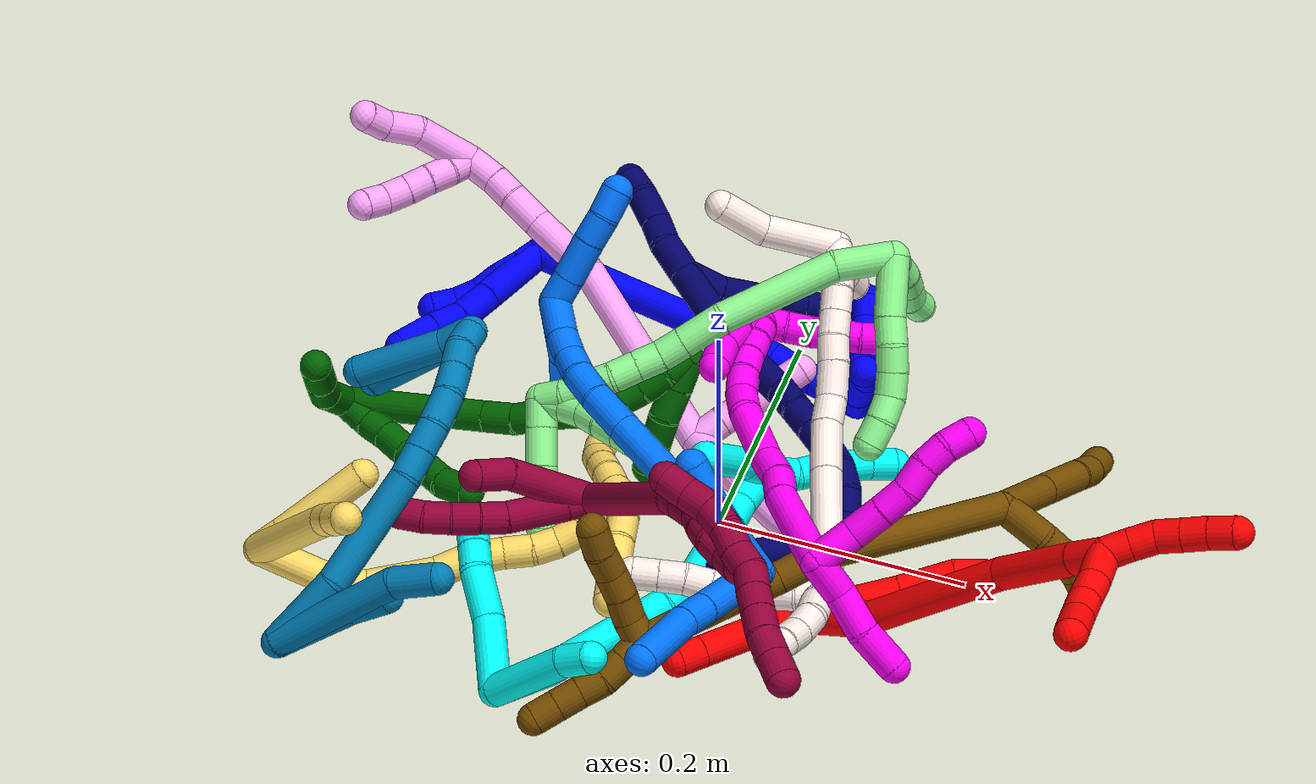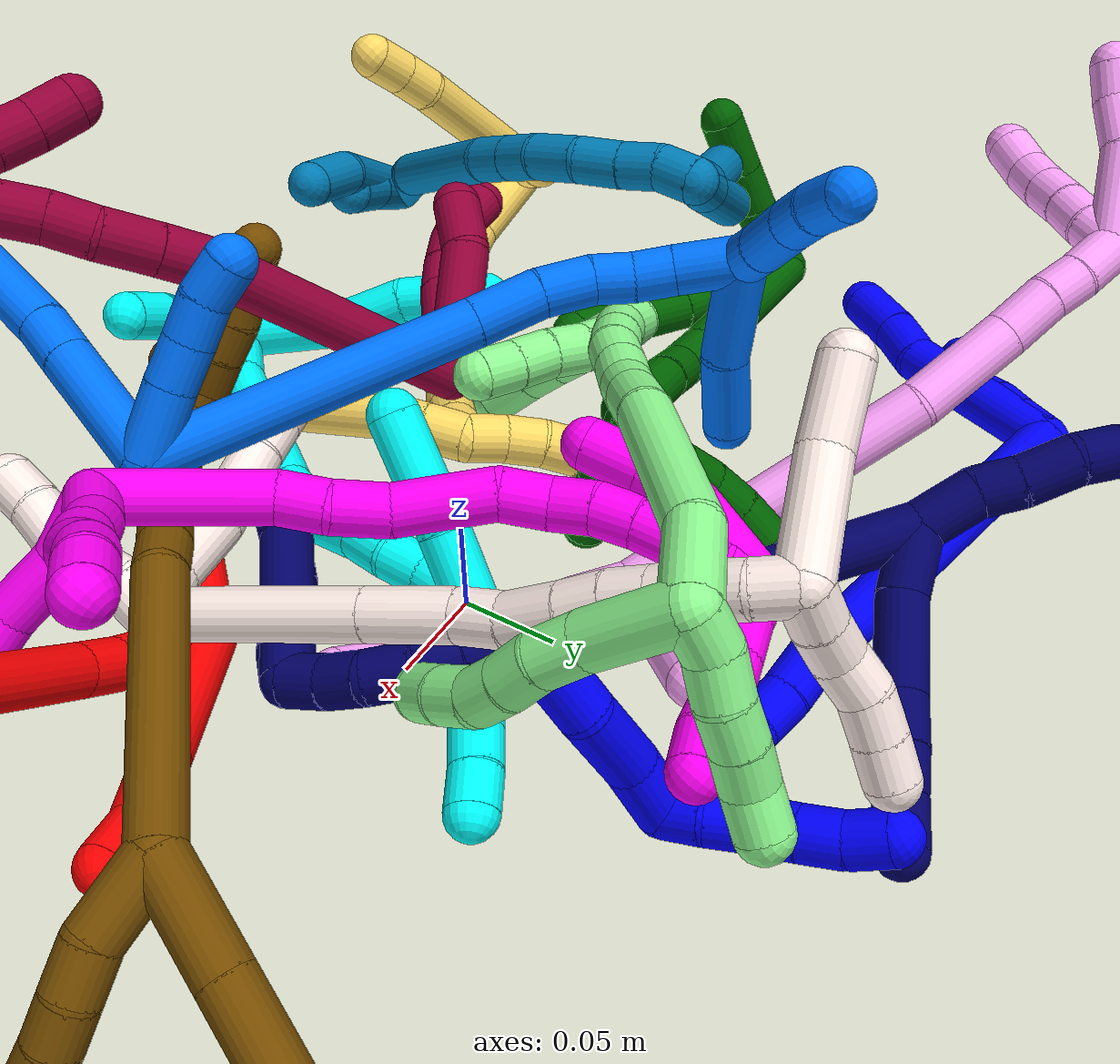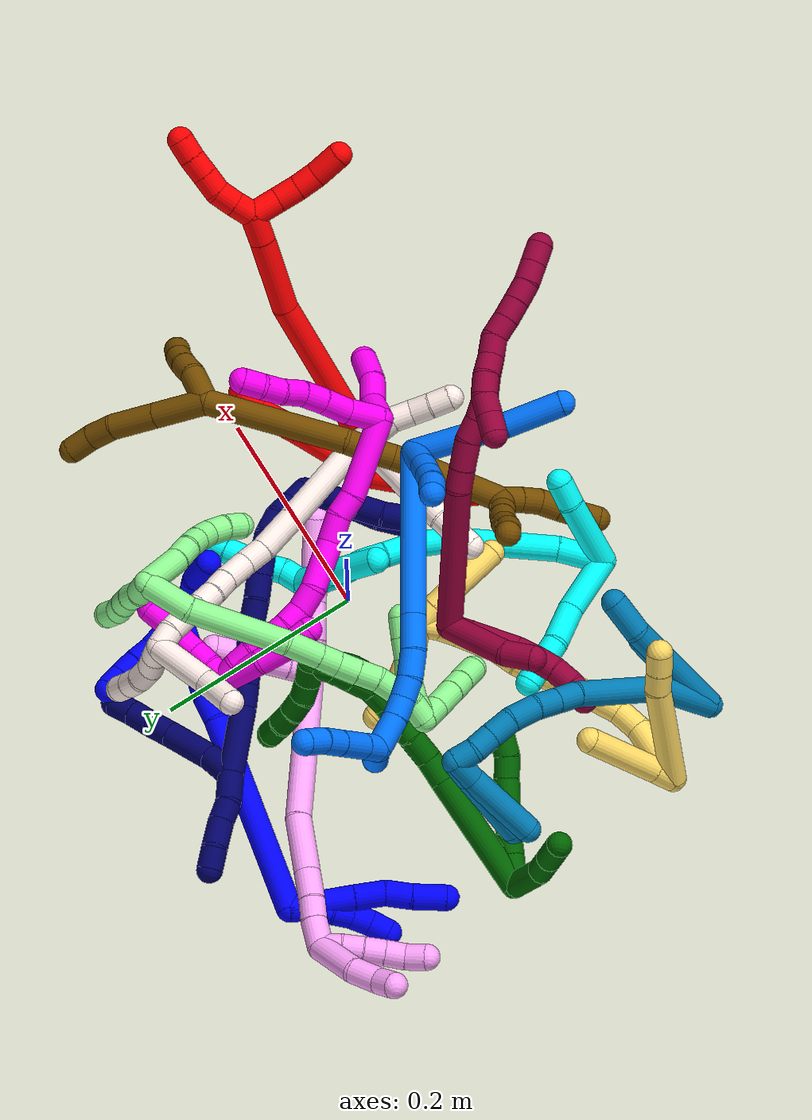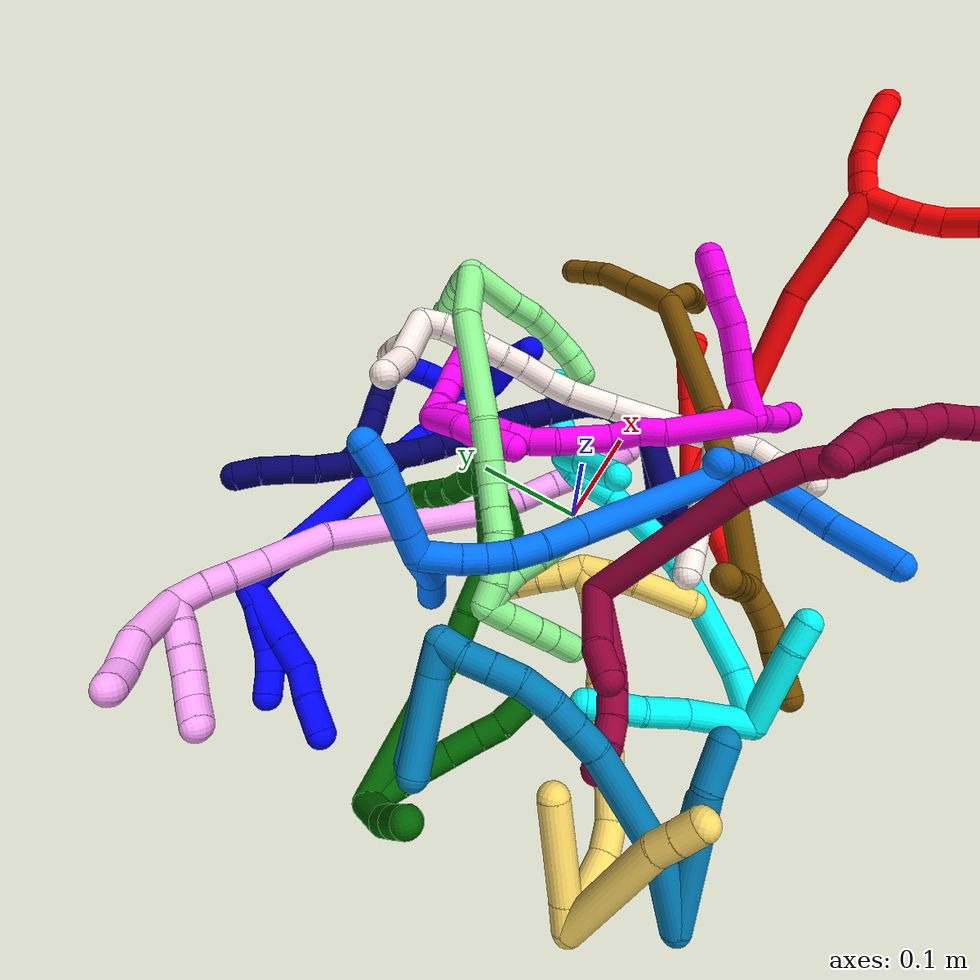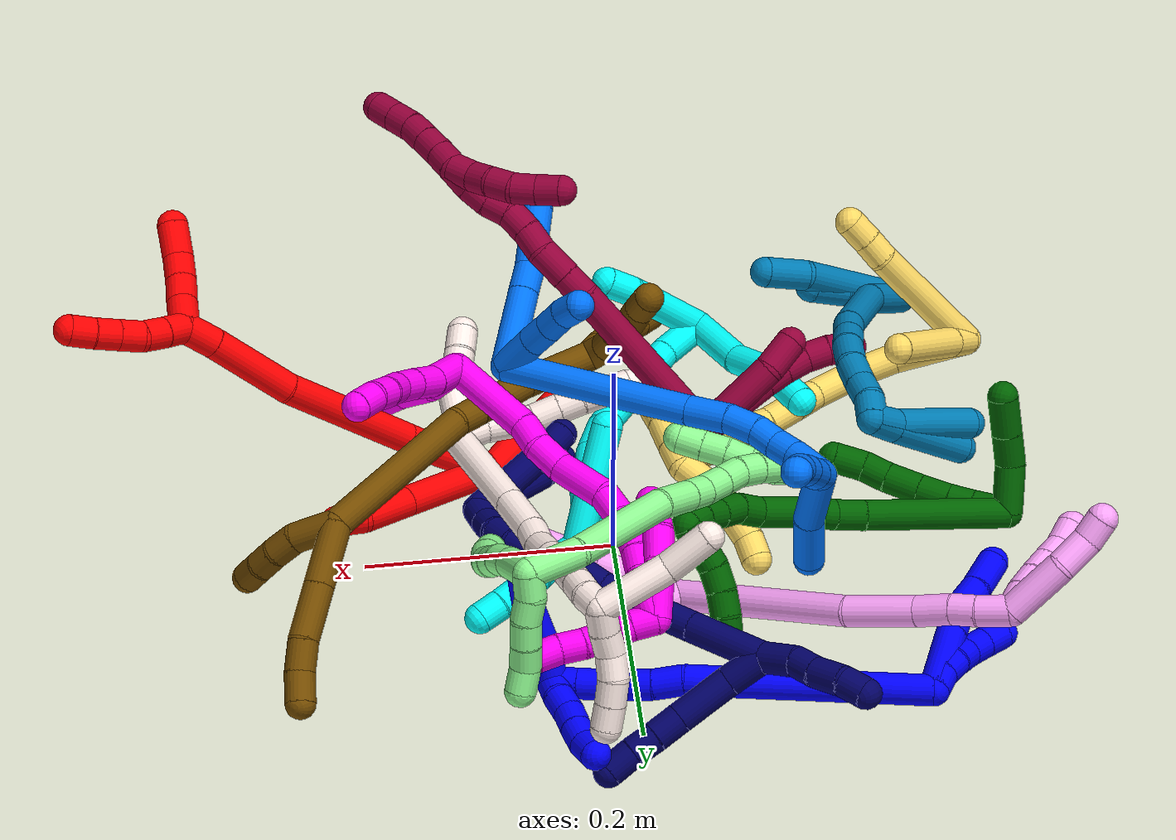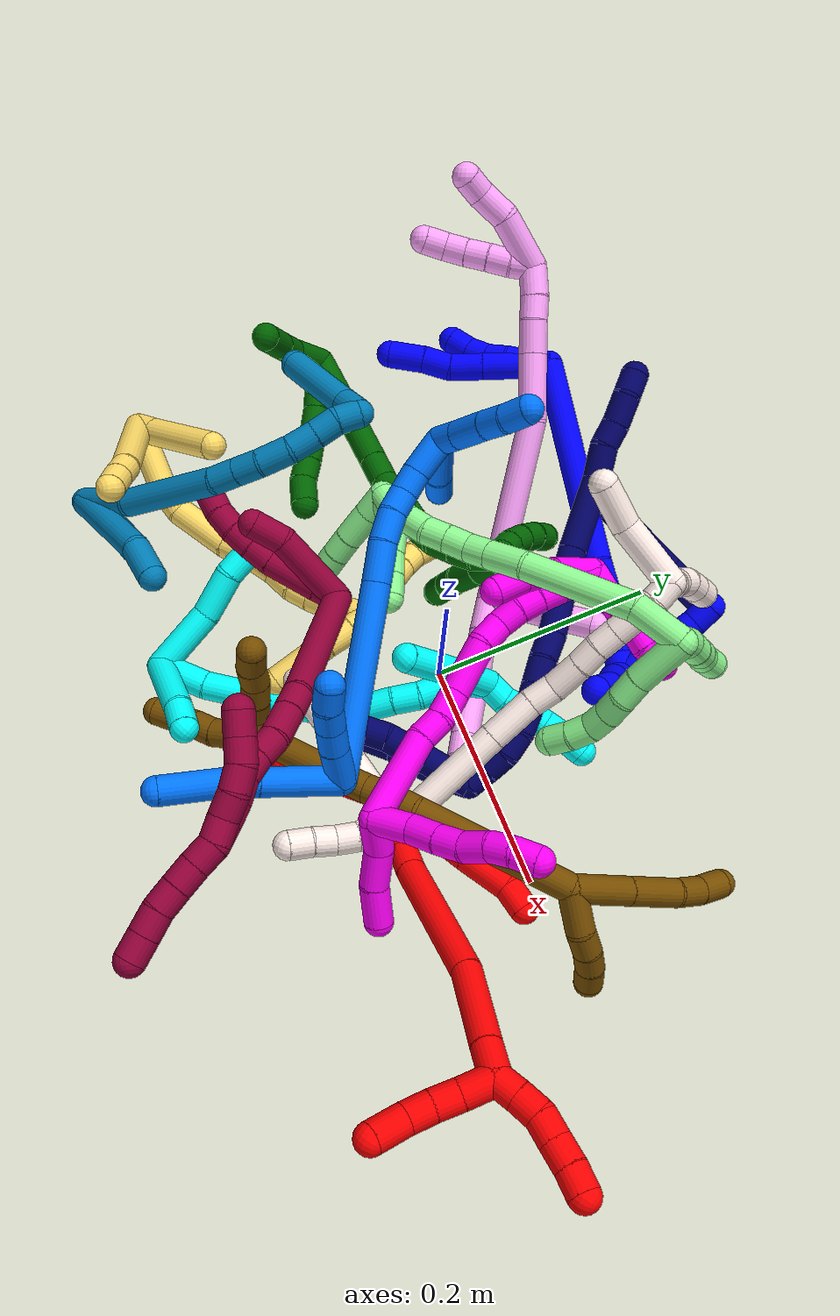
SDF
<sdf version="1.7">
 <world name="default">
  <plugin name="TubeGeneratorPlugin" filename="libtube_generator_plugin.so"/>
  <model name="photoneo_s_sensor">
   <static>1</static>
   <pose>0 0 2 1.57079 1.57079 3.14159</pose>
   <link name="link">
    <inertial><mass>0.1</mass></inertial>
    <sensor name="sensor" type="depth">
     <update_rate>30</update_rate>
     <camera>
      <horizontal_fov>1.22</horizontal_fov>
      <image><width>1920</width><height>1200</height><format>B8G8R8</format></image>
      <clip><near>0.1</near><far>4</far></clip>
      <depth_camera><output>points</output></depth_camera>
     </camera>
     <plugin name="camera_plugin" filename="libgazebo_ros_depth_camera.so">
      <baseline>0.2</baseline>
      <alwaysOn>1</alwaysOn>
      <updateRate>0.0</updateRate>
      <cameraName>camera_ir</cameraName>
      <imageTopicName>/camera/color/image_raw</imageTopicName>
      <cameraInfoTopicName>/camera/color/camera_info</cameraInfoTopicName>
      <depthImageTopicName>/camera/depth/image_raw</depthImageTopicName>
      <depthImageCameraInfoTopicName>/camera/depth/camera_info</depthImageCameraInfoTopicName>
      <pointCloudTopicName>/camera/depth/points</pointCloudTopicName>
      <frameName>fr_optical</frameName>
      <pointCloudCutoff>0.1</pointCloudCutoff>
      <pointCloudCutoffMax>2.0</pointCloudCutoffMax>
      <distortionK1>0</distortionK1>
      <distortionK2>0</distortionK2>
      <distortionK3>0</distortionK3>
      <distortionT1>0</distortionT1>
      <distortionT2>0</distortionT2>
      <CxPrime>0</CxPrime>
      <Cx>0</Cx>
      <Cy>0</Cy>
      <focalLength>0</focalLength>
      <hackBaseline>0</hackBaseline>
     </plugin>
    </sensor>
   </link>
  </model>
  <gravity>0 0 -9.8</gravity>
  <magnetic_field>6e-06 2.3e-05 -4.2e-05</magnetic_field>
  <atmosphere type="adiabatic"/>
  <physics name="default_physics" default="0" type="ode">
   <max_step_size>0.003</max_step_size>
   <real_time_factor>1</real_time_factor>
   <real_time_update_rate>1000</real_time_update_rate>
   <max_contacts>10000</max_contacts>
   <ode>
    <solver>
     <type>quick</type>
     <iters>100</iters>
     <sor>1.3</sor>
     <use_dynamic_moi_rescaling>0</use_dynamic_moi_rescaling>
    </solver>
    <constraints>
     <contact_max_correcting_vel>0</contact_max_correcting_vel>
     <contact_surface_layer>0.001</contact_surface_layer>
     <cfm>0</cfm>
     <erp>0.2</erp>
    </constraints>
   </ode>
  </physics>
  <scene><ambient>0.4 0.4 0.4 1</ambient><background>0.7 0.7 0.7 1</background><shadows>0</shadows></scene>
  <audio><device>default</device></audio>
  <spherical_coordinates>
   <surface_model>EARTH_WGS84</surface_model>
   <latitude_deg>0</latitude_deg>
   <longitude_deg>0</longitude_deg>
   <elevation>0</elevation>
   <heading_deg>0</heading_deg>
  </spherical_coordinates>
  <model name="bin">
   <static>1</static>
   <link name="bottom">
    <collision name="collision-bottom">
     <pose>0 0 -0.01 0 -0 0</pose>
     <geometry><box><size>0.8 0.6 0.02</size></box></geometry>
     <surface>
      <friction><ode><mu>100</mu><mu2>100</mu2></ode></friction>
      <contact><collide_bitmask>65535</collide_bitmask></contact>
     </surface>
    </collision>
   </link>
   <link name="west_wall">
    <collision name="collision-west_wall">
     <pose>-0.41 0 0.1 0 -0 0</pose>
     <geometry><box><size>0.02 0.6 0.2</size></box></geometry>
     <surface>
      <friction><ode><mu>100</mu><mu2>100</mu2></ode></friction>
      <contact><collide_bitmask>65535</collide_bitmask></contact>
     </surface>
    </collision>
   </link>
   <link name="east_wall">
    <collision name="collision-east_wall">
     <pose>0.41 0 0.1 0 -0 0</pose>
     <geometry><box><size>0.02 0.6 0.2</size></box></geometry>
     <surface>
      <friction><ode><mu>100</mu><mu2>100</mu2></ode></friction>
      <contact><collide_bitmask>65535</collide_bitmask></contact>
     </surface>
    </collision>
   </link>
   <link name="south_wall">
    <collision name="collision-south_wall">
     <pose>0 -0.31 0.1 0 -0 0</pose>
     <geometry><box><size>0.8 0.02 0.2</size></box></geometry>
     <surface>
      <friction><ode><mu>100</mu><mu2>100</mu2></ode></friction>
      <contact><collide_bitmask>65535</collide_bitmask></contact>
     </surface>
    </collision>
   </link>
   <link name="north_wall">
    <collision name="collision-north_wall">
     <pose>0 0.31 0.1 0 -0 0</pose>
     <geometry><box><size>0.8 0.02 0.2</size></box></geometry>
     <surface>
      <friction><ode><mu>100</mu><mu2>100</mu2></ode></friction>
      <contact><collide_bitmask>65535</collide_bitmask></contact>
     </surface>
    </collision>
   </link>
  </model>
  <model name="1">
   <static>0</static>
   <link name="1">
    <collision name="collision-cylinder-e_1_2_8">
     <pose>-0.027826 -0.007752 -0.01161 2.55288 -1.10579 -2.2283</pose>
     <geometry><cylinder><radius>0.0125</radius><length>0.062263</length></cylinder></geometry>
     <surface>
      <friction><ode><mu>1.16</mu><mu2>1.16</mu2><slip1>0</slip1><slip2>0</slip2></ode></friction>
      <contact><ode><kp>1e+06</kp><kd>1</kd><max_vel>0</max_vel><min_depth>0.001</min_depth></ode></contact>
     </surface>
    </collision>
    <visual name="visual-cylinder-e_1_2_8">
     <pose>-0.027826 -0.007752 -0.01161 2.55288 -1.10579 -2.2283</pose>
     <geometry><cylinder><radius>0.0125</radius><length>0.062263</length></cylinder></geometry>
     <material><ambient>0 0 1 1</ambient></material>
    </visual>
    <collision name="collision-cylinder-e_2_8_9">
     <pose>-0.06913 -0.018833 -0.028626 2.58964 -1.13058 -2.3018</pose>
     <geometry><cylinder><radius>0.0125</radius><length>0.029796</length></cylinder></geometry>
     <surface>
      <friction><ode><mu>1.16</mu><mu2>1.16</mu2><slip1>0</slip1><slip2>0</slip2></ode></friction>
      <contact><ode><kp>1e+06</kp><kd>1</kd><max_vel>0</max_vel><min_depth>0.001</min_depth></ode></contact>
     </surface>
    </collision>
    <visual name="visual-cylinder-e_2_8_9">
     <pose>-0.06913 -0.018833 -0.028626 2.58964 -1.13058 -2.3018</pose>
     <geometry><cylinder><radius>0.0125</radius><length>0.029796</length></cylinder></geometry>
     <material><ambient>0 0 1 1</ambient></material>
    </visual>
    <collision name="collision-cylinder-e_3_9_10">
     <pose>-0.095227 -0.02409 -0.034992 2.03284 -1.4017 -1.87549</pose>
     <geometry><cylinder><radius>0.0125</radius><length>0.025605</length></cylinder></geometry>
     <surface>
      <friction><ode><mu>1.16</mu><mu2>1.16</mu2><slip1>0</slip1><slip2>0</slip2></ode></friction>
      <contact><ode><kp>1e+06</kp><kd>1</kd><max_vel>0</max_vel><min_depth>0.001</min_depth></ode></contact>
     </surface>
    </collision>
    <visual name="visual-cylinder-e_3_9_10">
     <pose>-0.095227 -0.02409 -0.034992 2.03284 -1.4017 -1.87549</pose>
     <geometry><cylinder><radius>0.0125</radius><length>0.025605</length></cylinder></geometry>
     <material><ambient>0 0 1 1</ambient></material>
    </visual>
    <collision name="collision-cylinder-e_4_10_6">
     <pose>-0.123479 -0.028522 -0.039237 2.49025 -1.31255 -2.31513</pose>
     <geometry><cylinder><radius>0.0125</radius><length>0.032336</length></cylinder></geometry>
     <surface>
      <friction><ode><mu>1.16</mu><mu2>1.16</mu2><slip1>0</slip1><slip2>0</slip2></ode></friction>
      <contact><ode><kp>1e+06</kp><kd>1</kd><max_vel>0</max_vel><min_depth>0.001</min_depth></ode></contact>
     </surface>
    </collision>
    <visual name="visual-cylinder-e_4_10_6">
     <pose>-0.123479 -0.028522 -0.039237 2.49025 -1.31255 -2.31513</pose>
     <geometry><cylinder><radius>0.0125</radius><length>0.032336</length></cylinder></geometry>
     <material><ambient>0 0 1 1</ambient></material>
    </visual>
    <collision name="collision-cylinder-e_1_2_11">
     <pose>-0.009406 -0.001735 -0.002918 2.6052 -1.22445 -2.39554</pose>
     <geometry><cylinder><radius>0.0125</radius><length>0.02</length></cylinder></geometry>
     <surface>
      <friction><ode><mu>1.16</mu><mu2>1.16</mu2><slip1>0</slip1><slip2>0</slip2></ode></friction>
      <contact><ode><kp>1e+06</kp><kd>1</kd><max_vel>0</max_vel><min_depth>0.001</min_depth></ode></contact>
     </surface>
    </collision>
    <visual name="visual-cylinder-e_1_2_11">
     <pose>-0.009406 -0.001735 -0.002918 2.6052 -1.22445 -2.39554</pose>
     <geometry><cylinder><radius>0.0125</radius><length>0.02</length></cylinder></geometry>
     <material><ambient>0 0 1 1</ambient></material>
    </visual>
    <collision name="collision-cylinder-e_2_11_12">
     <pose>-0.028631 -0.002928 -0.007655 -2.85234 -1.37979 2.79218</pose>
     <geometry><cylinder><radius>0.0125</radius><length>0.02</length></cylinder></geometry>
     <surface>
      <friction><ode><mu>1.16</mu><mu2>1.16</mu2><slip1>0</slip1><slip2>0</slip2></ode></friction>
      <contact><ode><kp>1e+06</kp><kd>1</kd><max_vel>0</max_vel><min_depth>0.001</min_depth></ode></contact>
     </surface>
    </collision>
    <visual name="visual-cylinder-e_2_11_12">
     <pose>-0.028631 -0.002928 -0.007655 -2.85234 -1.37979 2.79218</pose>
     <geometry><cylinder><radius>0.0125</radius><length>0.02</length></cylinder></geometry>
     <material><ambient>0 0 1 1</ambient></material>
    </visual>
    <collision name="collision-cylinder-e_3_12_13">
     <pose>-0.047875 -0.000464 -0.012204 -2.52778 -1.23046 2.2985</pose>
     <geometry><cylinder><radius>0.0125</radius><length>0.02</length></cylinder></geometry>
     <surface>
      <friction><ode><mu>1.16</mu><mu2>1.16</mu2><slip1>0</slip1><slip2>0</slip2></ode></friction>
      <contact><ode><kp>1e+06</kp><kd>1</kd><max_vel>0</max_vel><min_depth>0.001</min_depth></ode></contact>
     </surface>
    </collision>
    <visual name="visual-cylinder-e_3_12_13">
     <pose>-0.047875 -0.000464 -0.012204 -2.52778 -1.23046 2.2985</pose>
     <geometry><cylinder><radius>0.0125</radius><length>0.02</length></cylinder></geometry>
     <material><ambient>0 0 1 1</ambient></material>
    </visual>
    <collision name="collision-cylinder-e_4_13_14">
     <pose>-0.067161 0.00309 -0.015292 -1.78758 -1.40294 1.62062</pose>
     <geometry><cylinder><radius>0.0125</radius><length>0.02</length></cylinder></geometry>
     <surface>
      <friction><ode><mu>1.16</mu><mu2>1.16</mu2><slip1>0</slip1><slip2>0</slip2></ode></friction>
      <contact><ode><kp>1e+06</kp><kd>1</kd><max_vel>0</max_vel><min_depth>0.001</min_depth></ode></contact>
     </surface>
    </collision>
    <visual name="visual-cylinder-e_4_13_14">
     <pose>-0.067161 0.00309 -0.015292 -1.78758 -1.40294 1.62062</pose>
     <geometry><cylinder><radius>0.0125</radius><length>0.02</length></cylinder></geometry>
     <material><ambient>0 0 1 1</ambient></material>
    </visual>
    <collision name="collision-cylinder-e_5_14_5">
     <pose>-0.086848 0.005813 -0.014161 -0.631845 -1.38509 0.529622</pose>
     <geometry><cylinder><radius>0.0125</radius><length>0.02</length></cylinder></geometry>
     <surface>
      <friction><ode><mu>1.16</mu><mu2>1.16</mu2><slip1>0</slip1><slip2>0</slip2></ode></friction>
      <contact><ode><kp>1e+06</kp><kd>1</kd><max_vel>0</max_vel><min_depth>0.001</min_depth></ode></contact>
     </surface>
    </collision>
    <visual name="visual-cylinder-e_5_14_5">
     <pose>-0.086848 0.005813 -0.014161 -0.631845 -1.38509 0.529622</pose>
     <geometry><cylinder><radius>0.0125</radius><length>0.02</length></cylinder></geometry>
     <material><ambient>0 0 1 1</ambient></material>
    </visual>
    <collision name="collision-cylinder-e_1_2_15">
     <pose>0.05837 -0.033647 -0.070456 2.69606 0.641949 1.9454</pose>
     <geometry><cylinder><radius>0.0125</radius><length>0.19497</length></cylinder></geometry>
     <surface>
      <friction><ode><mu>1.16</mu><mu2>1.16</mu2><slip1>0</slip1><slip2>0</slip2></ode></friction>
      <contact><ode><kp>1e+06</kp><kd>1</kd><max_vel>0</max_vel><min_depth>0.001</min_depth></ode></contact>
     </surface>
    </collision>
    <visual name="visual-cylinder-e_1_2_15">
     <pose>0.05837 -0.033647 -0.070456 2.69606 0.641949 1.9454</pose>
     <geometry><cylinder><radius>0.0125</radius><length>0.19497</length></cylinder></geometry>
     <material><ambient>0 0 1 1</ambient></material>
    </visual>
    <collision name="collision-cylinder-e_2_15_16">
     <pose>0.124683 -0.069066 -0.150412 2.95724 0.68805 2.63657</pose>
     <geometry><cylinder><radius>0.0125</radius><length>0.025018</length></cylinder></geometry>
     <surface>
      <friction><ode><mu>1.16</mu><mu2>1.16</mu2><slip1>0</slip1><slip2>0</slip2></ode></friction>
      <contact><ode><kp>1e+06</kp><kd>1</kd><max_vel>0</max_vel><min_depth>0.001</min_depth></ode></contact>
     </surface>
    </collision>
    <visual name="visual-cylinder-e_2_15_16">
     <pose>0.124683 -0.069066 -0.150412 2.95724 0.68805 2.63657</pose>
     <geometry><cylinder><radius>0.0125</radius><length>0.025018</length></cylinder></geometry>
     <material><ambient>0 0 1 1</ambient></material>
    </visual>
    <collision name="collision-cylinder-e_3_16_17">
     <pose>0.138005 -0.073174 -0.168017 2.86095 0.567599 2.23963</pose>
     <geometry><cylinder><radius>0.0125</radius><length>0.020008</length></cylinder></geometry>
     <surface>
      <friction><ode><mu>1.16</mu><mu2>1.16</mu2><slip1>0</slip1><slip2>0</slip2></ode></friction>
      <contact><ode><kp>1e+06</kp><kd>1</kd><max_vel>0</max_vel><min_depth>0.001</min_depth></ode></contact>
     </surface>
    </collision>
    <visual name="visual-cylinder-e_3_16_17">
     <pose>0.138005 -0.073174 -0.168017 2.86095 0.567599 2.23963</pose>
     <geometry><cylinder><radius>0.0125</radius><length>0.020008</length></cylinder></geometry>
     <material><ambient>0 0 1 1</ambient></material>
    </visual>
    <collision name="collision-cylinder-e_4_17_18">
     <pose>0.149065 -0.078344 -0.183851 2.79015 0.604093 2.1057</pose>
     <geometry><cylinder><radius>0.0125</radius><length>0.020004</length></cylinder></geometry>
     <surface>
      <friction><ode><mu>1.16</mu><mu2>1.16</mu2><slip1>0</slip1><slip2>0</slip2></ode></friction>
      <contact><ode><kp>1e+06</kp><kd>1</kd><max_vel>0</max_vel><min_depth>0.001</min_depth></ode></contact>
     </surface>
    </collision>
    <visual name="visual-cylinder-e_4_17_18">
     <pose>0.149065 -0.078344 -0.183851 2.79015 0.604093 2.1057</pose>
     <geometry><cylinder><radius>0.0125</radius><length>0.020004</length></cylinder></geometry>
     <material><ambient>0 0 1 1</ambient></material>
    </visual>
    <collision name="collision-cylinder-e_5_18_19">
     <pose>0.160295 -0.084416 -0.199242 2.74172 0.588292 1.96245</pose>
     <geometry><cylinder><radius>0.0125</radius><length>0.02</length></cylinder></geometry>
     <surface>
      <friction><ode><mu>1.16</mu><mu2>1.16</mu2><slip1>0</slip1><slip2>0</slip2></ode></friction>
      <contact><ode><kp>1e+06</kp><kd>1</kd><max_vel>0</max_vel><min_depth>0.001</min_depth></ode></contact>
     </surface>
    </collision>
    <visual name="visual-cylinder-e_5_18_19">
     <pose>0.160295 -0.084416 -0.199242 2.74172 0.588292 1.96245</pose>
     <geometry><cylinder><radius>0.0125</radius><length>0.02</length></cylinder></geometry>
     <material><ambient>0 0 1 1</ambient></material>
    </visual>
    <collision name="collision-cylinder-e_6_19_1">
     <pose>0.171395 -0.090892 -0.214568 2.7419 0.588377 1.96302</pose>
     <geometry><cylinder><radius>0.0125</radius><length>0.02</length></cylinder></geometry>
     <surface>
      <friction><ode><mu>1.16</mu><mu2>1.16</mu2><slip1>0</slip1><slip2>0</slip2></ode></friction>
      <contact><ode><kp>1e+06</kp><kd>1</kd><max_vel>0</max_vel><min_depth>0.001</min_depth></ode></contact>
     </surface>
    </collision>
    <visual name="visual-cylinder-e_6_19_1">
     <pose>0.171395 -0.090892 -0.214568 2.7419 0.588377 1.96302</pose>
     <geometry><cylinder><radius>0.0125</radius><length>0.02</length></cylinder></geometry>
     <material><ambient>0 0 1 1</ambient></material>
    </visual>
    <collision name="collision-cylinder-e_1_1_20">
     <pose>0.182498 -0.091667 -0.214286 -0.300461 0.588663 -0.091708</pose>
     <geometry><cylinder><radius>0.0125</radius><length>0.02</length></cylinder></geometry>
     <surface>
      <friction><ode><mu>1.16</mu><mu2>1.16</mu2><slip1>0</slip1><slip2>0</slip2></ode></friction>
      <contact><ode><kp>1e+06</kp><kd>1</kd><max_vel>0</max_vel><min_depth>0.001</min_depth></ode></contact>
     </surface>
    </collision>
    <visual name="visual-cylinder-e_1_1_20">
     <pose>0.182498 -0.091667 -0.214286 -0.300461 0.588663 -0.091708</pose>
     <geometry><cylinder><radius>0.0125</radius><length>0.02</length></cylinder></geometry>
     <material><ambient>0 0 1 1</ambient></material>
    </visual>
    <collision name="collision-cylinder-e_2_20_21">
     <pose>0.192118 -0.085004 -0.19823 -0.477945 0.418889 -0.10348</pose>
     <geometry><cylinder><radius>0.0125</radius><length>0.02</length></cylinder></geometry>
     <surface>
      <friction><ode><mu>1.16</mu><mu2>1.16</mu2><slip1>0</slip1><slip2>0</slip2></ode></friction>
      <contact><ode><kp>1e+06</kp><kd>1</kd><max_vel>0</max_vel><min_depth>0.001</min_depth></ode></contact>
     </surface>
    </collision>
    <visual name="visual-cylinder-e_2_20_21">
     <pose>0.192118 -0.085004 -0.19823 -0.477945 0.418889 -0.10348</pose>
     <geometry><cylinder><radius>0.0125</radius><length>0.02</length></cylinder></geometry>
     <material><ambient>0 0 1 1</ambient></material>
    </visual>
    <collision name="collision-cylinder-e_3_21_22">
     <pose>0.201577 -0.077856 -0.182229 -0.357382 0.569483 -0.105633</pose>
     <geometry><cylinder><radius>0.0125</radius><length>0.02</length></cylinder></geometry>
     <surface>
      <friction><ode><mu>1.16</mu><mu2>1.16</mu2><slip1>0</slip1><slip2>0</slip2></ode></friction>
      <contact><ode><kp>1e+06</kp><kd>1</kd><max_vel>0</max_vel><min_depth>0.001</min_depth></ode></contact>
     </surface>
    </collision>
    <visual name="visual-cylinder-e_3_21_22">
     <pose>0.201577 -0.077856 -0.182229 -0.357382 0.569483 -0.105633</pose>
     <geometry><cylinder><radius>0.0125</radius><length>0.02</length></cylinder></geometry>
     <material><ambient>0 0 1 1</ambient></material>
    </visual>
    <collision name="collision-cylinder-e_4_22_23">
     <pose>0.211778 -0.071578 -0.166229 -0.389752 0.501695 -0.101069</pose>
     <geometry><cylinder><radius>0.0125</radius><length>0.02</length></cylinder></geometry>
     <surface>
      <friction><ode><mu>1.16</mu><mu2>1.16</mu2><slip1>0</slip1><slip2>0</slip2></ode></friction>
      <contact><ode><kp>1e+06</kp><kd>1</kd><max_vel>0</max_vel><min_depth>0.001</min_depth></ode></contact>
     </surface>
    </collision>
    <visual name="visual-cylinder-e_4_22_23">
     <pose>0.211778 -0.071578 -0.166229 -0.389752 0.501695 -0.101069</pose>
     <geometry><cylinder><radius>0.0125</radius><length>0.02</length></cylinder></geometry>
     <material><ambient>0 0 1 1</ambient></material>
    </visual>
    <collision name="collision-cylinder-e_5_23_4">
     <pose>0.220422 -0.066797 -0.148998 -0.157628 0.393544 -0.031486</pose>
     <geometry><cylinder><radius>0.0125</radius><length>0.02</length></cylinder></geometry>
     <surface>
      <friction><ode><mu>1.16</mu><mu2>1.16</mu2><slip1>0</slip1><slip2>0</slip2></ode></friction>
      <contact><ode><kp>1e+06</kp><kd>1</kd><max_vel>0</max_vel><min_depth>0.001</min_depth></ode></contact>
     </surface>
    </collision>
    <visual name="visual-cylinder-e_5_23_4">
     <pose>0.220422 -0.066797 -0.148998 -0.157628 0.393544 -0.031486</pose>
     <geometry><cylinder><radius>0.0125</radius><length>0.02</length></cylinder></geometry>
     <material><ambient>0 0 1 1</ambient></material>
    </visual>
    <collision name="collision-cylinder-e_1_1_24">
     <pose>0.174975 -0.109314 -0.220914 1.48431 -0.128567 -0.117928</pose>
     <geometry><cylinder><radius>0.0125</radius><length>0.030738</length></cylinder></geometry>
     <surface>
      <friction><ode><mu>1.16</mu><mu2>1.16</mu2><slip1>0</slip1><slip2>0</slip2></ode></friction>
      <contact><ode><kp>1e+06</kp><kd>1</kd><max_vel>0</max_vel><min_depth>0.001</min_depth></ode></contact>
     </surface>
    </collision>
    <visual name="visual-cylinder-e_1_1_24">
     <pose>0.174975 -0.109314 -0.220914 1.48431 -0.128567 -0.117928</pose>
     <geometry><cylinder><radius>0.0125</radius><length>0.030738</length></cylinder></geometry>
     <material><ambient>0 0 1 1</ambient></material>
    </visual>
    <collision name="collision-cylinder-e_2_24_25">
     <pose>0.173813 -0.144451 -0.218405 1.51111 0.040465 0.03812</pose>
     <geometry><cylinder><radius>0.0125</radius><length>0.040009</length></cylinder></geometry>
     <surface>
      <friction><ode><mu>1.16</mu><mu2>1.16</mu2><slip1>0</slip1><slip2>0</slip2></ode></friction>
      <contact><ode><kp>1e+06</kp><kd>1</kd><max_vel>0</max_vel><min_depth>0.001</min_depth></ode></contact>
     </surface>
    </collision>
    <visual name="visual-cylinder-e_2_24_25">
     <pose>0.173813 -0.144451 -0.218405 1.51111 0.040465 0.03812</pose>
     <geometry><cylinder><radius>0.0125</radius><length>0.040009</length></cylinder></geometry>
     <material><ambient>0 0 1 1</ambient></material>
    </visual>
    <collision name="collision-cylinder-e_3_25_3">
     <pose>0.170852 -0.178535 -0.217358 1.5811 -0.260738 -0.263407</pose>
     <geometry><cylinder><radius>0.0125</radius><length>0.029253</length></cylinder></geometry>
     <surface>
      <friction><ode><mu>1.16</mu><mu2>1.16</mu2><slip1>0</slip1><slip2>0</slip2></ode></friction>
      <contact><ode><kp>1e+06</kp><kd>1</kd><max_vel>0</max_vel><min_depth>0.001</min_depth></ode></contact>
     </surface>
    </collision>
    <visual name="visual-cylinder-e_3_25_3">
     <pose>0.170852 -0.178535 -0.217358 1.5811 -0.260738 -0.263407</pose>
     <geometry><cylinder><radius>0.0125</radius><length>0.029253</length></cylinder></geometry>
     <material><ambient>0 0 1 1</ambient></material>
    </visual>
    <collision name="collision-sphere-3">
     <pose>0.167081 -0.192667 -0.217504 0 -0 0</pose>
     <geometry><sphere><radius>0.0125</radius></sphere></geometry>
     <surface>
      <friction><ode><mu>1.16</mu><mu2>1.16</mu2><slip1>0</slip1><slip2>0</slip2></ode></friction>
      <contact><ode><kp>1e+06</kp><kd>1</kd><max_vel>0</max_vel><min_depth>0.001</min_depth></ode></contact>
     </surface>
    </collision>
    <visual name="visual-sphere-3">
     <pose>0.167081 -0.192667 -0.217504 0 -0 0</pose>
     <geometry><sphere><radius>0.0125</radius></sphere></geometry>
     <material><ambient>0 0 1 1</ambient></material>
    </visual>
    <collision name="collision-sphere-25">
     <pose>0.174623 -0.164404 -0.217213 0 -0 0</pose>
     <geometry><sphere><radius>0.0125</radius></sphere></geometry>
     <surface>
      <friction><ode><mu>1.16</mu><mu2>1.16</mu2><slip1>0</slip1><slip2>0</slip2></ode></friction>
      <contact><ode><kp>1e+06</kp><kd>1</kd><max_vel>0</max_vel><min_depth>0.001</min_depth></ode></contact>
     </surface>
    </collision>
    <visual name="visual-sphere-25">
     <pose>0.174623 -0.164404 -0.217213 0 -0 0</pose>
     <geometry><sphere><radius>0.0125</radius></sphere></geometry>
     <material><ambient>0 0 1 1</ambient></material>
    </visual>
    <collision name="collision-sphere-24">
     <pose>0.173004 -0.124499 -0.219598 0 -0 0</pose>
     <geometry><sphere><radius>0.0125</radius></sphere></geometry>
     <surface>
      <friction><ode><mu>1.16</mu><mu2>1.16</mu2><slip1>0</slip1><slip2>0</slip2></ode></friction>
      <contact><ode><kp>1e+06</kp><kd>1</kd><max_vel>0</max_vel><min_depth>0.001</min_depth></ode></contact>
     </surface>
    </collision>
    <visual name="visual-sphere-24">
     <pose>0.173004 -0.124499 -0.219598 0 -0 0</pose>
     <geometry><sphere><radius>0.0125</radius></sphere></geometry>
     <material><ambient>0 0 1 1</ambient></material>
    </visual>
    <collision name="collision-sphere-4">
     <pose>0.224256 -0.065348 -0.139877 0 -0 0</pose>
     <geometry><sphere><radius>0.0125</radius></sphere></geometry>
     <surface>
      <friction><ode><mu>1.16</mu><mu2>1.16</mu2><slip1>0</slip1><slip2>0</slip2></ode></friction>
      <contact><ode><kp>1e+06</kp><kd>1</kd><max_vel>0</max_vel><min_depth>0.001</min_depth></ode></contact>
     </surface>
    </collision>
    <visual name="visual-sphere-4">
     <pose>0.224256 -0.065348 -0.139877 0 -0 0</pose>
     <geometry><sphere><radius>0.0125</radius></sphere></geometry>
     <material><ambient>0 0 1 1</ambient></material>
    </visual>
    <collision name="collision-sphere-23">
     <pose>0.216587 -0.068247 -0.158119 0 -0 0</pose>
     <geometry><sphere><radius>0.0125</radius></sphere></geometry>
     <surface>
      <friction><ode><mu>1.16</mu><mu2>1.16</mu2><slip1>0</slip1><slip2>0</slip2></ode></friction>
      <contact><ode><kp>1e+06</kp><kd>1</kd><max_vel>0</max_vel><min_depth>0.001</min_depth></ode></contact>
     </surface>
    </collision>
    <visual name="visual-sphere-23">
     <pose>0.216587 -0.068247 -0.158119 0 -0 0</pose>
     <geometry><sphere><radius>0.0125</radius></sphere></geometry>
     <material><ambient>0 0 1 1</ambient></material>
    </visual>
    <collision name="collision-sphere-22">
     <pose>0.206969 -0.07491 -0.174339 0 -0 0</pose>
     <geometry><sphere><radius>0.0125</radius></sphere></geometry>
     <surface>
      <friction><ode><mu>1.16</mu><mu2>1.16</mu2><slip1>0</slip1><slip2>0</slip2></ode></friction>
      <contact><ode><kp>1e+06</kp><kd>1</kd><max_vel>0</max_vel><min_depth>0.001</min_depth></ode></contact>
     </surface>
    </collision>
    <visual name="visual-sphere-22">
     <pose>0.206969 -0.07491 -0.174339 0 -0 0</pose>
     <geometry><sphere><radius>0.0125</radius></sphere></geometry>
     <material><ambient>0 0 1 1</ambient></material>
    </visual>
    <collision name="collision-sphere-21">
     <pose>0.196185 -0.080802 -0.190119 0 -0 0</pose>
     <geometry><sphere><radius>0.0125</radius></sphere></geometry>
     <surface>
      <friction><ode><mu>1.16</mu><mu2>1.16</mu2><slip1>0</slip1><slip2>0</slip2></ode></friction>
      <contact><ode><kp>1e+06</kp><kd>1</kd><max_vel>0</max_vel><min_depth>0.001</min_depth></ode></contact>
     </surface>
    </collision>
    <visual name="visual-sphere-21">
     <pose>0.196185 -0.080802 -0.190119 0 -0 0</pose>
     <geometry><sphere><radius>0.0125</radius></sphere></geometry>
     <material><ambient>0 0 1 1</ambient></material>
    </visual>
    <collision name="collision-sphere-20">
     <pose>0.18805 -0.089206 -0.206342 0 -0 0</pose>
     <geometry><sphere><radius>0.0125</radius></sphere></geometry>
     <surface>
      <friction><ode><mu>1.16</mu><mu2>1.16</mu2><slip1>0</slip1><slip2>0</slip2></ode></friction>
      <contact><ode><kp>1e+06</kp><kd>1</kd><max_vel>0</max_vel><min_depth>0.001</min_depth></ode></contact>
     </surface>
    </collision>
    <visual name="visual-sphere-20">
     <pose>0.18805 -0.089206 -0.206342 0 -0 0</pose>
     <geometry><sphere><radius>0.0125</radius></sphere></geometry>
     <material><ambient>0 0 1 1</ambient></material>
    </visual>
    <collision name="collision-sphere-11">
     <pose>-0.018812 -0.00347 -0.005836 0 -0 0</pose>
     <geometry><sphere><radius>0.0125</radius></sphere></geometry>
     <surface>
      <friction><ode><mu>1.16</mu><mu2>1.16</mu2><slip1>0</slip1><slip2>0</slip2></ode></friction>
      <contact><ode><kp>1e+06</kp><kd>1</kd><max_vel>0</max_vel><min_depth>0.001</min_depth></ode></contact>
     </surface>
    </collision>
    <visual name="visual-sphere-11">
     <pose>-0.018812 -0.00347 -0.005836 0 -0 0</pose>
     <geometry><sphere><radius>0.0125</radius></sphere></geometry>
     <material><ambient>0 0 1 1</ambient></material>
    </visual>
    <collision name="collision-sphere-6">
     <pose>-0.139111 -0.031026 -0.04252 0 -0 0</pose>
     <geometry><sphere><radius>0.0125</radius></sphere></geometry>
     <surface>
      <friction><ode><mu>1.16</mu><mu2>1.16</mu2><slip1>0</slip1><slip2>0</slip2></ode></friction>
      <contact><ode><kp>1e+06</kp><kd>1</kd><max_vel>0</max_vel><min_depth>0.001</min_depth></ode></contact>
     </surface>
    </collision>
    <visual name="visual-sphere-6">
     <pose>-0.139111 -0.031026 -0.04252 0 -0 0</pose>
     <geometry><sphere><radius>0.0125</radius></sphere></geometry>
     <material><ambient>0 0 1 1</ambient></material>
    </visual>
    <collision name="collision-sphere-10">
     <pose>-0.107847 -0.026019 -0.035953 0 -0 0</pose>
     <geometry><sphere><radius>0.0125</radius></sphere></geometry>
     <surface>
      <friction><ode><mu>1.16</mu><mu2>1.16</mu2><slip1>0</slip1><slip2>0</slip2></ode></friction>
      <contact><ode><kp>1e+06</kp><kd>1</kd><max_vel>0</max_vel><min_depth>0.001</min_depth></ode></contact>
     </surface>
    </collision>
    <visual name="visual-sphere-10">
     <pose>-0.107847 -0.026019 -0.035953 0 -0 0</pose>
     <geometry><sphere><radius>0.0125</radius></sphere></geometry>
     <material><ambient>0 0 1 1</ambient></material>
    </visual>
    <collision name="collision-sphere-9">
     <pose>-0.082607 -0.022162 -0.034032 0 -0 0</pose>
     <geometry><sphere><radius>0.0125</radius></sphere></geometry>
     <surface>
      <friction><ode><mu>1.16</mu><mu2>1.16</mu2><slip1>0</slip1><slip2>0</slip2></ode></friction>
      <contact><ode><kp>1e+06</kp><kd>1</kd><max_vel>0</max_vel><min_depth>0.001</min_depth></ode></contact>
     </surface>
    </collision>
    <visual name="visual-sphere-9">
     <pose>-0.082607 -0.022162 -0.034032 0 -0 0</pose>
     <geometry><sphere><radius>0.0125</radius></sphere></geometry>
     <material><ambient>0 0 1 1</ambient></material>
    </visual>
    <collision name="collision-sphere-2">
     <geometry><sphere><radius>0.0125</radius></sphere></geometry>
     <surface>
      <friction><ode><mu>1.16</mu><mu2>1.16</mu2><slip1>0</slip1><slip2>0</slip2></ode></friction>
      <contact><ode><kp>1e+06</kp><kd>1</kd><max_vel>0</max_vel><min_depth>0.001</min_depth></ode></contact>
     </surface>
    </collision>
    <visual name="visual-sphere-2">
     <geometry><sphere><radius>0.0125</radius></sphere></geometry>
     <material><ambient>0 0 1 1</ambient></material>
    </visual>
    <collision name="collision-sphere-19">
     <pose>0.165845 -0.087655 -0.206905 0 -0 0</pose>
     <geometry><sphere><radius>0.0125</radius></sphere></geometry>
     <surface>
      <friction><ode><mu>1.16</mu><mu2>1.16</mu2><slip1>0</slip1><slip2>0</slip2></ode></friction>
      <contact><ode><kp>1e+06</kp><kd>1</kd><max_vel>0</max_vel><min_depth>0.001</min_depth></ode></contact>
     </surface>
    </collision>
    <visual name="visual-sphere-19">
     <pose>0.165845 -0.087655 -0.206905 0 -0 0</pose>
     <geometry><sphere><radius>0.0125</radius></sphere></geometry>
     <material><ambient>0 0 1 1</ambient></material>
    </visual>
    <collision name="collision-sphere-8">
     <pose>-0.055652 -0.015504 -0.02322 0 -0 0</pose>
     <geometry><sphere><radius>0.0125</radius></sphere></geometry>
     <surface>
      <friction><ode><mu>1.16</mu><mu2>1.16</mu2><slip1>0</slip1><slip2>0</slip2></ode></friction>
      <contact><ode><kp>1e+06</kp><kd>1</kd><max_vel>0</max_vel><min_depth>0.001</min_depth></ode></contact>
     </surface>
    </collision>
    <visual name="visual-sphere-8">
     <pose>-0.055652 -0.015504 -0.02322 0 -0 0</pose>
     <geometry><sphere><radius>0.0125</radius></sphere></geometry>
     <material><ambient>0 0 1 1</ambient></material>
    </visual>
    <collision name="collision-sphere-12">
     <pose>-0.038449 -0.002387 -0.009475 0 -0 0</pose>
     <geometry><sphere><radius>0.0125</radius></sphere></geometry>
     <surface>
      <friction><ode><mu>1.16</mu><mu2>1.16</mu2><slip1>0</slip1><slip2>0</slip2></ode></friction>
      <contact><ode><kp>1e+06</kp><kd>1</kd><max_vel>0</max_vel><min_depth>0.001</min_depth></ode></contact>
     </surface>
    </collision>
    <visual name="visual-sphere-12">
     <pose>-0.038449 -0.002387 -0.009475 0 -0 0</pose>
     <geometry><sphere><radius>0.0125</radius></sphere></geometry>
     <material><ambient>0 0 1 1</ambient></material>
    </visual>
    <collision name="collision-sphere-13">
     <pose>-0.057301 0.001459 -0.014932 0 -0 0</pose>
     <geometry><sphere><radius>0.0125</radius></sphere></geometry>
     <surface>
      <friction><ode><mu>1.16</mu><mu2>1.16</mu2><slip1>0</slip1><slip2>0</slip2></ode></friction>
      <contact><ode><kp>1e+06</kp><kd>1</kd><max_vel>0</max_vel><min_depth>0.001</min_depth></ode></contact>
     </surface>
    </collision>
    <visual name="visual-sphere-13">
     <pose>-0.057301 0.001459 -0.014932 0 -0 0</pose>
     <geometry><sphere><radius>0.0125</radius></sphere></geometry>
     <material><ambient>0 0 1 1</ambient></material>
    </visual>
    <collision name="collision-sphere-14">
     <pose>-0.07702 0.004722 -0.015651 0 -0 0</pose>
     <geometry><sphere><radius>0.0125</radius></sphere></geometry>
     <surface>
      <friction><ode><mu>1.16</mu><mu2>1.16</mu2><slip1>0</slip1><slip2>0</slip2></ode></friction>
      <contact><ode><kp>1e+06</kp><kd>1</kd><max_vel>0</max_vel><min_depth>0.001</min_depth></ode></contact>
     </surface>
    </collision>
    <visual name="visual-sphere-14">
     <pose>-0.07702 0.004722 -0.015651 0 -0 0</pose>
     <geometry><sphere><radius>0.0125</radius></sphere></geometry>
     <material><ambient>0 0 1 1</ambient></material>
    </visual>
    <collision name="collision-sphere-5">
     <pose>-0.096676 0.006903 -0.012671 0 -0 0</pose>
     <geometry><sphere><radius>0.0125</radius></sphere></geometry>
     <surface>
      <friction><ode><mu>1.16</mu><mu2>1.16</mu2><slip1>0</slip1><slip2>0</slip2></ode></friction>
      <contact><ode><kp>1e+06</kp><kd>1</kd><max_vel>0</max_vel><min_depth>0.001</min_depth></ode></contact>
     </surface>
    </collision>
    <visual name="visual-sphere-5">
     <pose>-0.096676 0.006903 -0.012671 0 -0 0</pose>
     <geometry><sphere><radius>0.0125</radius></sphere></geometry>
     <material><ambient>0 0 1 1</ambient></material>
    </visual>
    <collision name="collision-sphere-15">
     <pose>0.116739 -0.067295 -0.140913 0 -0 0</pose>
     <geometry><sphere><radius>0.0125</radius></sphere></geometry>
     <surface>
      <friction><ode><mu>1.16</mu><mu2>1.16</mu2><slip1>0</slip1><slip2>0</slip2></ode></friction>
      <contact><ode><kp>1e+06</kp><kd>1</kd><max_vel>0</max_vel><min_depth>0.001</min_depth></ode></contact>
     </surface>
    </collision>
    <visual name="visual-sphere-15">
     <pose>0.116739 -0.067295 -0.140913 0 -0 0</pose>
     <geometry><sphere><radius>0.0125</radius></sphere></geometry>
     <material><ambient>0 0 1 1</ambient></material>
    </visual>
    <collision name="collision-sphere-16">
     <pose>0.132627 -0.070837 -0.159911 0 -0 0</pose>
     <geometry><sphere><radius>0.0125</radius></sphere></geometry>
     <surface>
      <friction><ode><mu>1.16</mu><mu2>1.16</mu2><slip1>0</slip1><slip2>0</slip2></ode></friction>
      <contact><ode><kp>1e+06</kp><kd>1</kd><max_vel>0</max_vel><min_depth>0.001</min_depth></ode></contact>
     </surface>
    </collision>
    <visual name="visual-sphere-16">
     <pose>0.132627 -0.070837 -0.159911 0 -0 0</pose>
     <geometry><sphere><radius>0.0125</radius></sphere></geometry>
     <material><ambient>0 0 1 1</ambient></material>
    </visual>
    <collision name="collision-sphere-17">
     <pose>0.143383 -0.07551 -0.176122 0 -0 0</pose>
     <geometry><sphere><radius>0.0125</radius></sphere></geometry>
     <surface>
      <friction><ode><mu>1.16</mu><mu2>1.16</mu2><slip1>0</slip1><slip2>0</slip2></ode></friction>
      <contact><ode><kp>1e+06</kp><kd>1</kd><max_vel>0</max_vel><min_depth>0.001</min_depth></ode></contact>
     </surface>
    </collision>
    <visual name="visual-sphere-17">
     <pose>0.143383 -0.07551 -0.176122 0 -0 0</pose>
     <geometry><sphere><radius>0.0125</radius></sphere></geometry>
     <material><ambient>0 0 1 1</ambient></material>
    </visual>
    <collision name="collision-sphere-18">
     <pose>0.154746 -0.081178 -0.19158 0 -0 0</pose>
     <geometry><sphere><radius>0.0125</radius></sphere></geometry>
     <surface>
      <friction><ode><mu>1.16</mu><mu2>1.16</mu2><slip1>0</slip1><slip2>0</slip2></ode></friction>
      <contact><ode><kp>1e+06</kp><kd>1</kd><max_vel>0</max_vel><min_depth>0.001</min_depth></ode></contact>
     </surface>
    </collision>
    <visual name="visual-sphere-18">
     <pose>0.154746 -0.081178 -0.19158 0 -0 0</pose>
     <geometry><sphere><radius>0.0125</radius></sphere></geometry>
     <material><ambient>0 0 1 1</ambient></material>
    </visual>
    <collision name="collision-sphere-1">
     <pose>0.176945 -0.094129 -0.222231 0 -0 0</pose>
     <geometry><sphere><radius>0.0125</radius></sphere></geometry>
     <surface>
      <friction><ode><mu>1.16</mu><mu2>1.16</mu2><slip1>0</slip1><slip2>0</slip2></ode></friction>
      <contact><ode><kp>1e+06</kp><kd>1</kd><max_vel>0</max_vel><min_depth>0.001</min_depth></ode></contact>
     </surface>
    </collision>
    <visual name="visual-sphere-1">
     <pose>0.176945 -0.094129 -0.222231 0 -0 0</pose>
     <geometry><sphere><radius>0.0125</radius></sphere></geometry>
     <material><ambient>0 0 1 1</ambient></material>
    </visual>
    <inertial>
     <pose>0.065804 -0.052738 -0.103583 0 -0 0</pose>
     <mass>0.75</mass>
     <inertia>
      <ixx>0.000282</ixx>
      <ixy>0</ixy>
      <ixz>0</ixz>
      <iyy>0.000852</iyy>
      <iyz>0</iyz>
      <izz>-0.000124</izz>
     </inertia>
    </inertial>
   </link>
   <pose>-0.226914 0.207187 0.031296 -1.03274 -0.075689 0.727437</pose>
  </model>
  <model name="2">
   <static>0</static>
   <link name="2">
    <collision name="collision-cylinder-e_1_2_8">
     <pose>-0.000556 0.003736 0.041292 -0.090231 -0.013404 0.000605</pose>
     <geometry><cylinder><radius>0.0125</radius><length>0.082929</length></cylinder></geometry>
     <surface>
      <friction><ode><mu>1.16</mu><mu2>1.16</mu2><slip1>0</slip1><slip2>0</slip2></ode></friction>
      <contact><ode><kp>1e+06</kp><kd>1</kd><max_vel>0</max_vel><min_depth>0.001</min_depth></ode></contact>
     </surface>
    </collision>
    <visual name="visual-cylinder-e_1_2_8">
     <pose>-0.000556 0.003736 0.041292 -0.090231 -0.013404 0.000605</pose>
     <geometry><cylinder><radius>0.0125</radius><length>0.082929</length></cylinder></geometry>
     <material><ambient>1 0 0 1</ambient></material>
    </visual>
    <collision name="collision-cylinder-e_2_8_9">
     <pose>-0.000634 0.008498 0.104484 -0.046832 0.021802 -0.000511</pose>
     <geometry><cylinder><radius>0.0125</radius><length>0.043858</length></cylinder></geometry>
     <surface>
      <friction><ode><mu>1.16</mu><mu2>1.16</mu2><slip1>0</slip1><slip2>0</slip2></ode></friction>
      <contact><ode><kp>1e+06</kp><kd>1</kd><max_vel>0</max_vel><min_depth>0.001</min_depth></ode></contact>
     </surface>
    </collision>
    <visual name="visual-cylinder-e_2_8_9">
     <pose>-0.000634 0.008498 0.104484 -0.046832 0.021802 -0.000511</pose>
     <geometry><cylinder><radius>0.0125</radius><length>0.043858</length></cylinder></geometry>
     <material><ambient>1 0 0 1</ambient></material>
    </visual>
    <collision name="collision-cylinder-e_3_9_6">
     <pose>-0.000118 0.013928 0.137122 -0.389165 0.003242 -0.000639</pose>
     <geometry><cylinder><radius>0.0125</radius><length>0.023213</length></cylinder></geometry>
     <surface>
      <friction><ode><mu>1.16</mu><mu2>1.16</mu2><slip1>0</slip1><slip2>0</slip2></ode></friction>
      <contact><ode><kp>1e+06</kp><kd>1</kd><max_vel>0</max_vel><min_depth>0.001</min_depth></ode></contact>
     </surface>
    </collision>
    <visual name="visual-cylinder-e_3_9_6">
     <pose>-0.000118 0.013928 0.137122 -0.389165 0.003242 -0.000639</pose>
     <geometry><cylinder><radius>0.0125</radius><length>0.023213</length></cylinder></geometry>
     <material><ambient>1 0 0 1</ambient></material>
    </visual>
    <collision name="collision-cylinder-e_1_2_10">
     <pose>0.009615 0.008638 -0.037758 -2.9167 0.243329 -1.65023</pose>
     <geometry><cylinder><radius>0.0125</radius><length>0.079818</length></cylinder></geometry>
     <surface>
      <friction><ode><mu>1.16</mu><mu2>1.16</mu2><slip1>0</slip1><slip2>0</slip2></ode></friction>
      <contact><ode><kp>1e+06</kp><kd>1</kd><max_vel>0</max_vel><min_depth>0.001</min_depth></ode></contact>
     </surface>
    </collision>
    <visual name="visual-cylinder-e_1_2_10">
     <pose>0.009615 0.008638 -0.037758 -2.9167 0.243329 -1.65023</pose>
     <geometry><cylinder><radius>0.0125</radius><length>0.079818</length></cylinder></geometry>
     <material><ambient>1 0 0 1</ambient></material>
    </visual>
    <collision name="collision-cylinder-e_2_10_5">
     <pose>0.021719 0.019527 -0.085032 -2.90927 0.249154 -1.64134</pose>
     <geometry><cylinder><radius>0.0125</radius><length>0.020182</length></cylinder></geometry>
     <surface>
      <friction><ode><mu>1.16</mu><mu2>1.16</mu2><slip1>0</slip1><slip2>0</slip2></ode></friction>
      <contact><ode><kp>1e+06</kp><kd>1</kd><max_vel>0</max_vel><min_depth>0.001</min_depth></ode></contact>
     </surface>
    </collision>
    <visual name="visual-cylinder-e_2_10_5">
     <pose>0.021719 0.019527 -0.085032 -2.90927 0.249154 -1.64134</pose>
     <geometry><cylinder><radius>0.0125</radius><length>0.020182</length></cylinder></geometry>
     <material><ambient>1 0 0 1</ambient></material>
    </visual>
    <collision name="collision-cylinder-e_1_2_11">
     <pose>0.009379 0.015815 0.019215 -0.688668 0.360428 -0.130489</pose>
     <geometry><cylinder><radius>0.0125</radius><length>0.05319</length></cylinder></geometry>
     <surface>
      <friction><ode><mu>1.16</mu><mu2>1.16</mu2><slip1>0</slip1><slip2>0</slip2></ode></friction>
      <contact><ode><kp>1e+06</kp><kd>1</kd><max_vel>0</max_vel><min_depth>0.001</min_depth></ode></contact>
     </surface>
    </collision>
    <visual name="visual-cylinder-e_1_2_11">
     <pose>0.009379 0.015815 0.019215 -0.688668 0.360428 -0.130489</pose>
     <geometry><cylinder><radius>0.0125</radius><length>0.05319</length></cylinder></geometry>
     <material><ambient>1 0 0 1</ambient></material>
    </visual>
    <collision name="collision-cylinder-e_2_11_12">
     <pose>0.024625 0.03693 0.047437 -0.531743 0.511471 -0.142161</pose>
     <geometry><cylinder><radius>0.0125</radius><length>0.023969</length></cylinder></geometry>
     <surface>
      <friction><ode><mu>1.16</mu><mu2>1.16</mu2><slip1>0</slip1><slip2>0</slip2></ode></friction>
      <contact><ode><kp>1e+06</kp><kd>1</kd><max_vel>0</max_vel><min_depth>0.001</min_depth></ode></contact>
     </surface>
    </collision>
    <visual name="visual-cylinder-e_2_11_12">
     <pose>0.024625 0.03693 0.047437 -0.531743 0.511471 -0.142161</pose>
     <geometry><cylinder><radius>0.0125</radius><length>0.023969</length></cylinder></geometry>
     <material><ambient>1 0 0 1</ambient></material>
    </visual>
    <collision name="collision-cylinder-e_3_12_13">
     <pose>0.062575 0.062319 0.103576 -0.402946 0.559474 -0.117212</pose>
     <geometry><cylinder><radius>0.0125</radius><length>0.120902</length></cylinder></geometry>
     <surface>
      <friction><ode><mu>1.16</mu><mu2>1.16</mu2><slip1>0</slip1><slip2>0</slip2></ode></friction>
      <contact><ode><kp>1e+06</kp><kd>1</kd><max_vel>0</max_vel><min_depth>0.001</min_depth></ode></contact>
     </surface>
    </collision>
    <visual name="visual-cylinder-e_3_12_13">
     <pose>0.062575 0.062319 0.103576 -0.402946 0.559474 -0.117212</pose>
     <geometry><cylinder><radius>0.0125</radius><length>0.120902</length></cylinder></geometry>
     <material><ambient>1 0 0 1</ambient></material>
    </visual>
    <collision name="collision-cylinder-e_4_13_14">
     <pose>0.116238 0.099943 0.175145 -0.622354 0.622355 -0.206153</pose>
     <geometry><cylinder><radius>0.0125</radius><length>0.074036</length></cylinder></geometry>
     <surface>
      <friction><ode><mu>1.16</mu><mu2>1.16</mu2><slip1>0</slip1><slip2>0</slip2></ode></friction>
      <contact><ode><kp>1e+06</kp><kd>1</kd><max_vel>0</max_vel><min_depth>0.001</min_depth></ode></contact>
     </surface>
    </collision>
    <visual name="visual-cylinder-e_4_13_14">
     <pose>0.116238 0.099943 0.175145 -0.622354 0.622355 -0.206153</pose>
     <geometry><cylinder><radius>0.0125</radius><length>0.074036</length></cylinder></geometry>
     <material><ambient>1 0 0 1</ambient></material>
    </visual>
    <collision name="collision-cylinder-e_5_14_1">
     <pose>0.14528 0.12425 0.209231 -0.612061 0.564346 -0.182687</pose>
     <geometry><cylinder><radius>0.0125</radius><length>0.027903</length></cylinder></geometry>
     <surface>
      <friction><ode><mu>1.16</mu><mu2>1.16</mu2><slip1>0</slip1><slip2>0</slip2></ode></friction>
      <contact><ode><kp>1e+06</kp><kd>1</kd><max_vel>0</max_vel><min_depth>0.001</min_depth></ode></contact>
     </surface>
    </collision>
    <visual name="visual-cylinder-e_5_14_1">
     <pose>0.14528 0.12425 0.209231 -0.612061 0.564346 -0.182687</pose>
     <geometry><cylinder><radius>0.0125</radius><length>0.027903</length></cylinder></geometry>
     <material><ambient>1 0 0 1</ambient></material>
    </visual>
    <collision name="collision-cylinder-e_1_1_15">
     <pose>0.154943 0.142285 0.211492 -2.1513 0.161985 -0.298386</pose>
     <geometry><cylinder><radius>0.0125</radius><length>0.027294</length></cylinder></geometry>
     <surface>
      <friction><ode><mu>1.16</mu><mu2>1.16</mu2><slip1>0</slip1><slip2>0</slip2></ode></friction>
      <contact><ode><kp>1e+06</kp><kd>1</kd><max_vel>0</max_vel><min_depth>0.001</min_depth></ode></contact>
     </surface>
    </collision>
    <visual name="visual-cylinder-e_1_1_15">
     <pose>0.154943 0.142285 0.211492 -2.1513 0.161985 -0.298386</pose>
     <geometry><cylinder><radius>0.0125</radius><length>0.027294</length></cylinder></geometry>
     <material><ambient>1 0 0 1</ambient></material>
    </visual>
    <collision name="collision-cylinder-e_2_15_16">
     <pose>0.160789 0.162164 0.198117 -2.17822 0.334318 -0.624436</pose>
     <geometry><cylinder><radius>0.0125</radius><length>0.022217</length></cylinder></geometry>
     <surface>
      <friction><ode><mu>1.16</mu><mu2>1.16</mu2><slip1>0</slip1><slip2>0</slip2></ode></friction>
      <contact><ode><kp>1e+06</kp><kd>1</kd><max_vel>0</max_vel><min_depth>0.001</min_depth></ode></contact>
     </surface>
    </collision>
    <visual name="visual-cylinder-e_2_15_16">
     <pose>0.160789 0.162164 0.198117 -2.17822 0.334318 -0.624436</pose>
     <geometry><cylinder><radius>0.0125</radius><length>0.022217</length></cylinder></geometry>
     <material><ambient>1 0 0 1</ambient></material>
    </visual>
    <collision name="collision-cylinder-e_3_16_17">
     <pose>0.168636 0.179265 0.187075 -2.10786 0.402326 -0.68891</pose>
     <geometry><cylinder><radius>0.0125</radius><length>0.021464</length></cylinder></geometry>
     <surface>
      <friction><ode><mu>1.16</mu><mu2>1.16</mu2><slip1>0</slip1><slip2>0</slip2></ode></friction>
      <contact><ode><kp>1e+06</kp><kd>1</kd><max_vel>0</max_vel><min_depth>0.001</min_depth></ode></contact>
     </surface>
    </collision>
    <visual name="visual-cylinder-e_3_16_17">
     <pose>0.168636 0.179265 0.187075 -2.10786 0.402326 -0.68891</pose>
     <geometry><cylinder><radius>0.0125</radius><length>0.021464</length></cylinder></geometry>
     <material><ambient>1 0 0 1</ambient></material>
    </visual>
    <collision name="collision-cylinder-e_4_17_4">
     <pose>0.180976 0.198587 0.176832 -2.01754 0.595269 -0.906499</pose>
     <geometry><cylinder><radius>0.0125</radius><length>0.029025</length></cylinder></geometry>
     <surface>
      <friction><ode><mu>1.16</mu><mu2>1.16</mu2><slip1>0</slip1><slip2>0</slip2></ode></friction>
      <contact><ode><kp>1e+06</kp><kd>1</kd><max_vel>0</max_vel><min_depth>0.001</min_depth></ode></contact>
     </surface>
    </collision>
    <visual name="visual-cylinder-e_4_17_4">
     <pose>0.180976 0.198587 0.176832 -2.01754 0.595269 -0.906499</pose>
     <geometry><cylinder><radius>0.0125</radius><length>0.029025</length></cylinder></geometry>
     <material><ambient>1 0 0 1</ambient></material>
    </visual>
    <collision name="collision-cylinder-e_1_1_18">
     <pose>0.153876 0.13154 0.228801 -0.052122 0.11365 -0.002966</pose>
     <geometry><cylinder><radius>0.0125</radius><length>0.02</length></cylinder></geometry>
     <surface>
      <friction><ode><mu>1.16</mu><mu2>1.16</mu2><slip1>0</slip1><slip2>0</slip2></ode></friction>
      <contact><ode><kp>1e+06</kp><kd>1</kd><max_vel>0</max_vel><min_depth>0.001</min_depth></ode></contact>
     </surface>
    </collision>
    <visual name="visual-cylinder-e_1_1_18">
     <pose>0.153876 0.13154 0.228801 -0.052122 0.11365 -0.002966</pose>
     <geometry><cylinder><radius>0.0125</radius><length>0.02</length></cylinder></geometry>
     <material><ambient>1 0 0 1</ambient></material>
    </visual>
    <collision name="collision-cylinder-e_2_18_19">
     <pose>0.15638 0.133126 0.248571 -0.108022 0.137499 -0.007445</pose>
     <geometry><cylinder><radius>0.0125</radius><length>0.02</length></cylinder></geometry>
     <surface>
      <friction><ode><mu>1.16</mu><mu2>1.16</mu2><slip1>0</slip1><slip2>0</slip2></ode></friction>
      <contact><ode><kp>1e+06</kp><kd>1</kd><max_vel>0</max_vel><min_depth>0.001</min_depth></ode></contact>
     </surface>
    </collision>
    <visual name="visual-cylinder-e_2_18_19">
     <pose>0.15638 0.133126 0.248571 -0.108022 0.137499 -0.007445</pose>
     <geometry><cylinder><radius>0.0125</radius><length>0.02</length></cylinder></geometry>
     <material><ambient>1 0 0 1</ambient></material>
    </visual>
    <collision name="collision-cylinder-e_3_19_20">
     <pose>0.159677 0.138339 0.267313 -0.436105 0.193809 -0.043071</pose>
     <geometry><cylinder><radius>0.0125</radius><length>0.02</length></cylinder></geometry>
     <surface>
      <friction><ode><mu>1.16</mu><mu2>1.16</mu2><slip1>0</slip1><slip2>0</slip2></ode></friction>
      <contact><ode><kp>1e+06</kp><kd>1</kd><max_vel>0</max_vel><min_depth>0.001</min_depth></ode></contact>
     </surface>
    </collision>
    <visual name="visual-cylinder-e_3_19_20">
     <pose>0.159677 0.138339 0.267313 -0.436105 0.193809 -0.043071</pose>
     <geometry><cylinder><radius>0.0125</radius><length>0.02</length></cylinder></geometry>
     <material><ambient>1 0 0 1</ambient></material>
    </visual>
    <collision name="collision-cylinder-e_4_20_21">
     <pose>0.163681 0.146455 0.285147 -0.41798 0.209286 -0.044542</pose>
     <geometry><cylinder><radius>0.0125</radius><length>0.02</length></cylinder></geometry>
     <surface>
      <friction><ode><mu>1.16</mu><mu2>1.16</mu2><slip1>0</slip1><slip2>0</slip2></ode></friction>
      <contact><ode><kp>1e+06</kp><kd>1</kd><max_vel>0</max_vel><min_depth>0.001</min_depth></ode></contact>
     </surface>
    </collision>
    <visual name="visual-cylinder-e_4_20_21">
     <pose>0.163681 0.146455 0.285147 -0.41798 0.209286 -0.044542</pose>
     <geometry><cylinder><radius>0.0125</radius><length>0.02</length></cylinder></geometry>
     <material><ambient>1 0 0 1</ambient></material>
    </visual>
    <collision name="collision-cylinder-e_5_21_3">
     <pose>0.167878 0.155244 0.302589 -0.515591 0.213611 -0.056521</pose>
     <geometry><cylinder><radius>0.0125</radius><length>0.02</length></cylinder></geometry>
     <surface>
      <friction><ode><mu>1.16</mu><mu2>1.16</mu2><slip1>0</slip1><slip2>0</slip2></ode></friction>
      <contact><ode><kp>1e+06</kp><kd>1</kd><max_vel>0</max_vel><min_depth>0.001</min_depth></ode></contact>
     </surface>
    </collision>
    <visual name="visual-cylinder-e_5_21_3">
     <pose>0.167878 0.155244 0.302589 -0.515591 0.213611 -0.056521</pose>
     <geometry><cylinder><radius>0.0125</radius><length>0.02</length></cylinder></geometry>
     <material><ambient>1 0 0 1</ambient></material>
    </visual>
    <collision name="collision-sphere-3">
     <pose>0.169998 0.160062 0.311091 0 -0 0</pose>
     <geometry><sphere><radius>0.0125</radius></sphere></geometry>
     <surface>
      <friction><ode><mu>1.16</mu><mu2>1.16</mu2><slip1>0</slip1><slip2>0</slip2></ode></friction>
      <contact><ode><kp>1e+06</kp><kd>1</kd><max_vel>0</max_vel><min_depth>0.001</min_depth></ode></contact>
     </surface>
    </collision>
    <visual name="visual-sphere-3">
     <pose>0.169998 0.160062 0.311091 0 -0 0</pose>
     <geometry><sphere><radius>0.0125</radius></sphere></geometry>
     <material><ambient>1 0 0 1</ambient></material>
    </visual>
    <collision name="collision-sphere-21">
     <pose>0.165758 0.150425 0.294087 0 -0 0</pose>
     <geometry><sphere><radius>0.0125</radius></sphere></geometry>
     <surface>
      <friction><ode><mu>1.16</mu><mu2>1.16</mu2><slip1>0</slip1><slip2>0</slip2></ode></friction>
      <contact><ode><kp>1e+06</kp><kd>1</kd><max_vel>0</max_vel><min_depth>0.001</min_depth></ode></contact>
     </surface>
    </collision>
    <visual name="visual-sphere-21">
     <pose>0.165758 0.150425 0.294087 0 -0 0</pose>
     <geometry><sphere><radius>0.0125</radius></sphere></geometry>
     <material><ambient>1 0 0 1</ambient></material>
    </visual>
    <collision name="collision-sphere-20">
     <pose>0.161603 0.142484 0.276208 0 -0 0</pose>
     <geometry><sphere><radius>0.0125</radius></sphere></geometry>
     <surface>
      <friction><ode><mu>1.16</mu><mu2>1.16</mu2><slip1>0</slip1><slip2>0</slip2></ode></friction>
      <contact><ode><kp>1e+06</kp><kd>1</kd><max_vel>0</max_vel><min_depth>0.001</min_depth></ode></contact>
     </surface>
    </collision>
    <visual name="visual-sphere-20">
     <pose>0.161603 0.142484 0.276208 0 -0 0</pose>
     <geometry><sphere><radius>0.0125</radius></sphere></geometry>
     <material><ambient>1 0 0 1</ambient></material>
    </visual>
    <collision name="collision-sphere-19">
     <pose>0.157751 0.134194 0.258419 0 -0 0</pose>
     <geometry><sphere><radius>0.0125</radius></sphere></geometry>
     <surface>
      <friction><ode><mu>1.16</mu><mu2>1.16</mu2><slip1>0</slip1><slip2>0</slip2></ode></friction>
      <contact><ode><kp>1e+06</kp><kd>1</kd><max_vel>0</max_vel><min_depth>0.001</min_depth></ode></contact>
     </surface>
    </collision>
    <visual name="visual-sphere-19">
     <pose>0.157751 0.134194 0.258419 0 -0 0</pose>
     <geometry><sphere><radius>0.0125</radius></sphere></geometry>
     <material><ambient>1 0 0 1</ambient></material>
    </visual>
    <collision name="collision-sphere-5">
     <pose>0.024208 0.021778 -0.094549 0 -0 0</pose>
     <geometry><sphere><radius>0.0125</radius></sphere></geometry>
     <surface>
      <friction><ode><mu>1.16</mu><mu2>1.16</mu2><slip1>0</slip1><slip2>0</slip2></ode></friction>
      <contact><ode><kp>1e+06</kp><kd>1</kd><max_vel>0</max_vel><min_depth>0.001</min_depth></ode></contact>
     </surface>
    </collision>
    <visual name="visual-sphere-5">
     <pose>0.024208 0.021778 -0.094549 0 -0 0</pose>
     <geometry><sphere><radius>0.0125</radius></sphere></geometry>
     <material><ambient>1 0 0 1</ambient></material>
    </visual>
    <collision name="collision-sphere-10">
     <pose>0.019231 0.017275 -0.075516 0 -0 0</pose>
     <geometry><sphere><radius>0.0125</radius></sphere></geometry>
     <surface>
      <friction><ode><mu>1.16</mu><mu2>1.16</mu2><slip1>0</slip1><slip2>0</slip2></ode></friction>
      <contact><ode><kp>1e+06</kp><kd>1</kd><max_vel>0</max_vel><min_depth>0.001</min_depth></ode></contact>
     </surface>
    </collision>
    <visual name="visual-sphere-10">
     <pose>0.019231 0.017275 -0.075516 0 -0 0</pose>
     <geometry><sphere><radius>0.0125</radius></sphere></geometry>
     <material><ambient>1 0 0 1</ambient></material>
    </visual>
    <collision name="collision-sphere-6">
     <pose>-8e-05 0.018332 0.147861 0 -0 0</pose>
     <geometry><sphere><radius>0.0125</radius></sphere></geometry>
     <surface>
      <friction><ode><mu>1.16</mu><mu2>1.16</mu2><slip1>0</slip1><slip2>0</slip2></ode></friction>
      <contact><ode><kp>1e+06</kp><kd>1</kd><max_vel>0</max_vel><min_depth>0.001</min_depth></ode></contact>
     </surface>
    </collision>
    <visual name="visual-sphere-6">
     <pose>-8e-05 0.018332 0.147861 0 -0 0</pose>
     <geometry><sphere><radius>0.0125</radius></sphere></geometry>
     <material><ambient>1 0 0 1</ambient></material>
    </visual>
    <collision name="collision-sphere-9">
     <pose>-0.000155 0.009525 0.126384 0 -0 0</pose>
     <geometry><sphere><radius>0.0125</radius></sphere></geometry>
     <surface>
      <friction><ode><mu>1.16</mu><mu2>1.16</mu2><slip1>0</slip1><slip2>0</slip2></ode></friction>
      <contact><ode><kp>1e+06</kp><kd>1</kd><max_vel>0</max_vel><min_depth>0.001</min_depth></ode></contact>
     </surface>
    </collision>
    <visual name="visual-sphere-9">
     <pose>-0.000155 0.009525 0.126384 0 -0 0</pose>
     <geometry><sphere><radius>0.0125</radius></sphere></geometry>
     <material><ambient>1 0 0 1</ambient></material>
    </visual>
    <collision name="collision-sphere-2">
     <geometry><sphere><radius>0.0125</radius></sphere></geometry>
     <surface>
      <friction><ode><mu>1.16</mu><mu2>1.16</mu2><slip1>0</slip1><slip2>0</slip2></ode></friction>
      <contact><ode><kp>1e+06</kp><kd>1</kd><max_vel>0</max_vel><min_depth>0.001</min_depth></ode></contact>
     </surface>
    </collision>
    <visual name="visual-sphere-2">
     <geometry><sphere><radius>0.0125</radius></sphere></geometry>
     <material><ambient>1 0 0 1</ambient></material>
    </visual>
    <collision name="collision-sphere-8">
     <pose>-0.001112 0.007472 0.082584 0 -0 0</pose>
     <geometry><sphere><radius>0.0125</radius></sphere></geometry>
     <surface>
      <friction><ode><mu>1.16</mu><mu2>1.16</mu2><slip1>0</slip1><slip2>0</slip2></ode></friction>
      <contact><ode><kp>1e+06</kp><kd>1</kd><max_vel>0</max_vel><min_depth>0.001</min_depth></ode></contact>
     </surface>
    </collision>
    <visual name="visual-sphere-8">
     <pose>-0.001112 0.007472 0.082584 0 -0 0</pose>
     <geometry><sphere><radius>0.0125</radius></sphere></geometry>
     <material><ambient>1 0 0 1</ambient></material>
    </visual>
    <collision name="collision-sphere-11">
     <pose>0.018759 0.031631 0.038429 0 -0 0</pose>
     <geometry><sphere><radius>0.0125</radius></sphere></geometry>
     <surface>
      <friction><ode><mu>1.16</mu><mu2>1.16</mu2><slip1>0</slip1><slip2>0</slip2></ode></friction>
      <contact><ode><kp>1e+06</kp><kd>1</kd><max_vel>0</max_vel><min_depth>0.001</min_depth></ode></contact>
     </surface>
    </collision>
    <visual name="visual-sphere-11">
     <pose>0.018759 0.031631 0.038429 0 -0 0</pose>
     <geometry><sphere><radius>0.0125</radius></sphere></geometry>
     <material><ambient>1 0 0 1</ambient></material>
    </visual>
    <collision name="collision-sphere-12">
     <pose>0.030491 0.042229 0.056445 0 -0 0</pose>
     <geometry><sphere><radius>0.0125</radius></sphere></geometry>
     <surface>
      <friction><ode><mu>1.16</mu><mu2>1.16</mu2><slip1>0</slip1><slip2>0</slip2></ode></friction>
      <contact><ode><kp>1e+06</kp><kd>1</kd><max_vel>0</max_vel><min_depth>0.001</min_depth></ode></contact>
     </surface>
    </collision>
    <visual name="visual-sphere-12">
     <pose>0.030491 0.042229 0.056445 0 -0 0</pose>
     <geometry><sphere><radius>0.0125</radius></sphere></geometry>
     <material><ambient>1 0 0 1</ambient></material>
    </visual>
    <collision name="collision-sphere-13">
     <pose>0.094658 0.08241 0.150707 0 -0 0</pose>
     <geometry><sphere><radius>0.0125</radius></sphere></geometry>
     <surface>
      <friction><ode><mu>1.16</mu><mu2>1.16</mu2><slip1>0</slip1><slip2>0</slip2></ode></friction>
      <contact><ode><kp>1e+06</kp><kd>1</kd><max_vel>0</max_vel><min_depth>0.001</min_depth></ode></contact>
     </surface>
    </collision>
    <visual name="visual-sphere-13">
     <pose>0.094658 0.08241 0.150707 0 -0 0</pose>
     <geometry><sphere><radius>0.0125</radius></sphere></geometry>
     <material><ambient>1 0 0 1</ambient></material>
    </visual>
    <collision name="collision-sphere-14">
     <pose>0.137818 0.117477 0.199583 0 -0 0</pose>
     <geometry><sphere><radius>0.0125</radius></sphere></geometry>
     <surface>
      <friction><ode><mu>1.16</mu><mu2>1.16</mu2><slip1>0</slip1><slip2>0</slip2></ode></friction>
      <contact><ode><kp>1e+06</kp><kd>1</kd><max_vel>0</max_vel><min_depth>0.001</min_depth></ode></contact>
     </surface>
    </collision>
    <visual name="visual-sphere-14">
     <pose>0.137818 0.117477 0.199583 0 -0 0</pose>
     <geometry><sphere><radius>0.0125</radius></sphere></geometry>
     <material><ambient>1 0 0 1</ambient></material>
    </visual>
    <collision name="collision-sphere-1">
     <pose>0.152742 0.131023 0.218879 0 -0 0</pose>
     <geometry><sphere><radius>0.0125</radius></sphere></geometry>
     <surface>
      <friction><ode><mu>1.16</mu><mu2>1.16</mu2><slip1>0</slip1><slip2>0</slip2></ode></friction>
      <contact><ode><kp>1e+06</kp><kd>1</kd><max_vel>0</max_vel><min_depth>0.001</min_depth></ode></contact>
     </surface>
    </collision>
    <visual name="visual-sphere-1">
     <pose>0.152742 0.131023 0.218879 0 -0 0</pose>
     <geometry><sphere><radius>0.0125</radius></sphere></geometry>
     <material><ambient>1 0 0 1</ambient></material>
    </visual>
    <collision name="collision-sphere-18">
     <pose>0.15501 0.132058 0.238723 0 -0 0</pose>
     <geometry><sphere><radius>0.0125</radius></sphere></geometry>
     <surface>
      <friction><ode><mu>1.16</mu><mu2>1.16</mu2><slip1>0</slip1><slip2>0</slip2></ode></friction>
      <contact><ode><kp>1e+06</kp><kd>1</kd><max_vel>0</max_vel><min_depth>0.001</min_depth></ode></contact>
     </surface>
    </collision>
    <visual name="visual-sphere-18">
     <pose>0.15501 0.132058 0.238723 0 -0 0</pose>
     <geometry><sphere><radius>0.0125</radius></sphere></geometry>
     <material><ambient>1 0 0 1</ambient></material>
    </visual>
    <collision name="collision-sphere-15">
     <pose>0.157144 0.153547 0.204106 0 -0 0</pose>
     <geometry><sphere><radius>0.0125</radius></sphere></geometry>
     <surface>
      <friction><ode><mu>1.16</mu><mu2>1.16</mu2><slip1>0</slip1><slip2>0</slip2></ode></friction>
      <contact><ode><kp>1e+06</kp><kd>1</kd><max_vel>0</max_vel><min_depth>0.001</min_depth></ode></contact>
     </surface>
    </collision>
    <visual name="visual-sphere-15">
     <pose>0.157144 0.153547 0.204106 0 -0 0</pose>
     <geometry><sphere><radius>0.0125</radius></sphere></geometry>
     <material><ambient>1 0 0 1</ambient></material>
    </visual>
    <collision name="collision-sphere-16">
     <pose>0.164434 0.17078 0.192128 0 -0 0</pose>
     <geometry><sphere><radius>0.0125</radius></sphere></geometry>
     <surface>
      <friction><ode><mu>1.16</mu><mu2>1.16</mu2><slip1>0</slip1><slip2>0</slip2></ode></friction>
      <contact><ode><kp>1e+06</kp><kd>1</kd><max_vel>0</max_vel><min_depth>0.001</min_depth></ode></contact>
     </surface>
    </collision>
    <visual name="visual-sphere-16">
     <pose>0.164434 0.17078 0.192128 0 -0 0</pose>
     <geometry><sphere><radius>0.0125</radius></sphere></geometry>
     <material><ambient>1 0 0 1</ambient></material>
    </visual>
    <collision name="collision-sphere-17">
     <pose>0.172838 0.18775 0.182023 0 -0 0</pose>
     <geometry><sphere><radius>0.0125</radius></sphere></geometry>
     <surface>
      <friction><ode><mu>1.16</mu><mu2>1.16</mu2><slip1>0</slip1><slip2>0</slip2></ode></friction>
      <contact><ode><kp>1e+06</kp><kd>1</kd><max_vel>0</max_vel><min_depth>0.001</min_depth></ode></contact>
     </surface>
    </collision>
    <visual name="visual-sphere-17">
     <pose>0.172838 0.18775 0.182023 0 -0 0</pose>
     <geometry><sphere><radius>0.0125</radius></sphere></geometry>
     <material><ambient>1 0 0 1</ambient></material>
    </visual>
    <collision name="collision-sphere-4">
     <pose>0.189113 0.209424 0.17164 0 -0 0</pose>
     <geometry><sphere><radius>0.0125</radius></sphere></geometry>
     <surface>
      <friction><ode><mu>1.16</mu><mu2>1.16</mu2><slip1>0</slip1><slip2>0</slip2></ode></friction>
      <contact><ode><kp>1e+06</kp><kd>1</kd><max_vel>0</max_vel><min_depth>0.001</min_depth></ode></contact>
     </surface>
    </collision>
    <visual name="visual-sphere-4">
     <pose>0.189113 0.209424 0.17164 0 -0 0</pose>
     <geometry><sphere><radius>0.0125</radius></sphere></geometry>
     <material><ambient>1 0 0 1</ambient></material>
    </visual>
    <inertial>
     <pose>0.073529 0.071212 0.114556 0 -0 0</pose>
     <mass>0.75</mass>
     <inertia>
      <ixx>0.000191</ixx>
      <ixy>0</ixy>
      <ixz>0</ixz>
      <iyy>0.00021</iyy>
      <iyz>0</iyz>
      <izz>-0.000205</izz>
     </inertia>
    </inertial>
   </link>
   <pose>0.08944 -0.083332 0.011965 -0.526802 -1.3512 -2.02045</pose>
  </model>
  <model name="3">
   <static>0</static>
   <link name="3">
    <collision name="collision-cylinder-e_1_2_8">
     <pose>0.021013 0.022057 0.000849 -1.53234 0.760809 -0.734656</pose>
     <geometry><cylinder><radius>0.0125</radius><length>0.060951</length></cylinder></geometry>
     <surface>
      <friction><ode><mu>1.16</mu><mu2>1.16</mu2><slip1>0</slip1><slip2>0</slip2></ode></friction>
      <contact><ode><kp>1e+06</kp><kd>1</kd><max_vel>0</max_vel><min_depth>0.001</min_depth></ode></contact>
     </surface>
    </collision>
    <visual name="visual-cylinder-e_1_2_8">
     <pose>0.021013 0.022057 0.000849 -1.53234 0.760809 -0.734656</pose>
     <geometry><cylinder><radius>0.0125</radius><length>0.060951</length></cylinder></geometry>
     <material><ambient>0.003922 1 0.996078 1</ambient></material>
    </visual>
    <collision name="collision-cylinder-e_2_8_9">
     <pose>0.057944 0.056402 0.006329 -1.21037 0.880973 -0.630427</pose>
     <geometry><cylinder><radius>0.0125</radius><length>0.041271</length></cylinder></geometry>
     <surface>
      <friction><ode><mu>1.16</mu><mu2>1.16</mu2><slip1>0</slip1><slip2>0</slip2></ode></friction>
      <contact><ode><kp>1e+06</kp><kd>1</kd><max_vel>0</max_vel><min_depth>0.001</min_depth></ode></contact>
     </surface>
    </collision>
    <visual name="visual-cylinder-e_2_8_9">
     <pose>0.057944 0.056402 0.006329 -1.21037 0.880973 -0.630427</pose>
     <geometry><cylinder><radius>0.0125</radius><length>0.041271</length></cylinder></geometry>
     <material><ambient>0.003922 1 0.996078 1</ambient></material>
    </visual>
    <collision name="collision-cylinder-e_3_9_10">
     <pose>0.080882 0.076382 0.011166 -1.54406 0.739667 -0.721823</pose>
     <geometry><cylinder><radius>0.0125</radius><length>0.020831</length></cylinder></geometry>
     <surface>
      <friction><ode><mu>1.16</mu><mu2>1.16</mu2><slip1>0</slip1><slip2>0</slip2></ode></friction>
      <contact><ode><kp>1e+06</kp><kd>1</kd><max_vel>0</max_vel><min_depth>0.001</min_depth></ode></contact>
     </surface>
    </collision>
    <visual name="visual-cylinder-e_3_9_10">
     <pose>0.080882 0.076382 0.011166 -1.54406 0.739667 -0.721823</pose>
     <geometry><cylinder><radius>0.0125</radius><length>0.020831</length></cylinder></geometry>
     <material><ambient>0.003922 1 0.996078 1</ambient></material>
    </visual>
    <collision name="collision-cylinder-e_4_10_6">
     <pose>0.096442 0.094494 0.01137 -1.5709 0.686515 -0.686582</pose>
     <geometry><cylinder><radius>0.0125</radius><length>0.026946</length></cylinder></geometry>
     <surface>
      <friction><ode><mu>1.16</mu><mu2>1.16</mu2><slip1>0</slip1><slip2>0</slip2></ode></friction>
      <contact><ode><kp>1e+06</kp><kd>1</kd><max_vel>0</max_vel><min_depth>0.001</min_depth></ode></contact>
     </surface>
    </collision>
    <visual name="visual-cylinder-e_4_10_6">
     <pose>0.096442 0.094494 0.01137 -1.5709 0.686515 -0.686582</pose>
     <geometry><cylinder><radius>0.0125</radius><length>0.026946</length></cylinder></geometry>
     <material><ambient>0.003922 1 0.996078 1</ambient></material>
    </visual>
    <collision name="collision-cylinder-e_1_2_11">
     <pose>0.020638 -0.02606 -0.017524 2.16279 0.581413 1.02359</pose>
     <geometry><cylinder><radius>0.0125</radius><length>0.075157</length></cylinder></geometry>
     <surface>
      <friction><ode><mu>1.16</mu><mu2>1.16</mu2><slip1>0</slip1><slip2>0</slip2></ode></friction>
      <contact><ode><kp>1e+06</kp><kd>1</kd><max_vel>0</max_vel><min_depth>0.001</min_depth></ode></contact>
     </surface>
    </collision>
    <visual name="visual-cylinder-e_1_2_11">
     <pose>0.020638 -0.02606 -0.017524 2.16279 0.581413 1.02359</pose>
     <geometry><cylinder><radius>0.0125</radius><length>0.075157</length></cylinder></geometry>
     <material><ambient>0.003922 1 0.996078 1</ambient></material>
    </visual>
    <collision name="collision-cylinder-e_2_11_5">
     <pose>0.045948 -0.061174 -0.042153 2.23615 0.385561 0.763272</pose>
     <geometry><cylinder><radius>0.0125</radius><length>0.024843</length></cylinder></geometry>
     <surface>
      <friction><ode><mu>1.16</mu><mu2>1.16</mu2><slip1>0</slip1><slip2>0</slip2></ode></friction>
      <contact><ode><kp>1e+06</kp><kd>1</kd><max_vel>0</max_vel><min_depth>0.001</min_depth></ode></contact>
     </surface>
    </collision>
    <visual name="visual-cylinder-e_2_11_5">
     <pose>0.045948 -0.061174 -0.042153 2.23615 0.385561 0.763272</pose>
     <geometry><cylinder><radius>0.0125</radius><length>0.024843</length></cylinder></geometry>
     <material><ambient>0.003922 1 0.996078 1</ambient></material>
    </visual>
    <collision name="collision-cylinder-e_1_2_12">
     <pose>0.009476 0.001541 -0.020245 -3.06562 0.43668 -2.80233</pose>
     <geometry><cylinder><radius>0.0125</radius><length>0.044812</length></cylinder></geometry>
     <surface>
      <friction><ode><mu>1.16</mu><mu2>1.16</mu2><slip1>0</slip1><slip2>0</slip2></ode></friction>
      <contact><ode><kp>1e+06</kp><kd>1</kd><max_vel>0</max_vel><min_depth>0.001</min_depth></ode></contact>
     </surface>
    </collision>
    <visual name="visual-cylinder-e_1_2_12">
     <pose>0.009476 0.001541 -0.020245 -3.06562 0.43668 -2.80233</pose>
     <geometry><cylinder><radius>0.0125</radius><length>0.044812</length></cylinder></geometry>
     <material><ambient>0.003922 1 0.996078 1</ambient></material>
    </visual>
    <collision name="collision-cylinder-e_2_12_13">
     <pose>0.0455 0.014162 -0.084132 -2.89296 0.532735 -2.28263</pose>
     <geometry><cylinder><radius>0.0125</radius><length>0.104542</length></cylinder></geometry>
     <surface>
      <friction><ode><mu>1.16</mu><mu2>1.16</mu2><slip1>0</slip1><slip2>0</slip2></ode></friction>
      <contact><ode><kp>1e+06</kp><kd>1</kd><max_vel>0</max_vel><min_depth>0.001</min_depth></ode></contact>
     </surface>
    </collision>
    <visual name="visual-cylinder-e_2_12_13">
     <pose>0.0455 0.014162 -0.084132 -2.89296 0.532735 -2.28263</pose>
     <geometry><cylinder><radius>0.0125</radius><length>0.104542</length></cylinder></geometry>
     <material><ambient>0.003922 1 0.996078 1</ambient></material>
    </visual>
    <collision name="collision-cylinder-e_3_13_14">
     <pose>0.081713 0.031797 -0.139525 -2.63276 0.622908 -1.78265</pose>
     <geometry><cylinder><radius>0.0125</radius><length>0.033131</length></cylinder></geometry>
     <surface>
      <friction><ode><mu>1.16</mu><mu2>1.16</mu2><slip1>0</slip1><slip2>0</slip2></ode></friction>
      <contact><ode><kp>1e+06</kp><kd>1</kd><max_vel>0</max_vel><min_depth>0.001</min_depth></ode></contact>
     </surface>
    </collision>
    <visual name="visual-cylinder-e_3_13_14">
     <pose>0.081713 0.031797 -0.139525 -2.63276 0.622908 -1.78265</pose>
     <geometry><cylinder><radius>0.0125</radius><length>0.033131</length></cylinder></geometry>
     <material><ambient>0.003922 1 0.996078 1</ambient></material>
    </visual>
    <collision name="collision-cylinder-e_4_14_15">
     <pose>0.103596 0.045447 -0.159481 -2.42864 0.844751 -1.75775</pose>
     <geometry><cylinder><radius>0.0125</radius><length>0.03268</length></cylinder></geometry>
     <surface>
      <friction><ode><mu>1.16</mu><mu2>1.16</mu2><slip1>0</slip1><slip2>0</slip2></ode></friction>
      <contact><ode><kp>1e+06</kp><kd>1</kd><max_vel>0</max_vel><min_depth>0.001</min_depth></ode></contact>
     </surface>
    </collision>
    <visual name="visual-cylinder-e_4_14_15">
     <pose>0.103596 0.045447 -0.159481 -2.42864 0.844751 -1.75775</pose>
     <geometry><cylinder><radius>0.0125</radius><length>0.03268</length></cylinder></geometry>
     <material><ambient>0.003922 1 0.996078 1</ambient></material>
    </visual>
    <collision name="collision-cylinder-e_5_15_16">
     <pose>0.123361 0.0581 -0.17436 -2.44714 0.715385 -1.6031</pose>
     <geometry><cylinder><radius>0.0125</radius><length>0.023008</length></cylinder></geometry>
     <surface>
      <friction><ode><mu>1.16</mu><mu2>1.16</mu2><slip1>0</slip1><slip2>0</slip2></ode></friction>
      <contact><ode><kp>1e+06</kp><kd>1</kd><max_vel>0</max_vel><min_depth>0.001</min_depth></ode></contact>
     </surface>
    </collision>
    <visual name="visual-cylinder-e_5_15_16">
     <pose>0.123361 0.0581 -0.17436 -2.44714 0.715385 -1.6031</pose>
     <geometry><cylinder><radius>0.0125</radius><length>0.023008</length></cylinder></geometry>
     <material><ambient>0.003922 1 0.996078 1</ambient></material>
    </visual>
    <collision name="collision-cylinder-e_6_16_17">
     <pose>0.137133 0.070945 -0.186217 -2.18915 0.608118 -1.09305</pose>
     <geometry><cylinder><radius>0.0125</radius><length>0.021796</length></cylinder></geometry>
     <surface>
      <friction><ode><mu>1.16</mu><mu2>1.16</mu2><slip1>0</slip1><slip2>0</slip2></ode></friction>
      <contact><ode><kp>1e+06</kp><kd>1</kd><max_vel>0</max_vel><min_depth>0.001</min_depth></ode></contact>
     </surface>
    </collision>
    <visual name="visual-cylinder-e_6_16_17">
     <pose>0.137133 0.070945 -0.186217 -2.18915 0.608118 -1.09305</pose>
     <geometry><cylinder><radius>0.0125</radius><length>0.021796</length></cylinder></geometry>
     <material><ambient>0.003922 1 0.996078 1</ambient></material>
    </visual>
    <collision name="collision-cylinder-e_7_17_18">
     <pose>0.149148 0.083922 -0.19726 -2.37088 0.616711 -1.33133</pose>
     <geometry><cylinder><radius>0.0125</radius><length>0.020019</length></cylinder></geometry>
     <surface>
      <friction><ode><mu>1.16</mu><mu2>1.16</mu2><slip1>0</slip1><slip2>0</slip2></ode></friction>
      <contact><ode><kp>1e+06</kp><kd>1</kd><max_vel>0</max_vel><min_depth>0.001</min_depth></ode></contact>
     </surface>
    </collision>
    <visual name="visual-cylinder-e_7_17_18">
     <pose>0.149148 0.083922 -0.19726 -2.37088 0.616711 -1.33133</pose>
     <geometry><cylinder><radius>0.0125</radius><length>0.020019</length></cylinder></geometry>
     <material><ambient>0.003922 1 0.996078 1</ambient></material>
    </visual>
    <collision name="collision-cylinder-e_8_18_1">
     <pose>0.160641 0.092966 -0.210623 -2.72111 0.606588 -1.94467</pose>
     <geometry><cylinder><radius>0.0125</radius><length>0.020012</length></cylinder></geometry>
     <surface>
      <friction><ode><mu>1.16</mu><mu2>1.16</mu2><slip1>0</slip1><slip2>0</slip2></ode></friction>
      <contact><ode><kp>1e+06</kp><kd>1</kd><max_vel>0</max_vel><min_depth>0.001</min_depth></ode></contact>
     </surface>
    </collision>
    <visual name="visual-cylinder-e_8_18_1">
     <pose>0.160641 0.092966 -0.210623 -2.72111 0.606588 -1.94467</pose>
     <geometry><cylinder><radius>0.0125</radius><length>0.020012</length></cylinder></geometry>
     <material><ambient>0.003922 1 0.996078 1</ambient></material>
    </visual>
    <collision name="collision-cylinder-e_1_1_19">
     <pose>0.171771 0.082863 -0.202764 0.719396 0.259637 0.098112</pose>
     <geometry><cylinder><radius>0.0125</radius><length>0.042268</length></cylinder></geometry>
     <surface>
      <friction><ode><mu>1.16</mu><mu2>1.16</mu2><slip1>0</slip1><slip2>0</slip2></ode></friction>
      <contact><ode><kp>1e+06</kp><kd>1</kd><max_vel>0</max_vel><min_depth>0.001</min_depth></ode></contact>
     </surface>
    </collision>
    <visual name="visual-cylinder-e_1_1_19">
     <pose>0.171771 0.082863 -0.202764 0.719396 0.259637 0.098112</pose>
     <geometry><cylinder><radius>0.0125</radius><length>0.042268</length></cylinder></geometry>
     <material><ambient>0.003922 1 0.996078 1</ambient></material>
    </visual>
    <collision name="collision-cylinder-e_2_19_4">
     <pose>0.181996 0.051188 -0.165526 0.694412 0.16703 0.060565</pose>
     <geometry><cylinder><radius>0.0125</radius><length>0.057732</length></cylinder></geometry>
     <surface>
      <friction><ode><mu>1.16</mu><mu2>1.16</mu2><slip1>0</slip1><slip2>0</slip2></ode></friction>
      <contact><ode><kp>1e+06</kp><kd>1</kd><max_vel>0</max_vel><min_depth>0.001</min_depth></ode></contact>
     </surface>
    </collision>
    <visual name="visual-cylinder-e_2_19_4">
     <pose>0.181996 0.051188 -0.165526 0.694412 0.16703 0.060565</pose>
     <geometry><cylinder><radius>0.0125</radius><length>0.057732</length></cylinder></geometry>
     <material><ambient>0.003922 1 0.996078 1</ambient></material>
    </visual>
    <collision name="collision-cylinder-e_1_1_20">
     <pose>0.166696 0.095245 -0.228064 3.03361 0.035052 0.627264</pose>
     <geometry><cylinder><radius>0.0125</radius><length>0.02</length></cylinder></geometry>
     <surface>
      <friction><ode><mu>1.16</mu><mu2>1.16</mu2><slip1>0</slip1><slip2>0</slip2></ode></friction>
      <contact><ode><kp>1e+06</kp><kd>1</kd><max_vel>0</max_vel><min_depth>0.001</min_depth></ode></contact>
     </surface>
    </collision>
    <visual name="visual-cylinder-e_1_1_20">
     <pose>0.166696 0.095245 -0.228064 3.03361 0.035052 0.627264</pose>
     <geometry><cylinder><radius>0.0125</radius><length>0.02</length></cylinder></geometry>
     <material><ambient>0.003922 1 0.996078 1</ambient></material>
    </visual>
    <collision name="collision-cylinder-e_2_20_21">
     <pose>0.169745 0.095504 -0.247535 -3.00242 0.27322 -2.2031</pose>
     <geometry><cylinder><radius>0.0125</radius><length>0.02</length></cylinder></geometry>
     <surface>
      <friction><ode><mu>1.16</mu><mu2>1.16</mu2><slip1>0</slip1><slip2>0</slip2></ode></friction>
      <contact><ode><kp>1e+06</kp><kd>1</kd><max_vel>0</max_vel><min_depth>0.001</min_depth></ode></contact>
     </surface>
    </collision>
    <visual name="visual-cylinder-e_2_20_21">
     <pose>0.169745 0.095504 -0.247535 -3.00242 0.27322 -2.2031</pose>
     <geometry><cylinder><radius>0.0125</radius><length>0.02</length></cylinder></geometry>
     <material><ambient>0.003922 1 0.996078 1</ambient></material>
    </visual>
    <collision name="collision-cylinder-e_3_21_22">
     <pose>0.174414 0.097002 -0.266874 -3.12497 0.198422 -2.97496</pose>
     <geometry><cylinder><radius>0.0125</radius><length>0.02</length></cylinder></geometry>
     <surface>
      <friction><ode><mu>1.16</mu><mu2>1.16</mu2><slip1>0</slip1><slip2>0</slip2></ode></friction>
      <contact><ode><kp>1e+06</kp><kd>1</kd><max_vel>0</max_vel><min_depth>0.001</min_depth></ode></contact>
     </surface>
    </collision>
    <visual name="visual-cylinder-e_3_21_22">
     <pose>0.174414 0.097002 -0.266874 -3.12497 0.198422 -2.97496</pose>
     <geometry><cylinder><radius>0.0125</radius><length>0.02</length></cylinder></geometry>
     <material><ambient>0.003922 1 0.996078 1</ambient></material>
    </visual>
    <collision name="collision-cylinder-e_4_22_23">
     <pose>0.178357 0.097329 -0.286478 -3.12487 0.198472 -2.97399</pose>
     <geometry><cylinder><radius>0.0125</radius><length>0.02</length></cylinder></geometry>
     <surface>
      <friction><ode><mu>1.16</mu><mu2>1.16</mu2><slip1>0</slip1><slip2>0</slip2></ode></friction>
      <contact><ode><kp>1e+06</kp><kd>1</kd><max_vel>0</max_vel><min_depth>0.001</min_depth></ode></contact>
     </surface>
    </collision>
    <visual name="visual-cylinder-e_4_22_23">
     <pose>0.178357 0.097329 -0.286478 -3.12487 0.198472 -2.97399</pose>
     <geometry><cylinder><radius>0.0125</radius><length>0.02</length></cylinder></geometry>
     <material><ambient>0.003922 1 0.996078 1</ambient></material>
    </visual>
    <collision name="collision-cylinder-e_5_23_3">
     <pose>0.181359 0.097206 -0.306223 3.11275 0.103152 2.5968</pose>
     <geometry><cylinder><radius>0.0125</radius><length>0.02</length></cylinder></geometry>
     <surface>
      <friction><ode><mu>1.16</mu><mu2>1.16</mu2><slip1>0</slip1><slip2>0</slip2></ode></friction>
      <contact><ode><kp>1e+06</kp><kd>1</kd><max_vel>0</max_vel><min_depth>0.001</min_depth></ode></contact>
     </surface>
    </collision>
    <visual name="visual-cylinder-e_5_23_3">
     <pose>0.181359 0.097206 -0.306223 3.11275 0.103152 2.5968</pose>
     <geometry><cylinder><radius>0.0125</radius><length>0.02</length></cylinder></geometry>
     <material><ambient>0.003922 1 0.996078 1</ambient></material>
    </visual>
    <collision name="collision-sphere-3">
     <pose>0.182388 0.09692 -0.316166 0 -0 0</pose>
     <geometry><sphere><radius>0.0125</radius></sphere></geometry>
     <surface>
      <friction><ode><mu>1.16</mu><mu2>1.16</mu2><slip1>0</slip1><slip2>0</slip2></ode></friction>
      <contact><ode><kp>1e+06</kp><kd>1</kd><max_vel>0</max_vel><min_depth>0.001</min_depth></ode></contact>
     </surface>
    </collision>
    <visual name="visual-sphere-3">
     <pose>0.182388 0.09692 -0.316166 0 -0 0</pose>
     <geometry><sphere><radius>0.0125</radius></sphere></geometry>
     <material><ambient>0.003922 1 0.996078 1</ambient></material>
    </visual>
    <collision name="collision-sphere-23">
     <pose>0.180329 0.097493 -0.296281 0 -0 0</pose>
     <geometry><sphere><radius>0.0125</radius></sphere></geometry>
     <surface>
      <friction><ode><mu>1.16</mu><mu2>1.16</mu2><slip1>0</slip1><slip2>0</slip2></ode></friction>
      <contact><ode><kp>1e+06</kp><kd>1</kd><max_vel>0</max_vel><min_depth>0.001</min_depth></ode></contact>
     </surface>
    </collision>
    <visual name="visual-sphere-23">
     <pose>0.180329 0.097493 -0.296281 0 -0 0</pose>
     <geometry><sphere><radius>0.0125</radius></sphere></geometry>
     <material><ambient>0.003922 1 0.996078 1</ambient></material>
    </visual>
    <collision name="collision-sphere-22">
     <pose>0.176385 0.097165 -0.276676 0 -0 0</pose>
     <geometry><sphere><radius>0.0125</radius></sphere></geometry>
     <surface>
      <friction><ode><mu>1.16</mu><mu2>1.16</mu2><slip1>0</slip1><slip2>0</slip2></ode></friction>
      <contact><ode><kp>1e+06</kp><kd>1</kd><max_vel>0</max_vel><min_depth>0.001</min_depth></ode></contact>
     </surface>
    </collision>
    <visual name="visual-sphere-22">
     <pose>0.176385 0.097165 -0.276676 0 -0 0</pose>
     <geometry><sphere><radius>0.0125</radius></sphere></geometry>
     <material><ambient>0.003922 1 0.996078 1</ambient></material>
    </visual>
    <collision name="collision-sphere-21">
     <pose>0.172443 0.096839 -0.257071 0 -0 0</pose>
     <geometry><sphere><radius>0.0125</radius></sphere></geometry>
     <surface>
      <friction><ode><mu>1.16</mu><mu2>1.16</mu2><slip1>0</slip1><slip2>0</slip2></ode></friction>
      <contact><ode><kp>1e+06</kp><kd>1</kd><max_vel>0</max_vel><min_depth>0.001</min_depth></ode></contact>
     </surface>
    </collision>
    <visual name="visual-sphere-21">
     <pose>0.172443 0.096839 -0.257071 0 -0 0</pose>
     <geometry><sphere><radius>0.0125</radius></sphere></geometry>
     <material><ambient>0.003922 1 0.996078 1</ambient></material>
    </visual>
    <collision name="collision-sphere-20">
     <pose>0.167046 0.094168 -0.237999 0 -0 0</pose>
     <geometry><sphere><radius>0.0125</radius></sphere></geometry>
     <surface>
      <friction><ode><mu>1.16</mu><mu2>1.16</mu2><slip1>0</slip1><slip2>0</slip2></ode></friction>
      <contact><ode><kp>1e+06</kp><kd>1</kd><max_vel>0</max_vel><min_depth>0.001</min_depth></ode></contact>
     </surface>
    </collision>
    <visual name="visual-sphere-20">
     <pose>0.167046 0.094168 -0.237999 0 -0 0</pose>
     <geometry><sphere><radius>0.0125</radius></sphere></geometry>
     <material><ambient>0.003922 1 0.996078 1</ambient></material>
    </visual>
    <collision name="collision-sphere-4">
     <pose>0.186795 0.032973 -0.143654 0 -0 0</pose>
     <geometry><sphere><radius>0.0125</radius></sphere></geometry>
     <surface>
      <friction><ode><mu>1.16</mu><mu2>1.16</mu2><slip1>0</slip1><slip2>0</slip2></ode></friction>
      <contact><ode><kp>1e+06</kp><kd>1</kd><max_vel>0</max_vel><min_depth>0.001</min_depth></ode></contact>
     </surface>
    </collision>
    <visual name="visual-sphere-4">
     <pose>0.186795 0.032973 -0.143654 0 -0 0</pose>
     <geometry><sphere><radius>0.0125</radius></sphere></geometry>
     <material><ambient>0.003922 1 0.996078 1</ambient></material>
    </visual>
    <collision name="collision-sphere-11">
     <pose>0.041276 -0.05212 -0.035047 0 -0 0</pose>
     <geometry><sphere><radius>0.0125</radius></sphere></geometry>
     <surface>
      <friction><ode><mu>1.16</mu><mu2>1.16</mu2><slip1>0</slip1><slip2>0</slip2></ode></friction>
      <contact><ode><kp>1e+06</kp><kd>1</kd><max_vel>0</max_vel><min_depth>0.001</min_depth></ode></contact>
     </surface>
    </collision>
    <visual name="visual-sphere-11">
     <pose>0.041276 -0.05212 -0.035047 0 -0 0</pose>
     <geometry><sphere><radius>0.0125</radius></sphere></geometry>
     <material><ambient>0.003922 1 0.996078 1</ambient></material>
    </visual>
    <collision name="collision-sphere-6">
     <pose>0.104982 0.104915 0.011369 0 -0 0</pose>
     <geometry><sphere><radius>0.0125</radius></sphere></geometry>
     <surface>
      <friction><ode><mu>1.16</mu><mu2>1.16</mu2><slip1>0</slip1><slip2>0</slip2></ode></friction>
      <contact><ode><kp>1e+06</kp><kd>1</kd><max_vel>0</max_vel><min_depth>0.001</min_depth></ode></contact>
     </surface>
    </collision>
    <visual name="visual-sphere-6">
     <pose>0.104982 0.104915 0.011369 0 -0 0</pose>
     <geometry><sphere><radius>0.0125</radius></sphere></geometry>
     <material><ambient>0.003922 1 0.996078 1</ambient></material>
    </visual>
    <collision name="collision-sphere-10">
     <pose>0.087902 0.084073 0.011371 0 -0 0</pose>
     <geometry><sphere><radius>0.0125</radius></sphere></geometry>
     <surface>
      <friction><ode><mu>1.16</mu><mu2>1.16</mu2><slip1>0</slip1><slip2>0</slip2></ode></friction>
      <contact><ode><kp>1e+06</kp><kd>1</kd><max_vel>0</max_vel><min_depth>0.001</min_depth></ode></contact>
     </surface>
    </collision>
    <visual name="visual-sphere-10">
     <pose>0.087902 0.084073 0.011371 0 -0 0</pose>
     <geometry><sphere><radius>0.0125</radius></sphere></geometry>
     <material><ambient>0.003922 1 0.996078 1</ambient></material>
    </visual>
    <collision name="collision-sphere-9">
     <pose>0.073861 0.06869 0.01096 0 -0 0</pose>
     <geometry><sphere><radius>0.0125</radius></sphere></geometry>
     <surface>
      <friction><ode><mu>1.16</mu><mu2>1.16</mu2><slip1>0</slip1><slip2>0</slip2></ode></friction>
      <contact><ode><kp>1e+06</kp><kd>1</kd><max_vel>0</max_vel><min_depth>0.001</min_depth></ode></contact>
     </surface>
    </collision>
    <visual name="visual-sphere-9">
     <pose>0.073861 0.06869 0.01096 0 -0 0</pose>
     <geometry><sphere><radius>0.0125</radius></sphere></geometry>
     <material><ambient>0.003922 1 0.996078 1</ambient></material>
    </visual>
    <collision name="collision-sphere-2">
     <geometry><sphere><radius>0.0125</radius></sphere></geometry>
     <surface>
      <friction><ode><mu>1.16</mu><mu2>1.16</mu2><slip1>0</slip1><slip2>0</slip2></ode></friction>
      <contact><ode><kp>1e+06</kp><kd>1</kd><max_vel>0</max_vel><min_depth>0.001</min_depth></ode></contact>
     </surface>
    </collision>
    <visual name="visual-sphere-2">
     <geometry><sphere><radius>0.0125</radius></sphere></geometry>
     <material><ambient>0.003922 1 0.996078 1</ambient></material>
    </visual>
    <collision name="collision-sphere-19">
     <pose>0.177197 0.069404 -0.187399 0 -0 0</pose>
     <geometry><sphere><radius>0.0125</radius></sphere></geometry>
     <surface>
      <friction><ode><mu>1.16</mu><mu2>1.16</mu2><slip1>0</slip1><slip2>0</slip2></ode></friction>
      <contact><ode><kp>1e+06</kp><kd>1</kd><max_vel>0</max_vel><min_depth>0.001</min_depth></ode></contact>
     </surface>
    </collision>
    <visual name="visual-sphere-19">
     <pose>0.177197 0.069404 -0.187399 0 -0 0</pose>
     <geometry><sphere><radius>0.0125</radius></sphere></geometry>
     <material><ambient>0.003922 1 0.996078 1</ambient></material>
    </visual>
    <collision name="collision-sphere-8">
     <pose>0.042026 0.044113 0.001697 0 -0 0</pose>
     <geometry><sphere><radius>0.0125</radius></sphere></geometry>
     <surface>
      <friction><ode><mu>1.16</mu><mu2>1.16</mu2><slip1>0</slip1><slip2>0</slip2></ode></friction>
      <contact><ode><kp>1e+06</kp><kd>1</kd><max_vel>0</max_vel><min_depth>0.001</min_depth></ode></contact>
     </surface>
    </collision>
    <visual name="visual-sphere-8">
     <pose>0.042026 0.044113 0.001697 0 -0 0</pose>
     <geometry><sphere><radius>0.0125</radius></sphere></geometry>
     <material><ambient>0.003922 1 0.996078 1</ambient></material>
    </visual>
    <collision name="collision-sphere-5">
     <pose>0.050619 -0.070229 -0.049258 0 -0 0</pose>
     <geometry><sphere><radius>0.0125</radius></sphere></geometry>
     <surface>
      <friction><ode><mu>1.16</mu><mu2>1.16</mu2><slip1>0</slip1><slip2>0</slip2></ode></friction>
      <contact><ode><kp>1e+06</kp><kd>1</kd><max_vel>0</max_vel><min_depth>0.001</min_depth></ode></contact>
     </surface>
    </collision>
    <visual name="visual-sphere-5">
     <pose>0.050619 -0.070229 -0.049258 0 -0 0</pose>
     <geometry><sphere><radius>0.0125</radius></sphere></geometry>
     <material><ambient>0.003922 1 0.996078 1</ambient></material>
    </visual>
    <collision name="collision-sphere-12">
     <pose>0.018953 0.003082 -0.04049 0 -0 0</pose>
     <geometry><sphere><radius>0.0125</radius></sphere></geometry>
     <surface>
      <friction><ode><mu>1.16</mu><mu2>1.16</mu2><slip1>0</slip1><slip2>0</slip2></ode></friction>
      <contact><ode><kp>1e+06</kp><kd>1</kd><max_vel>0</max_vel><min_depth>0.001</min_depth></ode></contact>
     </surface>
    </collision>
    <visual name="visual-sphere-12">
     <pose>0.018953 0.003082 -0.04049 0 -0 0</pose>
     <geometry><sphere><radius>0.0125</radius></sphere></geometry>
     <material><ambient>0.003922 1 0.996078 1</ambient></material>
    </visual>
    <collision name="collision-sphere-13">
     <pose>0.072048 0.025243 -0.127775 0 -0 0</pose>
     <geometry><sphere><radius>0.0125</radius></sphere></geometry>
     <surface>
      <friction><ode><mu>1.16</mu><mu2>1.16</mu2><slip1>0</slip1><slip2>0</slip2></ode></friction>
      <contact><ode><kp>1e+06</kp><kd>1</kd><max_vel>0</max_vel><min_depth>0.001</min_depth></ode></contact>
     </surface>
    </collision>
    <visual name="visual-sphere-13">
     <pose>0.072048 0.025243 -0.127775 0 -0 0</pose>
     <geometry><sphere><radius>0.0125</radius></sphere></geometry>
     <material><ambient>0.003922 1 0.996078 1</ambient></material>
    </visual>
    <collision name="collision-sphere-14">
     <pose>0.091377 0.038351 -0.151275 0 -0 0</pose>
     <geometry><sphere><radius>0.0125</radius></sphere></geometry>
     <surface>
      <friction><ode><mu>1.16</mu><mu2>1.16</mu2><slip1>0</slip1><slip2>0</slip2></ode></friction>
      <contact><ode><kp>1e+06</kp><kd>1</kd><max_vel>0</max_vel><min_depth>0.001</min_depth></ode></contact>
     </surface>
    </collision>
    <visual name="visual-sphere-14">
     <pose>0.091377 0.038351 -0.151275 0 -0 0</pose>
     <geometry><sphere><radius>0.0125</radius></sphere></geometry>
     <material><ambient>0.003922 1 0.996078 1</ambient></material>
    </visual>
    <collision name="collision-sphere-15">
     <pose>0.115815 0.052543 -0.167687 0 -0 0</pose>
     <geometry><sphere><radius>0.0125</radius></sphere></geometry>
     <surface>
      <friction><ode><mu>1.16</mu><mu2>1.16</mu2><slip1>0</slip1><slip2>0</slip2></ode></friction>
      <contact><ode><kp>1e+06</kp><kd>1</kd><max_vel>0</max_vel><min_depth>0.001</min_depth></ode></contact>
     </surface>
    </collision>
    <visual name="visual-sphere-15">
     <pose>0.115815 0.052543 -0.167687 0 -0 0</pose>
     <geometry><sphere><radius>0.0125</radius></sphere></geometry>
     <material><ambient>0.003922 1 0.996078 1</ambient></material>
    </visual>
    <collision name="collision-sphere-16">
     <pose>0.130907 0.063657 -0.181032 0 -0 0</pose>
     <geometry><sphere><radius>0.0125</radius></sphere></geometry>
     <surface>
      <friction><ode><mu>1.16</mu><mu2>1.16</mu2><slip1>0</slip1><slip2>0</slip2></ode></friction>
      <contact><ode><kp>1e+06</kp><kd>1</kd><max_vel>0</max_vel><min_depth>0.001</min_depth></ode></contact>
     </surface>
    </collision>
    <visual name="visual-sphere-16">
     <pose>0.130907 0.063657 -0.181032 0 -0 0</pose>
     <geometry><sphere><radius>0.0125</radius></sphere></geometry>
     <material><ambient>0.003922 1 0.996078 1</ambient></material>
    </visual>
    <collision name="collision-sphere-17">
     <pose>0.143359 0.078233 -0.191402 0 -0 0</pose>
     <geometry><sphere><radius>0.0125</radius></sphere></geometry>
     <surface>
      <friction><ode><mu>1.16</mu><mu2>1.16</mu2><slip1>0</slip1><slip2>0</slip2></ode></friction>
      <contact><ode><kp>1e+06</kp><kd>1</kd><max_vel>0</max_vel><min_depth>0.001</min_depth></ode></contact>
     </surface>
    </collision>
    <visual name="visual-sphere-17">
     <pose>0.143359 0.078233 -0.191402 0 -0 0</pose>
     <geometry><sphere><radius>0.0125</radius></sphere></geometry>
     <material><ambient>0.003922 1 0.996078 1</ambient></material>
    </visual>
    <collision name="collision-sphere-18">
     <pose>0.154937 0.08961 -0.203118 0 -0 0</pose>
     <geometry><sphere><radius>0.0125</radius></sphere></geometry>
     <surface>
      <friction><ode><mu>1.16</mu><mu2>1.16</mu2><slip1>0</slip1><slip2>0</slip2></ode></friction>
      <contact><ode><kp>1e+06</kp><kd>1</kd><max_vel>0</max_vel><min_depth>0.001</min_depth></ode></contact>
     </surface>
    </collision>
    <visual name="visual-sphere-18">
     <pose>0.154937 0.08961 -0.203118 0 -0 0</pose>
     <geometry><sphere><radius>0.0125</radius></sphere></geometry>
     <material><ambient>0.003922 1 0.996078 1</ambient></material>
    </visual>
    <collision name="collision-sphere-1">
     <pose>0.166345 0.096322 -0.218128 0 -0 0</pose>
     <geometry><sphere><radius>0.0125</radius></sphere></geometry>
     <surface>
      <friction><ode><mu>1.16</mu><mu2>1.16</mu2><slip1>0</slip1><slip2>0</slip2></ode></friction>
      <contact><ode><kp>1e+06</kp><kd>1</kd><max_vel>0</max_vel><min_depth>0.001</min_depth></ode></contact>
     </surface>
    </collision>
    <visual name="visual-sphere-1">
     <pose>0.166345 0.096322 -0.218128 0 -0 0</pose>
     <geometry><sphere><radius>0.0125</radius></sphere></geometry>
     <material><ambient>0.003922 1 0.996078 1</ambient></material>
    </visual>
    <inertial>
     <pose>0.092172 0.041262 -0.109485 0 -0 0</pose>
     <mass>0.75</mass>
     <inertia>
      <ixx>-4.2e-05</ixx>
      <ixy>0</ixy>
      <ixz>0</ixz>
      <iyy>7.5e-05</iyy>
      <iyz>0</iyz>
      <izz>-0.000144</izz>
     </inertia>
    </inertial>
   </link>
   <pose>-0.098785 -0.226443 0.011699 -1.07553 -0.948271 1.62807</pose>
  </model>
  <model name="4">
   <static>0</static>
   <link name="4">
    <collision name="collision-cylinder-e_1_2_8">
     <pose>0.007966 -0.00544 -0.011842 2.71094 0.548668 1.82028</pose>
     <geometry><cylinder><radius>0.0125</radius><length>0.030547</length></cylinder></geometry>
     <surface>
      <friction><ode><mu>1.16</mu><mu2>1.16</mu2><slip1>0</slip1><slip2>0</slip2></ode></friction>
      <contact><ode><kp>1e+06</kp><kd>1</kd><max_vel>0</max_vel><min_depth>0.001</min_depth></ode></contact>
     </surface>
    </collision>
    <visual name="visual-cylinder-e_1_2_8">
     <pose>0.007966 -0.00544 -0.011842 2.71094 0.548668 1.82028</pose>
     <geometry><cylinder><radius>0.0125</radius><length>0.030547</length></cylinder></geometry>
     <material><ambient>1 0.65098 0.996078 1</ambient></material>
    </visual>
    <collision name="collision-cylinder-e_2_8_9">
     <pose>0.0256 -0.016323 -0.03844 2.78824 0.55117 2.01527</pose>
     <geometry><cylinder><radius>0.0125</radius><length>0.036925</length></cylinder></geometry>
     <surface>
      <friction><ode><mu>1.16</mu><mu2>1.16</mu2><slip1>0</slip1><slip2>0</slip2></ode></friction>
      <contact><ode><kp>1e+06</kp><kd>1</kd><max_vel>0</max_vel><min_depth>0.001</min_depth></ode></contact>
     </surface>
    </collision>
    <visual name="visual-cylinder-e_2_8_9">
     <pose>0.0256 -0.016323 -0.03844 2.78824 0.55117 2.01527</pose>
     <geometry><cylinder><radius>0.0125</radius><length>0.036925</length></cylinder></geometry>
     <material><ambient>1 0.65098 0.996078 1</ambient></material>
    </visual>
    <collision name="collision-cylinder-e_3_9_10">
     <pose>0.040249 -0.025137 -0.061328 2.74861 0.514896 1.84687</pose>
     <geometry><cylinder><radius>0.0125</radius><length>0.020227</length></cylinder></geometry>
     <surface>
      <friction><ode><mu>1.16</mu><mu2>1.16</mu2><slip1>0</slip1><slip2>0</slip2></ode></friction>
      <contact><ode><kp>1e+06</kp><kd>1</kd><max_vel>0</max_vel><min_depth>0.001</min_depth></ode></contact>
     </surface>
    </collision>
    <visual name="visual-cylinder-e_3_9_10">
     <pose>0.040249 -0.025137 -0.061328 2.74861 0.514896 1.84687</pose>
     <geometry><cylinder><radius>0.0125</radius><length>0.020227</length></cylinder></geometry>
     <material><ambient>1 0.65098 0.996078 1</ambient></material>
    </visual>
    <collision name="collision-cylinder-e_4_10_11">
     <pose>0.05584 -0.034881 -0.084902 2.75014 0.565822 1.9445</pose>
     <geometry><cylinder><radius>0.0125</radius><length>0.039582</length></cylinder></geometry>
     <surface>
      <friction><ode><mu>1.16</mu><mu2>1.16</mu2><slip1>0</slip1><slip2>0</slip2></ode></friction>
      <contact><ode><kp>1e+06</kp><kd>1</kd><max_vel>0</max_vel><min_depth>0.001</min_depth></ode></contact>
     </surface>
    </collision>
    <visual name="visual-cylinder-e_4_10_11">
     <pose>0.05584 -0.034881 -0.084902 2.75014 0.565822 1.9445</pose>
     <geometry><cylinder><radius>0.0125</radius><length>0.039582</length></cylinder></geometry>
     <material><ambient>1 0.65098 0.996078 1</ambient></material>
    </visual>
    <collision name="collision-cylinder-e_5_11_6">
     <pose>0.074619 -0.045167 -0.1072 2.62301 0.802629 2.02424</pose>
     <geometry><cylinder><radius>0.0125</radius><length>0.022719</length></cylinder></geometry>
     <surface>
      <friction><ode><mu>1.16</mu><mu2>1.16</mu2><slip1>0</slip1><slip2>0</slip2></ode></friction>
      <contact><ode><kp>1e+06</kp><kd>1</kd><max_vel>0</max_vel><min_depth>0.001</min_depth></ode></contact>
     </surface>
    </collision>
    <visual name="visual-cylinder-e_5_11_6">
     <pose>0.074619 -0.045167 -0.1072 2.62301 0.802629 2.02424</pose>
     <geometry><cylinder><radius>0.0125</radius><length>0.022719</length></cylinder></geometry>
     <material><ambient>1 0.65098 0.996078 1</ambient></material>
    </visual>
    <collision name="collision-cylinder-e_1_2_12">
     <pose>0.008727 0.009105 -0.000364 -1.61079 0.763811 -0.791884</pose>
     <geometry><cylinder><radius>0.0125</radius><length>0.025236</length></cylinder></geometry>
     <surface>
      <friction><ode><mu>1.16</mu><mu2>1.16</mu2><slip1>0</slip1><slip2>0</slip2></ode></friction>
      <contact><ode><kp>1e+06</kp><kd>1</kd><max_vel>0</max_vel><min_depth>0.001</min_depth></ode></contact>
     </surface>
    </collision>
    <visual name="visual-cylinder-e_1_2_12">
     <pose>0.008727 0.009105 -0.000364 -1.61079 0.763811 -0.791884</pose>
     <geometry><cylinder><radius>0.0125</radius><length>0.025236</length></cylinder></geometry>
     <material><ambient>1 0.65098 0.996078 1</ambient></material>
    </visual>
    <collision name="collision-cylinder-e_2_12_5">
     <pose>0.042011 0.046244 -0.003655 -1.67482 0.716682 -0.787839</pose>
     <geometry><cylinder><radius>0.0125</radius><length>0.074764</length></cylinder></geometry>
     <surface>
      <friction><ode><mu>1.16</mu><mu2>1.16</mu2><slip1>0</slip1><slip2>0</slip2></ode></friction>
      <contact><ode><kp>1e+06</kp><kd>1</kd><max_vel>0</max_vel><min_depth>0.001</min_depth></ode></contact>
     </surface>
    </collision>
    <visual name="visual-cylinder-e_2_12_5">
     <pose>0.042011 0.046244 -0.003655 -1.67482 0.716682 -0.787839</pose>
     <geometry><cylinder><radius>0.0125</radius><length>0.074764</length></cylinder></geometry>
     <material><ambient>1 0.65098 0.996078 1</ambient></material>
    </visual>
    <collision name="collision-cylinder-e_1_2_13">
     <pose>-0.011824 0.021105 0.078692 -0.262036 -0.144119 0.019023</pose>
     <geometry><cylinder><radius>0.0125</radius><length>0.164654</length></cylinder></geometry>
     <surface>
      <friction><ode><mu>1.16</mu><mu2>1.16</mu2><slip1>0</slip1><slip2>0</slip2></ode></friction>
      <contact><ode><kp>1e+06</kp><kd>1</kd><max_vel>0</max_vel><min_depth>0.001</min_depth></ode></contact>
     </surface>
    </collision>
    <visual name="visual-cylinder-e_1_2_13">
     <pose>-0.011824 0.021105 0.078692 -0.262036 -0.144119 0.019023</pose>
     <geometry><cylinder><radius>0.0125</radius><length>0.164654</length></cylinder></geometry>
     <material><ambient>1 0.65098 0.996078 1</ambient></material>
    </visual>
    <collision name="collision-cylinder-e_2_13_14">
     <pose>-0.032407 0.044482 0.184916 -0.082298 -0.307033 0.012741</pose>
     <geometry><cylinder><radius>0.0125</radius><length>0.057962</length></cylinder></geometry>
     <surface>
      <friction><ode><mu>1.16</mu><mu2>1.16</mu2><slip1>0</slip1><slip2>0</slip2></ode></friction>
      <contact><ode><kp>1e+06</kp><kd>1</kd><max_vel>0</max_vel><min_depth>0.001</min_depth></ode></contact>
     </surface>
    </collision>
    <visual name="visual-cylinder-e_2_13_14">
     <pose>-0.032407 0.044482 0.184916 -0.082298 -0.307033 0.012741</pose>
     <geometry><cylinder><radius>0.0125</radius><length>0.057962</length></cylinder></geometry>
     <material><ambient>1 0.65098 0.996078 1</ambient></material>
    </visual>
    <collision name="collision-cylinder-e_3_14_15">
     <pose>-0.044712 0.047619 0.226737 -0.060567 -0.242877 0.007394</pose>
     <geometry><cylinder><radius>0.0125</radius><length>0.029494</length></cylinder></geometry>
     <surface>
      <friction><ode><mu>1.16</mu><mu2>1.16</mu2><slip1>0</slip1><slip2>0</slip2></ode></friction>
      <contact><ode><kp>1e+06</kp><kd>1</kd><max_vel>0</max_vel><min_depth>0.001</min_depth></ode></contact>
     </surface>
    </collision>
    <visual name="visual-cylinder-e_3_14_15">
     <pose>-0.044712 0.047619 0.226737 -0.060567 -0.242877 0.007394</pose>
     <geometry><cylinder><radius>0.0125</radius><length>0.029494</length></cylinder></geometry>
     <material><ambient>1 0.65098 0.996078 1</ambient></material>
    </visual>
    <collision name="collision-cylinder-e_4_15_16">
     <pose>-0.051624 0.04996 0.250752 -0.150374 -0.329574 0.025052</pose>
     <geometry><cylinder><radius>0.0125</radius><length>0.020796</length></cylinder></geometry>
     <surface>
      <friction><ode><mu>1.16</mu><mu2>1.16</mu2><slip1>0</slip1><slip2>0</slip2></ode></friction>
      <contact><ode><kp>1e+06</kp><kd>1</kd><max_vel>0</max_vel><min_depth>0.001</min_depth></ode></contact>
     </surface>
    </collision>
    <visual name="visual-cylinder-e_4_15_16">
     <pose>-0.051624 0.04996 0.250752 -0.150374 -0.329574 0.025052</pose>
     <geometry><cylinder><radius>0.0125</radius><length>0.020796</length></cylinder></geometry>
     <material><ambient>1 0.65098 0.996078 1</ambient></material>
    </visual>
    <collision name="collision-cylinder-e_5_16_1">
     <pose>-0.060045 0.051689 0.273045 -0.020361 -0.382459 0.003942</pose>
     <geometry><cylinder><radius>0.0125</radius><length>0.027094</length></cylinder></geometry>
     <surface>
      <friction><ode><mu>1.16</mu><mu2>1.16</mu2><slip1>0</slip1><slip2>0</slip2></ode></friction>
      <contact><ode><kp>1e+06</kp><kd>1</kd><max_vel>0</max_vel><min_depth>0.001</min_depth></ode></contact>
     </surface>
    </collision>
    <visual name="visual-cylinder-e_5_16_1">
     <pose>-0.060045 0.051689 0.273045 -0.020361 -0.382459 0.003942</pose>
     <geometry><cylinder><radius>0.0125</radius><length>0.027094</length></cylinder></geometry>
     <material><ambient>1 0.65098 0.996078 1</ambient></material>
    </visual>
    <collision name="collision-cylinder-e_1_1_17">
     <pose>-0.068163 0.042536 0.287059 1.41809 -0.311236 -0.267569</pose>
     <geometry><cylinder><radius>0.0125</radius><length>0.02</length></cylinder></geometry>
     <surface>
      <friction><ode><mu>1.16</mu><mu2>1.16</mu2><slip1>0</slip1><slip2>0</slip2></ode></friction>
      <contact><ode><kp>1e+06</kp><kd>1</kd><max_vel>0</max_vel><min_depth>0.001</min_depth></ode></contact>
     </surface>
    </collision>
    <visual name="visual-cylinder-e_1_1_17">
     <pose>-0.068163 0.042536 0.287059 1.41809 -0.311236 -0.267569</pose>
     <geometry><cylinder><radius>0.0125</radius><length>0.02</length></cylinder></geometry>
     <material><ambient>1 0.65098 0.996078 1</ambient></material>
    </visual>
    <collision name="collision-cylinder-e_2_17_18">
     <pose>-0.075256 0.024254 0.290748 1.32342 -0.414791 -0.324884</pose>
     <geometry><cylinder><radius>0.0125</radius><length>0.02</length></cylinder></geometry>
     <surface>
      <friction><ode><mu>1.16</mu><mu2>1.16</mu2><slip1>0</slip1><slip2>0</slip2></ode></friction>
      <contact><ode><kp>1e+06</kp><kd>1</kd><max_vel>0</max_vel><min_depth>0.001</min_depth></ode></contact>
     </surface>
    </collision>
    <visual name="visual-cylinder-e_2_17_18">
     <pose>-0.075256 0.024254 0.290748 1.32342 -0.414791 -0.324884</pose>
     <geometry><cylinder><radius>0.0125</radius><length>0.02</length></cylinder></geometry>
     <material><ambient>1 0.65098 0.996078 1</ambient></material>
    </visual>
    <collision name="collision-cylinder-e_3_18_19">
     <pose>-0.083961 0.006736 0.294835 1.36041 -0.486531 -0.396286</pose>
     <geometry><cylinder><radius>0.0125</radius><length>0.02</length></cylinder></geometry>
     <surface>
      <friction><ode><mu>1.16</mu><mu2>1.16</mu2><slip1>0</slip1><slip2>0</slip2></ode></friction>
      <contact><ode><kp>1e+06</kp><kd>1</kd><max_vel>0</max_vel><min_depth>0.001</min_depth></ode></contact>
     </surface>
    </collision>
    <visual name="visual-cylinder-e_3_18_19">
     <pose>-0.083961 0.006736 0.294835 1.36041 -0.486531 -0.396286</pose>
     <geometry><cylinder><radius>0.0125</radius><length>0.02</length></cylinder></geometry>
     <material><ambient>1 0.65098 0.996078 1</ambient></material>
    </visual>
    <collision name="collision-cylinder-e_4_19_20">
     <pose>-0.093208 -0.010477 0.299066 1.29933 -0.474727 -0.363509</pose>
     <geometry><cylinder><radius>0.0125</radius><length>0.02</length></cylinder></geometry>
     <surface>
      <friction><ode><mu>1.16</mu><mu2>1.16</mu2><slip1>0</slip1><slip2>0</slip2></ode></friction>
      <contact><ode><kp>1e+06</kp><kd>1</kd><max_vel>0</max_vel><min_depth>0.001</min_depth></ode></contact>
     </surface>
    </collision>
    <visual name="visual-cylinder-e_4_19_20">
     <pose>-0.093208 -0.010477 0.299066 1.29933 -0.474727 -0.363509</pose>
     <geometry><cylinder><radius>0.0125</radius><length>0.02</length></cylinder></geometry>
     <material><ambient>1 0.65098 0.996078 1</ambient></material>
    </visual>
    <collision name="collision-cylinder-e_5_20_4">
     <pose>-0.099355 -0.028435 0.304508 1.25602 -0.158299 -0.11505</pose>
     <geometry><cylinder><radius>0.0125</radius><length>0.02</length></cylinder></geometry>
     <surface>
      <friction><ode><mu>1.16</mu><mu2>1.16</mu2><slip1>0</slip1><slip2>0</slip2></ode></friction>
      <contact><ode><kp>1e+06</kp><kd>1</kd><max_vel>0</max_vel><min_depth>0.001</min_depth></ode></contact>
     </surface>
    </collision>
    <visual name="visual-cylinder-e_5_20_4">
     <pose>-0.099355 -0.028435 0.304508 1.25602 -0.158299 -0.11505</pose>
     <geometry><cylinder><radius>0.0125</radius><length>0.02</length></cylinder></geometry>
     <material><ambient>1 0.65098 0.996078 1</ambient></material>
    </visual>
    <collision name="collision-cylinder-e_1_1_21">
     <pose>-0.064539 0.038158 0.307219 0.567927 0.021928 0.0064</pose>
     <geometry><cylinder><radius>0.0125</radius><length>0.051277</length></cylinder></geometry>
     <surface>
      <friction><ode><mu>1.16</mu><mu2>1.16</mu2><slip1>0</slip1><slip2>0</slip2></ode></friction>
      <contact><ode><kp>1e+06</kp><kd>1</kd><max_vel>0</max_vel><min_depth>0.001</min_depth></ode></contact>
     </surface>
    </collision>
    <visual name="visual-cylinder-e_1_1_21">
     <pose>-0.064539 0.038158 0.307219 0.567927 0.021928 0.0064</pose>
     <geometry><cylinder><radius>0.0125</radius><length>0.051277</length></cylinder></geometry>
     <material><ambient>1 0.65098 0.996078 1</ambient></material>
    </visual>
    <collision name="collision-cylinder-e_2_21_22">
     <pose>-0.066198 0.01387 0.338336 0.834993 -0.155575 -0.069121</pose>
     <geometry><cylinder><radius>0.0125</radius><length>0.028678</length></cylinder></geometry>
     <surface>
      <friction><ode><mu>1.16</mu><mu2>1.16</mu2><slip1>0</slip1><slip2>0</slip2></ode></friction>
      <contact><ode><kp>1e+06</kp><kd>1</kd><max_vel>0</max_vel><min_depth>0.001</min_depth></ode></contact>
     </surface>
    </collision>
    <visual name="visual-cylinder-e_2_21_22">
     <pose>-0.066198 0.01387 0.338336 0.834993 -0.155575 -0.069121</pose>
     <geometry><cylinder><radius>0.0125</radius><length>0.028678</length></cylinder></geometry>
     <material><ambient>1 0.65098 0.996078 1</ambient></material>
    </visual>
    <collision name="collision-cylinder-e_3_22_3">
     <pose>-0.066881 -0.003466 0.35501 0.761683 0.15421 0.061847</pose>
     <geometry><cylinder><radius>0.0125</radius><length>0.020045</length></cylinder></geometry>
     <surface>
      <friction><ode><mu>1.16</mu><mu2>1.16</mu2><slip1>0</slip1><slip2>0</slip2></ode></friction>
      <contact><ode><kp>1e+06</kp><kd>1</kd><max_vel>0</max_vel><min_depth>0.001</min_depth></ode></contact>
     </surface>
    </collision>
    <visual name="visual-cylinder-e_3_22_3">
     <pose>-0.066881 -0.003466 0.35501 0.761683 0.15421 0.061847</pose>
     <geometry><cylinder><radius>0.0125</radius><length>0.020045</length></cylinder></geometry>
     <material><ambient>1 0.65098 0.996078 1</ambient></material>
    </visual>
    <collision name="collision-sphere-3">
     <pose>-0.065341 -0.010301 0.362178 0 -0 0</pose>
     <geometry><sphere><radius>0.0125</radius></sphere></geometry>
     <surface>
      <friction><ode><mu>1.16</mu><mu2>1.16</mu2><slip1>0</slip1><slip2>0</slip2></ode></friction>
      <contact><ode><kp>1e+06</kp><kd>1</kd><max_vel>0</max_vel><min_depth>0.001</min_depth></ode></contact>
     </surface>
    </collision>
    <visual name="visual-sphere-3">
     <pose>-0.065341 -0.010301 0.362178 0 -0 0</pose>
     <geometry><sphere><radius>0.0125</radius></sphere></geometry>
     <material><ambient>1 0.65098 0.996078 1</ambient></material>
    </visual>
    <collision name="collision-sphere-22">
     <pose>-0.06842 0.003369 0.347843 0 -0 0</pose>
     <geometry><sphere><radius>0.0125</radius></sphere></geometry>
     <surface>
      <friction><ode><mu>1.16</mu><mu2>1.16</mu2><slip1>0</slip1><slip2>0</slip2></ode></friction>
      <contact><ode><kp>1e+06</kp><kd>1</kd><max_vel>0</max_vel><min_depth>0.001</min_depth></ode></contact>
     </surface>
    </collision>
    <visual name="visual-sphere-22">
     <pose>-0.06842 0.003369 0.347843 0 -0 0</pose>
     <geometry><sphere><radius>0.0125</radius></sphere></geometry>
     <material><ambient>1 0.65098 0.996078 1</ambient></material>
    </visual>
    <collision name="collision-sphere-21">
     <pose>-0.063977 0.024371 0.328828 0 -0 0</pose>
     <geometry><sphere><radius>0.0125</radius></sphere></geometry>
     <surface>
      <friction><ode><mu>1.16</mu><mu2>1.16</mu2><slip1>0</slip1><slip2>0</slip2></ode></friction>
      <contact><ode><kp>1e+06</kp><kd>1</kd><max_vel>0</max_vel><min_depth>0.001</min_depth></ode></contact>
     </surface>
    </collision>
    <visual name="visual-sphere-21">
     <pose>-0.063977 0.024371 0.328828 0 -0 0</pose>
     <geometry><sphere><radius>0.0125</radius></sphere></geometry>
     <material><ambient>1 0.65098 0.996078 1</ambient></material>
    </visual>
    <collision name="collision-sphere-4">
     <pose>-0.100931 -0.037825 0.307566 0 -0 0</pose>
     <geometry><sphere><radius>0.0125</radius></sphere></geometry>
     <surface>
      <friction><ode><mu>1.16</mu><mu2>1.16</mu2><slip1>0</slip1><slip2>0</slip2></ode></friction>
      <contact><ode><kp>1e+06</kp><kd>1</kd><max_vel>0</max_vel><min_depth>0.001</min_depth></ode></contact>
     </surface>
    </collision>
    <visual name="visual-sphere-4">
     <pose>-0.100931 -0.037825 0.307566 0 -0 0</pose>
     <geometry><sphere><radius>0.0125</radius></sphere></geometry>
     <material><ambient>1 0.65098 0.996078 1</ambient></material>
    </visual>
    <collision name="collision-sphere-20">
     <pose>-0.097779 -0.019045 0.301451 0 -0 0</pose>
     <geometry><sphere><radius>0.0125</radius></sphere></geometry>
     <surface>
      <friction><ode><mu>1.16</mu><mu2>1.16</mu2><slip1>0</slip1><slip2>0</slip2></ode></friction>
      <contact><ode><kp>1e+06</kp><kd>1</kd><max_vel>0</max_vel><min_depth>0.001</min_depth></ode></contact>
     </surface>
    </collision>
    <visual name="visual-sphere-20">
     <pose>-0.097779 -0.019045 0.301451 0 -0 0</pose>
     <geometry><sphere><radius>0.0125</radius></sphere></geometry>
     <material><ambient>1 0.65098 0.996078 1</ambient></material>
    </visual>
    <collision name="collision-sphere-6">
     <pose>0.082789 -0.04908 -0.114055 0 -0 0</pose>
     <geometry><sphere><radius>0.0125</radius></sphere></geometry>
     <surface>
      <friction><ode><mu>1.16</mu><mu2>1.16</mu2><slip1>0</slip1><slip2>0</slip2></ode></friction>
      <contact><ode><kp>1e+06</kp><kd>1</kd><max_vel>0</max_vel><min_depth>0.001</min_depth></ode></contact>
     </surface>
    </collision>
    <visual name="visual-sphere-6">
     <pose>0.082789 -0.04908 -0.114055 0 -0 0</pose>
     <geometry><sphere><radius>0.0125</radius></sphere></geometry>
     <material><ambient>1 0.65098 0.996078 1</ambient></material>
    </visual>
    <collision name="collision-sphere-11">
     <pose>0.06645 -0.041255 -0.100345 0 -0 0</pose>
     <geometry><sphere><radius>0.0125</radius></sphere></geometry>
     <surface>
      <friction><ode><mu>1.16</mu><mu2>1.16</mu2><slip1>0</slip1><slip2>0</slip2></ode></friction>
      <contact><ode><kp>1e+06</kp><kd>1</kd><max_vel>0</max_vel><min_depth>0.001</min_depth></ode></contact>
     </surface>
    </collision>
    <visual name="visual-sphere-11">
     <pose>0.06645 -0.041255 -0.100345 0 -0 0</pose>
     <geometry><sphere><radius>0.0125</radius></sphere></geometry>
     <material><ambient>1 0.65098 0.996078 1</ambient></material>
    </visual>
    <collision name="collision-sphere-10">
     <pose>0.04523 -0.028507 -0.069459 0 -0 0</pose>
     <geometry><sphere><radius>0.0125</radius></sphere></geometry>
     <surface>
      <friction><ode><mu>1.16</mu><mu2>1.16</mu2><slip1>0</slip1><slip2>0</slip2></ode></friction>
      <contact><ode><kp>1e+06</kp><kd>1</kd><max_vel>0</max_vel><min_depth>0.001</min_depth></ode></contact>
     </surface>
    </collision>
    <visual name="visual-sphere-10">
     <pose>0.04523 -0.028507 -0.069459 0 -0 0</pose>
     <geometry><sphere><radius>0.0125</radius></sphere></geometry>
     <material><ambient>1 0.65098 0.996078 1</ambient></material>
    </visual>
    <collision name="collision-sphere-9">
     <pose>0.035269 -0.021766 -0.053197 0 -0 0</pose>
     <geometry><sphere><radius>0.0125</radius></sphere></geometry>
     <surface>
      <friction><ode><mu>1.16</mu><mu2>1.16</mu2><slip1>0</slip1><slip2>0</slip2></ode></friction>
      <contact><ode><kp>1e+06</kp><kd>1</kd><max_vel>0</max_vel><min_depth>0.001</min_depth></ode></contact>
     </surface>
    </collision>
    <visual name="visual-sphere-9">
     <pose>0.035269 -0.021766 -0.053197 0 -0 0</pose>
     <geometry><sphere><radius>0.0125</radius></sphere></geometry>
     <material><ambient>1 0.65098 0.996078 1</ambient></material>
    </visual>
    <collision name="collision-sphere-2">
     <geometry><sphere><radius>0.0125</radius></sphere></geometry>
     <surface>
      <friction><ode><mu>1.16</mu><mu2>1.16</mu2><slip1>0</slip1><slip2>0</slip2></ode></friction>
      <contact><ode><kp>1e+06</kp><kd>1</kd><max_vel>0</max_vel><min_depth>0.001</min_depth></ode></contact>
     </surface>
    </collision>
    <visual name="visual-sphere-2">
     <geometry><sphere><radius>0.0125</radius></sphere></geometry>
     <material><ambient>1 0.65098 0.996078 1</ambient></material>
    </visual>
    <collision name="collision-sphere-19">
     <pose>-0.088637 -0.001909 0.296681 0 -0 0</pose>
     <geometry><sphere><radius>0.0125</radius></sphere></geometry>
     <surface>
      <friction><ode><mu>1.16</mu><mu2>1.16</mu2><slip1>0</slip1><slip2>0</slip2></ode></friction>
      <contact><ode><kp>1e+06</kp><kd>1</kd><max_vel>0</max_vel><min_depth>0.001</min_depth></ode></contact>
     </surface>
    </collision>
    <visual name="visual-sphere-19">
     <pose>-0.088637 -0.001909 0.296681 0 -0 0</pose>
     <geometry><sphere><radius>0.0125</radius></sphere></geometry>
     <material><ambient>1 0.65098 0.996078 1</ambient></material>
    </visual>
    <collision name="collision-sphere-8">
     <pose>0.015932 -0.01088 -0.023683 0 -0 0</pose>
     <geometry><sphere><radius>0.0125</radius></sphere></geometry>
     <surface>
      <friction><ode><mu>1.16</mu><mu2>1.16</mu2><slip1>0</slip1><slip2>0</slip2></ode></friction>
      <contact><ode><kp>1e+06</kp><kd>1</kd><max_vel>0</max_vel><min_depth>0.001</min_depth></ode></contact>
     </surface>
    </collision>
    <visual name="visual-sphere-8">
     <pose>0.015932 -0.01088 -0.023683 0 -0 0</pose>
     <geometry><sphere><radius>0.0125</radius></sphere></geometry>
     <material><ambient>1 0.65098 0.996078 1</ambient></material>
    </visual>
    <collision name="collision-sphere-12">
     <pose>0.017455 0.018211 -0.000729 0 -0 0</pose>
     <geometry><sphere><radius>0.0125</radius></sphere></geometry>
     <surface>
      <friction><ode><mu>1.16</mu><mu2>1.16</mu2><slip1>0</slip1><slip2>0</slip2></ode></friction>
      <contact><ode><kp>1e+06</kp><kd>1</kd><max_vel>0</max_vel><min_depth>0.001</min_depth></ode></contact>
     </surface>
    </collision>
    <visual name="visual-sphere-12">
     <pose>0.017455 0.018211 -0.000729 0 -0 0</pose>
     <geometry><sphere><radius>0.0125</radius></sphere></geometry>
     <material><ambient>1 0.65098 0.996078 1</ambient></material>
    </visual>
    <collision name="collision-sphere-5">
     <pose>0.066567 0.074278 -0.006582 0 -0 0</pose>
     <geometry><sphere><radius>0.0125</radius></sphere></geometry>
     <surface>
      <friction><ode><mu>1.16</mu><mu2>1.16</mu2><slip1>0</slip1><slip2>0</slip2></ode></friction>
      <contact><ode><kp>1e+06</kp><kd>1</kd><max_vel>0</max_vel><min_depth>0.001</min_depth></ode></contact>
     </surface>
    </collision>
    <visual name="visual-sphere-5">
     <pose>0.066567 0.074278 -0.006582 0 -0 0</pose>
     <geometry><sphere><radius>0.0125</radius></sphere></geometry>
     <material><ambient>1 0.65098 0.996078 1</ambient></material>
    </visual>
    <collision name="collision-sphere-13">
     <pose>-0.023648 0.042211 0.157384 0 -0 0</pose>
     <geometry><sphere><radius>0.0125</radius></sphere></geometry>
     <surface>
      <friction><ode><mu>1.16</mu><mu2>1.16</mu2><slip1>0</slip1><slip2>0</slip2></ode></friction>
      <contact><ode><kp>1e+06</kp><kd>1</kd><max_vel>0</max_vel><min_depth>0.001</min_depth></ode></contact>
     </surface>
    </collision>
    <visual name="visual-sphere-13">
     <pose>-0.023648 0.042211 0.157384 0 -0 0</pose>
     <geometry><sphere><radius>0.0125</radius></sphere></geometry>
     <material><ambient>1 0.65098 0.996078 1</ambient></material>
    </visual>
    <collision name="collision-sphere-14">
     <pose>-0.041166 0.046753 0.212448 0 -0 0</pose>
     <geometry><sphere><radius>0.0125</radius></sphere></geometry>
     <surface>
      <friction><ode><mu>1.16</mu><mu2>1.16</mu2><slip1>0</slip1><slip2>0</slip2></ode></friction>
      <contact><ode><kp>1e+06</kp><kd>1</kd><max_vel>0</max_vel><min_depth>0.001</min_depth></ode></contact>
     </surface>
    </collision>
    <visual name="visual-sphere-14">
     <pose>-0.041166 0.046753 0.212448 0 -0 0</pose>
     <geometry><sphere><radius>0.0125</radius></sphere></geometry>
     <material><ambient>1 0.65098 0.996078 1</ambient></material>
    </visual>
    <collision name="collision-sphere-15">
     <pose>-0.048259 0.048486 0.241025 0 -0 0</pose>
     <geometry><sphere><radius>0.0125</radius></sphere></geometry>
     <surface>
      <friction><ode><mu>1.16</mu><mu2>1.16</mu2><slip1>0</slip1><slip2>0</slip2></ode></friction>
      <contact><ode><kp>1e+06</kp><kd>1</kd><max_vel>0</max_vel><min_depth>0.001</min_depth></ode></contact>
     </surface>
    </collision>
    <visual name="visual-sphere-15">
     <pose>-0.048259 0.048486 0.241025 0 -0 0</pose>
     <geometry><sphere><radius>0.0125</radius></sphere></geometry>
     <material><ambient>1 0.65098 0.996078 1</ambient></material>
    </visual>
    <collision name="collision-sphere-16">
     <pose>-0.054989 0.051433 0.26048 0 -0 0</pose>
     <geometry><sphere><radius>0.0125</radius></sphere></geometry>
     <surface>
      <friction><ode><mu>1.16</mu><mu2>1.16</mu2><slip1>0</slip1><slip2>0</slip2></ode></friction>
      <contact><ode><kp>1e+06</kp><kd>1</kd><max_vel>0</max_vel><min_depth>0.001</min_depth></ode></contact>
     </surface>
    </collision>
    <visual name="visual-sphere-16">
     <pose>-0.054989 0.051433 0.26048 0 -0 0</pose>
     <geometry><sphere><radius>0.0125</radius></sphere></geometry>
     <material><ambient>1 0.65098 0.996078 1</ambient></material>
    </visual>
    <collision name="collision-sphere-1">
     <pose>-0.065101 0.051945 0.285611 0 -0 0</pose>
     <geometry><sphere><radius>0.0125</radius></sphere></geometry>
     <surface>
      <friction><ode><mu>1.16</mu><mu2>1.16</mu2><slip1>0</slip1><slip2>0</slip2></ode></friction>
      <contact><ode><kp>1e+06</kp><kd>1</kd><max_vel>0</max_vel><min_depth>0.001</min_depth></ode></contact>
     </surface>
    </collision>
    <visual name="visual-sphere-1">
     <pose>-0.065101 0.051945 0.285611 0 -0 0</pose>
     <geometry><sphere><radius>0.0125</radius></sphere></geometry>
     <material><ambient>1 0.65098 0.996078 1</ambient></material>
    </visual>
    <collision name="collision-sphere-18">
     <pose>-0.079286 0.015381 0.292989 0 -0 0</pose>
     <geometry><sphere><radius>0.0125</radius></sphere></geometry>
     <surface>
      <friction><ode><mu>1.16</mu><mu2>1.16</mu2><slip1>0</slip1><slip2>0</slip2></ode></friction>
      <contact><ode><kp>1e+06</kp><kd>1</kd><max_vel>0</max_vel><min_depth>0.001</min_depth></ode></contact>
     </surface>
    </collision>
    <visual name="visual-sphere-18">
     <pose>-0.079286 0.015381 0.292989 0 -0 0</pose>
     <geometry><sphere><radius>0.0125</radius></sphere></geometry>
     <material><ambient>1 0.65098 0.996078 1</ambient></material>
    </visual>
    <collision name="collision-sphere-17">
     <pose>-0.071226 0.033128 0.288507 0 -0 0</pose>
     <geometry><sphere><radius>0.0125</radius></sphere></geometry>
     <surface>
      <friction><ode><mu>1.16</mu><mu2>1.16</mu2><slip1>0</slip1><slip2>0</slip2></ode></friction>
      <contact><ode><kp>1e+06</kp><kd>1</kd><max_vel>0</max_vel><min_depth>0.001</min_depth></ode></contact>
     </surface>
    </collision>
    <visual name="visual-sphere-17">
     <pose>-0.071226 0.033128 0.288507 0 -0 0</pose>
     <geometry><sphere><radius>0.0125</radius></sphere></geometry>
     <material><ambient>1 0.65098 0.996078 1</ambient></material>
    </visual>
    <inertial>
     <pose>-0.01803 0.01717 0.127962 0 -0 0</pose>
     <mass>0.75</mass>
     <inertia>
      <ixx>0.000442</ixx>
      <ixy>0</ixy>
      <ixz>0</ixz>
      <iyy>0.000428</iyy>
      <iyz>0</iyz>
      <izz>-5.7e-05</izz>
     </inertia>
    </inertial>
   </link>
   <pose>-0.042598 0.068027 0.011473 -0.319285 -0.905494 0.000888</pose>
  </model>
  <model name="5">
   <static>0</static>
   <link name="5">
    <collision name="collision-cylinder-e_1_2_8">
     <pose>0.026728 0.035606 0.03131 -0.849497 0.513319 -0.236294</pose>
     <geometry><cylinder><radius>0.0125</radius><length>0.108858</length></cylinder></geometry>
     <surface>
      <friction><ode><mu>1.16</mu><mu2>1.16</mu2><slip1>0</slip1><slip2>0</slip2></ode></friction>
      <contact><ode><kp>1e+06</kp><kd>1</kd><max_vel>0</max_vel><min_depth>0.001</min_depth></ode></contact>
     </surface>
    </collision>
    <visual name="visual-cylinder-e_1_2_8">
     <pose>0.026728 0.035606 0.03131 -0.849497 0.513319 -0.236294</pose>
     <geometry><cylinder><radius>0.0125</radius><length>0.108858</length></cylinder></geometry>
     <material><ambient>1 0.858824 0.4 1</ambient></material>
    </visual>
    <collision name="collision-cylinder-e_2_8_9">
     <pose>0.058469 0.076222 0.069974 -0.598176 0.513023 -0.161396</pose>
     <geometry><cylinder><radius>0.0125</radius><length>0.020425</length></cylinder></geometry>
     <surface>
      <friction><ode><mu>1.16</mu><mu2>1.16</mu2><slip1>0</slip1><slip2>0</slip2></ode></friction>
      <contact><ode><kp>1e+06</kp><kd>1</kd><max_vel>0</max_vel><min_depth>0.001</min_depth></ode></contact>
     </surface>
    </collision>
    <visual name="visual-cylinder-e_2_8_9">
     <pose>0.058469 0.076222 0.069974 -0.598176 0.513023 -0.161396</pose>
     <geometry><cylinder><radius>0.0125</radius><length>0.020425</length></cylinder></geometry>
     <material><ambient>1 0.858824 0.4 1</ambient></material>
    </visual>
    <collision name="collision-cylinder-e_3_9_6">
     <pose>0.068938 0.08634 0.084498 -0.618825 0.554809 -0.181555</pose>
     <geometry><cylinder><radius>0.0125</radius><length>0.020717</length></cylinder></geometry>
     <surface>
      <friction><ode><mu>1.16</mu><mu2>1.16</mu2><slip1>0</slip1><slip2>0</slip2></ode></friction>
      <contact><ode><kp>1e+06</kp><kd>1</kd><max_vel>0</max_vel><min_depth>0.001</min_depth></ode></contact>
     </surface>
    </collision>
    <visual name="visual-cylinder-e_3_9_6">
     <pose>0.068938 0.08634 0.084498 -0.618825 0.554809 -0.181555</pose>
     <geometry><cylinder><radius>0.0125</radius><length>0.020717</length></cylinder></geometry>
     <material><ambient>1 0.858824 0.4 1</ambient></material>
    </visual>
    <collision name="collision-cylinder-e_1_2_10">
     <pose>0.00553 0.009803 -0.001969 -1.76905 0.505217 -0.610566</pose>
     <geometry><cylinder><radius>0.0125</radius><length>0.022852</length></cylinder></geometry>
     <surface>
      <friction><ode><mu>1.16</mu><mu2>1.16</mu2><slip1>0</slip1><slip2>0</slip2></ode></friction>
      <contact><ode><kp>1e+06</kp><kd>1</kd><max_vel>0</max_vel><min_depth>0.001</min_depth></ode></contact>
     </surface>
    </collision>
    <visual name="visual-cylinder-e_1_2_10">
     <pose>0.00553 0.009803 -0.001969 -1.76905 0.505217 -0.610566</pose>
     <geometry><cylinder><radius>0.0125</radius><length>0.022852</length></cylinder></geometry>
     <material><ambient>1 0.858824 0.4 1</ambient></material>
    </visual>
    <collision name="collision-cylinder-e_2_10_5">
     <pose>0.028384 0.053467 -0.010358 -1.75814 0.465773 -0.557827</pose>
     <geometry><cylinder><radius>0.0125</radius><length>0.077148</length></cylinder></geometry>
     <surface>
      <friction><ode><mu>1.16</mu><mu2>1.16</mu2><slip1>0</slip1><slip2>0</slip2></ode></friction>
      <contact><ode><kp>1e+06</kp><kd>1</kd><max_vel>0</max_vel><min_depth>0.001</min_depth></ode></contact>
     </surface>
    </collision>
    <visual name="visual-cylinder-e_2_10_5">
     <pose>0.028384 0.053467 -0.010358 -1.75814 0.465773 -0.557827</pose>
     <geometry><cylinder><radius>0.0125</radius><length>0.077148</length></cylinder></geometry>
     <material><ambient>1 0.858824 0.4 1</ambient></material>
    </visual>
    <collision name="collision-cylinder-e_1_2_11">
     <pose>0.030575 0.001471 -0.004301 -2.81202 1.42319 -2.76057</pose>
     <geometry><cylinder><radius>0.0125</radius><length>0.061823</length></cylinder></geometry>
     <surface>
      <friction><ode><mu>1.16</mu><mu2>1.16</mu2><slip1>0</slip1><slip2>0</slip2></ode></friction>
      <contact><ode><kp>1e+06</kp><kd>1</kd><max_vel>0</max_vel><min_depth>0.001</min_depth></ode></contact>
     </surface>
    </collision>
    <visual name="visual-cylinder-e_1_2_11">
     <pose>0.030575 0.001471 -0.004301 -2.81202 1.42319 -2.76057</pose>
     <geometry><cylinder><radius>0.0125</radius><length>0.061823</length></cylinder></geometry>
     <material><ambient>1 0.858824 0.4 1</ambient></material>
    </visual>
    <collision name="collision-cylinder-e_2_11_12">
     <pose>0.073063 0.006486 -0.012338 -2.38259 1.16284 -2.05069</pose>
     <geometry><cylinder><radius>0.0125</radius><length>0.025955</length></cylinder></geometry>
     <surface>
      <friction><ode><mu>1.16</mu><mu2>1.16</mu2><slip1>0</slip1><slip2>0</slip2></ode></friction>
      <contact><ode><kp>1e+06</kp><kd>1</kd><max_vel>0</max_vel><min_depth>0.001</min_depth></ode></contact>
     </surface>
    </collision>
    <visual name="visual-cylinder-e_2_11_12">
     <pose>0.073063 0.006486 -0.012338 -2.38259 1.16284 -2.05069</pose>
     <geometry><cylinder><radius>0.0125</radius><length>0.025955</length></cylinder></geometry>
     <material><ambient>1 0.858824 0.4 1</ambient></material>
    </visual>
    <collision name="collision-cylinder-e_3_12_13">
     <pose>0.105488 0.02469 -0.026602 -2.19358 0.849171 -1.44469</pose>
     <geometry><cylinder><radius>0.0125</radius><length>0.054645</length></cylinder></geometry>
     <surface>
      <friction><ode><mu>1.16</mu><mu2>1.16</mu2><slip1>0</slip1><slip2>0</slip2></ode></friction>
      <contact><ode><kp>1e+06</kp><kd>1</kd><max_vel>0</max_vel><min_depth>0.001</min_depth></ode></contact>
     </surface>
    </collision>
    <visual name="visual-cylinder-e_3_12_13">
     <pose>0.105488 0.02469 -0.026602 -2.19358 0.849171 -1.44469</pose>
     <geometry><cylinder><radius>0.0125</radius><length>0.054645</length></cylinder></geometry>
     <material><ambient>1 0.858824 0.4 1</ambient></material>
    </visual>
    <collision name="collision-cylinder-e_4_13_14">
     <pose>0.133603 0.048027 -0.042735 -2.1444 0.634566 -1.0854</pose>
     <geometry><cylinder><radius>0.0125</radius><length>0.025651</length></cylinder></geometry>
     <surface>
      <friction><ode><mu>1.16</mu><mu2>1.16</mu2><slip1>0</slip1><slip2>0</slip2></ode></friction>
      <contact><ode><kp>1e+06</kp><kd>1</kd><max_vel>0</max_vel><min_depth>0.001</min_depth></ode></contact>
     </surface>
    </collision>
    <visual name="visual-cylinder-e_4_13_14">
     <pose>0.133603 0.048027 -0.042735 -2.1444 0.634566 -1.0854</pose>
     <geometry><cylinder><radius>0.0125</radius><length>0.025651</length></cylinder></geometry>
     <material><ambient>1 0.858824 0.4 1</ambient></material>
    </visual>
    <collision name="collision-cylinder-e_5_14_15">
     <pose>0.151522 0.063771 -0.054504 -2.28795 0.832967 -1.54312</pose>
     <geometry><cylinder><radius>0.0125</radius><length>0.027883</length></cylinder></geometry>
     <surface>
      <friction><ode><mu>1.16</mu><mu2>1.16</mu2><slip1>0</slip1><slip2>0</slip2></ode></friction>
      <contact><ode><kp>1e+06</kp><kd>1</kd><max_vel>0</max_vel><min_depth>0.001</min_depth></ode></contact>
     </surface>
    </collision>
    <visual name="visual-cylinder-e_5_14_15">
     <pose>0.151522 0.063771 -0.054504 -2.28795 0.832967 -1.54312</pose>
     <geometry><cylinder><radius>0.0125</radius><length>0.027883</length></cylinder></geometry>
     <material><ambient>1 0.858824 0.4 1</ambient></material>
    </visual>
    <collision name="collision-cylinder-e_6_15_16">
     <pose>0.171159 0.076462 -0.064144 -2.12439 0.95387 -1.49487</pose>
     <geometry><cylinder><radius>0.0125</radius><length>0.022855</length></cylinder></geometry>
     <surface>
      <friction><ode><mu>1.16</mu><mu2>1.16</mu2><slip1>0</slip1><slip2>0</slip2></ode></friction>
      <contact><ode><kp>1e+06</kp><kd>1</kd><max_vel>0</max_vel><min_depth>0.001</min_depth></ode></contact>
     </surface>
    </collision>
    <visual name="visual-cylinder-e_6_15_16">
     <pose>0.171159 0.076462 -0.064144 -2.12439 0.95387 -1.49487</pose>
     <geometry><cylinder><radius>0.0125</radius><length>0.022855</length></cylinder></geometry>
     <material><ambient>1 0.858824 0.4 1</ambient></material>
    </visual>
    <collision name="collision-cylinder-e_7_16_17">
     <pose>0.187135 0.088208 -0.072067 -2.19915 0.721421 -1.27461</pose>
     <geometry><cylinder><radius>0.0125</radius><length>0.020155</length></cylinder></geometry>
     <surface>
      <friction><ode><mu>1.16</mu><mu2>1.16</mu2><slip1>0</slip1><slip2>0</slip2></ode></friction>
      <contact><ode><kp>1e+06</kp><kd>1</kd><max_vel>0</max_vel><min_depth>0.001</min_depth></ode></contact>
     </surface>
    </collision>
    <visual name="visual-cylinder-e_7_16_17">
     <pose>0.187135 0.088208 -0.072067 -2.19915 0.721421 -1.27461</pose>
     <geometry><cylinder><radius>0.0125</radius><length>0.020155</length></cylinder></geometry>
     <material><ambient>1 0.858824 0.4 1</ambient></material>
    </visual>
    <collision name="collision-cylinder-e_8_17_18">
     <pose>0.199416 0.102192 -0.079889 -1.97609 0.581592 -0.852468</pose>
     <geometry><cylinder><radius>0.0125</radius><length>0.02048</length></cylinder></geometry>
     <surface>
      <friction><ode><mu>1.16</mu><mu2>1.16</mu2><slip1>0</slip1><slip2>0</slip2></ode></friction>
      <contact><ode><kp>1e+06</kp><kd>1</kd><max_vel>0</max_vel><min_depth>0.001</min_depth></ode></contact>
     </surface>
    </collision>
    <visual name="visual-cylinder-e_8_17_18">
     <pose>0.199416 0.102192 -0.079889 -1.97609 0.581592 -0.852468</pose>
     <geometry><cylinder><radius>0.0125</radius><length>0.02048</length></cylinder></geometry>
     <material><ambient>1 0.858824 0.4 1</ambient></material>
    </visual>
    <collision name="collision-cylinder-e_9_18_19">
     <pose>0.210293 0.117816 -0.087009 -2.02053 0.54725 -0.840948</pose>
     <geometry><cylinder><radius>0.0125</radius><length>0.020183</length></cylinder></geometry>
     <surface>
      <friction><ode><mu>1.16</mu><mu2>1.16</mu2><slip1>0</slip1><slip2>0</slip2></ode></friction>
      <contact><ode><kp>1e+06</kp><kd>1</kd><max_vel>0</max_vel><min_depth>0.001</min_depth></ode></contact>
     </surface>
    </collision>
    <visual name="visual-cylinder-e_9_18_19">
     <pose>0.210293 0.117816 -0.087009 -2.02053 0.54725 -0.840948</pose>
     <geometry><cylinder><radius>0.0125</radius><length>0.020183</length></cylinder></geometry>
     <material><ambient>1 0.858824 0.4 1</ambient></material>
    </visual>
    <collision name="collision-cylinder-e_10_19_1">
     <pose>0.21941 0.133709 -0.095514 -2.10022 0.389421 -0.662432</pose>
     <geometry><cylinder><radius>0.0125</radius><length>0.02037</length></cylinder></geometry>
     <surface>
      <friction><ode><mu>1.16</mu><mu2>1.16</mu2><slip1>0</slip1><slip2>0</slip2></ode></friction>
      <contact><ode><kp>1e+06</kp><kd>1</kd><max_vel>0</max_vel><min_depth>0.001</min_depth></ode></contact>
     </surface>
    </collision>
    <visual name="visual-cylinder-e_10_19_1">
     <pose>0.21941 0.133709 -0.095514 -2.10022 0.389421 -0.662432</pose>
     <geometry><cylinder><radius>0.0125</radius><length>0.02037</length></cylinder></geometry>
     <material><ambient>1 0.858824 0.4 1</ambient></material>
    </visual>
    <collision name="collision-cylinder-e_1_1_20">
     <pose>0.216051 0.141656 -0.107183 3.11462 -0.807524 -3.07849</pose>
     <geometry><cylinder><radius>0.0125</radius><length>0.02</length></cylinder></geometry>
     <surface>
      <friction><ode><mu>1.16</mu><mu2>1.16</mu2><slip1>0</slip1><slip2>0</slip2></ode></friction>
      <contact><ode><kp>1e+06</kp><kd>1</kd><max_vel>0</max_vel><min_depth>0.001</min_depth></ode></contact>
     </surface>
    </collision>
    <visual name="visual-cylinder-e_1_1_20">
     <pose>0.216051 0.141656 -0.107183 3.11462 -0.807524 -3.07849</pose>
     <geometry><cylinder><radius>0.0125</radius><length>0.02</length></cylinder></geometry>
     <material><ambient>1 0.858824 0.4 1</ambient></material>
    </visual>
    <collision name="collision-cylinder-e_2_20_21">
     <pose>0.202686 0.14243 -0.121928 -3.01953 -0.661132 2.78915</pose>
     <geometry><cylinder><radius>0.0125</radius><length>0.02</length></cylinder></geometry>
     <surface>
      <friction><ode><mu>1.16</mu><mu2>1.16</mu2><slip1>0</slip1><slip2>0</slip2></ode></friction>
      <contact><ode><kp>1e+06</kp><kd>1</kd><max_vel>0</max_vel><min_depth>0.001</min_depth></ode></contact>
     </surface>
    </collision>
    <visual name="visual-cylinder-e_2_20_21">
     <pose>0.202686 0.14243 -0.121928 -3.01953 -0.661132 2.78915</pose>
     <geometry><cylinder><radius>0.0125</radius><length>0.02</length></cylinder></geometry>
     <material><ambient>1 0.858824 0.4 1</ambient></material>
    </visual>
    <collision name="collision-cylinder-e_3_21_22">
     <pose>0.191177 0.142813 -0.138179 3.07303 -0.566716 -2.90714</pose>
     <geometry><cylinder><radius>0.0125</radius><length>0.02</length></cylinder></geometry>
     <surface>
      <friction><ode><mu>1.16</mu><mu2>1.16</mu2><slip1>0</slip1><slip2>0</slip2></ode></friction>
      <contact><ode><kp>1e+06</kp><kd>1</kd><max_vel>0</max_vel><min_depth>0.001</min_depth></ode></contact>
     </surface>
    </collision>
    <visual name="visual-cylinder-e_3_21_22">
     <pose>0.191177 0.142813 -0.138179 3.07303 -0.566716 -2.90714</pose>
     <geometry><cylinder><radius>0.0125</radius><length>0.02</length></cylinder></geometry>
     <material><ambient>1 0.858824 0.4 1</ambient></material>
    </visual>
    <collision name="collision-cylinder-e_4_22_23">
     <pose>0.18129 0.141265 -0.155464 3.03264 -0.468842 -2.69261</pose>
     <geometry><cylinder><radius>0.0125</radius><length>0.02</length></cylinder></geometry>
     <surface>
      <friction><ode><mu>1.16</mu><mu2>1.16</mu2><slip1>0</slip1><slip2>0</slip2></ode></friction>
      <contact><ode><kp>1e+06</kp><kd>1</kd><max_vel>0</max_vel><min_depth>0.001</min_depth></ode></contact>
     </surface>
    </collision>
    <visual name="visual-cylinder-e_4_22_23">
     <pose>0.18129 0.141265 -0.155464 3.03264 -0.468842 -2.69261</pose>
     <geometry><cylinder><radius>0.0125</radius><length>0.02</length></cylinder></geometry>
     <material><ambient>1 0.858824 0.4 1</ambient></material>
    </visual>
    <collision name="collision-cylinder-e_5_23_4">
     <pose>0.174017 0.142225 -0.173749 -2.93945 -0.279019 1.89063</pose>
     <geometry><cylinder><radius>0.0125</radius><length>0.02</length></cylinder></geometry>
     <surface>
      <friction><ode><mu>1.16</mu><mu2>1.16</mu2><slip1>0</slip1><slip2>0</slip2></ode></friction>
      <contact><ode><kp>1e+06</kp><kd>1</kd><max_vel>0</max_vel><min_depth>0.001</min_depth></ode></contact>
     </surface>
    </collision>
    <visual name="visual-cylinder-e_5_23_4">
     <pose>0.174017 0.142225 -0.173749 -2.93945 -0.279019 1.89063</pose>
     <geometry><cylinder><radius>0.0125</radius><length>0.02</length></cylinder></geometry>
     <material><ambient>1 0.858824 0.4 1</ambient></material>
    </visual>
    <collision name="collision-cylinder-e_1_1_24">
     <pose>0.227184 0.137902 -0.090933 0.399246 0.367844 0.075236</pose>
     <geometry><cylinder><radius>0.0125</radius><length>0.021726</length></cylinder></geometry>
     <surface>
      <friction><ode><mu>1.16</mu><mu2>1.16</mu2><slip1>0</slip1><slip2>0</slip2></ode></friction>
      <contact><ode><kp>1e+06</kp><kd>1</kd><max_vel>0</max_vel><min_depth>0.001</min_depth></ode></contact>
     </surface>
    </collision>
    <visual name="visual-cylinder-e_1_1_24">
     <pose>0.227184 0.137902 -0.090933 0.399246 0.367844 0.075236</pose>
     <geometry><cylinder><radius>0.0125</radius><length>0.021726</length></cylinder></geometry>
     <material><ambient>1 0.858824 0.4 1</ambient></material>
    </visual>
    <collision name="collision-cylinder-e_2_24_25">
     <pose>0.23529 0.128692 -0.070863 0.456412 0.337864 0.079183</pose>
     <geometry><cylinder><radius>0.0125</radius><length>0.025343</length></cylinder></geometry>
     <surface>
      <friction><ode><mu>1.16</mu><mu2>1.16</mu2><slip1>0</slip1><slip2>0</slip2></ode></friction>
      <contact><ode><kp>1e+06</kp><kd>1</kd><max_vel>0</max_vel><min_depth>0.001</min_depth></ode></contact>
     </surface>
    </collision>
    <visual name="visual-cylinder-e_2_24_25">
     <pose>0.23529 0.128692 -0.070863 0.456412 0.337864 0.079183</pose>
     <geometry><cylinder><radius>0.0125</radius><length>0.025343</length></cylinder></geometry>
     <material><ambient>1 0.858824 0.4 1</ambient></material>
    </visual>
    <collision name="collision-cylinder-e_3_25_3">
     <pose>0.249514 0.108086 -0.041034 0.676636 0.388421 0.138188</pose>
     <geometry><cylinder><radius>0.0125</radius><length>0.052931</length></cylinder></geometry>
     <surface>
      <friction><ode><mu>1.16</mu><mu2>1.16</mu2><slip1>0</slip1><slip2>0</slip2></ode></friction>
      <contact><ode><kp>1e+06</kp><kd>1</kd><max_vel>0</max_vel><min_depth>0.001</min_depth></ode></contact>
     </surface>
    </collision>
    <visual name="visual-cylinder-e_3_25_3">
     <pose>0.249514 0.108086 -0.041034 0.676636 0.388421 0.138188</pose>
     <geometry><cylinder><radius>0.0125</radius><length>0.052931</length></cylinder></geometry>
     <material><ambient>1 0.858824 0.4 1</ambient></material>
    </visual>
    <collision name="collision-sphere-3">
     <pose>0.259537 0.092749 -0.021936 0 -0 0</pose>
     <geometry><sphere><radius>0.0125</radius></sphere></geometry>
     <surface>
      <friction><ode><mu>1.16</mu><mu2>1.16</mu2><slip1>0</slip1><slip2>0</slip2></ode></friction>
      <contact><ode><kp>1e+06</kp><kd>1</kd><max_vel>0</max_vel><min_depth>0.001</min_depth></ode></contact>
     </surface>
    </collision>
    <visual name="visual-sphere-3">
     <pose>0.259537 0.092749 -0.021936 0 -0 0</pose>
     <geometry><sphere><radius>0.0125</radius></sphere></geometry>
     <material><ambient>1 0.858824 0.4 1</ambient></material>
    </visual>
    <collision name="collision-sphere-25">
     <pose>0.239491 0.123423 -0.060131 0 -0 0</pose>
     <geometry><sphere><radius>0.0125</radius></sphere></geometry>
     <surface>
      <friction><ode><mu>1.16</mu><mu2>1.16</mu2><slip1>0</slip1><slip2>0</slip2></ode></friction>
      <contact><ode><kp>1e+06</kp><kd>1</kd><max_vel>0</max_vel><min_depth>0.001</min_depth></ode></contact>
     </surface>
    </collision>
    <visual name="visual-sphere-25">
     <pose>0.239491 0.123423 -0.060131 0 -0 0</pose>
     <geometry><sphere><radius>0.0125</radius></sphere></geometry>
     <material><ambient>1 0.858824 0.4 1</ambient></material>
    </visual>
    <collision name="collision-sphere-24">
     <pose>0.23109 0.133961 -0.081594 0 -0 0</pose>
     <geometry><sphere><radius>0.0125</radius></sphere></geometry>
     <surface>
      <friction><ode><mu>1.16</mu><mu2>1.16</mu2><slip1>0</slip1><slip2>0</slip2></ode></friction>
      <contact><ode><kp>1e+06</kp><kd>1</kd><max_vel>0</max_vel><min_depth>0.001</min_depth></ode></contact>
     </surface>
    </collision>
    <visual name="visual-sphere-24">
     <pose>0.23109 0.133961 -0.081594 0 -0 0</pose>
     <geometry><sphere><radius>0.0125</radius></sphere></geometry>
     <material><ambient>1 0.858824 0.4 1</ambient></material>
    </visual>
    <collision name="collision-sphere-4">
     <pose>0.171263 0.144155 -0.183167 0 -0 0</pose>
     <geometry><sphere><radius>0.0125</radius></sphere></geometry>
     <surface>
      <friction><ode><mu>1.16</mu><mu2>1.16</mu2><slip1>0</slip1><slip2>0</slip2></ode></friction>
      <contact><ode><kp>1e+06</kp><kd>1</kd><max_vel>0</max_vel><min_depth>0.001</min_depth></ode></contact>
     </surface>
    </collision>
    <visual name="visual-sphere-4">
     <pose>0.171263 0.144155 -0.183167 0 -0 0</pose>
     <geometry><sphere><radius>0.0125</radius></sphere></geometry>
     <material><ambient>1 0.858824 0.4 1</ambient></material>
    </visual>
    <collision name="collision-sphere-23">
     <pose>0.176771 0.140295 -0.164332 0 -0 0</pose>
     <geometry><sphere><radius>0.0125</radius></sphere></geometry>
     <surface>
      <friction><ode><mu>1.16</mu><mu2>1.16</mu2><slip1>0</slip1><slip2>0</slip2></ode></friction>
      <contact><ode><kp>1e+06</kp><kd>1</kd><max_vel>0</max_vel><min_depth>0.001</min_depth></ode></contact>
     </surface>
    </collision>
    <visual name="visual-sphere-23">
     <pose>0.176771 0.140295 -0.164332 0 -0 0</pose>
     <geometry><sphere><radius>0.0125</radius></sphere></geometry>
     <material><ambient>1 0.858824 0.4 1</ambient></material>
    </visual>
    <collision name="collision-sphere-22">
     <pose>0.185808 0.142235 -0.146596 0 -0 0</pose>
     <geometry><sphere><radius>0.0125</radius></sphere></geometry>
     <surface>
      <friction><ode><mu>1.16</mu><mu2>1.16</mu2><slip1>0</slip1><slip2>0</slip2></ode></friction>
      <contact><ode><kp>1e+06</kp><kd>1</kd><max_vel>0</max_vel><min_depth>0.001</min_depth></ode></contact>
     </surface>
    </collision>
    <visual name="visual-sphere-22">
     <pose>0.185808 0.142235 -0.146596 0 -0 0</pose>
     <geometry><sphere><radius>0.0125</radius></sphere></geometry>
     <material><ambient>1 0.858824 0.4 1</ambient></material>
    </visual>
    <collision name="collision-sphere-21">
     <pose>0.196545 0.143391 -0.129762 0 -0 0</pose>
     <geometry><sphere><radius>0.0125</radius></sphere></geometry>
     <surface>
      <friction><ode><mu>1.16</mu><mu2>1.16</mu2><slip1>0</slip1><slip2>0</slip2></ode></friction>
      <contact><ode><kp>1e+06</kp><kd>1</kd><max_vel>0</max_vel><min_depth>0.001</min_depth></ode></contact>
     </surface>
    </collision>
    <visual name="visual-sphere-21">
     <pose>0.196545 0.143391 -0.129762 0 -0 0</pose>
     <geometry><sphere><radius>0.0125</radius></sphere></geometry>
     <material><ambient>1 0.858824 0.4 1</ambient></material>
    </visual>
    <collision name="collision-sphere-20">
     <pose>0.208826 0.141469 -0.114094 0 -0 0</pose>
     <geometry><sphere><radius>0.0125</radius></sphere></geometry>
     <surface>
      <friction><ode><mu>1.16</mu><mu2>1.16</mu2><slip1>0</slip1><slip2>0</slip2></ode></friction>
      <contact><ode><kp>1e+06</kp><kd>1</kd><max_vel>0</max_vel><min_depth>0.001</min_depth></ode></contact>
     </surface>
    </collision>
    <visual name="visual-sphere-20">
     <pose>0.208826 0.141469 -0.114094 0 -0 0</pose>
     <geometry><sphere><radius>0.0125</radius></sphere></geometry>
     <material><ambient>1 0.858824 0.4 1</ambient></material>
    </visual>
    <collision name="collision-sphere-5">
     <pose>0.045708 0.087329 -0.016777 0 -0 0</pose>
     <geometry><sphere><radius>0.0125</radius></sphere></geometry>
     <surface>
      <friction><ode><mu>1.16</mu><mu2>1.16</mu2><slip1>0</slip1><slip2>0</slip2></ode></friction>
      <contact><ode><kp>1e+06</kp><kd>1</kd><max_vel>0</max_vel><min_depth>0.001</min_depth></ode></contact>
     </surface>
    </collision>
    <visual name="visual-sphere-5">
     <pose>0.045708 0.087329 -0.016777 0 -0 0</pose>
     <geometry><sphere><radius>0.0125</radius></sphere></geometry>
     <material><ambient>1 0.858824 0.4 1</ambient></material>
    </visual>
    <collision name="collision-sphere-10">
     <pose>0.01106 0.019605 -0.003939 0 -0 0</pose>
     <geometry><sphere><radius>0.0125</radius></sphere></geometry>
     <surface>
      <friction><ode><mu>1.16</mu><mu2>1.16</mu2><slip1>0</slip1><slip2>0</slip2></ode></friction>
      <contact><ode><kp>1e+06</kp><kd>1</kd><max_vel>0</max_vel><min_depth>0.001</min_depth></ode></contact>
     </surface>
    </collision>
    <visual name="visual-sphere-10">
     <pose>0.01106 0.019605 -0.003939 0 -0 0</pose>
     <geometry><sphere><radius>0.0125</radius></sphere></geometry>
     <material><ambient>1 0.858824 0.4 1</ambient></material>
    </visual>
    <collision name="collision-sphere-6">
     <pose>0.074395 0.091447 0.091671 0 -0 0</pose>
     <geometry><sphere><radius>0.0125</radius></sphere></geometry>
     <surface>
      <friction><ode><mu>1.16</mu><mu2>1.16</mu2><slip1>0</slip1><slip2>0</slip2></ode></friction>
      <contact><ode><kp>1e+06</kp><kd>1</kd><max_vel>0</max_vel><min_depth>0.001</min_depth></ode></contact>
     </surface>
    </collision>
    <visual name="visual-sphere-6">
     <pose>0.074395 0.091447 0.091671 0 -0 0</pose>
     <geometry><sphere><radius>0.0125</radius></sphere></geometry>
     <material><ambient>1 0.858824 0.4 1</ambient></material>
    </visual>
    <collision name="collision-sphere-9">
     <pose>0.063482 0.081232 0.077326 0 -0 0</pose>
     <geometry><sphere><radius>0.0125</radius></sphere></geometry>
     <surface>
      <friction><ode><mu>1.16</mu><mu2>1.16</mu2><slip1>0</slip1><slip2>0</slip2></ode></friction>
      <contact><ode><kp>1e+06</kp><kd>1</kd><max_vel>0</max_vel><min_depth>0.001</min_depth></ode></contact>
     </surface>
    </collision>
    <visual name="visual-sphere-9">
     <pose>0.063482 0.081232 0.077326 0 -0 0</pose>
     <geometry><sphere><radius>0.0125</radius></sphere></geometry>
     <material><ambient>1 0.858824 0.4 1</ambient></material>
    </visual>
    <collision name="collision-sphere-2">
     <geometry><sphere><radius>0.0125</radius></sphere></geometry>
     <surface>
      <friction><ode><mu>1.16</mu><mu2>1.16</mu2><slip1>0</slip1><slip2>0</slip2></ode></friction>
      <contact><ode><kp>1e+06</kp><kd>1</kd><max_vel>0</max_vel><min_depth>0.001</min_depth></ode></contact>
     </surface>
    </collision>
    <visual name="visual-sphere-2">
     <geometry><sphere><radius>0.0125</radius></sphere></geometry>
     <material><ambient>1 0.858824 0.4 1</ambient></material>
    </visual>
    <collision name="collision-sphere-19">
     <pose>0.215544 0.125577 -0.090755 0 -0 0</pose>
     <geometry><sphere><radius>0.0125</radius></sphere></geometry>
     <surface>
      <friction><ode><mu>1.16</mu><mu2>1.16</mu2><slip1>0</slip1><slip2>0</slip2></ode></friction>
      <contact><ode><kp>1e+06</kp><kd>1</kd><max_vel>0</max_vel><min_depth>0.001</min_depth></ode></contact>
     </surface>
    </collision>
    <visual name="visual-sphere-19">
     <pose>0.215544 0.125577 -0.090755 0 -0 0</pose>
     <geometry><sphere><radius>0.0125</radius></sphere></geometry>
     <material><ambient>1 0.858824 0.4 1</ambient></material>
    </visual>
    <collision name="collision-sphere-8">
     <pose>0.053457 0.071211 0.062621 0 -0 0</pose>
     <geometry><sphere><radius>0.0125</radius></sphere></geometry>
     <surface>
      <friction><ode><mu>1.16</mu><mu2>1.16</mu2><slip1>0</slip1><slip2>0</slip2></ode></friction>
      <contact><ode><kp>1e+06</kp><kd>1</kd><max_vel>0</max_vel><min_depth>0.001</min_depth></ode></contact>
     </surface>
    </collision>
    <visual name="visual-sphere-8">
     <pose>0.053457 0.071211 0.062621 0 -0 0</pose>
     <geometry><sphere><radius>0.0125</radius></sphere></geometry>
     <material><ambient>1 0.858824 0.4 1</ambient></material>
    </visual>
    <collision name="collision-sphere-11">
     <pose>0.06115 0.002943 -0.008603 0 -0 0</pose>
     <geometry><sphere><radius>0.0125</radius></sphere></geometry>
     <surface>
      <friction><ode><mu>1.16</mu><mu2>1.16</mu2><slip1>0</slip1><slip2>0</slip2></ode></friction>
      <contact><ode><kp>1e+06</kp><kd>1</kd><max_vel>0</max_vel><min_depth>0.001</min_depth></ode></contact>
     </surface>
    </collision>
    <visual name="visual-sphere-11">
     <pose>0.06115 0.002943 -0.008603 0 -0 0</pose>
     <geometry><sphere><radius>0.0125</radius></sphere></geometry>
     <material><ambient>1 0.858824 0.4 1</ambient></material>
    </visual>
    <collision name="collision-sphere-12">
     <pose>0.084976 0.010029 -0.016074 0 -0 0</pose>
     <geometry><sphere><radius>0.0125</radius></sphere></geometry>
     <surface>
      <friction><ode><mu>1.16</mu><mu2>1.16</mu2><slip1>0</slip1><slip2>0</slip2></ode></friction>
      <contact><ode><kp>1e+06</kp><kd>1</kd><max_vel>0</max_vel><min_depth>0.001</min_depth></ode></contact>
     </surface>
    </collision>
    <visual name="visual-sphere-12">
     <pose>0.084976 0.010029 -0.016074 0 -0 0</pose>
     <geometry><sphere><radius>0.0125</radius></sphere></geometry>
     <material><ambient>1 0.858824 0.4 1</ambient></material>
    </visual>
    <collision name="collision-sphere-13">
     <pose>0.126 0.039351 -0.03713 0 -0 0</pose>
     <geometry><sphere><radius>0.0125</radius></sphere></geometry>
     <surface>
      <friction><ode><mu>1.16</mu><mu2>1.16</mu2><slip1>0</slip1><slip2>0</slip2></ode></friction>
      <contact><ode><kp>1e+06</kp><kd>1</kd><max_vel>0</max_vel><min_depth>0.001</min_depth></ode></contact>
     </surface>
    </collision>
    <visual name="visual-sphere-13">
     <pose>0.126 0.039351 -0.03713 0 -0 0</pose>
     <geometry><sphere><radius>0.0125</radius></sphere></geometry>
     <material><ambient>1 0.858824 0.4 1</ambient></material>
    </visual>
    <collision name="collision-sphere-14">
     <pose>0.141207 0.056703 -0.04834 0 -0 0</pose>
     <geometry><sphere><radius>0.0125</radius></sphere></geometry>
     <surface>
      <friction><ode><mu>1.16</mu><mu2>1.16</mu2><slip1>0</slip1><slip2>0</slip2></ode></friction>
      <contact><ode><kp>1e+06</kp><kd>1</kd><max_vel>0</max_vel><min_depth>0.001</min_depth></ode></contact>
     </surface>
    </collision>
    <visual name="visual-sphere-14">
     <pose>0.141207 0.056703 -0.04834 0 -0 0</pose>
     <geometry><sphere><radius>0.0125</radius></sphere></geometry>
     <material><ambient>1 0.858824 0.4 1</ambient></material>
    </visual>
    <collision name="collision-sphere-15">
     <pose>0.161838 0.070839 -0.060668 0 -0 0</pose>
     <geometry><sphere><radius>0.0125</radius></sphere></geometry>
     <surface>
      <friction><ode><mu>1.16</mu><mu2>1.16</mu2><slip1>0</slip1><slip2>0</slip2></ode></friction>
      <contact><ode><kp>1e+06</kp><kd>1</kd><max_vel>0</max_vel><min_depth>0.001</min_depth></ode></contact>
     </surface>
    </collision>
    <visual name="visual-sphere-15">
     <pose>0.161838 0.070839 -0.060668 0 -0 0</pose>
     <geometry><sphere><radius>0.0125</radius></sphere></geometry>
     <material><ambient>1 0.858824 0.4 1</ambient></material>
    </visual>
    <collision name="collision-sphere-16">
     <pose>0.18048 0.082086 -0.067619 0 -0 0</pose>
     <geometry><sphere><radius>0.0125</radius></sphere></geometry>
     <surface>
      <friction><ode><mu>1.16</mu><mu2>1.16</mu2><slip1>0</slip1><slip2>0</slip2></ode></friction>
      <contact><ode><kp>1e+06</kp><kd>1</kd><max_vel>0</max_vel><min_depth>0.001</min_depth></ode></contact>
     </surface>
    </collision>
    <visual name="visual-sphere-16">
     <pose>0.18048 0.082086 -0.067619 0 -0 0</pose>
     <geometry><sphere><radius>0.0125</radius></sphere></geometry>
     <material><ambient>1 0.858824 0.4 1</ambient></material>
    </visual>
    <collision name="collision-sphere-17">
     <pose>0.193791 0.094329 -0.076515 0 -0 0</pose>
     <geometry><sphere><radius>0.0125</radius></sphere></geometry>
     <surface>
      <friction><ode><mu>1.16</mu><mu2>1.16</mu2><slip1>0</slip1><slip2>0</slip2></ode></friction>
      <contact><ode><kp>1e+06</kp><kd>1</kd><max_vel>0</max_vel><min_depth>0.001</min_depth></ode></contact>
     </surface>
    </collision>
    <visual name="visual-sphere-17">
     <pose>0.193791 0.094329 -0.076515 0 -0 0</pose>
     <geometry><sphere><radius>0.0125</radius></sphere></geometry>
     <material><ambient>1 0.858824 0.4 1</ambient></material>
    </visual>
    <collision name="collision-sphere-18">
     <pose>0.205042 0.110055 -0.083263 0 -0 0</pose>
     <geometry><sphere><radius>0.0125</radius></sphere></geometry>
     <surface>
      <friction><ode><mu>1.16</mu><mu2>1.16</mu2><slip1>0</slip1><slip2>0</slip2></ode></friction>
      <contact><ode><kp>1e+06</kp><kd>1</kd><max_vel>0</max_vel><min_depth>0.001</min_depth></ode></contact>
     </surface>
    </collision>
    <visual name="visual-sphere-18">
     <pose>0.205042 0.110055 -0.083263 0 -0 0</pose>
     <geometry><sphere><radius>0.0125</radius></sphere></geometry>
     <material><ambient>1 0.858824 0.4 1</ambient></material>
    </visual>
    <collision name="collision-sphere-1">
     <pose>0.223277 0.141842 -0.100273 0 -0 0</pose>
     <geometry><sphere><radius>0.0125</radius></sphere></geometry>
     <surface>
      <friction><ode><mu>1.16</mu><mu2>1.16</mu2><slip1>0</slip1><slip2>0</slip2></ode></friction>
      <contact><ode><kp>1e+06</kp><kd>1</kd><max_vel>0</max_vel><min_depth>0.001</min_depth></ode></contact>
     </surface>
    </collision>
    <visual name="visual-sphere-1">
     <pose>0.223277 0.141842 -0.100273 0 -0 0</pose>
     <geometry><sphere><radius>0.0125</radius></sphere></geometry>
     <material><ambient>1 0.858824 0.4 1</ambient></material>
    </visual>
    <inertial>
     <pose>0.11859 0.070793 -0.036055 0 -0 0</pose>
     <mass>0.75</mass>
     <inertia>
      <ixx>0.000108</ixx>
      <ixy>0</ixy>
      <ixz>0</ixz>
      <iyy>0.000105</iyy>
      <iyz>0</iyz>
      <izz>-0.000247</izz>
     </inertia>
    </inertial>
   </link>
   <pose>-0.314504 -0.166771 0.029939 0.981134 0.211768 -0.146089</pose>
  </model>
  <model name="6">
   <static>0</static>
   <link name="6">
    <collision name="collision-cylinder-e_1_2_8">
     <pose>0.00349 0.000182 -0.014204 -3.12881 0.240931 -3.03612</pose>
     <geometry><cylinder><radius>0.0125</radius><length>0.029256</length></cylinder></geometry>
     <surface>
      <friction><ode><mu>1.16</mu><mu2>1.16</mu2><slip1>0</slip1><slip2>0</slip2></ode></friction>
      <contact><ode><kp>1e+06</kp><kd>1</kd><max_vel>0</max_vel><min_depth>0.001</min_depth></ode></contact>
     </surface>
    </collision>
    <visual name="visual-cylinder-e_1_2_8">
     <pose>0.00349 0.000182 -0.014204 -3.12881 0.240931 -3.03612</pose>
     <geometry><cylinder><radius>0.0125</radius><length>0.029256</length></cylinder></geometry>
     <material><ambient>0 0.392157 0.003922 1</ambient></material>
    </visual>
    <collision name="collision-cylinder-e_2_8_9">
     <pose>0.010541 0.000239 -0.03792 3.12859 0.35809 3.0698</pose>
     <geometry><cylinder><radius>0.0125</radius><length>0.020314</length></cylinder></geometry>
     <surface>
      <friction><ode><mu>1.16</mu><mu2>1.16</mu2><slip1>0</slip1><slip2>0</slip2></ode></friction>
      <contact><ode><kp>1e+06</kp><kd>1</kd><max_vel>0</max_vel><min_depth>0.001</min_depth></ode></contact>
     </surface>
    </collision>
    <visual name="visual-cylinder-e_2_8_9">
     <pose>0.010541 0.000239 -0.03792 3.12859 0.35809 3.0698</pose>
     <geometry><cylinder><radius>0.0125</radius><length>0.020314</length></cylinder></geometry>
     <material><ambient>0 0.392157 0.003922 1</ambient></material>
    </visual>
    <collision name="collision-cylinder-e_3_9_10">
     <pose>0.017687 -0.000939 -0.059281 3.0528 0.29287 2.55643</pose>
     <geometry><cylinder><radius>0.0125</radius><length>0.024849</length></cylinder></geometry>
     <surface>
      <friction><ode><mu>1.16</mu><mu2>1.16</mu2><slip1>0</slip1><slip2>0</slip2></ode></friction>
      <contact><ode><kp>1e+06</kp><kd>1</kd><max_vel>0</max_vel><min_depth>0.001</min_depth></ode></contact>
     </surface>
    </collision>
    <visual name="visual-cylinder-e_3_9_10">
     <pose>0.017687 -0.000939 -0.059281 3.0528 0.29287 2.55643</pose>
     <geometry><cylinder><radius>0.0125</radius><length>0.024849</length></cylinder></geometry>
     <material><ambient>0 0.392157 0.003922 1</ambient></material>
    </visual>
    <collision name="collision-cylinder-e_4_10_11">
     <pose>0.025887 -0.003619 -0.084447 3.02018 0.331165 2.44392</pose>
     <geometry><cylinder><radius>0.0125</radius><length>0.028376</length></cylinder></geometry>
     <surface>
      <friction><ode><mu>1.16</mu><mu2>1.16</mu2><slip1>0</slip1><slip2>0</slip2></ode></friction>
      <contact><ode><kp>1e+06</kp><kd>1</kd><max_vel>0</max_vel><min_depth>0.001</min_depth></ode></contact>
     </surface>
    </collision>
    <visual name="visual-cylinder-e_4_10_11">
     <pose>0.025887 -0.003619 -0.084447 3.02018 0.331165 2.44392</pose>
     <geometry><cylinder><radius>0.0125</radius><length>0.028376</length></cylinder></geometry>
     <material><ambient>0 0.392157 0.003922 1</ambient></material>
    </visual>
    <collision name="collision-cylinder-e_5_11_12">
     <pose>0.034332 -0.007424 -0.107538 2.92207 0.365502 2.0662</pose>
     <geometry><cylinder><radius>0.0125</radius><length>0.02144</length></cylinder></geometry>
     <surface>
      <friction><ode><mu>1.16</mu><mu2>1.16</mu2><slip1>0</slip1><slip2>0</slip2></ode></friction>
      <contact><ode><kp>1e+06</kp><kd>1</kd><max_vel>0</max_vel><min_depth>0.001</min_depth></ode></contact>
     </surface>
    </collision>
    <visual name="visual-cylinder-e_5_11_12">
     <pose>0.034332 -0.007424 -0.107538 2.92207 0.365502 2.0662</pose>
     <geometry><cylinder><radius>0.0125</radius><length>0.02144</length></cylinder></geometry>
     <material><ambient>0 0.392157 0.003922 1</ambient></material>
    </visual>
    <collision name="collision-cylinder-e_6_12_6">
     <pose>0.045379 -0.009849 -0.127979 3.11867 0.594488 3.06679</pose>
     <geometry><cylinder><radius>0.0125</radius><length>0.025765</length></cylinder></geometry>
     <surface>
      <friction><ode><mu>1.16</mu><mu2>1.16</mu2><slip1>0</slip1><slip2>0</slip2></ode></friction>
      <contact><ode><kp>1e+06</kp><kd>1</kd><max_vel>0</max_vel><min_depth>0.001</min_depth></ode></contact>
     </surface>
    </collision>
    <visual name="visual-cylinder-e_6_12_6">
     <pose>0.045379 -0.009849 -0.127979 3.11867 0.594488 3.06679</pose>
     <geometry><cylinder><radius>0.0125</radius><length>0.025765</length></cylinder></geometry>
     <material><ambient>0 0.392157 0.003922 1</ambient></material>
    </visual>
    <collision name="collision-cylinder-e_1_2_13">
     <pose>0.006313 -0.018989 -0.000992 1.62298 0.320573 0.337438</pose>
     <geometry><cylinder><radius>0.0125</radius><length>0.040072</length></cylinder></geometry>
     <surface>
      <friction><ode><mu>1.16</mu><mu2>1.16</mu2><slip1>0</slip1><slip2>0</slip2></ode></friction>
      <contact><ode><kp>1e+06</kp><kd>1</kd><max_vel>0</max_vel><min_depth>0.001</min_depth></ode></contact>
     </surface>
    </collision>
    <visual name="visual-cylinder-e_1_2_13">
     <pose>0.006313 -0.018989 -0.000992 1.62298 0.320573 0.337438</pose>
     <geometry><cylinder><radius>0.0125</radius><length>0.040072</length></cylinder></geometry>
     <material><ambient>0 0.392157 0.003922 1</ambient></material>
    </visual>
    <collision name="collision-cylinder-e_2_13_14">
     <pose>0.021068 -0.048755 -0.002668 1.63423 0.663471 0.703546</pose>
     <geometry><cylinder><radius>0.0125</radius><length>0.027413</length></cylinder></geometry>
     <surface>
      <friction><ode><mu>1.16</mu><mu2>1.16</mu2><slip1>0</slip1><slip2>0</slip2></ode></friction>
      <contact><ode><kp>1e+06</kp><kd>1</kd><max_vel>0</max_vel><min_depth>0.001</min_depth></ode></contact>
     </surface>
    </collision>
    <visual name="visual-cylinder-e_2_13_14">
     <pose>0.021068 -0.048755 -0.002668 1.63423 0.663471 0.703546</pose>
     <geometry><cylinder><radius>0.0125</radius><length>0.027413</length></cylinder></geometry>
     <material><ambient>0 0.392157 0.003922 1</ambient></material>
    </visual>
    <collision name="collision-cylinder-e_3_14_5">
     <pose>0.039709 -0.072175 -0.004013 1.62299 0.678167 0.711594</pose>
     <geometry><cylinder><radius>0.0125</radius><length>0.032516</length></cylinder></geometry>
     <surface>
      <friction><ode><mu>1.16</mu><mu2>1.16</mu2><slip1>0</slip1><slip2>0</slip2></ode></friction>
      <contact><ode><kp>1e+06</kp><kd>1</kd><max_vel>0</max_vel><min_depth>0.001</min_depth></ode></contact>
     </surface>
    </collision>
    <visual name="visual-cylinder-e_3_14_5">
     <pose>0.039709 -0.072175 -0.004013 1.62299 0.678167 0.711594</pose>
     <geometry><cylinder><radius>0.0125</radius><length>0.032516</length></cylinder></geometry>
     <material><ambient>0 0.392157 0.003922 1</ambient></material>
    </visual>
    <collision name="collision-cylinder-e_1_2_15">
     <pose>0.038771 0.017348 -0.042114 -2.75085 0.70521 -2.15476</pose>
     <geometry><cylinder><radius>0.0125</radius><length>0.119629</length></cylinder></geometry>
     <surface>
      <friction><ode><mu>1.16</mu><mu2>1.16</mu2><slip1>0</slip1><slip2>0</slip2></ode></friction>
      <contact><ode><kp>1e+06</kp><kd>1</kd><max_vel>0</max_vel><min_depth>0.001</min_depth></ode></contact>
     </surface>
    </collision>
    <visual name="visual-cylinder-e_1_2_15">
     <pose>0.038771 0.017348 -0.042114 -2.75085 0.70521 -2.15476</pose>
     <geometry><cylinder><radius>0.0125</radius><length>0.119629</length></cylinder></geometry>
     <material><ambient>0 0.392157 0.003922 1</ambient></material>
    </visual>
    <collision name="collision-cylinder-e_2_15_16">
     <pose>0.085975 0.037949 -0.093161 -2.79233 0.725599 -2.27145</pose>
     <geometry><cylinder><radius>0.0125</radius><length>0.025415</length></cylinder></geometry>
     <surface>
      <friction><ode><mu>1.16</mu><mu2>1.16</mu2><slip1>0</slip1><slip2>0</slip2></ode></friction>
      <contact><ode><kp>1e+06</kp><kd>1</kd><max_vel>0</max_vel><min_depth>0.001</min_depth></ode></contact>
     </surface>
    </collision>
    <visual name="visual-cylinder-e_2_15_16">
     <pose>0.085975 0.037949 -0.093161 -2.79233 0.725599 -2.27145</pose>
     <geometry><cylinder><radius>0.0125</radius><length>0.025415</length></cylinder></geometry>
     <material><ambient>0 0.392157 0.003922 1</ambient></material>
    </visual>
    <collision name="collision-cylinder-e_3_16_17">
     <pose>0.105604 0.043892 -0.109015 -2.77089 0.985136 -2.46937</pose>
     <geometry><cylinder><radius>0.0125</radius><length>0.026871</length></cylinder></geometry>
     <surface>
      <friction><ode><mu>1.16</mu><mu2>1.16</mu2><slip1>0</slip1><slip2>0</slip2></ode></friction>
      <contact><ode><kp>1e+06</kp><kd>1</kd><max_vel>0</max_vel><min_depth>0.001</min_depth></ode></contact>
     </surface>
    </collision>
    <visual name="visual-cylinder-e_3_16_17">
     <pose>0.105604 0.043892 -0.109015 -2.77089 0.985136 -2.46937</pose>
     <geometry><cylinder><radius>0.0125</radius><length>0.026871</length></cylinder></geometry>
     <material><ambient>0 0.392157 0.003922 1</ambient></material>
    </visual>
    <collision name="collision-cylinder-e_4_17_18">
     <pose>0.131756 0.052029 -0.128139 -2.72177 0.841607 -2.25298</pose>
     <geometry><cylinder><radius>0.0125</radius><length>0.040111</length></cylinder></geometry>
     <surface>
      <friction><ode><mu>1.16</mu><mu2>1.16</mu2><slip1>0</slip1><slip2>0</slip2></ode></friction>
      <contact><ode><kp>1e+06</kp><kd>1</kd><max_vel>0</max_vel><min_depth>0.001</min_depth></ode></contact>
     </surface>
    </collision>
    <visual name="visual-cylinder-e_4_17_18">
     <pose>0.131756 0.052029 -0.128139 -2.72177 0.841607 -2.25298</pose>
     <geometry><cylinder><radius>0.0125</radius><length>0.040111</length></cylinder></geometry>
     <material><ambient>0 0.392157 0.003922 1</ambient></material>
    </visual>
    <collision name="collision-cylinder-e_5_18_19">
     <pose>0.1568 0.058873 -0.144225 -2.7963 1.18245 -2.63332</pose>
     <geometry><cylinder><radius>0.0125</radius><length>0.021801</length></cylinder></geometry>
     <surface>
      <friction><ode><mu>1.16</mu><mu2>1.16</mu2><slip1>0</slip1><slip2>0</slip2></ode></friction>
      <contact><ode><kp>1e+06</kp><kd>1</kd><max_vel>0</max_vel><min_depth>0.001</min_depth></ode></contact>
     </surface>
    </collision>
    <visual name="visual-cylinder-e_5_18_19">
     <pose>0.1568 0.058873 -0.144225 -2.7963 1.18245 -2.63332</pose>
     <geometry><cylinder><radius>0.0125</radius><length>0.021801</length></cylinder></geometry>
     <material><ambient>0 0.392157 0.003922 1</ambient></material>
    </visual>
    <collision name="collision-cylinder-e_6_19_20">
     <pose>0.176999 0.065074 -0.150114 -1.96626 1.0953 -1.48261</pose>
     <geometry><cylinder><radius>0.0125</radius><length>0.022744</length></cylinder></geometry>
     <surface>
      <friction><ode><mu>1.16</mu><mu2>1.16</mu2><slip1>0</slip1><slip2>0</slip2></ode></friction>
      <contact><ode><kp>1e+06</kp><kd>1</kd><max_vel>0</max_vel><min_depth>0.001</min_depth></ode></contact>
     </surface>
    </collision>
    <visual name="visual-cylinder-e_6_19_20">
     <pose>0.176999 0.065074 -0.150114 -1.96626 1.0953 -1.48261</pose>
     <geometry><cylinder><radius>0.0125</radius><length>0.022744</length></cylinder></geometry>
     <material><ambient>0 0.392157 0.003922 1</ambient></material>
    </visual>
    <collision name="collision-cylinder-e_7_20_21">
     <pose>0.197712 0.073772 -0.153339 -1.87425 1.20335 -1.50307</pose>
     <geometry><cylinder><radius>0.0125</radius><length>0.022721</length></cylinder></geometry>
     <surface>
      <friction><ode><mu>1.16</mu><mu2>1.16</mu2><slip1>0</slip1><slip2>0</slip2></ode></friction>
      <contact><ode><kp>1e+06</kp><kd>1</kd><max_vel>0</max_vel><min_depth>0.001</min_depth></ode></contact>
     </surface>
    </collision>
    <visual name="visual-cylinder-e_7_20_21">
     <pose>0.197712 0.073772 -0.153339 -1.87425 1.20335 -1.50307</pose>
     <geometry><cylinder><radius>0.0125</radius><length>0.022721</length></cylinder></geometry>
     <material><ambient>0 0.392157 0.003922 1</ambient></material>
    </visual>
    <collision name="collision-cylinder-e_8_21_1">
     <pose>0.217175 0.083021 -0.154376 -1.53668 1.02704 -0.998093</pose>
     <geometry><cylinder><radius>0.0125</radius><length>0.020709</length></cylinder></geometry>
     <surface>
      <friction><ode><mu>1.16</mu><mu2>1.16</mu2><slip1>0</slip1><slip2>0</slip2></ode></friction>
      <contact><ode><kp>1e+06</kp><kd>1</kd><max_vel>0</max_vel><min_depth>0.001</min_depth></ode></contact>
     </surface>
    </collision>
    <visual name="visual-cylinder-e_8_21_1">
     <pose>0.217175 0.083021 -0.154376 -1.53668 1.02704 -0.998093</pose>
     <geometry><cylinder><radius>0.0125</radius><length>0.020709</length></cylinder></geometry>
     <material><ambient>0 0.392157 0.003922 1</ambient></material>
    </visual>
    <collision name="collision-cylinder-e_1_1_22">
     <pose>0.21431 0.088115 -0.159401 3.09177 -1.15237 -3.06493</pose>
     <geometry><cylinder><radius>0.0125</radius><length>0.025667</length></cylinder></geometry>
     <surface>
      <friction><ode><mu>1.16</mu><mu2>1.16</mu2><slip1>0</slip1><slip2>0</slip2></ode></friction>
      <contact><ode><kp>1e+06</kp><kd>1</kd><max_vel>0</max_vel><min_depth>0.001</min_depth></ode></contact>
     </surface>
    </collision>
    <visual name="visual-cylinder-e_1_1_22">
     <pose>0.21431 0.088115 -0.159401 3.09177 -1.15237 -3.06493</pose>
     <geometry><cylinder><radius>0.0125</radius><length>0.025667</length></cylinder></geometry>
     <material><ambient>0 0.392157 0.003922 1</ambient></material>
    </visual>
    <collision name="collision-cylinder-e_2_22_23">
     <pose>0.190417 0.087267 -0.169485 3.02154 -1.18714 -2.96392</pose>
     <geometry><cylinder><radius>0.0125</radius><length>0.026241</length></cylinder></geometry>
     <surface>
      <friction><ode><mu>1.16</mu><mu2>1.16</mu2><slip1>0</slip1><slip2>0</slip2></ode></friction>
      <contact><ode><kp>1e+06</kp><kd>1</kd><max_vel>0</max_vel><min_depth>0.001</min_depth></ode></contact>
     </surface>
    </collision>
    <visual name="visual-cylinder-e_2_22_23">
     <pose>0.190417 0.087267 -0.169485 3.02154 -1.18714 -2.96392</pose>
     <geometry><cylinder><radius>0.0125</radius><length>0.026241</length></cylinder></geometry>
     <material><ambient>0 0.392157 0.003922 1</ambient></material>
    </visual>
    <collision name="collision-cylinder-e_3_23_24">
     <pose>0.168304 0.088764 -0.17781 -2.59764 -1.18583 2.35672</pose>
     <geometry><cylinder><radius>0.0125</radius><length>0.021466</length></cylinder></geometry>
     <surface>
      <friction><ode><mu>1.16</mu><mu2>1.16</mu2><slip1>0</slip1><slip2>0</slip2></ode></friction>
      <contact><ode><kp>1e+06</kp><kd>1</kd><max_vel>0</max_vel><min_depth>0.001</min_depth></ode></contact>
     </surface>
    </collision>
    <visual name="visual-cylinder-e_3_23_24">
     <pose>0.168304 0.088764 -0.17781 -2.59764 -1.18583 2.35672</pose>
     <geometry><cylinder><radius>0.0125</radius><length>0.021466</length></cylinder></geometry>
     <material><ambient>0 0.392157 0.003922 1</ambient></material>
    </visual>
    <collision name="collision-cylinder-e_4_24_4">
     <pose>0.146035 0.094522 -0.184714 -2.32587 -1.18234 1.99771</pose>
     <geometry><cylinder><radius>0.0125</radius><length>0.026627</length></cylinder></geometry>
     <surface>
      <friction><ode><mu>1.16</mu><mu2>1.16</mu2><slip1>0</slip1><slip2>0</slip2></ode></friction>
      <contact><ode><kp>1e+06</kp><kd>1</kd><max_vel>0</max_vel><min_depth>0.001</min_depth></ode></contact>
     </surface>
    </collision>
    <visual name="visual-cylinder-e_4_24_4">
     <pose>0.146035 0.094522 -0.184714 -2.32587 -1.18234 1.99771</pose>
     <geometry><cylinder><radius>0.0125</radius><length>0.026627</length></cylinder></geometry>
     <material><ambient>0 0.392157 0.003922 1</ambient></material>
    </visual>
    <collision name="collision-cylinder-e_1_1_25">
     <pose>0.2194 0.094496 -0.149893 -0.958356 -0.725635 0.389479</pose>
     <geometry><cylinder><radius>0.0125</radius><length>0.02</length></cylinder></geometry>
     <surface>
      <friction><ode><mu>1.16</mu><mu2>1.16</mu2><slip1>0</slip1><slip2>0</slip2></ode></friction>
      <contact><ode><kp>1e+06</kp><kd>1</kd><max_vel>0</max_vel><min_depth>0.001</min_depth></ode></contact>
     </surface>
    </collision>
    <visual name="visual-cylinder-e_1_1_25">
     <pose>0.2194 0.094496 -0.149893 -0.958356 -0.725635 0.389479</pose>
     <geometry><cylinder><radius>0.0125</radius><length>0.02</length></cylinder></geometry>
     <material><ambient>0 0.392157 0.003922 1</ambient></material>
    </visual>
    <collision name="collision-cylinder-e_2_25_26">
     <pose>0.20742 0.107276 -0.140388 -0.907405 -0.563798 0.280591</pose>
     <geometry><cylinder><radius>0.0125</radius><length>0.02</length></cylinder></geometry>
     <surface>
      <friction><ode><mu>1.16</mu><mu2>1.16</mu2><slip1>0</slip1><slip2>0</slip2></ode></friction>
      <contact><ode><kp>1e+06</kp><kd>1</kd><max_vel>0</max_vel><min_depth>0.001</min_depth></ode></contact>
     </surface>
    </collision>
    <visual name="visual-cylinder-e_2_25_26">
     <pose>0.20742 0.107276 -0.140388 -0.907405 -0.563798 0.280591</pose>
     <geometry><cylinder><radius>0.0125</radius><length>0.02</length></cylinder></geometry>
     <material><ambient>0 0.392157 0.003922 1</ambient></material>
    </visual>
    <collision name="collision-cylinder-e_3_26_27">
     <pose>0.198431 0.122259 -0.131007 -1.10586 -0.373127 0.231937</pose>
     <geometry><cylinder><radius>0.0125</radius><length>0.02</length></cylinder></geometry>
     <surface>
      <friction><ode><mu>1.16</mu><mu2>1.16</mu2><slip1>0</slip1><slip2>0</slip2></ode></friction>
      <contact><ode><kp>1e+06</kp><kd>1</kd><max_vel>0</max_vel><min_depth>0.001</min_depth></ode></contact>
     </surface>
    </collision>
    <visual name="visual-cylinder-e_3_26_27">
     <pose>0.198431 0.122259 -0.131007 -1.10586 -0.373127 0.231937</pose>
     <geometry><cylinder><radius>0.0125</radius><length>0.02</length></cylinder></geometry>
     <material><ambient>0 0.392157 0.003922 1</ambient></material>
    </visual>
    <collision name="collision-cylinder-e_4_27_28">
     <pose>0.191518 0.139547 -0.123838 -1.24843 -0.332896 0.240849</pose>
     <geometry><cylinder><radius>0.0125</radius><length>0.02</length></cylinder></geometry>
     <surface>
      <friction><ode><mu>1.16</mu><mu2>1.16</mu2><slip1>0</slip1><slip2>0</slip2></ode></friction>
      <contact><ode><kp>1e+06</kp><kd>1</kd><max_vel>0</max_vel><min_depth>0.001</min_depth></ode></contact>
     </surface>
    </collision>
    <visual name="visual-cylinder-e_4_27_28">
     <pose>0.191518 0.139547 -0.123838 -1.24843 -0.332896 0.240849</pose>
     <geometry><cylinder><radius>0.0125</radius><length>0.02</length></cylinder></geometry>
     <material><ambient>0 0.392157 0.003922 1</ambient></material>
    </visual>
    <collision name="collision-cylinder-e_5_28_3">
     <pose>0.184232 0.157562 -0.119447 -1.41769 -0.413436 0.355867</pose>
     <geometry><cylinder><radius>0.0125</radius><length>0.02</length></cylinder></geometry>
     <surface>
      <friction><ode><mu>1.16</mu><mu2>1.16</mu2><slip1>0</slip1><slip2>0</slip2></ode></friction>
      <contact><ode><kp>1e+06</kp><kd>1</kd><max_vel>0</max_vel><min_depth>0.001</min_depth></ode></contact>
     </surface>
    </collision>
    <visual name="visual-cylinder-e_5_28_3">
     <pose>0.184232 0.157562 -0.119447 -1.41769 -0.413436 0.355867</pose>
     <geometry><cylinder><radius>0.0125</radius><length>0.02</length></cylinder></geometry>
     <material><ambient>0 0.392157 0.003922 1</ambient></material>
    </visual>
    <collision name="collision-sphere-3">
     <pose>0.180215 0.166612 -0.118051 0 -0 0</pose>
     <geometry><sphere><radius>0.0125</radius></sphere></geometry>
     <surface>
      <friction><ode><mu>1.16</mu><mu2>1.16</mu2><slip1>0</slip1><slip2>0</slip2></ode></friction>
      <contact><ode><kp>1e+06</kp><kd>1</kd><max_vel>0</max_vel><min_depth>0.001</min_depth></ode></contact>
     </surface>
    </collision>
    <visual name="visual-sphere-3">
     <pose>0.180215 0.166612 -0.118051 0 -0 0</pose>
     <geometry><sphere><radius>0.0125</radius></sphere></geometry>
     <material><ambient>0 0.392157 0.003922 1</ambient></material>
    </visual>
    <collision name="collision-sphere-28">
     <pose>0.18825 0.148511 -0.120844 0 -0 0</pose>
     <geometry><sphere><radius>0.0125</radius></sphere></geometry>
     <surface>
      <friction><ode><mu>1.16</mu><mu2>1.16</mu2><slip1>0</slip1><slip2>0</slip2></ode></friction>
      <contact><ode><kp>1e+06</kp><kd>1</kd><max_vel>0</max_vel><min_depth>0.001</min_depth></ode></contact>
     </surface>
    </collision>
    <visual name="visual-sphere-28">
     <pose>0.18825 0.148511 -0.120844 0 -0 0</pose>
     <geometry><sphere><radius>0.0125</radius></sphere></geometry>
     <material><ambient>0 0.392157 0.003922 1</ambient></material>
    </visual>
    <collision name="collision-sphere-27">
     <pose>0.194785 0.130583 -0.126832 0 -0 0</pose>
     <geometry><sphere><radius>0.0125</radius></sphere></geometry>
     <surface>
      <friction><ode><mu>1.16</mu><mu2>1.16</mu2><slip1>0</slip1><slip2>0</slip2></ode></friction>
      <contact><ode><kp>1e+06</kp><kd>1</kd><max_vel>0</max_vel><min_depth>0.001</min_depth></ode></contact>
     </surface>
    </collision>
    <visual name="visual-sphere-27">
     <pose>0.194785 0.130583 -0.126832 0 -0 0</pose>
     <geometry><sphere><radius>0.0125</radius></sphere></geometry>
     <material><ambient>0 0.392157 0.003922 1</ambient></material>
    </visual>
    <collision name="collision-sphere-26">
     <pose>0.202076 0.113936 -0.135183 0 -0 0</pose>
     <geometry><sphere><radius>0.0125</radius></sphere></geometry>
     <surface>
      <friction><ode><mu>1.16</mu><mu2>1.16</mu2><slip1>0</slip1><slip2>0</slip2></ode></friction>
      <contact><ode><kp>1e+06</kp><kd>1</kd><max_vel>0</max_vel><min_depth>0.001</min_depth></ode></contact>
     </surface>
    </collision>
    <visual name="visual-sphere-26">
     <pose>0.202076 0.113936 -0.135183 0 -0 0</pose>
     <geometry><sphere><radius>0.0125</radius></sphere></geometry>
     <material><ambient>0 0.392157 0.003922 1</ambient></material>
    </visual>
    <collision name="collision-sphere-25">
     <pose>0.212764 0.100617 -0.145592 0 -0 0</pose>
     <geometry><sphere><radius>0.0125</radius></sphere></geometry>
     <surface>
      <friction><ode><mu>1.16</mu><mu2>1.16</mu2><slip1>0</slip1><slip2>0</slip2></ode></friction>
      <contact><ode><kp>1e+06</kp><kd>1</kd><max_vel>0</max_vel><min_depth>0.001</min_depth></ode></contact>
     </surface>
    </collision>
    <visual name="visual-sphere-25">
     <pose>0.212764 0.100617 -0.145592 0 -0 0</pose>
     <geometry><sphere><radius>0.0125</radius></sphere></geometry>
     <material><ambient>0 0.392157 0.003922 1</ambient></material>
    </visual>
    <collision name="collision-sphere-4">
     <pose>0.133713 0.098195 -0.18817 0 -0 0</pose>
     <geometry><sphere><radius>0.0125</radius></sphere></geometry>
     <surface>
      <friction><ode><mu>1.16</mu><mu2>1.16</mu2><slip1>0</slip1><slip2>0</slip2></ode></friction>
      <contact><ode><kp>1e+06</kp><kd>1</kd><max_vel>0</max_vel><min_depth>0.001</min_depth></ode></contact>
     </surface>
    </collision>
    <visual name="visual-sphere-4">
     <pose>0.133713 0.098195 -0.18817 0 -0 0</pose>
     <geometry><sphere><radius>0.0125</radius></sphere></geometry>
     <material><ambient>0 0.392157 0.003922 1</ambient></material>
    </visual>
    <collision name="collision-sphere-24">
     <pose>0.158356 0.09085 -0.181259 0 -0 0</pose>
     <geometry><sphere><radius>0.0125</radius></sphere></geometry>
     <surface>
      <friction><ode><mu>1.16</mu><mu2>1.16</mu2><slip1>0</slip1><slip2>0</slip2></ode></friction>
      <contact><ode><kp>1e+06</kp><kd>1</kd><max_vel>0</max_vel><min_depth>0.001</min_depth></ode></contact>
     </surface>
    </collision>
    <visual name="visual-sphere-24">
     <pose>0.158356 0.09085 -0.181259 0 -0 0</pose>
     <geometry><sphere><radius>0.0125</radius></sphere></geometry>
     <material><ambient>0 0.392157 0.003922 1</ambient></material>
    </visual>
    <collision name="collision-sphere-23">
     <pose>0.178251 0.086679 -0.174361 0 -0 0</pose>
     <geometry><sphere><radius>0.0125</radius></sphere></geometry>
     <surface>
      <friction><ode><mu>1.16</mu><mu2>1.16</mu2><slip1>0</slip1><slip2>0</slip2></ode></friction>
      <contact><ode><kp>1e+06</kp><kd>1</kd><max_vel>0</max_vel><min_depth>0.001</min_depth></ode></contact>
     </surface>
    </collision>
    <visual name="visual-sphere-23">
     <pose>0.178251 0.086679 -0.174361 0 -0 0</pose>
     <geometry><sphere><radius>0.0125</radius></sphere></geometry>
     <material><ambient>0 0.392157 0.003922 1</ambient></material>
    </visual>
    <collision name="collision-sphere-22">
     <pose>0.202584 0.087855 -0.164609 0 -0 0</pose>
     <geometry><sphere><radius>0.0125</radius></sphere></geometry>
     <surface>
      <friction><ode><mu>1.16</mu><mu2>1.16</mu2><slip1>0</slip1><slip2>0</slip2></ode></friction>
      <contact><ode><kp>1e+06</kp><kd>1</kd><max_vel>0</max_vel><min_depth>0.001</min_depth></ode></contact>
     </surface>
    </collision>
    <visual name="visual-sphere-22">
     <pose>0.202584 0.087855 -0.164609 0 -0 0</pose>
     <geometry><sphere><radius>0.0125</radius></sphere></geometry>
     <material><ambient>0 0.392157 0.003922 1</ambient></material>
    </visual>
    <collision name="collision-sphere-1">
     <pose>0.226036 0.088374 -0.154193 0 -0 0</pose>
     <geometry><sphere><radius>0.0125</radius></sphere></geometry>
     <surface>
      <friction><ode><mu>1.16</mu><mu2>1.16</mu2><slip1>0</slip1><slip2>0</slip2></ode></friction>
      <contact><ode><kp>1e+06</kp><kd>1</kd><max_vel>0</max_vel><min_depth>0.001</min_depth></ode></contact>
     </surface>
    </collision>
    <visual name="visual-sphere-1">
     <pose>0.226036 0.088374 -0.154193 0 -0 0</pose>
     <geometry><sphere><radius>0.0125</radius></sphere></geometry>
     <material><ambient>0 0.392157 0.003922 1</ambient></material>
    </visual>
    <collision name="collision-sphere-21">
     <pose>0.208314 0.077667 -0.154559 0 -0 0</pose>
     <geometry><sphere><radius>0.0125</radius></sphere></geometry>
     <surface>
      <friction><ode><mu>1.16</mu><mu2>1.16</mu2><slip1>0</slip1><slip2>0</slip2></ode></friction>
      <contact><ode><kp>1e+06</kp><kd>1</kd><max_vel>0</max_vel><min_depth>0.001</min_depth></ode></contact>
     </surface>
    </collision>
    <visual name="visual-sphere-21">
     <pose>0.208314 0.077667 -0.154559 0 -0 0</pose>
     <geometry><sphere><radius>0.0125</radius></sphere></geometry>
     <material><ambient>0 0.392157 0.003922 1</ambient></material>
    </visual>
    <collision name="collision-sphere-12">
     <pose>0.038164 -0.009605 -0.117309 0 -0 0</pose>
     <geometry><sphere><radius>0.0125</radius></sphere></geometry>
     <surface>
      <friction><ode><mu>1.16</mu><mu2>1.16</mu2><slip1>0</slip1><slip2>0</slip2></ode></friction>
      <contact><ode><kp>1e+06</kp><kd>1</kd><max_vel>0</max_vel><min_depth>0.001</min_depth></ode></contact>
     </surface>
    </collision>
    <visual name="visual-sphere-12">
     <pose>0.038164 -0.009605 -0.117309 0 -0 0</pose>
     <geometry><sphere><radius>0.0125</radius></sphere></geometry>
     <material><ambient>0 0.392157 0.003922 1</ambient></material>
    </visual>
    <collision name="collision-sphere-11">
     <pose>0.030501 -0.005244 -0.097766 0 -0 0</pose>
     <geometry><sphere><radius>0.0125</radius></sphere></geometry>
     <surface>
      <friction><ode><mu>1.16</mu><mu2>1.16</mu2><slip1>0</slip1><slip2>0</slip2></ode></friction>
      <contact><ode><kp>1e+06</kp><kd>1</kd><max_vel>0</max_vel><min_depth>0.001</min_depth></ode></contact>
     </surface>
    </collision>
    <visual name="visual-sphere-11">
     <pose>0.030501 -0.005244 -0.097766 0 -0 0</pose>
     <geometry><sphere><radius>0.0125</radius></sphere></geometry>
     <material><ambient>0 0.392157 0.003922 1</ambient></material>
    </visual>
    <collision name="collision-sphere-10">
     <pose>0.021274 -0.001994 -0.071129 0 -0 0</pose>
     <geometry><sphere><radius>0.0125</radius></sphere></geometry>
     <surface>
      <friction><ode><mu>1.16</mu><mu2>1.16</mu2><slip1>0</slip1><slip2>0</slip2></ode></friction>
      <contact><ode><kp>1e+06</kp><kd>1</kd><max_vel>0</max_vel><min_depth>0.001</min_depth></ode></contact>
     </surface>
    </collision>
    <visual name="visual-sphere-10">
     <pose>0.021274 -0.001994 -0.071129 0 -0 0</pose>
     <geometry><sphere><radius>0.0125</radius></sphere></geometry>
     <material><ambient>0 0.392157 0.003922 1</ambient></material>
    </visual>
    <collision name="collision-sphere-9">
     <pose>0.0141 0.000116 -0.047432 0 -0 0</pose>
     <geometry><sphere><radius>0.0125</radius></sphere></geometry>
     <surface>
      <friction><ode><mu>1.16</mu><mu2>1.16</mu2><slip1>0</slip1><slip2>0</slip2></ode></friction>
      <contact><ode><kp>1e+06</kp><kd>1</kd><max_vel>0</max_vel><min_depth>0.001</min_depth></ode></contact>
     </surface>
    </collision>
    <visual name="visual-sphere-9">
     <pose>0.0141 0.000116 -0.047432 0 -0 0</pose>
     <geometry><sphere><radius>0.0125</radius></sphere></geometry>
     <material><ambient>0 0.392157 0.003922 1</ambient></material>
    </visual>
    <collision name="collision-sphere-2">
     <geometry><sphere><radius>0.0125</radius></sphere></geometry>
     <surface>
      <friction><ode><mu>1.16</mu><mu2>1.16</mu2><slip1>0</slip1><slip2>0</slip2></ode></friction>
      <contact><ode><kp>1e+06</kp><kd>1</kd><max_vel>0</max_vel><min_depth>0.001</min_depth></ode></contact>
     </surface>
    </collision>
    <visual name="visual-sphere-2">
     <geometry><sphere><radius>0.0125</radius></sphere></geometry>
     <material><ambient>0 0.392157 0.003922 1</ambient></material>
    </visual>
    <collision name="collision-sphere-19">
     <pose>0.166889 0.06027 -0.148109 0 -0 0</pose>
     <geometry><sphere><radius>0.0125</radius></sphere></geometry>
     <surface>
      <friction><ode><mu>1.16</mu><mu2>1.16</mu2><slip1>0</slip1><slip2>0</slip2></ode></friction>
      <contact><ode><kp>1e+06</kp><kd>1</kd><max_vel>0</max_vel><min_depth>0.001</min_depth></ode></contact>
     </surface>
    </collision>
    <visual name="visual-sphere-19">
     <pose>0.166889 0.06027 -0.148109 0 -0 0</pose>
     <geometry><sphere><radius>0.0125</radius></sphere></geometry>
     <material><ambient>0 0.392157 0.003922 1</ambient></material>
    </visual>
    <collision name="collision-sphere-8">
     <pose>0.006981 0.000363 -0.028409 0 -0 0</pose>
     <geometry><sphere><radius>0.0125</radius></sphere></geometry>
     <surface>
      <friction><ode><mu>1.16</mu><mu2>1.16</mu2><slip1>0</slip1><slip2>0</slip2></ode></friction>
      <contact><ode><kp>1e+06</kp><kd>1</kd><max_vel>0</max_vel><min_depth>0.001</min_depth></ode></contact>
     </surface>
    </collision>
    <visual name="visual-sphere-8">
     <pose>0.006981 0.000363 -0.028409 0 -0 0</pose>
     <geometry><sphere><radius>0.0125</radius></sphere></geometry>
     <material><ambient>0 0.392157 0.003922 1</ambient></material>
    </visual>
    <collision name="collision-sphere-6">
     <pose>0.052594 -0.010094 -0.138648 0 -0 0</pose>
     <geometry><sphere><radius>0.0125</radius></sphere></geometry>
     <surface>
      <friction><ode><mu>1.16</mu><mu2>1.16</mu2><slip1>0</slip1><slip2>0</slip2></ode></friction>
      <contact><ode><kp>1e+06</kp><kd>1</kd><max_vel>0</max_vel><min_depth>0.001</min_depth></ode></contact>
     </surface>
    </collision>
    <visual name="visual-sphere-6">
     <pose>0.052594 -0.010094 -0.138648 0 -0 0</pose>
     <geometry><sphere><radius>0.0125</radius></sphere></geometry>
     <material><ambient>0 0.392157 0.003922 1</ambient></material>
    </visual>
    <collision name="collision-sphere-13">
     <pose>0.012627 -0.037978 -0.001984 0 -0 0</pose>
     <geometry><sphere><radius>0.0125</radius></sphere></geometry>
     <surface>
      <friction><ode><mu>1.16</mu><mu2>1.16</mu2><slip1>0</slip1><slip2>0</slip2></ode></friction>
      <contact><ode><kp>1e+06</kp><kd>1</kd><max_vel>0</max_vel><min_depth>0.001</min_depth></ode></contact>
     </surface>
    </collision>
    <visual name="visual-sphere-13">
     <pose>0.012627 -0.037978 -0.001984 0 -0 0</pose>
     <geometry><sphere><radius>0.0125</radius></sphere></geometry>
     <material><ambient>0 0.392157 0.003922 1</ambient></material>
    </visual>
    <collision name="collision-sphere-14">
     <pose>0.029509 -0.059532 -0.003353 0 -0 0</pose>
     <geometry><sphere><radius>0.0125</radius></sphere></geometry>
     <surface>
      <friction><ode><mu>1.16</mu><mu2>1.16</mu2><slip1>0</slip1><slip2>0</slip2></ode></friction>
      <contact><ode><kp>1e+06</kp><kd>1</kd><max_vel>0</max_vel><min_depth>0.001</min_depth></ode></contact>
     </surface>
    </collision>
    <visual name="visual-sphere-14">
     <pose>0.029509 -0.059532 -0.003353 0 -0 0</pose>
     <geometry><sphere><radius>0.0125</radius></sphere></geometry>
     <material><ambient>0 0.392157 0.003922 1</ambient></material>
    </visual>
    <collision name="collision-sphere-5">
     <pose>0.049909 -0.084819 -0.004674 0 -0 0</pose>
     <geometry><sphere><radius>0.0125</radius></sphere></geometry>
     <surface>
      <friction><ode><mu>1.16</mu><mu2>1.16</mu2><slip1>0</slip1><slip2>0</slip2></ode></friction>
      <contact><ode><kp>1e+06</kp><kd>1</kd><max_vel>0</max_vel><min_depth>0.001</min_depth></ode></contact>
     </surface>
    </collision>
    <visual name="visual-sphere-5">
     <pose>0.049909 -0.084819 -0.004674 0 -0 0</pose>
     <geometry><sphere><radius>0.0125</radius></sphere></geometry>
     <material><ambient>0 0.392157 0.003922 1</ambient></material>
    </visual>
    <collision name="collision-sphere-15">
     <pose>0.077542 0.034696 -0.084228 0 -0 0</pose>
     <geometry><sphere><radius>0.0125</radius></sphere></geometry>
     <surface>
      <friction><ode><mu>1.16</mu><mu2>1.16</mu2><slip1>0</slip1><slip2>0</slip2></ode></friction>
      <contact><ode><kp>1e+06</kp><kd>1</kd><max_vel>0</max_vel><min_depth>0.001</min_depth></ode></contact>
     </surface>
    </collision>
    <visual name="visual-sphere-15">
     <pose>0.077542 0.034696 -0.084228 0 -0 0</pose>
     <geometry><sphere><radius>0.0125</radius></sphere></geometry>
     <material><ambient>0 0.392157 0.003922 1</ambient></material>
    </visual>
    <collision name="collision-sphere-16">
     <pose>0.094407 0.041202 -0.102093 0 -0 0</pose>
     <geometry><sphere><radius>0.0125</radius></sphere></geometry>
     <surface>
      <friction><ode><mu>1.16</mu><mu2>1.16</mu2><slip1>0</slip1><slip2>0</slip2></ode></friction>
      <contact><ode><kp>1e+06</kp><kd>1</kd><max_vel>0</max_vel><min_depth>0.001</min_depth></ode></contact>
     </surface>
    </collision>
    <visual name="visual-sphere-16">
     <pose>0.094407 0.041202 -0.102093 0 -0 0</pose>
     <geometry><sphere><radius>0.0125</radius></sphere></geometry>
     <material><ambient>0 0.392157 0.003922 1</ambient></material>
    </visual>
    <collision name="collision-sphere-17">
     <pose>0.1168 0.046583 -0.115937 0 -0 0</pose>
     <geometry><sphere><radius>0.0125</radius></sphere></geometry>
     <surface>
      <friction><ode><mu>1.16</mu><mu2>1.16</mu2><slip1>0</slip1><slip2>0</slip2></ode></friction>
      <contact><ode><kp>1e+06</kp><kd>1</kd><max_vel>0</max_vel><min_depth>0.001</min_depth></ode></contact>
     </surface>
    </collision>
    <visual name="visual-sphere-17">
     <pose>0.1168 0.046583 -0.115937 0 -0 0</pose>
     <geometry><sphere><radius>0.0125</radius></sphere></geometry>
     <material><ambient>0 0.392157 0.003922 1</ambient></material>
    </visual>
    <collision name="collision-sphere-18">
     <pose>0.146712 0.057476 -0.140341 0 -0 0</pose>
     <geometry><sphere><radius>0.0125</radius></sphere></geometry>
     <surface>
      <friction><ode><mu>1.16</mu><mu2>1.16</mu2><slip1>0</slip1><slip2>0</slip2></ode></friction>
      <contact><ode><kp>1e+06</kp><kd>1</kd><max_vel>0</max_vel><min_depth>0.001</min_depth></ode></contact>
     </surface>
    </collision>
    <visual name="visual-sphere-18">
     <pose>0.146712 0.057476 -0.140341 0 -0 0</pose>
     <geometry><sphere><radius>0.0125</radius></sphere></geometry>
     <material><ambient>0 0.392157 0.003922 1</ambient></material>
    </visual>
    <collision name="collision-sphere-20">
     <pose>0.18711 0.069877 -0.15212 0 -0 0</pose>
     <geometry><sphere><radius>0.0125</radius></sphere></geometry>
     <surface>
      <friction><ode><mu>1.16</mu><mu2>1.16</mu2><slip1>0</slip1><slip2>0</slip2></ode></friction>
      <contact><ode><kp>1e+06</kp><kd>1</kd><max_vel>0</max_vel><min_depth>0.001</min_depth></ode></contact>
     </surface>
    </collision>
    <visual name="visual-sphere-20">
     <pose>0.18711 0.069877 -0.15212 0 -0 0</pose>
     <geometry><sphere><radius>0.0125</radius></sphere></geometry>
     <material><ambient>0 0.392157 0.003922 1</ambient></material>
    </visual>
    <inertial>
     <pose>0.099887 0.038518 -0.093575 0 -0 0</pose>
     <mass>0.75</mass>
     <inertia>
      <ixx>-0.000139</ixx>
      <ixy>0</ixy>
      <ixz>0</ixz>
      <iyy>6.6e-05</iyy>
      <iyz>0</iyz>
      <izz>-0.000175</izz>
     </inertia>
    </inertial>
   </link>
   <pose>-0.318793 0.014196 0.014431 -1.13897 -0.885531 0.595399</pose>
  </model>
  <model name="7">
   <static>0</static>
   <link name="7">
    <collision name="collision-cylinder-e_1_2_8">
     <pose>0.013677 0.000222 0.009453 -0.023457 0.965903 -0.0123</pose>
     <geometry><cylinder><radius>0.0125</radius><length>0.033254</length></cylinder></geometry>
     <surface>
      <friction><ode><mu>1.16</mu><mu2>1.16</mu2><slip1>0</slip1><slip2>0</slip2></ode></friction>
      <contact><ode><kp>1e+06</kp><kd>1</kd><max_vel>0</max_vel><min_depth>0.001</min_depth></ode></contact>
     </surface>
    </collision>
    <visual name="visual-cylinder-e_1_2_8">
     <pose>0.013677 0.000222 0.009453 -0.023457 0.965903 -0.0123</pose>
     <geometry><cylinder><radius>0.0125</radius><length>0.033254</length></cylinder></geometry>
     <material><ambient>0.003922 0 0.403922 1</ambient></material>
    </visual>
    <collision name="collision-cylinder-e_2_8_9">
     <pose>0.04292 0.001849 0.03717 -0.07678 0.704368 -0.028229</pose>
     <geometry><cylinder><radius>0.0125</radius><length>0.048079</length></cylinder></geometry>
     <surface>
      <friction><ode><mu>1.16</mu><mu2>1.16</mu2><slip1>0</slip1><slip2>0</slip2></ode></friction>
      <contact><ode><kp>1e+06</kp><kd>1</kd><max_vel>0</max_vel><min_depth>0.001</min_depth></ode></contact>
     </surface>
    </collision>
    <visual name="visual-cylinder-e_2_8_9">
     <pose>0.04292 0.001849 0.03717 -0.07678 0.704368 -0.028229</pose>
     <geometry><cylinder><radius>0.0125</radius><length>0.048079</length></cylinder></geometry>
     <material><ambient>0.003922 0 0.403922 1</ambient></material>
    </visual>
    <collision name="collision-cylinder-e_3_9_10">
     <pose>0.065653 0.004009 0.064823 -0.080313 0.650392 -0.027092</pose>
     <geometry><cylinder><radius>0.0125</radius><length>0.023671</length></cylinder></geometry>
     <surface>
      <friction><ode><mu>1.16</mu><mu2>1.16</mu2><slip1>0</slip1><slip2>0</slip2></ode></friction>
      <contact><ode><kp>1e+06</kp><kd>1</kd><max_vel>0</max_vel><min_depth>0.001</min_depth></ode></contact>
     </surface>
    </collision>
    <visual name="visual-cylinder-e_3_9_10">
     <pose>0.065653 0.004009 0.064823 -0.080313 0.650392 -0.027092</pose>
     <geometry><cylinder><radius>0.0125</radius><length>0.023671</length></cylinder></geometry>
     <material><ambient>0.003922 0 0.403922 1</ambient></material>
    </visual>
    <collision name="collision-cylinder-e_4_10_11">
     <pose>0.079676 0.005027 0.082528 -0.031482 0.689262 -0.011301</pose>
     <geometry><cylinder><radius>0.0125</radius><length>0.021563</length></cylinder></geometry>
     <surface>
      <friction><ode><mu>1.16</mu><mu2>1.16</mu2><slip1>0</slip1><slip2>0</slip2></ode></friction>
      <contact><ode><kp>1e+06</kp><kd>1</kd><max_vel>0</max_vel><min_depth>0.001</min_depth></ode></contact>
     </surface>
    </collision>
    <visual name="visual-cylinder-e_4_10_11">
     <pose>0.079676 0.005027 0.082528 -0.031482 0.689262 -0.011301</pose>
     <geometry><cylinder><radius>0.0125</radius><length>0.021563</length></cylinder></geometry>
     <material><ambient>0.003922 0 0.403922 1</ambient></material>
    </visual>
    <collision name="collision-cylinder-e_5_11_6">
     <pose>0.094062 0.006449 0.099747 -0.129542 0.69785 -0.047186</pose>
     <geometry><cylinder><radius>0.0125</radius><length>0.023433</length></cylinder></geometry>
     <surface>
      <friction><ode><mu>1.16</mu><mu2>1.16</mu2><slip1>0</slip1><slip2>0</slip2></ode></friction>
      <contact><ode><kp>1e+06</kp><kd>1</kd><max_vel>0</max_vel><min_depth>0.001</min_depth></ode></contact>
     </surface>
    </collision>
    <visual name="visual-cylinder-e_5_11_6">
     <pose>0.094062 0.006449 0.099747 -0.129542 0.69785 -0.047186</pose>
     <geometry><cylinder><radius>0.0125</radius><length>0.023433</length></cylinder></geometry>
     <material><ambient>0.003922 0 0.403922 1</ambient></material>
    </visual>
    <collision name="collision-cylinder-e_1_2_12">
     <pose>-0.012835 0.008346 -0.000807 -1.6672 -0.992104 1.07502</pose>
     <geometry><cylinder><radius>0.0125</radius><length>0.030662</length></cylinder></geometry>
     <surface>
      <friction><ode><mu>1.16</mu><mu2>1.16</mu2><slip1>0</slip1><slip2>0</slip2></ode></friction>
      <contact><ode><kp>1e+06</kp><kd>1</kd><max_vel>0</max_vel><min_depth>0.001</min_depth></ode></contact>
     </surface>
    </collision>
    <visual name="visual-cylinder-e_1_2_12">
     <pose>-0.012835 0.008346 -0.000807 -1.6672 -0.992104 1.07502</pose>
     <geometry><cylinder><radius>0.0125</radius><length>0.030662</length></cylinder></geometry>
     <material><ambient>0.003922 0 0.403922 1</ambient></material>
    </visual>
    <collision name="collision-cylinder-e_2_12_13">
     <pose>-0.032716 0.024071 3.3e-05 -1.35115 -0.750181 0.611275</pose>
     <geometry><cylinder><radius>0.0125</radius><length>0.02067</length></cylinder></geometry>
     <surface>
      <friction><ode><mu>1.16</mu><mu2>1.16</mu2><slip1>0</slip1><slip2>0</slip2></ode></friction>
      <contact><ode><kp>1e+06</kp><kd>1</kd><max_vel>0</max_vel><min_depth>0.001</min_depth></ode></contact>
     </surface>
    </collision>
    <visual name="visual-cylinder-e_2_12_13">
     <pose>-0.032716 0.024071 3.3e-05 -1.35115 -0.750181 0.611275</pose>
     <geometry><cylinder><radius>0.0125</radius><length>0.02067</length></cylinder></geometry>
     <material><ambient>0.003922 0 0.403922 1</ambient></material>
    </visual>
    <collision name="collision-cylinder-e_3_13_14">
     <pose>-0.05036 0.040208 0.002539 -1.47305 -0.877829 0.804883</pose>
     <geometry><cylinder><radius>0.0125</radius><length>0.027551</length></cylinder></geometry>
     <surface>
      <friction><ode><mu>1.16</mu><mu2>1.16</mu2><slip1>0</slip1><slip2>0</slip2></ode></friction>
      <contact><ode><kp>1e+06</kp><kd>1</kd><max_vel>0</max_vel><min_depth>0.001</min_depth></ode></contact>
     </surface>
    </collision>
    <visual name="visual-cylinder-e_3_13_14">
     <pose>-0.05036 0.040208 0.002539 -1.47305 -0.877829 0.804883</pose>
     <geometry><cylinder><radius>0.0125</radius><length>0.027551</length></cylinder></geometry>
     <material><ambient>0.003922 0 0.403922 1</ambient></material>
    </visual>
    <collision name="collision-cylinder-e_4_14_5">
     <pose>-0.067077 0.057569 0.003185 -1.59552 -0.618086 0.63256</pose>
     <geometry><cylinder><radius>0.0125</radius><length>0.021117</length></cylinder></geometry>
     <surface>
      <friction><ode><mu>1.16</mu><mu2>1.16</mu2><slip1>0</slip1><slip2>0</slip2></ode></friction>
      <contact><ode><kp>1e+06</kp><kd>1</kd><max_vel>0</max_vel><min_depth>0.001</min_depth></ode></contact>
     </surface>
    </collision>
    <visual name="visual-cylinder-e_4_14_5">
     <pose>-0.067077 0.057569 0.003185 -1.59552 -0.618086 0.63256</pose>
     <geometry><cylinder><radius>0.0125</radius><length>0.021117</length></cylinder></geometry>
     <material><ambient>0.003922 0 0.403922 1</ambient></material>
    </visual>
    <collision name="collision-cylinder-e_1_2_15">
     <pose>0.022178 -0.02501 0.000885 1.53544 0.72515 0.702006</pose>
     <geometry><cylinder><radius>0.0125</radius><length>0.066877</length></cylinder></geometry>
     <surface>
      <friction><ode><mu>1.16</mu><mu2>1.16</mu2><slip1>0</slip1><slip2>0</slip2></ode></friction>
      <contact><ode><kp>1e+06</kp><kd>1</kd><max_vel>0</max_vel><min_depth>0.001</min_depth></ode></contact>
     </surface>
    </collision>
    <visual name="visual-cylinder-e_1_2_15">
     <pose>0.022178 -0.02501 0.000885 1.53544 0.72515 0.702006</pose>
     <geometry><cylinder><radius>0.0125</radius><length>0.066877</length></cylinder></geometry>
     <material><ambient>0.003922 0 0.403922 1</ambient></material>
    </visual>
    <collision name="collision-cylinder-e_2_15_16">
     <pose>0.051163 -0.058696 0.002872 1.44439 0.661387 0.587377</pose>
     <geometry><cylinder><radius>0.0125</radius><length>0.022166</length></cylinder></geometry>
     <surface>
      <friction><ode><mu>1.16</mu><mu2>1.16</mu2><slip1>0</slip1><slip2>0</slip2></ode></friction>
      <contact><ode><kp>1e+06</kp><kd>1</kd><max_vel>0</max_vel><min_depth>0.001</min_depth></ode></contact>
     </surface>
    </collision>
    <visual name="visual-cylinder-e_2_15_16">
     <pose>0.051163 -0.058696 0.002872 1.44439 0.661387 0.587377</pose>
     <geometry><cylinder><radius>0.0125</radius><length>0.022166</length></cylinder></geometry>
     <material><ambient>0.003922 0 0.403922 1</ambient></material>
    </visual>
    <collision name="collision-cylinder-e_3_16_17">
     <pose>0.074269 -0.090916 0.008511 1.38042 0.596999 0.49759</pose>
     <geometry><cylinder><radius>0.0125</radius><length>0.057983</length></cylinder></geometry>
     <surface>
      <friction><ode><mu>1.16</mu><mu2>1.16</mu2><slip1>0</slip1><slip2>0</slip2></ode></friction>
      <contact><ode><kp>1e+06</kp><kd>1</kd><max_vel>0</max_vel><min_depth>0.001</min_depth></ode></contact>
     </surface>
    </collision>
    <visual name="visual-cylinder-e_3_16_17">
     <pose>0.074269 -0.090916 0.008511 1.38042 0.596999 0.49759</pose>
     <geometry><cylinder><radius>0.0125</radius><length>0.057983</length></cylinder></geometry>
     <material><ambient>0.003922 0 0.403922 1</ambient></material>
    </visual>
    <collision name="collision-cylinder-e_4_17_18">
     <pose>0.096146 -0.125198 0.013761 1.50458 0.478261 0.448649</pose>
     <geometry><cylinder><radius>0.0125</radius><length>0.024245</length></cylinder></geometry>
     <surface>
      <friction><ode><mu>1.16</mu><mu2>1.16</mu2><slip1>0</slip1><slip2>0</slip2></ode></friction>
      <contact><ode><kp>1e+06</kp><kd>1</kd><max_vel>0</max_vel><min_depth>0.001</min_depth></ode></contact>
     </surface>
    </collision>
    <visual name="visual-cylinder-e_4_17_18">
     <pose>0.096146 -0.125198 0.013761 1.50458 0.478261 0.448649</pose>
     <geometry><cylinder><radius>0.0125</radius><length>0.024245</length></cylinder></geometry>
     <material><ambient>0.003922 0 0.403922 1</ambient></material>
    </visual>
    <collision name="collision-cylinder-e_5_18_19">
     <pose>0.109123 -0.144834 0.015513 1.45439 0.690288 0.619302</pose>
     <geometry><cylinder><radius>0.0125</radius><length>0.023235</length></cylinder></geometry>
     <surface>
      <friction><ode><mu>1.16</mu><mu2>1.16</mu2><slip1>0</slip1><slip2>0</slip2></ode></friction>
      <contact><ode><kp>1e+06</kp><kd>1</kd><max_vel>0</max_vel><min_depth>0.001</min_depth></ode></contact>
     </surface>
    </collision>
    <visual name="visual-cylinder-e_5_18_19">
     <pose>0.109123 -0.144834 0.015513 1.45439 0.690288 0.619302</pose>
     <geometry><cylinder><radius>0.0125</radius><length>0.023235</length></cylinder></geometry>
     <material><ambient>0.003922 0 0.403922 1</ambient></material>
    </visual>
    <collision name="collision-cylinder-e_6_19_20">
     <pose>0.123746 -0.162023 0.017325 1.47798 0.714695 0.6559</pose>
     <geometry><cylinder><radius>0.0125</radius><length>0.022051</length></cylinder></geometry>
     <surface>
      <friction><ode><mu>1.16</mu><mu2>1.16</mu2><slip1>0</slip1><slip2>0</slip2></ode></friction>
      <contact><ode><kp>1e+06</kp><kd>1</kd><max_vel>0</max_vel><min_depth>0.001</min_depth></ode></contact>
     </surface>
    </collision>
    <visual name="visual-cylinder-e_6_19_20">
     <pose>0.123746 -0.162023 0.017325 1.47798 0.714695 0.6559</pose>
     <geometry><cylinder><radius>0.0125</radius><length>0.022051</length></cylinder></geometry>
     <material><ambient>0.003922 0 0.403922 1</ambient></material>
    </visual>
    <collision name="collision-cylinder-e_7_20_21">
     <pose>0.137584 -0.178045 0.018005 1.58269 0.707573 0.715341</pose>
     <geometry><cylinder><radius>0.0125</radius><length>0.020346</length></cylinder></geometry>
     <surface>
      <friction><ode><mu>1.16</mu><mu2>1.16</mu2><slip1>0</slip1><slip2>0</slip2></ode></friction>
      <contact><ode><kp>1e+06</kp><kd>1</kd><max_vel>0</max_vel><min_depth>0.001</min_depth></ode></contact>
     </surface>
    </collision>
    <visual name="visual-cylinder-e_7_20_21">
     <pose>0.137584 -0.178045 0.018005 1.58269 0.707573 0.715341</pose>
     <geometry><cylinder><radius>0.0125</radius><length>0.020346</length></cylinder></geometry>
     <material><ambient>0.003922 0 0.403922 1</ambient></material>
    </visual>
    <collision name="collision-cylinder-e_8_21_22">
     <pose>0.151652 -0.193325 0.01503 1.93563 0.745091 1.03249</pose>
     <geometry><cylinder><radius>0.0125</radius><length>0.02199</length></cylinder></geometry>
     <surface>
      <friction><ode><mu>1.16</mu><mu2>1.16</mu2><slip1>0</slip1><slip2>0</slip2></ode></friction>
      <contact><ode><kp>1e+06</kp><kd>1</kd><max_vel>0</max_vel><min_depth>0.001</min_depth></ode></contact>
     </surface>
    </collision>
    <visual name="visual-cylinder-e_8_21_22">
     <pose>0.151652 -0.193325 0.01503 1.93563 0.745091 1.03249</pose>
     <geometry><cylinder><radius>0.0125</radius><length>0.02199</length></cylinder></geometry>
     <material><ambient>0.003922 0 0.403922 1</ambient></material>
    </visual>
    <collision name="collision-cylinder-e_9_22_23">
     <pose>0.166155 -0.206091 0.00649 2.39664 0.741536 1.56574</pose>
     <geometry><cylinder><radius>0.0125</radius><length>0.02087</length></cylinder></geometry>
     <surface>
      <friction><ode><mu>1.16</mu><mu2>1.16</mu2><slip1>0</slip1><slip2>0</slip2></ode></friction>
      <contact><ode><kp>1e+06</kp><kd>1</kd><max_vel>0</max_vel><min_depth>0.001</min_depth></ode></contact>
     </surface>
    </collision>
    <visual name="visual-cylinder-e_9_22_23">
     <pose>0.166155 -0.206091 0.00649 2.39664 0.741536 1.56574</pose>
     <geometry><cylinder><radius>0.0125</radius><length>0.02087</length></cylinder></geometry>
     <material><ambient>0.003922 0 0.403922 1</ambient></material>
    </visual>
    <collision name="collision-cylinder-e_10_23_1">
     <pose>0.178885 -0.217692 -0.004584 2.27434 0.59625 1.17183</pose>
     <geometry><cylinder><radius>0.0125</radius><length>0.020238</length></cylinder></geometry>
     <surface>
      <friction><ode><mu>1.16</mu><mu2>1.16</mu2><slip1>0</slip1><slip2>0</slip2></ode></friction>
      <contact><ode><kp>1e+06</kp><kd>1</kd><max_vel>0</max_vel><min_depth>0.001</min_depth></ode></contact>
     </surface>
    </collision>
    <visual name="visual-cylinder-e_10_23_1">
     <pose>0.178885 -0.217692 -0.004584 2.27434 0.59625 1.17183</pose>
     <geometry><cylinder><radius>0.0125</radius><length>0.020238</length></cylinder></geometry>
     <material><ambient>0.003922 0 0.403922 1</ambient></material>
    </visual>
    <collision name="collision-cylinder-e_1_1_24">
     <pose>0.169217 -0.229481 -0.046377 2.99411 -0.3954 -2.43497</pose>
     <geometry><cylinder><radius>0.0125</radius><length>0.079701</length></cylinder></geometry>
     <surface>
      <friction><ode><mu>1.16</mu><mu2>1.16</mu2><slip1>0</slip1><slip2>0</slip2></ode></friction>
      <contact><ode><kp>1e+06</kp><kd>1</kd><max_vel>0</max_vel><min_depth>0.001</min_depth></ode></contact>
     </surface>
    </collision>
    <visual name="visual-cylinder-e_1_1_24">
     <pose>0.169217 -0.229481 -0.046377 2.99411 -0.3954 -2.43497</pose>
     <geometry><cylinder><radius>0.0125</radius><length>0.079701</length></cylinder></geometry>
     <material><ambient>0.003922 0 0.403922 1</ambient></material>
    </visual>
    <collision name="collision-cylinder-e_2_24_4">
     <pose>0.152145 -0.236963 -0.092538 2.93233 -0.170541 -1.36639</pose>
     <geometry><cylinder><radius>0.0125</radius><length>0.020299</length></cylinder></geometry>
     <surface>
      <friction><ode><mu>1.16</mu><mu2>1.16</mu2><slip1>0</slip1><slip2>0</slip2></ode></friction>
      <contact><ode><kp>1e+06</kp><kd>1</kd><max_vel>0</max_vel><min_depth>0.001</min_depth></ode></contact>
     </surface>
    </collision>
    <visual name="visual-cylinder-e_2_24_4">
     <pose>0.152145 -0.236963 -0.092538 2.93233 -0.170541 -1.36639</pose>
     <geometry><cylinder><radius>0.0125</radius><length>0.020299</length></cylinder></geometry>
     <material><ambient>0.003922 0 0.403922 1</ambient></material>
    </visual>
    <collision name="collision-cylinder-e_1_1_25">
     <pose>0.185246 -0.224042 -0.022638 -3.13886 0.053698 -3.03992</pose>
     <geometry><cylinder><radius>0.0125</radius><length>0.025313</length></cylinder></geometry>
     <surface>
      <friction><ode><mu>1.16</mu><mu2>1.16</mu2><slip1>0</slip1><slip2>0</slip2></ode></friction>
      <contact><ode><kp>1e+06</kp><kd>1</kd><max_vel>0</max_vel><min_depth>0.001</min_depth></ode></contact>
     </surface>
    </collision>
    <visual name="visual-cylinder-e_1_1_25">
     <pose>0.185246 -0.224042 -0.022638 -3.13886 0.053698 -3.03992</pose>
     <geometry><cylinder><radius>0.0125</radius><length>0.025313</length></cylinder></geometry>
     <material><ambient>0.003922 0 0.403922 1</ambient></material>
    </visual>
    <collision name="collision-cylinder-e_2_25_26">
     <pose>0.181229 -0.222702 -0.059583 -3.08791 -0.190592 2.59396</pose>
     <geometry><cylinder><radius>0.0125</radius><length>0.049581</length></cylinder></geometry>
     <surface>
      <friction><ode><mu>1.16</mu><mu2>1.16</mu2><slip1>0</slip1><slip2>0</slip2></ode></friction>
      <contact><ode><kp>1e+06</kp><kd>1</kd><max_vel>0</max_vel><min_depth>0.001</min_depth></ode></contact>
     </surface>
    </collision>
    <visual name="visual-cylinder-e_2_25_26">
     <pose>0.181229 -0.222702 -0.059583 -3.08791 -0.190592 2.59396</pose>
     <geometry><cylinder><radius>0.0125</radius><length>0.049581</length></cylinder></geometry>
     <material><ambient>0.003922 0 0.403922 1</ambient></material>
    </visual>
    <collision name="collision-cylinder-e_3_26_3">
     <pose>0.174947 -0.222728 -0.096271 3.03441 -0.126691 -1.73759</pose>
     <geometry><cylinder><radius>0.0125</radius><length>0.025106</length></cylinder></geometry>
     <surface>
      <friction><ode><mu>1.16</mu><mu2>1.16</mu2><slip1>0</slip1><slip2>0</slip2></ode></friction>
      <contact><ode><kp>1e+06</kp><kd>1</kd><max_vel>0</max_vel><min_depth>0.001</min_depth></ode></contact>
     </surface>
    </collision>
    <visual name="visual-cylinder-e_3_26_3">
     <pose>0.174947 -0.222728 -0.096271 3.03441 -0.126691 -1.73759</pose>
     <geometry><cylinder><radius>0.0125</radius><length>0.025106</length></cylinder></geometry>
     <material><ambient>0.003922 0 0.403922 1</ambient></material>
    </visual>
    <collision name="collision-sphere-3">
     <pose>0.17336 -0.22406 -0.108652 0 -0 0</pose>
     <geometry><sphere><radius>0.0125</radius></sphere></geometry>
     <surface>
      <friction><ode><mu>1.16</mu><mu2>1.16</mu2><slip1>0</slip1><slip2>0</slip2></ode></friction>
      <contact><ode><kp>1e+06</kp><kd>1</kd><max_vel>0</max_vel><min_depth>0.001</min_depth></ode></contact>
     </surface>
    </collision>
    <visual name="visual-sphere-3">
     <pose>0.17336 -0.22406 -0.108652 0 -0 0</pose>
     <geometry><sphere><radius>0.0125</radius></sphere></geometry>
     <material><ambient>0.003922 0 0.403922 1</ambient></material>
    </visual>
    <collision name="collision-sphere-26">
     <pose>0.176533 -0.221396 -0.08389 0 -0 0</pose>
     <geometry><sphere><radius>0.0125</radius></sphere></geometry>
     <surface>
      <friction><ode><mu>1.16</mu><mu2>1.16</mu2><slip1>0</slip1><slip2>0</slip2></ode></friction>
      <contact><ode><kp>1e+06</kp><kd>1</kd><max_vel>0</max_vel><min_depth>0.001</min_depth></ode></contact>
     </surface>
    </collision>
    <visual name="visual-sphere-26">
     <pose>0.176533 -0.221396 -0.08389 0 -0 0</pose>
     <geometry><sphere><radius>0.0125</radius></sphere></geometry>
     <material><ambient>0.003922 0 0.403922 1</ambient></material>
    </visual>
    <collision name="collision-sphere-25">
     <pose>0.185925 -0.224008 -0.035277 0 -0 0</pose>
     <geometry><sphere><radius>0.0125</radius></sphere></geometry>
     <surface>
      <friction><ode><mu>1.16</mu><mu2>1.16</mu2><slip1>0</slip1><slip2>0</slip2></ode></friction>
      <contact><ode><kp>1e+06</kp><kd>1</kd><max_vel>0</max_vel><min_depth>0.001</min_depth></ode></contact>
     </surface>
    </collision>
    <visual name="visual-sphere-25">
     <pose>0.185925 -0.224008 -0.035277 0 -0 0</pose>
     <geometry><sphere><radius>0.0125</radius></sphere></geometry>
     <material><ambient>0.003922 0 0.403922 1</ambient></material>
    </visual>
    <collision name="collision-sphere-4">
     <pose>0.150423 -0.239041 -0.102321 0 -0 0</pose>
     <geometry><sphere><radius>0.0125</radius></sphere></geometry>
     <surface>
      <friction><ode><mu>1.16</mu><mu2>1.16</mu2><slip1>0</slip1><slip2>0</slip2></ode></friction>
      <contact><ode><kp>1e+06</kp><kd>1</kd><max_vel>0</max_vel><min_depth>0.001</min_depth></ode></contact>
     </surface>
    </collision>
    <visual name="visual-sphere-4">
     <pose>0.150423 -0.239041 -0.102321 0 -0 0</pose>
     <geometry><sphere><radius>0.0125</radius></sphere></geometry>
     <material><ambient>0.003922 0 0.403922 1</ambient></material>
    </visual>
    <collision name="collision-sphere-24">
     <pose>0.153868 -0.234885 -0.082754 0 -0 0</pose>
     <geometry><sphere><radius>0.0125</radius></sphere></geometry>
     <surface>
      <friction><ode><mu>1.16</mu><mu2>1.16</mu2><slip1>0</slip1><slip2>0</slip2></ode></friction>
      <contact><ode><kp>1e+06</kp><kd>1</kd><max_vel>0</max_vel><min_depth>0.001</min_depth></ode></contact>
     </surface>
    </collision>
    <visual name="visual-sphere-24">
     <pose>0.153868 -0.234885 -0.082754 0 -0 0</pose>
     <geometry><sphere><radius>0.0125</radius></sphere></geometry>
     <material><ambient>0.003922 0 0.403922 1</ambient></material>
    </visual>
    <collision name="collision-sphere-1">
     <pose>0.184567 -0.224077 -0.01 0 -0 0</pose>
     <geometry><sphere><radius>0.0125</radius></sphere></geometry>
     <surface>
      <friction><ode><mu>1.16</mu><mu2>1.16</mu2><slip1>0</slip1><slip2>0</slip2></ode></friction>
      <contact><ode><kp>1e+06</kp><kd>1</kd><max_vel>0</max_vel><min_depth>0.001</min_depth></ode></contact>
     </surface>
    </collision>
    <visual name="visual-sphere-1">
     <pose>0.184567 -0.224077 -0.01 0 -0 0</pose>
     <geometry><sphere><radius>0.0125</radius></sphere></geometry>
     <material><ambient>0.003922 0 0.403922 1</ambient></material>
    </visual>
    <collision name="collision-sphere-23">
     <pose>0.173202 -0.211308 0.000833 0 -0 0</pose>
     <geometry><sphere><radius>0.0125</radius></sphere></geometry>
     <surface>
      <friction><ode><mu>1.16</mu><mu2>1.16</mu2><slip1>0</slip1><slip2>0</slip2></ode></friction>
      <contact><ode><kp>1e+06</kp><kd>1</kd><max_vel>0</max_vel><min_depth>0.001</min_depth></ode></contact>
     </surface>
    </collision>
    <visual name="visual-sphere-23">
     <pose>0.173202 -0.211308 0.000833 0 -0 0</pose>
     <geometry><sphere><radius>0.0125</radius></sphere></geometry>
     <material><ambient>0.003922 0 0.403922 1</ambient></material>
    </visual>
    <collision name="collision-sphere-22">
     <pose>0.159107 -0.200874 0.012146 0 -0 0</pose>
     <geometry><sphere><radius>0.0125</radius></sphere></geometry>
     <surface>
      <friction><ode><mu>1.16</mu><mu2>1.16</mu2><slip1>0</slip1><slip2>0</slip2></ode></friction>
      <contact><ode><kp>1e+06</kp><kd>1</kd><max_vel>0</max_vel><min_depth>0.001</min_depth></ode></contact>
     </surface>
    </collision>
    <visual name="visual-sphere-22">
     <pose>0.159107 -0.200874 0.012146 0 -0 0</pose>
     <geometry><sphere><radius>0.0125</radius></sphere></geometry>
     <material><ambient>0.003922 0 0.403922 1</ambient></material>
    </visual>
    <collision name="collision-sphere-21">
     <pose>0.144197 -0.185775 0.017913 0 -0 0</pose>
     <geometry><sphere><radius>0.0125</radius></sphere></geometry>
     <surface>
      <friction><ode><mu>1.16</mu><mu2>1.16</mu2><slip1>0</slip1><slip2>0</slip2></ode></friction>
      <contact><ode><kp>1e+06</kp><kd>1</kd><max_vel>0</max_vel><min_depth>0.001</min_depth></ode></contact>
     </surface>
    </collision>
    <visual name="visual-sphere-21">
     <pose>0.144197 -0.185775 0.017913 0 -0 0</pose>
     <geometry><sphere><radius>0.0125</radius></sphere></geometry>
     <material><ambient>0.003922 0 0.403922 1</ambient></material>
    </visual>
    <collision name="collision-sphere-6">
     <pose>0.101591 0.007608 0.108649 0 -0 0</pose>
     <geometry><sphere><radius>0.0125</radius></sphere></geometry>
     <surface>
      <friction><ode><mu>1.16</mu><mu2>1.16</mu2><slip1>0</slip1><slip2>0</slip2></ode></friction>
      <contact><ode><kp>1e+06</kp><kd>1</kd><max_vel>0</max_vel><min_depth>0.001</min_depth></ode></contact>
     </surface>
    </collision>
    <visual name="visual-sphere-6">
     <pose>0.101591 0.007608 0.108649 0 -0 0</pose>
     <geometry><sphere><radius>0.0125</radius></sphere></geometry>
     <material><ambient>0.003922 0 0.403922 1</ambient></material>
    </visual>
    <collision name="collision-sphere-11">
     <pose>0.086533 0.005289 0.090845 0 -0 0</pose>
     <geometry><sphere><radius>0.0125</radius></sphere></geometry>
     <surface>
      <friction><ode><mu>1.16</mu><mu2>1.16</mu2><slip1>0</slip1><slip2>0</slip2></ode></friction>
      <contact><ode><kp>1e+06</kp><kd>1</kd><max_vel>0</max_vel><min_depth>0.001</min_depth></ode></contact>
     </surface>
    </collision>
    <visual name="visual-sphere-11">
     <pose>0.086533 0.005289 0.090845 0 -0 0</pose>
     <geometry><sphere><radius>0.0125</radius></sphere></geometry>
     <material><ambient>0.003922 0 0.403922 1</ambient></material>
    </visual>
    <collision name="collision-sphere-10">
     <pose>0.07282 0.004765 0.074212 0 -0 0</pose>
     <geometry><sphere><radius>0.0125</radius></sphere></geometry>
     <surface>
      <friction><ode><mu>1.16</mu><mu2>1.16</mu2><slip1>0</slip1><slip2>0</slip2></ode></friction>
      <contact><ode><kp>1e+06</kp><kd>1</kd><max_vel>0</max_vel><min_depth>0.001</min_depth></ode></contact>
     </surface>
    </collision>
    <visual name="visual-sphere-10">
     <pose>0.07282 0.004765 0.074212 0 -0 0</pose>
     <geometry><sphere><radius>0.0125</radius></sphere></geometry>
     <material><ambient>0.003922 0 0.403922 1</ambient></material>
    </visual>
    <collision name="collision-sphere-9">
     <pose>0.058487 0.003254 0.055435 0 -0 0</pose>
     <geometry><sphere><radius>0.0125</radius></sphere></geometry>
     <surface>
      <friction><ode><mu>1.16</mu><mu2>1.16</mu2><slip1>0</slip1><slip2>0</slip2></ode></friction>
      <contact><ode><kp>1e+06</kp><kd>1</kd><max_vel>0</max_vel><min_depth>0.001</min_depth></ode></contact>
     </surface>
    </collision>
    <visual name="visual-sphere-9">
     <pose>0.058487 0.003254 0.055435 0 -0 0</pose>
     <geometry><sphere><radius>0.0125</radius></sphere></geometry>
     <material><ambient>0.003922 0 0.403922 1</ambient></material>
    </visual>
    <collision name="collision-sphere-2">
     <geometry><sphere><radius>0.0125</radius></sphere></geometry>
     <surface>
      <friction><ode><mu>1.16</mu><mu2>1.16</mu2><slip1>0</slip1><slip2>0</slip2></ode></friction>
      <contact><ode><kp>1e+06</kp><kd>1</kd><max_vel>0</max_vel><min_depth>0.001</min_depth></ode></contact>
     </surface>
    </collision>
    <visual name="visual-sphere-2">
     <geometry><sphere><radius>0.0125</radius></sphere></geometry>
     <material><ambient>0.003922 0 0.403922 1</ambient></material>
    </visual>
    <collision name="collision-sphere-19">
     <pose>0.11652 -0.153731 0.016553 0 -0 0</pose>
     <geometry><sphere><radius>0.0125</radius></sphere></geometry>
     <surface>
      <friction><ode><mu>1.16</mu><mu2>1.16</mu2><slip1>0</slip1><slip2>0</slip2></ode></friction>
      <contact><ode><kp>1e+06</kp><kd>1</kd><max_vel>0</max_vel><min_depth>0.001</min_depth></ode></contact>
     </surface>
    </collision>
    <visual name="visual-sphere-19">
     <pose>0.11652 -0.153731 0.016553 0 -0 0</pose>
     <geometry><sphere><radius>0.0125</radius></sphere></geometry>
     <material><ambient>0.003922 0 0.403922 1</ambient></material>
    </visual>
    <collision name="collision-sphere-8">
     <pose>0.027353 0.000444 0.018905 0 -0 0</pose>
     <geometry><sphere><radius>0.0125</radius></sphere></geometry>
     <surface>
      <friction><ode><mu>1.16</mu><mu2>1.16</mu2><slip1>0</slip1><slip2>0</slip2></ode></friction>
      <contact><ode><kp>1e+06</kp><kd>1</kd><max_vel>0</max_vel><min_depth>0.001</min_depth></ode></contact>
     </surface>
    </collision>
    <visual name="visual-sphere-8">
     <pose>0.027353 0.000444 0.018905 0 -0 0</pose>
     <geometry><sphere><radius>0.0125</radius></sphere></geometry>
     <material><ambient>0.003922 0 0.403922 1</ambient></material>
    </visual>
    <collision name="collision-sphere-12">
     <pose>-0.02567 0.016692 -0.001614 0 -0 0</pose>
     <geometry><sphere><radius>0.0125</radius></sphere></geometry>
     <surface>
      <friction><ode><mu>1.16</mu><mu2>1.16</mu2><slip1>0</slip1><slip2>0</slip2></ode></friction>
      <contact><ode><kp>1e+06</kp><kd>1</kd><max_vel>0</max_vel><min_depth>0.001</min_depth></ode></contact>
     </surface>
    </collision>
    <visual name="visual-sphere-12">
     <pose>-0.02567 0.016692 -0.001614 0 -0 0</pose>
     <geometry><sphere><radius>0.0125</radius></sphere></geometry>
     <material><ambient>0.003922 0 0.403922 1</ambient></material>
    </visual>
    <collision name="collision-sphere-13">
     <pose>-0.039762 0.03145 0.00168 0 -0 0</pose>
     <geometry><sphere><radius>0.0125</radius></sphere></geometry>
     <surface>
      <friction><ode><mu>1.16</mu><mu2>1.16</mu2><slip1>0</slip1><slip2>0</slip2></ode></friction>
      <contact><ode><kp>1e+06</kp><kd>1</kd><max_vel>0</max_vel><min_depth>0.001</min_depth></ode></contact>
     </surface>
    </collision>
    <visual name="visual-sphere-13">
     <pose>-0.039762 0.03145 0.00168 0 -0 0</pose>
     <geometry><sphere><radius>0.0125</radius></sphere></geometry>
     <material><ambient>0.003922 0 0.403922 1</ambient></material>
    </visual>
    <collision name="collision-sphere-14">
     <pose>-0.060958 0.048966 0.003398 0 -0 0</pose>
     <geometry><sphere><radius>0.0125</radius></sphere></geometry>
     <surface>
      <friction><ode><mu>1.16</mu><mu2>1.16</mu2><slip1>0</slip1><slip2>0</slip2></ode></friction>
      <contact><ode><kp>1e+06</kp><kd>1</kd><max_vel>0</max_vel><min_depth>0.001</min_depth></ode></contact>
     </surface>
    </collision>
    <visual name="visual-sphere-14">
     <pose>-0.060958 0.048966 0.003398 0 -0 0</pose>
     <geometry><sphere><radius>0.0125</radius></sphere></geometry>
     <material><ambient>0.003922 0 0.403922 1</ambient></material>
    </visual>
    <collision name="collision-sphere-5">
     <pose>-0.073195 0.066171 0.002973 0 -0 0</pose>
     <geometry><sphere><radius>0.0125</radius></sphere></geometry>
     <surface>
      <friction><ode><mu>1.16</mu><mu2>1.16</mu2><slip1>0</slip1><slip2>0</slip2></ode></friction>
      <contact><ode><kp>1e+06</kp><kd>1</kd><max_vel>0</max_vel><min_depth>0.001</min_depth></ode></contact>
     </surface>
    </collision>
    <visual name="visual-sphere-5">
     <pose>-0.073195 0.066171 0.002973 0 -0 0</pose>
     <geometry><sphere><radius>0.0125</radius></sphere></geometry>
     <material><ambient>0.003922 0 0.403922 1</ambient></material>
    </visual>
    <collision name="collision-sphere-15">
     <pose>0.044356 -0.05002 0.001769 0 -0 0</pose>
     <geometry><sphere><radius>0.0125</radius></sphere></geometry>
     <surface>
      <friction><ode><mu>1.16</mu><mu2>1.16</mu2><slip1>0</slip1><slip2>0</slip2></ode></friction>
      <contact><ode><kp>1e+06</kp><kd>1</kd><max_vel>0</max_vel><min_depth>0.001</min_depth></ode></contact>
     </surface>
    </collision>
    <visual name="visual-sphere-15">
     <pose>0.044356 -0.05002 0.001769 0 -0 0</pose>
     <geometry><sphere><radius>0.0125</radius></sphere></geometry>
     <material><ambient>0.003922 0 0.403922 1</ambient></material>
    </visual>
    <collision name="collision-sphere-16">
     <pose>0.057971 -0.067372 0.003974 0 -0 0</pose>
     <geometry><sphere><radius>0.0125</radius></sphere></geometry>
     <surface>
      <friction><ode><mu>1.16</mu><mu2>1.16</mu2><slip1>0</slip1><slip2>0</slip2></ode></friction>
      <contact><ode><kp>1e+06</kp><kd>1</kd><max_vel>0</max_vel><min_depth>0.001</min_depth></ode></contact>
     </surface>
    </collision>
    <visual name="visual-sphere-16">
     <pose>0.057971 -0.067372 0.003974 0 -0 0</pose>
     <geometry><sphere><radius>0.0125</radius></sphere></geometry>
     <material><ambient>0.003922 0 0.403922 1</ambient></material>
    </visual>
    <collision name="collision-sphere-17">
     <pose>0.090567 -0.114459 0.013048 0 -0 0</pose>
     <geometry><sphere><radius>0.0125</radius></sphere></geometry>
     <surface>
      <friction><ode><mu>1.16</mu><mu2>1.16</mu2><slip1>0</slip1><slip2>0</slip2></ode></friction>
      <contact><ode><kp>1e+06</kp><kd>1</kd><max_vel>0</max_vel><min_depth>0.001</min_depth></ode></contact>
     </surface>
    </collision>
    <visual name="visual-sphere-17">
     <pose>0.090567 -0.114459 0.013048 0 -0 0</pose>
     <geometry><sphere><radius>0.0125</radius></sphere></geometry>
     <material><ambient>0.003922 0 0.403922 1</ambient></material>
    </visual>
    <collision name="collision-sphere-18">
     <pose>0.101725 -0.135937 0.014473 0 -0 0</pose>
     <geometry><sphere><radius>0.0125</radius></sphere></geometry>
     <surface>
      <friction><ode><mu>1.16</mu><mu2>1.16</mu2><slip1>0</slip1><slip2>0</slip2></ode></friction>
      <contact><ode><kp>1e+06</kp><kd>1</kd><max_vel>0</max_vel><min_depth>0.001</min_depth></ode></contact>
     </surface>
    </collision>
    <visual name="visual-sphere-18">
     <pose>0.101725 -0.135937 0.014473 0 -0 0</pose>
     <geometry><sphere><radius>0.0125</radius></sphere></geometry>
     <material><ambient>0.003922 0 0.403922 1</ambient></material>
    </visual>
    <collision name="collision-sphere-20">
     <pose>0.130972 -0.170314 0.018097 0 -0 0</pose>
     <geometry><sphere><radius>0.0125</radius></sphere></geometry>
     <surface>
      <friction><ode><mu>1.16</mu><mu2>1.16</mu2><slip1>0</slip1><slip2>0</slip2></ode></friction>
      <contact><ode><kp>1e+06</kp><kd>1</kd><max_vel>0</max_vel><min_depth>0.001</min_depth></ode></contact>
     </surface>
    </collision>
    <visual name="visual-sphere-20">
     <pose>0.130972 -0.170314 0.018097 0 -0 0</pose>
     <geometry><sphere><radius>0.0125</radius></sphere></geometry>
     <material><ambient>0.003922 0 0.403922 1</ambient></material>
    </visual>
    <inertial>
     <pose>0.088672 -0.102235 -0.001628 0 -0 0</pose>
     <mass>0.75</mass>
     <inertia><ixx>3.2e-05</ixx><ixy>0</ixy><ixz>0</ixz><iyy>9.5e-05</iyy><iyz>0</iyz><izz>1.3e-05</izz></inertia>
    </inertial>
   </link>
   <pose>-0.094201 0.188698 0.067434 -1.10533 0.928726 -0.412586</pose>
  </model>
  <model name="8">
   <static>0</static>
   <link name="8">
    <collision name="collision-cylinder-e_1_2_8">
     <pose>0.007186 -0.003849 0.006162 0.55836 0.779885 0.234552</pose>
     <geometry><cylinder><radius>0.0125</radius><length>0.020439</length></cylinder></geometry>
     <surface>
      <friction><ode><mu>1.16</mu><mu2>1.16</mu2><slip1>0</slip1><slip2>0</slip2></ode></friction>
      <contact><ode><kp>1e+06</kp><kd>1</kd><max_vel>0</max_vel><min_depth>0.001</min_depth></ode></contact>
     </surface>
    </collision>
    <visual name="visual-cylinder-e_1_2_8">
     <pose>0.007186 -0.003849 0.006162 0.55836 0.779885 0.234552</pose>
     <geometry><cylinder><radius>0.0125</radius><length>0.020439</length></cylinder></geometry>
     <material><ambient>0.584314 0 0.227451 1</ambient></material>
    </visual>
    <collision name="collision-cylinder-e_2_8_9">
     <pose>0.031124 -0.015835 0.02676 0.513248 0.790829 0.218189</pose>
     <geometry><cylinder><radius>0.0125</radius><length>0.047123</length></cylinder></geometry>
     <surface>
      <friction><ode><mu>1.16</mu><mu2>1.16</mu2><slip1>0</slip1><slip2>0</slip2></ode></friction>
      <contact><ode><kp>1e+06</kp><kd>1</kd><max_vel>0</max_vel><min_depth>0.001</min_depth></ode></contact>
     </surface>
    </collision>
    <visual name="visual-cylinder-e_2_8_9">
     <pose>0.031124 -0.015835 0.02676 0.513248 0.790829 0.218189</pose>
     <geometry><cylinder><radius>0.0125</radius><length>0.047123</length></cylinder></geometry>
     <material><ambient>0.584314 0 0.227451 1</ambient></material>
    </visual>
    <collision name="collision-cylinder-e_3_9_10">
     <pose>0.055005 -0.025998 0.04858 0.26785 0.749758 0.105931</pose>
     <geometry><cylinder><radius>0.0125</radius><length>0.020927</length></cylinder></geometry>
     <surface>
      <friction><ode><mu>1.16</mu><mu2>1.16</mu2><slip1>0</slip1><slip2>0</slip2></ode></friction>
      <contact><ode><kp>1e+06</kp><kd>1</kd><max_vel>0</max_vel><min_depth>0.001</min_depth></ode></contact>
     </surface>
    </collision>
    <visual name="visual-cylinder-e_3_9_10">
     <pose>0.055005 -0.025998 0.04858 0.26785 0.749758 0.105931</pose>
     <geometry><cylinder><radius>0.0125</radius><length>0.020927</length></cylinder></geometry>
     <material><ambient>0.584314 0 0.227451 1</ambient></material>
    </visual>
    <collision name="collision-cylinder-e_4_10_11">
     <pose>0.068565 -0.030273 0.064021 0.272187 0.655322 0.093028</pose>
     <geometry><cylinder><radius>0.0125</radius><length>0.0211</length></cylinder></geometry>
     <surface>
      <friction><ode><mu>1.16</mu><mu2>1.16</mu2><slip1>0</slip1><slip2>0</slip2></ode></friction>
      <contact><ode><kp>1e+06</kp><kd>1</kd><max_vel>0</max_vel><min_depth>0.001</min_depth></ode></contact>
     </surface>
    </collision>
    <visual name="visual-cylinder-e_4_10_11">
     <pose>0.068565 -0.030273 0.064021 0.272187 0.655322 0.093028</pose>
     <geometry><cylinder><radius>0.0125</radius><length>0.0211</length></cylinder></geometry>
     <material><ambient>0.584314 0 0.227451 1</ambient></material>
    </visual>
    <collision name="collision-cylinder-e_5_11_12">
     <pose>0.079752 -0.034728 0.080798 0.247732 0.486537 0.06178</pose>
     <geometry><cylinder><radius>0.0125</radius><length>0.020352</length></cylinder></geometry>
     <surface>
      <friction><ode><mu>1.16</mu><mu2>1.16</mu2><slip1>0</slip1><slip2>0</slip2></ode></friction>
      <contact><ode><kp>1e+06</kp><kd>1</kd><max_vel>0</max_vel><min_depth>0.001</min_depth></ode></contact>
     </surface>
    </collision>
    <visual name="visual-cylinder-e_5_11_12">
     <pose>0.079752 -0.034728 0.080798 0.247732 0.486537 0.06178</pose>
     <geometry><cylinder><radius>0.0125</radius><length>0.020352</length></cylinder></geometry>
     <material><ambient>0.584314 0 0.227451 1</ambient></material>
    </visual>
    <collision name="collision-cylinder-e_6_12_6">
     <pose>0.087404 -0.038481 0.098996 0.161918 0.292687 0.023917</pose>
     <geometry><cylinder><radius>0.0125</radius><length>0.020058</length></cylinder></geometry>
     <surface>
      <friction><ode><mu>1.16</mu><mu2>1.16</mu2><slip1>0</slip1><slip2>0</slip2></ode></friction>
      <contact><ode><kp>1e+06</kp><kd>1</kd><max_vel>0</max_vel><min_depth>0.001</min_depth></ode></contact>
     </surface>
    </collision>
    <visual name="visual-cylinder-e_6_12_6">
     <pose>0.087404 -0.038481 0.098996 0.161918 0.292687 0.023917</pose>
     <geometry><cylinder><radius>0.0125</radius><length>0.020058</length></cylinder></geometry>
     <material><ambient>0.584314 0 0.227451 1</ambient></material>
    </visual>
    <collision name="collision-cylinder-e_1_2_13">
     <pose>0.026115 0.005779 0.023041 -0.245754 0.832678 -0.109111</pose>
     <geometry><cylinder><radius>0.0125</radius><length>0.070605</length></cylinder></geometry>
     <surface>
      <friction><ode><mu>1.16</mu><mu2>1.16</mu2><slip1>0</slip1><slip2>0</slip2></ode></friction>
      <contact><ode><kp>1e+06</kp><kd>1</kd><max_vel>0</max_vel><min_depth>0.001</min_depth></ode></contact>
     </surface>
    </collision>
    <visual name="visual-cylinder-e_1_2_13">
     <pose>0.026115 0.005779 0.023041 -0.245754 0.832678 -0.109111</pose>
     <geometry><cylinder><radius>0.0125</radius><length>0.070605</length></cylinder></geometry>
     <material><ambient>0.584314 0 0.227451 1</ambient></material>
    </visual>
    <collision name="collision-cylinder-e_2_13_5">
     <pose>0.064832 0.009963 0.053474 0.21267 1.03038 0.12072</pose>
     <geometry><cylinder><radius>0.0125</radius><length>0.029395</length></cylinder></geometry>
     <surface>
      <friction><ode><mu>1.16</mu><mu2>1.16</mu2><slip1>0</slip1><slip2>0</slip2></ode></friction>
      <contact><ode><kp>1e+06</kp><kd>1</kd><max_vel>0</max_vel><min_depth>0.001</min_depth></ode></contact>
     </surface>
    </collision>
    <visual name="visual-cylinder-e_2_13_5">
     <pose>0.064832 0.009963 0.053474 0.21267 1.03038 0.12072</pose>
     <geometry><cylinder><radius>0.0125</radius><length>0.029395</length></cylinder></geometry>
     <material><ambient>0.584314 0 0.227451 1</ambient></material>
    </visual>
    <collision name="collision-cylinder-e_1_2_14">
     <pose>0.042749 0.031132 -0.052554 -2.6068 0.610631 -1.71047</pose>
     <geometry><cylinder><radius>0.0125</radius><length>0.149111</length></cylinder></geometry>
     <surface>
      <friction><ode><mu>1.16</mu><mu2>1.16</mu2><slip1>0</slip1><slip2>0</slip2></ode></friction>
      <contact><ode><kp>1e+06</kp><kd>1</kd><max_vel>0</max_vel><min_depth>0.001</min_depth></ode></contact>
     </surface>
    </collision>
    <visual name="visual-cylinder-e_1_2_14">
     <pose>0.042749 0.031132 -0.052554 -2.6068 0.610631 -1.71047</pose>
     <geometry><cylinder><radius>0.0125</radius><length>0.149111</length></cylinder></geometry>
     <material><ambient>0.584314 0 0.227451 1</ambient></material>
    </visual>
    <collision name="collision-cylinder-e_2_14_15">
     <pose>0.091959 0.064251 -0.113286 -2.90312 0.654657 -2.46319</pose>
     <geometry><cylinder><radius>0.0125</radius><length>0.021221</length></cylinder></geometry>
     <surface>
      <friction><ode><mu>1.16</mu><mu2>1.16</mu2><slip1>0</slip1><slip2>0</slip2></ode></friction>
      <contact><ode><kp>1e+06</kp><kd>1</kd><max_vel>0</max_vel><min_depth>0.001</min_depth></ode></contact>
     </surface>
    </collision>
    <visual name="visual-cylinder-e_2_14_15">
     <pose>0.091959 0.064251 -0.113286 -2.90312 0.654657 -2.46319</pose>
     <geometry><cylinder><radius>0.0125</radius><length>0.021221</length></cylinder></geometry>
     <material><ambient>0.584314 0 0.227451 1</ambient></material>
    </visual>
    <collision name="collision-cylinder-e_3_15_16">
     <pose>0.106918 0.068398 -0.132228 -2.94375 0.658762 -2.57646</pose>
     <geometry><cylinder><radius>0.0125</radius><length>0.027767</length></cylinder></geometry>
     <surface>
      <friction><ode><mu>1.16</mu><mu2>1.16</mu2><slip1>0</slip1><slip2>0</slip2></ode></friction>
      <contact><ode><kp>1e+06</kp><kd>1</kd><max_vel>0</max_vel><min_depth>0.001</min_depth></ode></contact>
     </surface>
    </collision>
    <visual name="visual-cylinder-e_3_15_16">
     <pose>0.106918 0.068398 -0.132228 -2.94375 0.658762 -2.57646</pose>
     <geometry><cylinder><radius>0.0125</radius><length>0.027767</length></cylinder></geometry>
     <material><ambient>0.584314 0 0.227451 1</ambient></material>
    </visual>
    <collision name="collision-cylinder-e_4_16_17">
     <pose>0.123525 0.070154 -0.150059 3.08491 0.853173 3.017</pose>
     <geometry><cylinder><radius>0.0125</radius><length>0.021527</length></cylinder></geometry>
     <surface>
      <friction><ode><mu>1.16</mu><mu2>1.16</mu2><slip1>0</slip1><slip2>0</slip2></ode></friction>
      <contact><ode><kp>1e+06</kp><kd>1</kd><max_vel>0</max_vel><min_depth>0.001</min_depth></ode></contact>
     </surface>
    </collision>
    <visual name="visual-cylinder-e_4_16_17">
     <pose>0.123525 0.070154 -0.150059 3.08491 0.853173 3.017</pose>
     <geometry><cylinder><radius>0.0125</radius><length>0.021527</length></cylinder></geometry>
     <material><ambient>0.584314 0 0.227451 1</ambient></material>
    </visual>
    <collision name="collision-cylinder-e_5_17_18">
     <pose>0.138235 0.069433 -0.164751 3.09966 0.713114 3.02912</pose>
     <geometry><cylinder><radius>0.0125</radius><length>0.020182</length></cylinder></geometry>
     <surface>
      <friction><ode><mu>1.16</mu><mu2>1.16</mu2><slip1>0</slip1><slip2>0</slip2></ode></friction>
      <contact><ode><kp>1e+06</kp><kd>1</kd><max_vel>0</max_vel><min_depth>0.001</min_depth></ode></contact>
     </surface>
    </collision>
    <visual name="visual-cylinder-e_5_17_18">
     <pose>0.138235 0.069433 -0.164751 3.09966 0.713114 3.02912</pose>
     <geometry><cylinder><radius>0.0125</radius><length>0.020182</length></cylinder></geometry>
     <material><ambient>0.584314 0 0.227451 1</ambient></material>
    </visual>
    <collision name="collision-cylinder-e_6_18_19">
     <pose>0.14873 0.067698 -0.181546 2.98838 0.397332 2.41307</pose>
     <geometry><cylinder><radius>0.0125</radius><length>0.020124</length></cylinder></geometry>
     <surface>
      <friction><ode><mu>1.16</mu><mu2>1.16</mu2><slip1>0</slip1><slip2>0</slip2></ode></friction>
      <contact><ode><kp>1e+06</kp><kd>1</kd><max_vel>0</max_vel><min_depth>0.001</min_depth></ode></contact>
     </surface>
    </collision>
    <visual name="visual-cylinder-e_6_18_19">
     <pose>0.14873 0.067698 -0.181546 2.98838 0.397332 2.41307</pose>
     <geometry><cylinder><radius>0.0125</radius><length>0.020124</length></cylinder></geometry>
     <material><ambient>0.584314 0 0.227451 1</ambient></material>
    </visual>
    <collision name="collision-cylinder-e_7_19_20">
     <pose>0.15817 0.066462 -0.199047 -3.11995 0.587205 -3.07004</pose>
     <geometry><cylinder><radius>0.0125</radius><length>0.020022</length></cylinder></geometry>
     <surface>
      <friction><ode><mu>1.16</mu><mu2>1.16</mu2><slip1>0</slip1><slip2>0</slip2></ode></friction>
      <contact><ode><kp>1e+06</kp><kd>1</kd><max_vel>0</max_vel><min_depth>0.001</min_depth></ode></contact>
     </surface>
    </collision>
    <visual name="visual-cylinder-e_7_19_20">
     <pose>0.15817 0.066462 -0.199047 -3.11995 0.587205 -3.07004</pose>
     <geometry><cylinder><radius>0.0125</radius><length>0.020022</length></cylinder></geometry>
     <material><ambient>0.584314 0 0.227451 1</ambient></material>
    </visual>
    <collision name="collision-cylinder-e_8_20_1">
     <pose>0.169861 0.069885 -0.214605 -2.71978 0.659796 -2.02404</pose>
     <geometry><cylinder><radius>0.0125</radius><length>0.020047</length></cylinder></geometry>
     <surface>
      <friction><ode><mu>1.16</mu><mu2>1.16</mu2><slip1>0</slip1><slip2>0</slip2></ode></friction>
      <contact><ode><kp>1e+06</kp><kd>1</kd><max_vel>0</max_vel><min_depth>0.001</min_depth></ode></contact>
     </surface>
    </collision>
    <visual name="visual-cylinder-e_8_20_1">
     <pose>0.169861 0.069885 -0.214605 -2.71978 0.659796 -2.02404</pose>
     <geometry><cylinder><radius>0.0125</radius><length>0.020047</length></cylinder></geometry>
     <material><ambient>0.584314 0 0.227451 1</ambient></material>
    </visual>
    <collision name="collision-cylinder-e_1_1_21">
     <pose>0.182399 0.068739 -0.228144 2.53424 0.693726 1.71314</pose>
     <geometry><cylinder><radius>0.0125</radius><length>0.02</length></cylinder></geometry>
     <surface>
      <friction><ode><mu>1.16</mu><mu2>1.16</mu2><slip1>0</slip1><slip2>0</slip2></ode></friction>
      <contact><ode><kp>1e+06</kp><kd>1</kd><max_vel>0</max_vel><min_depth>0.001</min_depth></ode></contact>
     </surface>
    </collision>
    <visual name="visual-cylinder-e_1_1_21">
     <pose>0.182399 0.068739 -0.228144 2.53424 0.693726 1.71314</pose>
     <geometry><cylinder><radius>0.0125</radius><length>0.02</length></cylinder></geometry>
     <material><ambient>0.584314 0 0.227451 1</ambient></material>
    </visual>
    <collision name="collision-cylinder-e_2_21_22">
     <pose>0.194969 0.060327 -0.241215 2.60451 0.665667 1.79695</pose>
     <geometry><cylinder><radius>0.0125</radius><length>0.02</length></cylinder></geometry>
     <surface>
      <friction><ode><mu>1.16</mu><mu2>1.16</mu2><slip1>0</slip1><slip2>0</slip2></ode></friction>
      <contact><ode><kp>1e+06</kp><kd>1</kd><max_vel>0</max_vel><min_depth>0.001</min_depth></ode></contact>
     </surface>
    </collision>
    <visual name="visual-cylinder-e_2_21_22">
     <pose>0.194969 0.060327 -0.241215 2.60451 0.665667 1.79695</pose>
     <geometry><cylinder><radius>0.0125</radius><length>0.02</length></cylinder></geometry>
     <material><ambient>0.584314 0 0.227451 1</ambient></material>
    </visual>
    <collision name="collision-cylinder-e_3_22_23">
     <pose>0.207127 0.052119 -0.254807 2.59215 0.64134 1.73423</pose>
     <geometry><cylinder><radius>0.0125</radius><length>0.02</length></cylinder></geometry>
     <surface>
      <friction><ode><mu>1.16</mu><mu2>1.16</mu2><slip1>0</slip1><slip2>0</slip2></ode></friction>
      <contact><ode><kp>1e+06</kp><kd>1</kd><max_vel>0</max_vel><min_depth>0.001</min_depth></ode></contact>
     </surface>
    </collision>
    <visual name="visual-cylinder-e_3_22_23">
     <pose>0.207127 0.052119 -0.254807 2.59215 0.64134 1.73423</pose>
     <geometry><cylinder><radius>0.0125</radius><length>0.02</length></cylinder></geometry>
     <material><ambient>0.584314 0 0.227451 1</ambient></material>
    </visual>
    <collision name="collision-cylinder-e_4_23_24">
     <pose>0.217648 0.04384 -0.269555 2.66418 0.471047 1.55687</pose>
     <geometry><cylinder><radius>0.0125</radius><length>0.02</length></cylinder></geometry>
     <surface>
      <friction><ode><mu>1.16</mu><mu2>1.16</mu2><slip1>0</slip1><slip2>0</slip2></ode></friction>
      <contact><ode><kp>1e+06</kp><kd>1</kd><max_vel>0</max_vel><min_depth>0.001</min_depth></ode></contact>
     </surface>
    </collision>
    <visual name="visual-cylinder-e_4_23_24">
     <pose>0.217648 0.04384 -0.269555 2.66418 0.471047 1.55687</pose>
     <geometry><cylinder><radius>0.0125</radius><length>0.02</length></cylinder></geometry>
     <material><ambient>0.584314 0 0.227451 1</ambient></material>
    </visual>
    <collision name="collision-cylinder-e_5_24_4">
     <pose>0.226781 0.035721 -0.285387 2.67128 0.47739 1.58631</pose>
     <geometry><cylinder><radius>0.0125</radius><length>0.02</length></cylinder></geometry>
     <surface>
      <friction><ode><mu>1.16</mu><mu2>1.16</mu2><slip1>0</slip1><slip2>0</slip2></ode></friction>
      <contact><ode><kp>1e+06</kp><kd>1</kd><max_vel>0</max_vel><min_depth>0.001</min_depth></ode></contact>
     </surface>
    </collision>
    <visual name="visual-cylinder-e_5_24_4">
     <pose>0.226781 0.035721 -0.285387 2.67128 0.47739 1.58631</pose>
     <geometry><cylinder><radius>0.0125</radius><length>0.02</length></cylinder></geometry>
     <material><ambient>0.584314 0 0.227451 1</ambient></material>
    </visual>
    <collision name="collision-cylinder-e_1_1_25">
     <pose>0.172481 0.076061 -0.212944 -0.318897 -0.360091 0.058525</pose>
     <geometry><cylinder><radius>0.0125</radius><length>0.02</length></cylinder></geometry>
     <surface>
      <friction><ode><mu>1.16</mu><mu2>1.16</mu2><slip1>0</slip1><slip2>0</slip2></ode></friction>
      <contact><ode><kp>1e+06</kp><kd>1</kd><max_vel>0</max_vel><min_depth>0.001</min_depth></ode></contact>
     </surface>
    </collision>
    <visual name="visual-cylinder-e_1_1_25">
     <pose>0.172481 0.076061 -0.212944 -0.318897 -0.360091 0.058525</pose>
     <geometry><cylinder><radius>0.0125</radius><length>0.02</length></cylinder></geometry>
     <material><ambient>0.584314 0 0.227451 1</ambient></material>
    </visual>
    <collision name="collision-cylinder-e_2_25_26">
     <pose>0.166209 0.084386 -0.196095 -0.595135 -0.278371 0.085871</pose>
     <geometry><cylinder><radius>0.0125</radius><length>0.02</length></cylinder></geometry>
     <surface>
      <friction><ode><mu>1.16</mu><mu2>1.16</mu2><slip1>0</slip1><slip2>0</slip2></ode></friction>
      <contact><ode><kp>1e+06</kp><kd>1</kd><max_vel>0</max_vel><min_depth>0.001</min_depth></ode></contact>
     </surface>
    </collision>
    <visual name="visual-cylinder-e_2_25_26">
     <pose>0.166209 0.084386 -0.196095 -0.595135 -0.278371 0.085871</pose>
     <geometry><cylinder><radius>0.0125</radius><length>0.02</length></cylinder></geometry>
     <material><ambient>0.584314 0 0.227451 1</ambient></material>
    </visual>
    <collision name="collision-cylinder-e_3_26_27">
     <pose>0.160973 0.093047 -0.179016 -0.344444 -0.251549 0.043981</pose>
     <geometry><cylinder><radius>0.0125</radius><length>0.02</length></cylinder></geometry>
     <surface>
      <friction><ode><mu>1.16</mu><mu2>1.16</mu2><slip1>0</slip1><slip2>0</slip2></ode></friction>
      <contact><ode><kp>1e+06</kp><kd>1</kd><max_vel>0</max_vel><min_depth>0.001</min_depth></ode></contact>
     </surface>
    </collision>
    <visual name="visual-cylinder-e_3_26_27">
     <pose>0.160973 0.093047 -0.179016 -0.344444 -0.251549 0.043981</pose>
     <geometry><cylinder><radius>0.0125</radius><length>0.02</length></cylinder></geometry>
     <material><ambient>0.584314 0 0.227451 1</ambient></material>
    </visual>
    <collision name="collision-cylinder-e_4_27_28">
     <pose>0.158373 0.097703 -0.159997 -0.139071 -0.01109 0.000772</pose>
     <geometry><cylinder><radius>0.0125</radius><length>0.02</length></cylinder></geometry>
     <surface>
      <friction><ode><mu>1.16</mu><mu2>1.16</mu2><slip1>0</slip1><slip2>0</slip2></ode></friction>
      <contact><ode><kp>1e+06</kp><kd>1</kd><max_vel>0</max_vel><min_depth>0.001</min_depth></ode></contact>
     </surface>
    </collision>
    <visual name="visual-cylinder-e_4_27_28">
     <pose>0.158373 0.097703 -0.159997 -0.139071 -0.01109 0.000772</pose>
     <geometry><cylinder><radius>0.0125</radius><length>0.02</length></cylinder></geometry>
     <material><ambient>0.584314 0 0.227451 1</ambient></material>
    </visual>
    <collision name="collision-cylinder-e_5_28_3">
     <pose>0.158598 0.101111 -0.140307 -0.203646 0.033661 -0.00344</pose>
     <geometry><cylinder><radius>0.0125</radius><length>0.02</length></cylinder></geometry>
     <surface>
      <friction><ode><mu>1.16</mu><mu2>1.16</mu2><slip1>0</slip1><slip2>0</slip2></ode></friction>
      <contact><ode><kp>1e+06</kp><kd>1</kd><max_vel>0</max_vel><min_depth>0.001</min_depth></ode></contact>
     </surface>
    </collision>
    <visual name="visual-cylinder-e_5_28_3">
     <pose>0.158598 0.101111 -0.140307 -0.203646 0.033661 -0.00344</pose>
     <geometry><cylinder><radius>0.0125</radius><length>0.02</length></cylinder></geometry>
     <material><ambient>0.584314 0 0.227451 1</ambient></material>
    </visual>
    <collision name="collision-sphere-3">
     <pose>0.158935 0.103132 -0.130519 0 -0 0</pose>
     <geometry><sphere><radius>0.0125</radius></sphere></geometry>
     <surface>
      <friction><ode><mu>1.16</mu><mu2>1.16</mu2><slip1>0</slip1><slip2>0</slip2></ode></friction>
      <contact><ode><kp>1e+06</kp><kd>1</kd><max_vel>0</max_vel><min_depth>0.001</min_depth></ode></contact>
     </surface>
    </collision>
    <visual name="visual-sphere-3">
     <pose>0.158935 0.103132 -0.130519 0 -0 0</pose>
     <geometry><sphere><radius>0.0125</radius></sphere></geometry>
     <material><ambient>0.584314 0 0.227451 1</ambient></material>
    </visual>
    <collision name="collision-sphere-28">
     <pose>0.158262 0.099089 -0.150094 0 -0 0</pose>
     <geometry><sphere><radius>0.0125</radius></sphere></geometry>
     <surface>
      <friction><ode><mu>1.16</mu><mu2>1.16</mu2><slip1>0</slip1><slip2>0</slip2></ode></friction>
      <contact><ode><kp>1e+06</kp><kd>1</kd><max_vel>0</max_vel><min_depth>0.001</min_depth></ode></contact>
     </surface>
    </collision>
    <visual name="visual-sphere-28">
     <pose>0.158262 0.099089 -0.150094 0 -0 0</pose>
     <geometry><sphere><radius>0.0125</radius></sphere></geometry>
     <material><ambient>0.584314 0 0.227451 1</ambient></material>
    </visual>
    <collision name="collision-sphere-27">
     <pose>0.158483 0.096317 -0.1699 0 -0 0</pose>
     <geometry><sphere><radius>0.0125</radius></sphere></geometry>
     <surface>
      <friction><ode><mu>1.16</mu><mu2>1.16</mu2><slip1>0</slip1><slip2>0</slip2></ode></friction>
      <contact><ode><kp>1e+06</kp><kd>1</kd><max_vel>0</max_vel><min_depth>0.001</min_depth></ode></contact>
     </surface>
    </collision>
    <visual name="visual-sphere-27">
     <pose>0.158483 0.096317 -0.1699 0 -0 0</pose>
     <geometry><sphere><radius>0.0125</radius></sphere></geometry>
     <material><ambient>0.584314 0 0.227451 1</ambient></material>
    </visual>
    <collision name="collision-sphere-26">
     <pose>0.163462 0.089776 -0.188133 0 -0 0</pose>
     <geometry><sphere><radius>0.0125</radius></sphere></geometry>
     <surface>
      <friction><ode><mu>1.16</mu><mu2>1.16</mu2><slip1>0</slip1><slip2>0</slip2></ode></friction>
      <contact><ode><kp>1e+06</kp><kd>1</kd><max_vel>0</max_vel><min_depth>0.001</min_depth></ode></contact>
     </surface>
    </collision>
    <visual name="visual-sphere-26">
     <pose>0.163462 0.089776 -0.188133 0 -0 0</pose>
     <geometry><sphere><radius>0.0125</radius></sphere></geometry>
     <material><ambient>0.584314 0 0.227451 1</ambient></material>
    </visual>
    <collision name="collision-sphere-25">
     <pose>0.168957 0.078995 -0.204057 0 -0 0</pose>
     <geometry><sphere><radius>0.0125</radius></sphere></geometry>
     <surface>
      <friction><ode><mu>1.16</mu><mu2>1.16</mu2><slip1>0</slip1><slip2>0</slip2></ode></friction>
      <contact><ode><kp>1e+06</kp><kd>1</kd><max_vel>0</max_vel><min_depth>0.001</min_depth></ode></contact>
     </surface>
    </collision>
    <visual name="visual-sphere-25">
     <pose>0.168957 0.078995 -0.204057 0 -0 0</pose>
     <geometry><sphere><radius>0.0125</radius></sphere></geometry>
     <material><ambient>0.584314 0 0.227451 1</ambient></material>
    </visual>
    <collision name="collision-sphere-4">
     <pose>0.231375 0.031696 -0.293305 0 -0 0</pose>
     <geometry><sphere><radius>0.0125</radius></sphere></geometry>
     <surface>
      <friction><ode><mu>1.16</mu><mu2>1.16</mu2><slip1>0</slip1><slip2>0</slip2></ode></friction>
      <contact><ode><kp>1e+06</kp><kd>1</kd><max_vel>0</max_vel><min_depth>0.001</min_depth></ode></contact>
     </surface>
    </collision>
    <visual name="visual-sphere-4">
     <pose>0.231375 0.031696 -0.293305 0 -0 0</pose>
     <geometry><sphere><radius>0.0125</radius></sphere></geometry>
     <material><ambient>0.584314 0 0.227451 1</ambient></material>
    </visual>
    <collision name="collision-sphere-24">
     <pose>0.222186 0.039746 -0.277469 0 -0 0</pose>
     <geometry><sphere><radius>0.0125</radius></sphere></geometry>
     <surface>
      <friction><ode><mu>1.16</mu><mu2>1.16</mu2><slip1>0</slip1><slip2>0</slip2></ode></friction>
      <contact><ode><kp>1e+06</kp><kd>1</kd><max_vel>0</max_vel><min_depth>0.001</min_depth></ode></contact>
     </surface>
    </collision>
    <visual name="visual-sphere-24">
     <pose>0.222186 0.039746 -0.277469 0 -0 0</pose>
     <geometry><sphere><radius>0.0125</radius></sphere></geometry>
     <material><ambient>0.584314 0 0.227451 1</ambient></material>
    </visual>
    <collision name="collision-sphere-23">
     <pose>0.21311 0.047934 -0.26164 0 -0 0</pose>
     <geometry><sphere><radius>0.0125</radius></sphere></geometry>
     <surface>
      <friction><ode><mu>1.16</mu><mu2>1.16</mu2><slip1>0</slip1><slip2>0</slip2></ode></friction>
      <contact><ode><kp>1e+06</kp><kd>1</kd><max_vel>0</max_vel><min_depth>0.001</min_depth></ode></contact>
     </surface>
    </collision>
    <visual name="visual-sphere-23">
     <pose>0.21311 0.047934 -0.26164 0 -0 0</pose>
     <geometry><sphere><radius>0.0125</radius></sphere></geometry>
     <material><ambient>0.584314 0 0.227451 1</ambient></material>
    </visual>
    <collision name="collision-sphere-22">
     <pose>0.201144 0.056303 -0.247973 0 -0 0</pose>
     <geometry><sphere><radius>0.0125</radius></sphere></geometry>
     <surface>
      <friction><ode><mu>1.16</mu><mu2>1.16</mu2><slip1>0</slip1><slip2>0</slip2></ode></friction>
      <contact><ode><kp>1e+06</kp><kd>1</kd><max_vel>0</max_vel><min_depth>0.001</min_depth></ode></contact>
     </surface>
    </collision>
    <visual name="visual-sphere-22">
     <pose>0.201144 0.056303 -0.247973 0 -0 0</pose>
     <geometry><sphere><radius>0.0125</radius></sphere></geometry>
     <material><ambient>0.584314 0 0.227451 1</ambient></material>
    </visual>
    <collision name="collision-sphere-21">
     <pose>0.188793 0.064351 -0.234458 0 -0 0</pose>
     <geometry><sphere><radius>0.0125</radius></sphere></geometry>
     <surface>
      <friction><ode><mu>1.16</mu><mu2>1.16</mu2><slip1>0</slip1><slip2>0</slip2></ode></friction>
      <contact><ode><kp>1e+06</kp><kd>1</kd><max_vel>0</max_vel><min_depth>0.001</min_depth></ode></contact>
     </surface>
    </collision>
    <visual name="visual-sphere-21">
     <pose>0.188793 0.064351 -0.234458 0 -0 0</pose>
     <geometry><sphere><radius>0.0125</radius></sphere></geometry>
     <material><ambient>0.584314 0 0.227451 1</ambient></material>
    </visual>
    <collision name="collision-sphere-1">
     <pose>0.176005 0.073127 -0.22183 0 -0 0</pose>
     <geometry><sphere><radius>0.0125</radius></sphere></geometry>
     <surface>
      <friction><ode><mu>1.16</mu><mu2>1.16</mu2><slip1>0</slip1><slip2>0</slip2></ode></friction>
      <contact><ode><kp>1e+06</kp><kd>1</kd><max_vel>0</max_vel><min_depth>0.001</min_depth></ode></contact>
     </surface>
    </collision>
    <visual name="visual-sphere-1">
     <pose>0.176005 0.073127 -0.22183 0 -0 0</pose>
     <geometry><sphere><radius>0.0125</radius></sphere></geometry>
     <material><ambient>0.584314 0 0.227451 1</ambient></material>
    </visual>
    <collision name="collision-sphere-12">
     <pose>0.08451 -0.036933 0.089519 0 -0 0</pose>
     <geometry><sphere><radius>0.0125</radius></sphere></geometry>
     <surface>
      <friction><ode><mu>1.16</mu><mu2>1.16</mu2><slip1>0</slip1><slip2>0</slip2></ode></friction>
      <contact><ode><kp>1e+06</kp><kd>1</kd><max_vel>0</max_vel><min_depth>0.001</min_depth></ode></contact>
     </surface>
    </collision>
    <visual name="visual-sphere-12">
     <pose>0.08451 -0.036933 0.089519 0 -0 0</pose>
     <geometry><sphere><radius>0.0125</radius></sphere></geometry>
     <material><ambient>0.584314 0 0.227451 1</ambient></material>
    </visual>
    <collision name="collision-sphere-11">
     <pose>0.074994 -0.032522 0.072078 0 -0 0</pose>
     <geometry><sphere><radius>0.0125</radius></sphere></geometry>
     <surface>
      <friction><ode><mu>1.16</mu><mu2>1.16</mu2><slip1>0</slip1><slip2>0</slip2></ode></friction>
      <contact><ode><kp>1e+06</kp><kd>1</kd><max_vel>0</max_vel><min_depth>0.001</min_depth></ode></contact>
     </surface>
    </collision>
    <visual name="visual-sphere-11">
     <pose>0.074994 -0.032522 0.072078 0 -0 0</pose>
     <geometry><sphere><radius>0.0125</radius></sphere></geometry>
     <material><ambient>0.584314 0 0.227451 1</ambient></material>
    </visual>
    <collision name="collision-sphere-10">
     <pose>0.062136 -0.028024 0.055964 0 -0 0</pose>
     <geometry><sphere><radius>0.0125</radius></sphere></geometry>
     <surface>
      <friction><ode><mu>1.16</mu><mu2>1.16</mu2><slip1>0</slip1><slip2>0</slip2></ode></friction>
      <contact><ode><kp>1e+06</kp><kd>1</kd><max_vel>0</max_vel><min_depth>0.001</min_depth></ode></contact>
     </surface>
    </collision>
    <visual name="visual-sphere-10">
     <pose>0.062136 -0.028024 0.055964 0 -0 0</pose>
     <geometry><sphere><radius>0.0125</radius></sphere></geometry>
     <material><ambient>0.584314 0 0.227451 1</ambient></material>
    </visual>
    <collision name="collision-sphere-9">
     <pose>0.047874 -0.023971 0.041195 0 -0 0</pose>
     <geometry><sphere><radius>0.0125</radius></sphere></geometry>
     <surface>
      <friction><ode><mu>1.16</mu><mu2>1.16</mu2><slip1>0</slip1><slip2>0</slip2></ode></friction>
      <contact><ode><kp>1e+06</kp><kd>1</kd><max_vel>0</max_vel><min_depth>0.001</min_depth></ode></contact>
     </surface>
    </collision>
    <visual name="visual-sphere-9">
     <pose>0.047874 -0.023971 0.041195 0 -0 0</pose>
     <geometry><sphere><radius>0.0125</radius></sphere></geometry>
     <material><ambient>0.584314 0 0.227451 1</ambient></material>
    </visual>
    <collision name="collision-sphere-2">
     <geometry><sphere><radius>0.0125</radius></sphere></geometry>
     <surface>
      <friction><ode><mu>1.16</mu><mu2>1.16</mu2><slip1>0</slip1><slip2>0</slip2></ode></friction>
      <contact><ode><kp>1e+06</kp><kd>1</kd><max_vel>0</max_vel><min_depth>0.001</min_depth></ode></contact>
     </surface>
    </collision>
    <visual name="visual-sphere-2">
     <geometry><sphere><radius>0.0125</radius></sphere></geometry>
     <material><ambient>0.584314 0 0.227451 1</ambient></material>
    </visual>
    <collision name="collision-sphere-19">
     <pose>0.152624 0.066282 -0.190715 0 -0 0</pose>
     <geometry><sphere><radius>0.0125</radius></sphere></geometry>
     <surface>
      <friction><ode><mu>1.16</mu><mu2>1.16</mu2><slip1>0</slip1><slip2>0</slip2></ode></friction>
      <contact><ode><kp>1e+06</kp><kd>1</kd><max_vel>0</max_vel><min_depth>0.001</min_depth></ode></contact>
     </surface>
    </collision>
    <visual name="visual-sphere-19">
     <pose>0.152624 0.066282 -0.190715 0 -0 0</pose>
     <geometry><sphere><radius>0.0125</radius></sphere></geometry>
     <material><ambient>0.584314 0 0.227451 1</ambient></material>
    </visual>
    <collision name="collision-sphere-8">
     <pose>0.014373 -0.007699 0.012325 0 -0 0</pose>
     <geometry><sphere><radius>0.0125</radius></sphere></geometry>
     <surface>
      <friction><ode><mu>1.16</mu><mu2>1.16</mu2><slip1>0</slip1><slip2>0</slip2></ode></friction>
      <contact><ode><kp>1e+06</kp><kd>1</kd><max_vel>0</max_vel><min_depth>0.001</min_depth></ode></contact>
     </surface>
    </collision>
    <visual name="visual-sphere-8">
     <pose>0.014373 -0.007699 0.012325 0 -0 0</pose>
     <geometry><sphere><radius>0.0125</radius></sphere></geometry>
     <material><ambient>0.584314 0 0.227451 1</ambient></material>
    </visual>
    <collision name="collision-sphere-6">
     <pose>0.090298 -0.040029 0.108473 0 -0 0</pose>
     <geometry><sphere><radius>0.0125</radius></sphere></geometry>
     <surface>
      <friction><ode><mu>1.16</mu><mu2>1.16</mu2><slip1>0</slip1><slip2>0</slip2></ode></friction>
      <contact><ode><kp>1e+06</kp><kd>1</kd><max_vel>0</max_vel><min_depth>0.001</min_depth></ode></contact>
     </surface>
    </collision>
    <visual name="visual-sphere-6">
     <pose>0.090298 -0.040029 0.108473 0 -0 0</pose>
     <geometry><sphere><radius>0.0125</radius></sphere></geometry>
     <material><ambient>0.584314 0 0.227451 1</ambient></material>
    </visual>
    <collision name="collision-sphere-13">
     <pose>0.052229 0.011559 0.046083 0 -0 0</pose>
     <geometry><sphere><radius>0.0125</radius></sphere></geometry>
     <surface>
      <friction><ode><mu>1.16</mu><mu2>1.16</mu2><slip1>0</slip1><slip2>0</slip2></ode></friction>
      <contact><ode><kp>1e+06</kp><kd>1</kd><max_vel>0</max_vel><min_depth>0.001</min_depth></ode></contact>
     </surface>
    </collision>
    <visual name="visual-sphere-13">
     <pose>0.052229 0.011559 0.046083 0 -0 0</pose>
     <geometry><sphere><radius>0.0125</radius></sphere></geometry>
     <material><ambient>0.584314 0 0.227451 1</ambient></material>
    </visual>
    <collision name="collision-sphere-5">
     <pose>0.077435 0.008366 0.060865 0 -0 0</pose>
     <geometry><sphere><radius>0.0125</radius></sphere></geometry>
     <surface>
      <friction><ode><mu>1.16</mu><mu2>1.16</mu2><slip1>0</slip1><slip2>0</slip2></ode></friction>
      <contact><ode><kp>1e+06</kp><kd>1</kd><max_vel>0</max_vel><min_depth>0.001</min_depth></ode></contact>
     </surface>
    </collision>
    <visual name="visual-sphere-5">
     <pose>0.077435 0.008366 0.060865 0 -0 0</pose>
     <geometry><sphere><radius>0.0125</radius></sphere></geometry>
     <material><ambient>0.584314 0 0.227451 1</ambient></material>
    </visual>
    <collision name="collision-sphere-14">
     <pose>0.085498 0.062263 -0.105107 0 -0 0</pose>
     <geometry><sphere><radius>0.0125</radius></sphere></geometry>
     <surface>
      <friction><ode><mu>1.16</mu><mu2>1.16</mu2><slip1>0</slip1><slip2>0</slip2></ode></friction>
      <contact><ode><kp>1e+06</kp><kd>1</kd><max_vel>0</max_vel><min_depth>0.001</min_depth></ode></contact>
     </surface>
    </collision>
    <visual name="visual-sphere-14">
     <pose>0.085498 0.062263 -0.105107 0 -0 0</pose>
     <geometry><sphere><radius>0.0125</radius></sphere></geometry>
     <material><ambient>0.584314 0 0.227451 1</ambient></material>
    </visual>
    <collision name="collision-sphere-15">
     <pose>0.098419 0.06624 -0.121464 0 -0 0</pose>
     <geometry><sphere><radius>0.0125</radius></sphere></geometry>
     <surface>
      <friction><ode><mu>1.16</mu><mu2>1.16</mu2><slip1>0</slip1><slip2>0</slip2></ode></friction>
      <contact><ode><kp>1e+06</kp><kd>1</kd><max_vel>0</max_vel><min_depth>0.001</min_depth></ode></contact>
     </surface>
    </collision>
    <visual name="visual-sphere-15">
     <pose>0.098419 0.06624 -0.121464 0 -0 0</pose>
     <geometry><sphere><radius>0.0125</radius></sphere></geometry>
     <material><ambient>0.584314 0 0.227451 1</ambient></material>
    </visual>
    <collision name="collision-sphere-16">
     <pose>0.115416 0.070555 -0.142992 0 -0 0</pose>
     <geometry><sphere><radius>0.0125</radius></sphere></geometry>
     <surface>
      <friction><ode><mu>1.16</mu><mu2>1.16</mu2><slip1>0</slip1><slip2>0</slip2></ode></friction>
      <contact><ode><kp>1e+06</kp><kd>1</kd><max_vel>0</max_vel><min_depth>0.001</min_depth></ode></contact>
     </surface>
    </collision>
    <visual name="visual-sphere-16">
     <pose>0.115416 0.070555 -0.142992 0 -0 0</pose>
     <geometry><sphere><radius>0.0125</radius></sphere></geometry>
     <material><ambient>0.584314 0 0.227451 1</ambient></material>
    </visual>
    <collision name="collision-sphere-17">
     <pose>0.131634 0.069753 -0.157126 0 -0 0</pose>
     <geometry><sphere><radius>0.0125</radius></sphere></geometry>
     <surface>
      <friction><ode><mu>1.16</mu><mu2>1.16</mu2><slip1>0</slip1><slip2>0</slip2></ode></friction>
      <contact><ode><kp>1e+06</kp><kd>1</kd><max_vel>0</max_vel><min_depth>0.001</min_depth></ode></contact>
     </surface>
    </collision>
    <visual name="visual-sphere-17">
     <pose>0.131634 0.069753 -0.157126 0 -0 0</pose>
     <geometry><sphere><radius>0.0125</radius></sphere></geometry>
     <material><ambient>0.584314 0 0.227451 1</ambient></material>
    </visual>
    <collision name="collision-sphere-18">
     <pose>0.144837 0.069114 -0.172377 0 -0 0</pose>
     <geometry><sphere><radius>0.0125</radius></sphere></geometry>
     <surface>
      <friction><ode><mu>1.16</mu><mu2>1.16</mu2><slip1>0</slip1><slip2>0</slip2></ode></friction>
      <contact><ode><kp>1e+06</kp><kd>1</kd><max_vel>0</max_vel><min_depth>0.001</min_depth></ode></contact>
     </surface>
    </collision>
    <visual name="visual-sphere-18">
     <pose>0.144837 0.069114 -0.172377 0 -0 0</pose>
     <geometry><sphere><radius>0.0125</radius></sphere></geometry>
     <material><ambient>0.584314 0 0.227451 1</ambient></material>
    </visual>
    <collision name="collision-sphere-20">
     <pose>0.163717 0.066642 -0.20738 0 -0 0</pose>
     <geometry><sphere><radius>0.0125</radius></sphere></geometry>
     <surface>
      <friction><ode><mu>1.16</mu><mu2>1.16</mu2><slip1>0</slip1><slip2>0</slip2></ode></friction>
      <contact><ode><kp>1e+06</kp><kd>1</kd><max_vel>0</max_vel><min_depth>0.001</min_depth></ode></contact>
     </surface>
    </collision>
    <visual name="visual-sphere-20">
     <pose>0.163717 0.066642 -0.20738 0 -0 0</pose>
     <geometry><sphere><radius>0.0125</radius></sphere></geometry>
     <material><ambient>0.584314 0 0.227451 1</ambient></material>
    </visual>
    <inertial>
     <pose>0.099409 0.035181 -0.086899 0 -0 0</pose>
     <mass>0.75</mass>
     <inertia>
      <ixx>-0.000192</ixx>
      <ixy>0</ixy>
      <ixz>0</ixz>
      <iyy>-3.5e-05</iyy>
      <iyz>0</iyz>
      <izz>-0.00033</izz>
     </inertia>
    </inertial>
   </link>
   <pose>-0.08226 -0.062211 0.061025 1.59247 -0.536453 -1.82741</pose>
  </model>
  <model name="9">
   <static>0</static>
   <link name="9">
    <collision name="collision-cylinder-e_1_2_8">
     <pose>0.001132 0.00013 -0.056723 -3.13931 0.019956 -2.91357</pose>
     <geometry><cylinder><radius>0.0125</radius><length>0.113469</length></cylinder></geometry>
     <surface>
      <friction><ode><mu>1.16</mu><mu2>1.16</mu2><slip1>0</slip1><slip2>0</slip2></ode></friction>
      <contact><ode><kp>1e+06</kp><kd>1</kd><max_vel>0</max_vel><min_depth>0.001</min_depth></ode></contact>
     </surface>
    </collision>
    <visual name="visual-cylinder-e_1_2_8">
     <pose>0.001132 0.00013 -0.056723 -3.13931 0.019956 -2.91357</pose>
     <geometry><cylinder><radius>0.0125</radius><length>0.113469</length></cylinder></geometry>
     <material><ambient>0 0.490196 0.709804 1</ambient></material>
    </visual>
    <collision name="collision-cylinder-e_2_8_6">
     <pose>0.000791 -0.005466 -0.130728 2.82168 -0.080744 -0.490666</pose>
     <geometry><cylinder><radius>0.0125</radius><length>0.036531</length></cylinder></geometry>
     <surface>
      <friction><ode><mu>1.16</mu><mu2>1.16</mu2><slip1>0</slip1><slip2>0</slip2></ode></friction>
      <contact><ode><kp>1e+06</kp><kd>1</kd><max_vel>0</max_vel><min_depth>0.001</min_depth></ode></contact>
     </surface>
    </collision>
    <visual name="visual-cylinder-e_2_8_6">
     <pose>0.000791 -0.005466 -0.130728 2.82168 -0.080744 -0.490666</pose>
     <geometry><cylinder><radius>0.0125</radius><length>0.036531</length></cylinder></geometry>
     <material><ambient>0 0.490196 0.709804 1</ambient></material>
    </visual>
    <collision name="collision-cylinder-e_1_2_9">
     <pose>-0.002054 -0.000639 -0.033682 3.12263 -0.060899 -2.53813</pose>
     <geometry><cylinder><radius>0.0125</radius><length>0.067502</length></cylinder></geometry>
     <surface>
      <friction><ode><mu>1.16</mu><mu2>1.16</mu2><slip1>0</slip1><slip2>0</slip2></ode></friction>
      <contact><ode><kp>1e+06</kp><kd>1</kd><max_vel>0</max_vel><min_depth>0.001</min_depth></ode></contact>
     </surface>
    </collision>
    <visual name="visual-cylinder-e_1_2_9">
     <pose>-0.002054 -0.000639 -0.033682 3.12263 -0.060899 -2.53813</pose>
     <geometry><cylinder><radius>0.0125</radius><length>0.067502</length></cylinder></geometry>
     <material><ambient>0 0.490196 0.709804 1</ambient></material>
    </visual>
    <collision name="collision-cylinder-e_2_9_5">
     <pose>-0.004948 -0.00351 -0.083438 3.00356 -0.051719 -0.7161</pose>
     <geometry><cylinder><radius>0.0125</radius><length>0.032498</length></cylinder></geometry>
     <surface>
      <friction><ode><mu>1.16</mu><mu2>1.16</mu2><slip1>0</slip1><slip2>0</slip2></ode></friction>
      <contact><ode><kp>1e+06</kp><kd>1</kd><max_vel>0</max_vel><min_depth>0.001</min_depth></ode></contact>
     </surface>
    </collision>
    <visual name="visual-cylinder-e_2_9_5">
     <pose>-0.004948 -0.00351 -0.083438 3.00356 -0.051719 -0.7161</pose>
     <geometry><cylinder><radius>0.0125</radius><length>0.032498</length></cylinder></geometry>
     <material><ambient>0 0.490196 0.709804 1</ambient></material>
    </visual>
    <collision name="collision-cylinder-e_1_2_10">
     <pose>-0.004287 0.011675 -0.029511 -2.76487 -0.134275 0.678216</pose>
     <geometry><cylinder><radius>0.0125</radius><length>0.064049</length></cylinder></geometry>
     <surface>
      <friction><ode><mu>1.16</mu><mu2>1.16</mu2><slip1>0</slip1><slip2>0</slip2></ode></friction>
      <contact><ode><kp>1e+06</kp><kd>1</kd><max_vel>0</max_vel><min_depth>0.001</min_depth></ode></contact>
     </surface>
    </collision>
    <visual name="visual-cylinder-e_1_2_10">
     <pose>-0.004287 0.011675 -0.029511 -2.76487 -0.134275 0.678216</pose>
     <geometry><cylinder><radius>0.0125</radius><length>0.064049</length></cylinder></geometry>
     <material><ambient>0 0.490196 0.709804 1</ambient></material>
    </visual>
    <collision name="collision-cylinder-e_2_10_11">
     <pose>-0.023736 0.050219 -0.095494 -2.50666 -0.32297 0.920529</pose>
     <geometry><cylinder><radius>0.0125</radius><length>0.095541</length></cylinder></geometry>
     <surface>
      <friction><ode><mu>1.16</mu><mu2>1.16</mu2><slip1>0</slip1><slip2>0</slip2></ode></friction>
      <contact><ode><kp>1e+06</kp><kd>1</kd><max_vel>0</max_vel><min_depth>0.001</min_depth></ode></contact>
     </surface>
    </collision>
    <visual name="visual-cylinder-e_2_10_11">
     <pose>-0.023736 0.050219 -0.095494 -2.50666 -0.32297 0.920529</pose>
     <geometry><cylinder><radius>0.0125</radius><length>0.095541</length></cylinder></geometry>
     <material><ambient>0 0.490196 0.709804 1</ambient></material>
    </visual>
    <collision name="collision-cylinder-e_3_11_12">
     <pose>-0.044002 0.084921 -0.139067 -2.30721 -0.449798 0.952992</pose>
     <geometry><cylinder><radius>0.0125</radius><length>0.023481</length></cylinder></geometry>
     <surface>
      <friction><ode><mu>1.16</mu><mu2>1.16</mu2><slip1>0</slip1><slip2>0</slip2></ode></friction>
      <contact><ode><kp>1e+06</kp><kd>1</kd><max_vel>0</max_vel><min_depth>0.001</min_depth></ode></contact>
     </surface>
    </collision>
    <visual name="visual-cylinder-e_3_11_12">
     <pose>-0.044002 0.084921 -0.139067 -2.30721 -0.449798 0.952992</pose>
     <geometry><cylinder><radius>0.0125</radius><length>0.023481</length></cylinder></geometry>
     <material><ambient>0 0.490196 0.709804 1</ambient></material>
    </visual>
    <collision name="collision-cylinder-e_4_12_13">
     <pose>-0.053996 0.100147 -0.15305 -2.32049 -0.450858 0.969783</pose>
     <geometry><cylinder><radius>0.0125</radius><length>0.022442</length></cylinder></geometry>
     <surface>
      <friction><ode><mu>1.16</mu><mu2>1.16</mu2><slip1>0</slip1><slip2>0</slip2></ode></friction>
      <contact><ode><kp>1e+06</kp><kd>1</kd><max_vel>0</max_vel><min_depth>0.001</min_depth></ode></contact>
     </surface>
    </collision>
    <visual name="visual-cylinder-e_4_12_13">
     <pose>-0.053996 0.100147 -0.15305 -2.32049 -0.450858 0.969783</pose>
     <geometry><cylinder><radius>0.0125</radius><length>0.022442</length></cylinder></geometry>
     <material><ambient>0 0.490196 0.709804 1</ambient></material>
    </visual>
    <collision name="collision-cylinder-e_5_13_14">
     <pose>-0.066633 0.117411 -0.166231 -2.13874 -0.584452 1.00387</pose>
     <geometry><cylinder><radius>0.0125</radius><length>0.028082</length></cylinder></geometry>
     <surface>
      <friction><ode><mu>1.16</mu><mu2>1.16</mu2><slip1>0</slip1><slip2>0</slip2></ode></friction>
      <contact><ode><kp>1e+06</kp><kd>1</kd><max_vel>0</max_vel><min_depth>0.001</min_depth></ode></contact>
     </surface>
    </collision>
    <visual name="visual-cylinder-e_5_13_14">
     <pose>-0.066633 0.117411 -0.166231 -2.13874 -0.584452 1.00387</pose>
     <geometry><cylinder><radius>0.0125</radius><length>0.028082</length></cylinder></geometry>
     <material><ambient>0 0.490196 0.709804 1</ambient></material>
    </visual>
    <collision name="collision-cylinder-e_6_14_15">
     <pose>-0.082135 0.136474 -0.175264 -1.85985 -0.680052 0.885721</pose>
     <geometry><cylinder><radius>0.0125</radius><length>0.024667</length></cylinder></geometry>
     <surface>
      <friction><ode><mu>1.16</mu><mu2>1.16</mu2><slip1>0</slip1><slip2>0</slip2></ode></friction>
      <contact><ode><kp>1e+06</kp><kd>1</kd><max_vel>0</max_vel><min_depth>0.001</min_depth></ode></contact>
     </surface>
    </collision>
    <visual name="visual-cylinder-e_6_14_15">
     <pose>-0.082135 0.136474 -0.175264 -1.85985 -0.680052 0.885721</pose>
     <geometry><cylinder><radius>0.0125</radius><length>0.024667</length></cylinder></geometry>
     <material><ambient>0 0.490196 0.709804 1</ambient></material>
    </visual>
    <collision name="collision-cylinder-e_7_15_16">
     <pose>-0.096013 0.154062 -0.18041 -1.85058 -0.611294 0.793484</pose>
     <geometry><cylinder><radius>0.0125</radius><length>0.021335</length></cylinder></geometry>
     <surface>
      <friction><ode><mu>1.16</mu><mu2>1.16</mu2><slip1>0</slip1><slip2>0</slip2></ode></friction>
      <contact><ode><kp>1e+06</kp><kd>1</kd><max_vel>0</max_vel><min_depth>0.001</min_depth></ode></contact>
     </surface>
    </collision>
    <visual name="visual-cylinder-e_7_15_16">
     <pose>-0.096013 0.154062 -0.18041 -1.85058 -0.611294 0.793484</pose>
     <geometry><cylinder><radius>0.0125</radius><length>0.021335</length></cylinder></geometry>
     <material><ambient>0 0.490196 0.709804 1</ambient></material>
    </visual>
    <collision name="collision-cylinder-e_8_16_1">
     <pose>-0.110034 0.168279 -0.185616 -2.01838 -0.885473 1.29154</pose>
     <geometry><cylinder><radius>0.0125</radius><length>0.020403</length></cylinder></geometry>
     <surface>
      <friction><ode><mu>1.16</mu><mu2>1.16</mu2><slip1>0</slip1><slip2>0</slip2></ode></friction>
      <contact><ode><kp>1e+06</kp><kd>1</kd><max_vel>0</max_vel><min_depth>0.001</min_depth></ode></contact>
     </surface>
    </collision>
    <visual name="visual-cylinder-e_8_16_1">
     <pose>-0.110034 0.168279 -0.185616 -2.01838 -0.885473 1.29154</pose>
     <geometry><cylinder><radius>0.0125</radius><length>0.020403</length></cylinder></geometry>
     <material><ambient>0 0.490196 0.709804 1</ambient></material>
    </visual>
    <collision name="collision-cylinder-e_1_1_17">
     <pose>-0.119483 0.174456 -0.176283 -0.029369 -0.127183 0.00187</pose>
     <geometry><cylinder><radius>0.0125</radius><length>0.024464</length></cylinder></geometry>
     <surface>
      <friction><ode><mu>1.16</mu><mu2>1.16</mu2><slip1>0</slip1><slip2>0</slip2></ode></friction>
      <contact><ode><kp>1e+06</kp><kd>1</kd><max_vel>0</max_vel><min_depth>0.001</min_depth></ode></contact>
     </surface>
    </collision>
    <visual name="visual-cylinder-e_1_1_17">
     <pose>-0.119483 0.174456 -0.176283 -0.029369 -0.127183 0.00187</pose>
     <geometry><cylinder><radius>0.0125</radius><length>0.024464</length></cylinder></geometry>
     <material><ambient>0 0.490196 0.709804 1</ambient></material>
    </visual>
    <collision name="collision-cylinder-e_2_17_4">
     <pose>-0.12438 0.176376 -0.126568 -0.041583 -0.088684 0.001845</pose>
     <geometry><cylinder><radius>0.0125</radius><length>0.075536</length></cylinder></geometry>
     <surface>
      <friction><ode><mu>1.16</mu><mu2>1.16</mu2><slip1>0</slip1><slip2>0</slip2></ode></friction>
      <contact><ode><kp>1e+06</kp><kd>1</kd><max_vel>0</max_vel><min_depth>0.001</min_depth></ode></contact>
     </surface>
    </collision>
    <visual name="visual-cylinder-e_2_17_4">
     <pose>-0.12438 0.176376 -0.126568 -0.041583 -0.088684 0.001845</pose>
     <geometry><cylinder><radius>0.0125</radius><length>0.075536</length></cylinder></geometry>
     <material><ambient>0 0.490196 0.709804 1</ambient></material>
    </visual>
    <collision name="collision-cylinder-e_1_1_18">
     <pose>-0.118254 0.174697 -0.175764 -0.047191 -0.025434 0.0006</pose>
     <geometry><cylinder><radius>0.0125</radius><length>0.02533</length></cylinder></geometry>
     <surface>
      <friction><ode><mu>1.16</mu><mu2>1.16</mu2><slip1>0</slip1><slip2>0</slip2></ode></friction>
      <contact><ode><kp>1e+06</kp><kd>1</kd><max_vel>0</max_vel><min_depth>0.001</min_depth></ode></contact>
     </surface>
    </collision>
    <visual name="visual-cylinder-e_1_1_18">
     <pose>-0.118254 0.174697 -0.175764 -0.047191 -0.025434 0.0006</pose>
     <geometry><cylinder><radius>0.0125</radius><length>0.02533</length></cylinder></geometry>
     <material><ambient>0 0.490196 0.709804 1</ambient></material>
    </visual>
    <collision name="collision-cylinder-e_2_18_3">
     <pose>-0.113155 0.180145 -0.126497 -0.131713 0.145712 -0.009627</pose>
     <geometry><cylinder><radius>0.0125</radius><length>0.07467</length></cylinder></geometry>
     <surface>
      <friction><ode><mu>1.16</mu><mu2>1.16</mu2><slip1>0</slip1><slip2>0</slip2></ode></friction>
      <contact><ode><kp>1e+06</kp><kd>1</kd><max_vel>0</max_vel><min_depth>0.001</min_depth></ode></contact>
     </surface>
    </collision>
    <visual name="visual-cylinder-e_2_18_3">
     <pose>-0.113155 0.180145 -0.126497 -0.131713 0.145712 -0.009627</pose>
     <geometry><cylinder><radius>0.0125</radius><length>0.07467</length></cylinder></geometry>
     <material><ambient>0 0.490196 0.709804 1</ambient></material>
    </visual>
    <collision name="collision-sphere-3">
     <pose>-0.107734 0.184996 -0.089878 0 -0 0</pose>
     <geometry><sphere><radius>0.0125</radius></sphere></geometry>
     <surface>
      <friction><ode><mu>1.16</mu><mu2>1.16</mu2><slip1>0</slip1><slip2>0</slip2></ode></friction>
      <contact><ode><kp>1e+06</kp><kd>1</kd><max_vel>0</max_vel><min_depth>0.001</min_depth></ode></contact>
     </surface>
    </collision>
    <visual name="visual-sphere-3">
     <pose>-0.107734 0.184996 -0.089878 0 -0 0</pose>
     <geometry><sphere><radius>0.0125</radius></sphere></geometry>
     <material><ambient>0 0.490196 0.709804 1</ambient></material>
    </visual>
    <collision name="collision-sphere-10">
     <pose>-0.008574 0.02335 -0.059022 0 -0 0</pose>
     <geometry><sphere><radius>0.0125</radius></sphere></geometry>
     <surface>
      <friction><ode><mu>1.16</mu><mu2>1.16</mu2><slip1>0</slip1><slip2>0</slip2></ode></friction>
      <contact><ode><kp>1e+06</kp><kd>1</kd><max_vel>0</max_vel><min_depth>0.001</min_depth></ode></contact>
     </surface>
    </collision>
    <visual name="visual-sphere-10">
     <pose>-0.008574 0.02335 -0.059022 0 -0 0</pose>
     <geometry><sphere><radius>0.0125</radius></sphere></geometry>
     <material><ambient>0 0.490196 0.709804 1</ambient></material>
    </visual>
    <collision name="collision-sphere-5">
     <pose>-0.005788 -0.005743 -0.099511 0 -0 0</pose>
     <geometry><sphere><radius>0.0125</radius></sphere></geometry>
     <surface>
      <friction><ode><mu>1.16</mu><mu2>1.16</mu2><slip1>0</slip1><slip2>0</slip2></ode></friction>
      <contact><ode><kp>1e+06</kp><kd>1</kd><max_vel>0</max_vel><min_depth>0.001</min_depth></ode></contact>
     </surface>
    </collision>
    <visual name="visual-sphere-5">
     <pose>-0.005788 -0.005743 -0.099511 0 -0 0</pose>
     <geometry><sphere><radius>0.0125</radius></sphere></geometry>
     <material><ambient>0 0.490196 0.709804 1</ambient></material>
    </visual>
    <collision name="collision-sphere-6">
     <pose>-0.000682 -0.011192 -0.148011 0 -0 0</pose>
     <geometry><sphere><radius>0.0125</radius></sphere></geometry>
     <surface>
      <friction><ode><mu>1.16</mu><mu2>1.16</mu2><slip1>0</slip1><slip2>0</slip2></ode></friction>
      <contact><ode><kp>1e+06</kp><kd>1</kd><max_vel>0</max_vel><min_depth>0.001</min_depth></ode></contact>
     </surface>
    </collision>
    <visual name="visual-sphere-6">
     <pose>-0.000682 -0.011192 -0.148011 0 -0 0</pose>
     <geometry><sphere><radius>0.0125</radius></sphere></geometry>
     <material><ambient>0 0.490196 0.709804 1</ambient></material>
    </visual>
    <collision name="collision-sphere-9">
     <pose>-0.004108 -0.001277 -0.067365 0 -0 0</pose>
     <geometry><sphere><radius>0.0125</radius></sphere></geometry>
     <surface>
      <friction><ode><mu>1.16</mu><mu2>1.16</mu2><slip1>0</slip1><slip2>0</slip2></ode></friction>
      <contact><ode><kp>1e+06</kp><kd>1</kd><max_vel>0</max_vel><min_depth>0.001</min_depth></ode></contact>
     </surface>
    </collision>
    <visual name="visual-sphere-9">
     <pose>-0.004108 -0.001277 -0.067365 0 -0 0</pose>
     <geometry><sphere><radius>0.0125</radius></sphere></geometry>
     <material><ambient>0 0.490196 0.709804 1</ambient></material>
    </visual>
    <collision name="collision-sphere-2">
     <geometry><sphere><radius>0.0125</radius></sphere></geometry>
     <surface>
      <friction><ode><mu>1.16</mu><mu2>1.16</mu2><slip1>0</slip1><slip2>0</slip2></ode></friction>
      <contact><ode><kp>1e+06</kp><kd>1</kd><max_vel>0</max_vel><min_depth>0.001</min_depth></ode></contact>
     </surface>
    </collision>
    <visual name="visual-sphere-2">
     <geometry><sphere><radius>0.0125</radius></sphere></geometry>
     <material><ambient>0 0.490196 0.709804 1</ambient></material>
    </visual>
    <collision name="collision-sphere-8">
     <pose>0.002264 0.000259 -0.113446 0 -0 0</pose>
     <geometry><sphere><radius>0.0125</radius></sphere></geometry>
     <surface>
      <friction><ode><mu>1.16</mu><mu2>1.16</mu2><slip1>0</slip1><slip2>0</slip2></ode></friction>
      <contact><ode><kp>1e+06</kp><kd>1</kd><max_vel>0</max_vel><min_depth>0.001</min_depth></ode></contact>
     </surface>
    </collision>
    <visual name="visual-sphere-8">
     <pose>0.002264 0.000259 -0.113446 0 -0 0</pose>
     <geometry><sphere><radius>0.0125</radius></sphere></geometry>
     <material><ambient>0 0.490196 0.709804 1</ambient></material>
    </visual>
    <collision name="collision-sphere-11">
     <pose>-0.038898 0.077088 -0.131966 0 -0 0</pose>
     <geometry><sphere><radius>0.0125</radius></sphere></geometry>
     <surface>
      <friction><ode><mu>1.16</mu><mu2>1.16</mu2><slip1>0</slip1><slip2>0</slip2></ode></friction>
      <contact><ode><kp>1e+06</kp><kd>1</kd><max_vel>0</max_vel><min_depth>0.001</min_depth></ode></contact>
     </surface>
    </collision>
    <visual name="visual-sphere-11">
     <pose>-0.038898 0.077088 -0.131966 0 -0 0</pose>
     <geometry><sphere><radius>0.0125</radius></sphere></geometry>
     <material><ambient>0 0.490196 0.709804 1</ambient></material>
    </visual>
    <collision name="collision-sphere-12">
     <pose>-0.049107 0.092754 -0.146168 0 -0 0</pose>
     <geometry><sphere><radius>0.0125</radius></sphere></geometry>
     <surface>
      <friction><ode><mu>1.16</mu><mu2>1.16</mu2><slip1>0</slip1><slip2>0</slip2></ode></friction>
      <contact><ode><kp>1e+06</kp><kd>1</kd><max_vel>0</max_vel><min_depth>0.001</min_depth></ode></contact>
     </surface>
    </collision>
    <visual name="visual-sphere-12">
     <pose>-0.049107 0.092754 -0.146168 0 -0 0</pose>
     <geometry><sphere><radius>0.0125</radius></sphere></geometry>
     <material><ambient>0 0.490196 0.709804 1</ambient></material>
    </visual>
    <collision name="collision-sphere-13">
     <pose>-0.058886 0.107539 -0.159933 0 -0 0</pose>
     <geometry><sphere><radius>0.0125</radius></sphere></geometry>
     <surface>
      <friction><ode><mu>1.16</mu><mu2>1.16</mu2><slip1>0</slip1><slip2>0</slip2></ode></friction>
      <contact><ode><kp>1e+06</kp><kd>1</kd><max_vel>0</max_vel><min_depth>0.001</min_depth></ode></contact>
     </surface>
    </collision>
    <visual name="visual-sphere-13">
     <pose>-0.058886 0.107539 -0.159933 0 -0 0</pose>
     <geometry><sphere><radius>0.0125</radius></sphere></geometry>
     <material><ambient>0 0.490196 0.709804 1</ambient></material>
    </visual>
    <collision name="collision-sphere-14">
     <pose>-0.07438 0.127282 -0.17253 0 -0 0</pose>
     <geometry><sphere><radius>0.0125</radius></sphere></geometry>
     <surface>
      <friction><ode><mu>1.16</mu><mu2>1.16</mu2><slip1>0</slip1><slip2>0</slip2></ode></friction>
      <contact><ode><kp>1e+06</kp><kd>1</kd><max_vel>0</max_vel><min_depth>0.001</min_depth></ode></contact>
     </surface>
    </collision>
    <visual name="visual-sphere-14">
     <pose>-0.07438 0.127282 -0.17253 0 -0 0</pose>
     <geometry><sphere><radius>0.0125</radius></sphere></geometry>
     <material><ambient>0 0.490196 0.709804 1</ambient></material>
    </visual>
    <collision name="collision-sphere-15">
     <pose>-0.089891 0.145666 -0.177997 0 -0 0</pose>
     <geometry><sphere><radius>0.0125</radius></sphere></geometry>
     <surface>
      <friction><ode><mu>1.16</mu><mu2>1.16</mu2><slip1>0</slip1><slip2>0</slip2></ode></friction>
      <contact><ode><kp>1e+06</kp><kd>1</kd><max_vel>0</max_vel><min_depth>0.001</min_depth></ode></contact>
     </surface>
    </collision>
    <visual name="visual-sphere-15">
     <pose>-0.089891 0.145666 -0.177997 0 -0 0</pose>
     <geometry><sphere><radius>0.0125</radius></sphere></geometry>
     <material><ambient>0 0.490196 0.709804 1</ambient></material>
    </visual>
    <collision name="collision-sphere-16">
     <pose>-0.102136 0.162458 -0.182822 0 -0 0</pose>
     <geometry><sphere><radius>0.0125</radius></sphere></geometry>
     <surface>
      <friction><ode><mu>1.16</mu><mu2>1.16</mu2><slip1>0</slip1><slip2>0</slip2></ode></friction>
      <contact><ode><kp>1e+06</kp><kd>1</kd><max_vel>0</max_vel><min_depth>0.001</min_depth></ode></contact>
     </surface>
    </collision>
    <visual name="visual-sphere-16">
     <pose>-0.102136 0.162458 -0.182822 0 -0 0</pose>
     <geometry><sphere><radius>0.0125</radius></sphere></geometry>
     <material><ambient>0 0.490196 0.709804 1</ambient></material>
    </visual>
    <collision name="collision-sphere-1">
     <pose>-0.117932 0.174099 -0.188411 0 -0 0</pose>
     <geometry><sphere><radius>0.0125</radius></sphere></geometry>
     <surface>
      <friction><ode><mu>1.16</mu><mu2>1.16</mu2><slip1>0</slip1><slip2>0</slip2></ode></friction>
      <contact><ode><kp>1e+06</kp><kd>1</kd><max_vel>0</max_vel><min_depth>0.001</min_depth></ode></contact>
     </surface>
    </collision>
    <visual name="visual-sphere-1">
     <pose>-0.117932 0.174099 -0.188411 0 -0 0</pose>
     <geometry><sphere><radius>0.0125</radius></sphere></geometry>
     <material><ambient>0 0.490196 0.709804 1</ambient></material>
    </visual>
    <collision name="collision-sphere-18">
     <pose>-0.118576 0.175294 -0.163116 0 -0 0</pose>
     <geometry><sphere><radius>0.0125</radius></sphere></geometry>
     <surface>
      <friction><ode><mu>1.16</mu><mu2>1.16</mu2><slip1>0</slip1><slip2>0</slip2></ode></friction>
      <contact><ode><kp>1e+06</kp><kd>1</kd><max_vel>0</max_vel><min_depth>0.001</min_depth></ode></contact>
     </surface>
    </collision>
    <visual name="visual-sphere-18">
     <pose>-0.118576 0.175294 -0.163116 0 -0 0</pose>
     <geometry><sphere><radius>0.0125</radius></sphere></geometry>
     <material><ambient>0 0.490196 0.709804 1</ambient></material>
    </visual>
    <collision name="collision-sphere-17">
     <pose>-0.121035 0.174812 -0.164155 0 -0 0</pose>
     <geometry><sphere><radius>0.0125</radius></sphere></geometry>
     <surface>
      <friction><ode><mu>1.16</mu><mu2>1.16</mu2><slip1>0</slip1><slip2>0</slip2></ode></friction>
      <contact><ode><kp>1e+06</kp><kd>1</kd><max_vel>0</max_vel><min_depth>0.001</min_depth></ode></contact>
     </surface>
    </collision>
    <visual name="visual-sphere-17">
     <pose>-0.121035 0.174812 -0.164155 0 -0 0</pose>
     <geometry><sphere><radius>0.0125</radius></sphere></geometry>
     <material><ambient>0 0.490196 0.709804 1</ambient></material>
    </visual>
    <collision name="collision-sphere-4">
     <pose>-0.127725 0.17794 -0.088981 0 -0 0</pose>
     <geometry><sphere><radius>0.0125</radius></sphere></geometry>
     <surface>
      <friction><ode><mu>1.16</mu><mu2>1.16</mu2><slip1>0</slip1><slip2>0</slip2></ode></friction>
      <contact><ode><kp>1e+06</kp><kd>1</kd><max_vel>0</max_vel><min_depth>0.001</min_depth></ode></contact>
     </surface>
    </collision>
    <visual name="visual-sphere-4">
     <pose>-0.127725 0.17794 -0.088981 0 -0 0</pose>
     <geometry><sphere><radius>0.0125</radius></sphere></geometry>
     <material><ambient>0 0.490196 0.709804 1</ambient></material>
    </visual>
    <inertial>
     <pose>-0.049177 0.077728 -0.104412 0 -0 0</pose>
     <mass>0.75</mass>
     <inertia>
      <ixx>3.2e-05</ixx>
      <ixy>0</ixy>
      <ixz>0</ixz>
      <iyy>0.000222</iyy>
      <iyz>0</iyz>
      <izz>-5.1e-05</izz>
     </inertia>
    </inertial>
   </link>
   <pose>-0.271139 -0.236768 0.013809 2.42314 -0.69921 -1.8619</pose>
  </model>
  <model name="10">
   <static>0</static>
   <link name="10">
    <collision name="collision-cylinder-e_1_2_8">
     <pose>0.009218 0.011858 -0.008254 -2.1789 0.567924 -1.01907</pose>
     <geometry><cylinder><radius>0.0125</radius><length>0.034277</length></cylinder></geometry>
     <surface>
      <friction><ode><mu>1.16</mu><mu2>1.16</mu2><slip1>0</slip1><slip2>0</slip2></ode></friction>
      <contact><ode><kp>1e+06</kp><kd>1</kd><max_vel>0</max_vel><min_depth>0.001</min_depth></ode></contact>
     </surface>
    </collision>
    <visual name="visual-cylinder-e_1_2_8">
     <pose>0.009218 0.011858 -0.008254 -2.1789 0.567924 -1.01907</pose>
     <geometry><cylinder><radius>0.0125</radius><length>0.034277</length></cylinder></geometry>
     <material><ambient>1 0 0.964706 1</ambient></material>
    </visual>
    <collision name="collision-cylinder-e_2_8_9">
     <pose>0.02627 0.034476 -0.020463 -1.92294 0.599418 -0.833656</pose>
     <geometry><cylinder><radius>0.0125</radius><length>0.027769</length></cylinder></geometry>
     <surface>
      <friction><ode><mu>1.16</mu><mu2>1.16</mu2><slip1>0</slip1><slip2>0</slip2></ode></friction>
      <contact><ode><kp>1e+06</kp><kd>1</kd><max_vel>0</max_vel><min_depth>0.001</min_depth></ode></contact>
     </surface>
    </collision>
    <visual name="visual-cylinder-e_2_8_9">
     <pose>0.02627 0.034476 -0.020463 -1.92294 0.599418 -0.833656</pose>
     <geometry><cylinder><radius>0.0125</radius><length>0.027769</length></cylinder></geometry>
     <material><ambient>1 0 0.964706 1</ambient></material>
    </visual>
    <collision name="collision-cylinder-e_3_9_10">
     <pose>0.040341 0.054486 -0.028257 -1.96434 0.557046 -0.809414</pose>
     <geometry><cylinder><radius>0.0125</radius><length>0.023597</length></cylinder></geometry>
     <surface>
      <friction><ode><mu>1.16</mu><mu2>1.16</mu2><slip1>0</slip1><slip2>0</slip2></ode></friction>
      <contact><ode><kp>1e+06</kp><kd>1</kd><max_vel>0</max_vel><min_depth>0.001</min_depth></ode></contact>
     </surface>
    </collision>
    <visual name="visual-cylinder-e_3_9_10">
     <pose>0.040341 0.054486 -0.028257 -1.96434 0.557046 -0.809414</pose>
     <geometry><cylinder><radius>0.0125</radius><length>0.023597</length></cylinder></geometry>
     <material><ambient>1 0 0.964706 1</ambient></material>
    </visual>
    <collision name="collision-cylinder-e_4_10_11">
     <pose>0.049859 0.074118 -0.036778 -1.99435 0.28043 -0.430152</pose>
     <geometry><cylinder><radius>0.0125</radius><length>0.023703</length></cylinder></geometry>
     <surface>
      <friction><ode><mu>1.16</mu><mu2>1.16</mu2><slip1>0</slip1><slip2>0</slip2></ode></friction>
      <contact><ode><kp>1e+06</kp><kd>1</kd><max_vel>0</max_vel><min_depth>0.001</min_depth></ode></contact>
     </surface>
    </collision>
    <visual name="visual-cylinder-e_4_10_11">
     <pose>0.049859 0.074118 -0.036778 -1.99435 0.28043 -0.430152</pose>
     <geometry><cylinder><radius>0.0125</radius><length>0.023703</length></cylinder></geometry>
     <material><ambient>1 0 0.964706 1</ambient></material>
    </visual>
    <collision name="collision-cylinder-e_5_11_12">
     <pose>0.058116 0.092488 -0.045372 -2.02635 0.510136 -0.792032</pose>
     <geometry><cylinder><radius>0.0125</radius><length>0.020386</length></cylinder></geometry>
     <surface>
      <friction><ode><mu>1.16</mu><mu2>1.16</mu2><slip1>0</slip1><slip2>0</slip2></ode></friction>
      <contact><ode><kp>1e+06</kp><kd>1</kd><max_vel>0</max_vel><min_depth>0.001</min_depth></ode></contact>
     </surface>
    </collision>
    <visual name="visual-cylinder-e_5_11_12">
     <pose>0.058116 0.092488 -0.045372 -2.02635 0.510136 -0.792032</pose>
     <geometry><cylinder><radius>0.0125</radius><length>0.020386</length></cylinder></geometry>
     <material><ambient>1 0 0.964706 1</ambient></material>
    </visual>
    <collision name="collision-cylinder-e_6_12_6">
     <pose>0.069451 0.106387 -0.054514 -2.2949 0.67821 -1.32835</pose>
     <geometry><cylinder><radius>0.0125</radius><length>0.020268</length></cylinder></geometry>
     <surface>
      <friction><ode><mu>1.16</mu><mu2>1.16</mu2><slip1>0</slip1><slip2>0</slip2></ode></friction>
      <contact><ode><kp>1e+06</kp><kd>1</kd><max_vel>0</max_vel><min_depth>0.001</min_depth></ode></contact>
     </surface>
    </collision>
    <visual name="visual-cylinder-e_6_12_6">
     <pose>0.069451 0.106387 -0.054514 -2.2949 0.67821 -1.32835</pose>
     <geometry><cylinder><radius>0.0125</radius><length>0.020268</length></cylinder></geometry>
     <material><ambient>1 0 0.964706 1</ambient></material>
    </visual>
    <collision name="collision-cylinder-e_1_2_13">
     <pose>0.011166 -0.010272 -0.003297 1.88138 0.802631 1.05396</pose>
     <geometry><cylinder><radius>0.0125</radius><length>0.031053</length></cylinder></geometry>
     <surface>
      <friction><ode><mu>1.16</mu><mu2>1.16</mu2><slip1>0</slip1><slip2>0</slip2></ode></friction>
      <contact><ode><kp>1e+06</kp><kd>1</kd><max_vel>0</max_vel><min_depth>0.001</min_depth></ode></contact>
     </surface>
    </collision>
    <visual name="visual-cylinder-e_1_2_13">
     <pose>0.011166 -0.010272 -0.003297 1.88138 0.802631 1.05396</pose>
     <geometry><cylinder><radius>0.0125</radius><length>0.031053</length></cylinder></geometry>
     <material><ambient>1 0 0.964706 1</ambient></material>
    </visual>
    <collision name="collision-cylinder-e_2_13_14">
     <pose>0.0349 -0.031774 -0.004913 1.4222 0.835989 0.730879</pose>
     <geometry><cylinder><radius>0.0125</radius><length>0.033875</length></cylinder></geometry>
     <surface>
      <friction><ode><mu>1.16</mu><mu2>1.16</mu2><slip1>0</slip1><slip2>0</slip2></ode></friction>
      <contact><ode><kp>1e+06</kp><kd>1</kd><max_vel>0</max_vel><min_depth>0.001</min_depth></ode></contact>
     </surface>
    </collision>
    <visual name="visual-cylinder-e_2_13_14">
     <pose>0.0349 -0.031774 -0.004913 1.4222 0.835989 0.730879</pose>
     <geometry><cylinder><radius>0.0125</radius><length>0.033875</length></cylinder></geometry>
     <material><ambient>1 0 0.964706 1</ambient></material>
    </visual>
    <collision name="collision-cylinder-e_3_14_5">
     <pose>0.061855 -0.052895 -0.004864 1.7344 0.962287 1.10321</pose>
     <geometry><cylinder><radius>0.0125</radius><length>0.035072</length></cylinder></geometry>
     <surface>
      <friction><ode><mu>1.16</mu><mu2>1.16</mu2><slip1>0</slip1><slip2>0</slip2></ode></friction>
      <contact><ode><kp>1e+06</kp><kd>1</kd><max_vel>0</max_vel><min_depth>0.001</min_depth></ode></contact>
     </surface>
    </collision>
    <visual name="visual-cylinder-e_3_14_5">
     <pose>0.061855 -0.052895 -0.004864 1.7344 0.962287 1.10321</pose>
     <geometry><cylinder><radius>0.0125</radius><length>0.035072</length></cylinder></geometry>
     <material><ambient>1 0 0.964706 1</ambient></material>
    </visual>
    <collision name="collision-cylinder-e_1_2_15">
     <pose>-0.025099 0.00723 -0.028811 -2.89571 -0.701558 2.49026</pose>
     <geometry><cylinder><radius>0.0125</radius><length>0.077778</length></cylinder></geometry>
     <surface>
      <friction><ode><mu>1.16</mu><mu2>1.16</mu2><slip1>0</slip1><slip2>0</slip2></ode></friction>
      <contact><ode><kp>1e+06</kp><kd>1</kd><max_vel>0</max_vel><min_depth>0.001</min_depth></ode></contact>
     </surface>
    </collision>
    <visual name="visual-cylinder-e_1_2_15">
     <pose>-0.025099 0.00723 -0.028811 -2.89571 -0.701558 2.49026</pose>
     <geometry><cylinder><radius>0.0125</radius><length>0.077778</length></cylinder></geometry>
     <material><ambient>1 0 0.964706 1</ambient></material>
    </visual>
    <collision name="collision-cylinder-e_2_15_16">
     <pose>-0.055048 0.017361 -0.06747 -2.85516 -0.441384 1.99905</pose>
     <geometry><cylinder><radius>0.0125</radius><length>0.022706</length></cylinder></geometry>
     <surface>
      <friction><ode><mu>1.16</mu><mu2>1.16</mu2><slip1>0</slip1><slip2>0</slip2></ode></friction>
      <contact><ode><kp>1e+06</kp><kd>1</kd><max_vel>0</max_vel><min_depth>0.001</min_depth></ode></contact>
     </surface>
    </collision>
    <visual name="visual-cylinder-e_2_15_16">
     <pose>-0.055048 0.017361 -0.06747 -2.85516 -0.441384 1.99905</pose>
     <geometry><cylinder><radius>0.0125</radius><length>0.022706</length></cylinder></geometry>
     <material><ambient>1 0 0.964706 1</ambient></material>
    </visual>
    <collision name="collision-cylinder-e_3_16_17">
     <pose>-0.068499 0.02145 -0.087525 -3.02567 -0.696826 2.82477</pose>
     <geometry><cylinder><radius>0.0125</radius><length>0.026803</length></cylinder></geometry>
     <surface>
      <friction><ode><mu>1.16</mu><mu2>1.16</mu2><slip1>0</slip1><slip2>0</slip2></ode></friction>
      <contact><ode><kp>1e+06</kp><kd>1</kd><max_vel>0</max_vel><min_depth>0.001</min_depth></ode></contact>
     </surface>
    </collision>
    <visual name="visual-cylinder-e_3_16_17">
     <pose>-0.068499 0.02145 -0.087525 -3.02567 -0.696826 2.82477</pose>
     <geometry><cylinder><radius>0.0125</radius><length>0.026803</length></cylinder></geometry>
     <material><ambient>1 0 0.964706 1</ambient></material>
    </visual>
    <collision name="collision-cylinder-e_4_17_18">
     <pose>-0.093171 0.031322 -0.11319 -2.62972 -0.7364 1.94959</pose>
     <geometry><cylinder><radius>0.0125</radius><length>0.047858</length></cylinder></geometry>
     <surface>
      <friction><ode><mu>1.16</mu><mu2>1.16</mu2><slip1>0</slip1><slip2>0</slip2></ode></friction>
      <contact><ode><kp>1e+06</kp><kd>1</kd><max_vel>0</max_vel><min_depth>0.001</min_depth></ode></contact>
     </surface>
    </collision>
    <visual name="visual-cylinder-e_4_17_18">
     <pose>-0.093171 0.031322 -0.11319 -2.62972 -0.7364 1.94959</pose>
     <geometry><cylinder><radius>0.0125</radius><length>0.047858</length></cylinder></geometry>
     <material><ambient>1 0 0.964706 1</ambient></material>
    </visual>
    <collision name="collision-cylinder-e_5_18_19">
     <pose>-0.114838 0.042335 -0.138906 -2.91845 -0.488794 2.29711</pose>
     <geometry><cylinder><radius>0.0125</radius><length>0.023833</length></cylinder></geometry>
     <surface>
      <friction><ode><mu>1.16</mu><mu2>1.16</mu2><slip1>0</slip1><slip2>0</slip2></ode></friction>
      <contact><ode><kp>1e+06</kp><kd>1</kd><max_vel>0</max_vel><min_depth>0.001</min_depth></ode></contact>
     </surface>
    </collision>
    <visual name="visual-cylinder-e_5_18_19">
     <pose>-0.114838 0.042335 -0.138906 -2.91845 -0.488794 2.29711</pose>
     <geometry><cylinder><radius>0.0125</radius><length>0.023833</length></cylinder></geometry>
     <material><ambient>1 0 0.964706 1</ambient></material>
    </visual>
    <collision name="collision-cylinder-e_6_19_20">
     <pose>-0.123743 0.049789 -0.157573 -2.59395 -0.324234 1.0546</pose>
     <geometry><cylinder><radius>0.0125</radius><length>0.020774</length></cylinder></geometry>
     <surface>
      <friction><ode><mu>1.16</mu><mu2>1.16</mu2><slip1>0</slip1><slip2>0</slip2></ode></friction>
      <contact><ode><kp>1e+06</kp><kd>1</kd><max_vel>0</max_vel><min_depth>0.001</min_depth></ode></contact>
     </surface>
    </collision>
    <visual name="visual-cylinder-e_6_19_20">
     <pose>-0.123743 0.049789 -0.157573 -2.59395 -0.324234 1.0546</pose>
     <geometry><cylinder><radius>0.0125</radius><length>0.020774</length></cylinder></geometry>
     <material><ambient>1 0 0.964706 1</ambient></material>
    </visual>
    <collision name="collision-cylinder-e_7_20_21">
     <pose>-0.128808 0.058865 -0.175054 -2.73118 -0.175576 0.800122</pose>
     <geometry><cylinder><radius>0.0125</radius><length>0.020103</length></cylinder></geometry>
     <surface>
      <friction><ode><mu>1.16</mu><mu2>1.16</mu2><slip1>0</slip1><slip2>0</slip2></ode></friction>
      <contact><ode><kp>1e+06</kp><kd>1</kd><max_vel>0</max_vel><min_depth>0.001</min_depth></ode></contact>
     </surface>
    </collision>
    <visual name="visual-cylinder-e_7_20_21">
     <pose>-0.128808 0.058865 -0.175054 -2.73118 -0.175576 0.800122</pose>
     <geometry><cylinder><radius>0.0125</radius><length>0.020103</length></cylinder></geometry>
     <material><ambient>1 0 0.964706 1</ambient></material>
    </visual>
    <collision name="collision-cylinder-e_8_21_22">
     <pose>-0.131679 0.065992 -0.193548 -2.8161 -0.111752 0.656652</pose>
     <geometry><cylinder><radius>0.0125</radius><length>0.020006</length></cylinder></geometry>
     <surface>
      <friction><ode><mu>1.16</mu><mu2>1.16</mu2><slip1>0</slip1><slip2>0</slip2></ode></friction>
      <contact><ode><kp>1e+06</kp><kd>1</kd><max_vel>0</max_vel><min_depth>0.001</min_depth></ode></contact>
     </surface>
    </collision>
    <visual name="visual-cylinder-e_8_21_22">
     <pose>-0.131679 0.065992 -0.193548 -2.8161 -0.111752 0.656652</pose>
     <geometry><cylinder><radius>0.0125</radius><length>0.020006</length></cylinder></geometry>
     <material><ambient>1 0 0.964706 1</ambient></material>
    </visual>
    <collision name="collision-cylinder-e_9_22_23">
     <pose>-0.134128 0.070791 -0.212809 -2.97843 -0.132875 1.36613</pose>
     <geometry><cylinder><radius>0.0125</radius><length>0.020129</length></cylinder></geometry>
     <surface>
      <friction><ode><mu>1.16</mu><mu2>1.16</mu2><slip1>0</slip1><slip2>0</slip2></ode></friction>
      <contact><ode><kp>1e+06</kp><kd>1</kd><max_vel>0</max_vel><min_depth>0.001</min_depth></ode></contact>
     </surface>
    </collision>
    <visual name="visual-cylinder-e_9_22_23">
     <pose>-0.134128 0.070791 -0.212809 -2.97843 -0.132875 1.36613</pose>
     <geometry><cylinder><radius>0.0125</radius><length>0.020129</length></cylinder></geometry>
     <material><ambient>1 0 0.964706 1</ambient></material>
    </visual>
    <collision name="collision-cylinder-e_10_23_1">
     <pose>-0.1381 0.071564 -0.232266 3.05357 -0.266832 -2.50744</pose>
     <geometry><cylinder><radius>0.0125</radius><length>0.02001</length></cylinder></geometry>
     <surface>
      <friction><ode><mu>1.16</mu><mu2>1.16</mu2><slip1>0</slip1><slip2>0</slip2></ode></friction>
      <contact><ode><kp>1e+06</kp><kd>1</kd><max_vel>0</max_vel><min_depth>0.001</min_depth></ode></contact>
     </surface>
    </collision>
    <visual name="visual-cylinder-e_10_23_1">
     <pose>-0.1381 0.071564 -0.232266 3.05357 -0.266832 -2.50744</pose>
     <geometry><cylinder><radius>0.0125</radius><length>0.02001</length></cylinder></geometry>
     <material><ambient>1 0 0.964706 1</ambient></material>
    </visual>
    <collision name="collision-cylinder-e_1_1_24">
     <pose>-0.143988 0.072984 -0.220004 -0.103331 -0.146749 0.007602</pose>
     <geometry><cylinder><radius>0.0125</radius><length>0.044464</length></cylinder></geometry>
     <surface>
      <friction><ode><mu>1.16</mu><mu2>1.16</mu2><slip1>0</slip1><slip2>0</slip2></ode></friction>
      <contact><ode><kp>1e+06</kp><kd>1</kd><max_vel>0</max_vel><min_depth>0.001</min_depth></ode></contact>
     </surface>
    </collision>
    <visual name="visual-cylinder-e_1_1_24">
     <pose>-0.143988 0.072984 -0.220004 -0.103331 -0.146749 0.007602</pose>
     <geometry><cylinder><radius>0.0125</radius><length>0.044464</length></cylinder></geometry>
     <material><ambient>1 0 0.964706 1</ambient></material>
    </visual>
    <collision name="collision-cylinder-e_2_24_25">
     <pose>-0.148107 0.072429 -0.184615 0.20596 -0.062802 -0.006492</pose>
     <geometry><cylinder><radius>0.0125</radius><length>0.027664</length></cylinder></geometry>
     <surface>
      <friction><ode><mu>1.16</mu><mu2>1.16</mu2><slip1>0</slip1><slip2>0</slip2></ode></friction>
      <contact><ode><kp>1e+06</kp><kd>1</kd><max_vel>0</max_vel><min_depth>0.001</min_depth></ode></contact>
     </surface>
    </collision>
    <visual name="visual-cylinder-e_2_24_25">
     <pose>-0.148107 0.072429 -0.184615 0.20596 -0.062802 -0.006492</pose>
     <geometry><cylinder><radius>0.0125</radius><length>0.027664</length></cylinder></geometry>
     <material><ambient>1 0 0.964706 1</ambient></material>
    </visual>
    <collision name="collision-cylinder-e_3_25_4">
     <pose>-0.147221 0.065703 -0.157839 0.286203 0.126242 0.018213</pose>
     <geometry><cylinder><radius>0.0125</radius><length>0.027872</length></cylinder></geometry>
     <surface>
      <friction><ode><mu>1.16</mu><mu2>1.16</mu2><slip1>0</slip1><slip2>0</slip2></ode></friction>
      <contact><ode><kp>1e+06</kp><kd>1</kd><max_vel>0</max_vel><min_depth>0.001</min_depth></ode></contact>
     </surface>
    </collision>
    <visual name="visual-cylinder-e_3_25_4">
     <pose>-0.147221 0.065703 -0.157839 0.286203 0.126242 0.018213</pose>
     <geometry><cylinder><radius>0.0125</radius><length>0.027872</length></cylinder></geometry>
     <material><ambient>1 0 0.964706 1</ambient></material>
    </visual>
    <collision name="collision-cylinder-e_1_1_26">
     <pose>-0.130928 0.071369 -0.243711 -2.79847 1.37506 -2.72571</pose>
     <geometry><cylinder><radius>0.0125</radius><length>0.02</length></cylinder></geometry>
     <surface>
      <friction><ode><mu>1.16</mu><mu2>1.16</mu2><slip1>0</slip1><slip2>0</slip2></ode></friction>
      <contact><ode><kp>1e+06</kp><kd>1</kd><max_vel>0</max_vel><min_depth>0.001</min_depth></ode></contact>
     </surface>
    </collision>
    <visual name="visual-cylinder-e_1_1_26">
     <pose>-0.130928 0.071369 -0.243711 -2.79847 1.37506 -2.72571</pose>
     <geometry><cylinder><radius>0.0125</radius><length>0.02</length></cylinder></geometry>
     <material><ambient>1 0 0.964706 1</ambient></material>
    </visual>
    <collision name="collision-cylinder-e_2_26_27">
     <pose>-0.111648 0.072105 -0.248749 -3.11611 1.24426 -3.10607</pose>
     <geometry><cylinder><radius>0.0125</radius><length>0.02</length></cylinder></geometry>
     <surface>
      <friction><ode><mu>1.16</mu><mu2>1.16</mu2><slip1>0</slip1><slip2>0</slip2></ode></friction>
      <contact><ode><kp>1e+06</kp><kd>1</kd><max_vel>0</max_vel><min_depth>0.001</min_depth></ode></contact>
     </surface>
    </collision>
    <visual name="visual-cylinder-e_2_26_27">
     <pose>-0.111648 0.072105 -0.248749 -3.11611 1.24426 -3.10607</pose>
     <geometry><cylinder><radius>0.0125</radius><length>0.02</length></cylinder></geometry>
     <material><ambient>1 0 0.964706 1</ambient></material>
    </visual>
    <collision name="collision-cylinder-e_3_27_28">
     <pose>-0.092666 0.073605 -0.254701 -2.66493 1.25667 -2.49622</pose>
     <geometry><cylinder><radius>0.0125</radius><length>0.02</length></cylinder></geometry>
     <surface>
      <friction><ode><mu>1.16</mu><mu2>1.16</mu2><slip1>0</slip1><slip2>0</slip2></ode></friction>
      <contact><ode><kp>1e+06</kp><kd>1</kd><max_vel>0</max_vel><min_depth>0.001</min_depth></ode></contact>
     </surface>
    </collision>
    <visual name="visual-cylinder-e_3_27_28">
     <pose>-0.092666 0.073605 -0.254701 -2.66493 1.25667 -2.49622</pose>
     <geometry><cylinder><radius>0.0125</radius><length>0.02</length></cylinder></geometry>
     <material><ambient>1 0 0.964706 1</ambient></material>
    </visual>
    <collision name="collision-cylinder-e_4_28_29">
     <pose>-0.073346 0.076165 -0.259019 -2.51343 1.37521 -2.38835</pose>
     <geometry><cylinder><radius>0.0125</radius><length>0.02</length></cylinder></geometry>
     <surface>
      <friction><ode><mu>1.16</mu><mu2>1.16</mu2><slip1>0</slip1><slip2>0</slip2></ode></friction>
      <contact><ode><kp>1e+06</kp><kd>1</kd><max_vel>0</max_vel><min_depth>0.001</min_depth></ode></contact>
     </surface>
    </collision>
    <visual name="visual-cylinder-e_4_28_29">
     <pose>-0.073346 0.076165 -0.259019 -2.51343 1.37521 -2.38835</pose>
     <geometry><cylinder><radius>0.0125</radius><length>0.02</length></cylinder></geometry>
     <material><ambient>1 0 0.964706 1</ambient></material>
    </visual>
    <collision name="collision-cylinder-e_5_29_3">
     <pose>-0.054202 0.079145 -0.263672 -2.60357 1.20391 -2.37834</pose>
     <geometry><cylinder><radius>0.0125</radius><length>0.02</length></cylinder></geometry>
     <surface>
      <friction><ode><mu>1.16</mu><mu2>1.16</mu2><slip1>0</slip1><slip2>0</slip2></ode></friction>
      <contact><ode><kp>1e+06</kp><kd>1</kd><max_vel>0</max_vel><min_depth>0.001</min_depth></ode></contact>
     </surface>
    </collision>
    <visual name="visual-cylinder-e_5_29_3">
     <pose>-0.054202 0.079145 -0.263672 -2.60357 1.20391 -2.37834</pose>
     <geometry><cylinder><radius>0.0125</radius><length>0.02</length></cylinder></geometry>
     <material><ambient>1 0 0.964706 1</ambient></material>
    </visual>
    <collision name="collision-sphere-3">
     <pose>-0.044867 0.080983 -0.266752 0 -0 0</pose>
     <geometry><sphere><radius>0.0125</radius></sphere></geometry>
     <surface>
      <friction><ode><mu>1.16</mu><mu2>1.16</mu2><slip1>0</slip1><slip2>0</slip2></ode></friction>
      <contact><ode><kp>1e+06</kp><kd>1</kd><max_vel>0</max_vel><min_depth>0.001</min_depth></ode></contact>
     </surface>
    </collision>
    <visual name="visual-sphere-3">
     <pose>-0.044867 0.080983 -0.266752 0 -0 0</pose>
     <geometry><sphere><radius>0.0125</radius></sphere></geometry>
     <material><ambient>1 0 0.964706 1</ambient></material>
    </visual>
    <collision name="collision-sphere-29">
     <pose>-0.063536 0.077307 -0.260591 0 -0 0</pose>
     <geometry><sphere><radius>0.0125</radius></sphere></geometry>
     <surface>
      <friction><ode><mu>1.16</mu><mu2>1.16</mu2><slip1>0</slip1><slip2>0</slip2></ode></friction>
      <contact><ode><kp>1e+06</kp><kd>1</kd><max_vel>0</max_vel><min_depth>0.001</min_depth></ode></contact>
     </surface>
    </collision>
    <visual name="visual-sphere-29">
     <pose>-0.063536 0.077307 -0.260591 0 -0 0</pose>
     <geometry><sphere><radius>0.0125</radius></sphere></geometry>
     <material><ambient>1 0 0.964706 1</ambient></material>
    </visual>
    <collision name="collision-sphere-28">
     <pose>-0.083155 0.075022 -0.257446 0 -0 0</pose>
     <geometry><sphere><radius>0.0125</radius></sphere></geometry>
     <surface>
      <friction><ode><mu>1.16</mu><mu2>1.16</mu2><slip1>0</slip1><slip2>0</slip2></ode></friction>
      <contact><ode><kp>1e+06</kp><kd>1</kd><max_vel>0</max_vel><min_depth>0.001</min_depth></ode></contact>
     </surface>
    </collision>
    <visual name="visual-sphere-28">
     <pose>-0.083155 0.075022 -0.257446 0 -0 0</pose>
     <geometry><sphere><radius>0.0125</radius></sphere></geometry>
     <material><ambient>1 0 0.964706 1</ambient></material>
    </visual>
    <collision name="collision-sphere-27">
     <pose>-0.102176 0.072187 -0.251956 0 -0 0</pose>
     <geometry><sphere><radius>0.0125</radius></sphere></geometry>
     <surface>
      <friction><ode><mu>1.16</mu><mu2>1.16</mu2><slip1>0</slip1><slip2>0</slip2></ode></friction>
      <contact><ode><kp>1e+06</kp><kd>1</kd><max_vel>0</max_vel><min_depth>0.001</min_depth></ode></contact>
     </surface>
    </collision>
    <visual name="visual-sphere-27">
     <pose>-0.102176 0.072187 -0.251956 0 -0 0</pose>
     <geometry><sphere><radius>0.0125</radius></sphere></geometry>
     <material><ambient>1 0 0.964706 1</ambient></material>
    </visual>
    <collision name="collision-sphere-26">
     <pose>-0.121119 0.072024 -0.245543 0 -0 0</pose>
     <geometry><sphere><radius>0.0125</radius></sphere></geometry>
     <surface>
      <friction><ode><mu>1.16</mu><mu2>1.16</mu2><slip1>0</slip1><slip2>0</slip2></ode></friction>
      <contact><ode><kp>1e+06</kp><kd>1</kd><max_vel>0</max_vel><min_depth>0.001</min_depth></ode></contact>
     </surface>
    </collision>
    <visual name="visual-sphere-26">
     <pose>-0.121119 0.072024 -0.245543 0 -0 0</pose>
     <geometry><sphere><radius>0.0125</radius></sphere></geometry>
     <material><ambient>1 0 0.964706 1</ambient></material>
    </visual>
    <collision name="collision-sphere-4">
     <pose>-0.145466 0.0618 -0.144577 0 -0 0</pose>
     <geometry><sphere><radius>0.0125</radius></sphere></geometry>
     <surface>
      <friction><ode><mu>1.16</mu><mu2>1.16</mu2><slip1>0</slip1><slip2>0</slip2></ode></friction>
      <contact><ode><kp>1e+06</kp><kd>1</kd><max_vel>0</max_vel><min_depth>0.001</min_depth></ode></contact>
     </surface>
    </collision>
    <visual name="visual-sphere-4">
     <pose>-0.145466 0.0618 -0.144577 0 -0 0</pose>
     <geometry><sphere><radius>0.0125</radius></sphere></geometry>
     <material><ambient>1 0 0.964706 1</ambient></material>
    </visual>
    <collision name="collision-sphere-25">
     <pose>-0.148975 0.069606 -0.171102 0 -0 0</pose>
     <geometry><sphere><radius>0.0125</radius></sphere></geometry>
     <surface>
      <friction><ode><mu>1.16</mu><mu2>1.16</mu2><slip1>0</slip1><slip2>0</slip2></ode></friction>
      <contact><ode><kp>1e+06</kp><kd>1</kd><max_vel>0</max_vel><min_depth>0.001</min_depth></ode></contact>
     </surface>
    </collision>
    <visual name="visual-sphere-25">
     <pose>-0.148975 0.069606 -0.171102 0 -0 0</pose>
     <geometry><sphere><radius>0.0125</radius></sphere></geometry>
     <material><ambient>1 0 0.964706 1</ambient></material>
    </visual>
    <collision name="collision-sphere-24">
     <pose>-0.147239 0.075252 -0.198128 0 -0 0</pose>
     <geometry><sphere><radius>0.0125</radius></sphere></geometry>
     <surface>
      <friction><ode><mu>1.16</mu><mu2>1.16</mu2><slip1>0</slip1><slip2>0</slip2></ode></friction>
      <contact><ode><kp>1e+06</kp><kd>1</kd><max_vel>0</max_vel><min_depth>0.001</min_depth></ode></contact>
     </surface>
    </collision>
    <visual name="visual-sphere-24">
     <pose>-0.147239 0.075252 -0.198128 0 -0 0</pose>
     <geometry><sphere><radius>0.0125</radius></sphere></geometry>
     <material><ambient>1 0 0.964706 1</ambient></material>
    </visual>
    <collision name="collision-sphere-1">
     <pose>-0.140738 0.070715 -0.24188 0 -0 0</pose>
     <geometry><sphere><radius>0.0125</radius></sphere></geometry>
     <surface>
      <friction><ode><mu>1.16</mu><mu2>1.16</mu2><slip1>0</slip1><slip2>0</slip2></ode></friction>
      <contact><ode><kp>1e+06</kp><kd>1</kd><max_vel>0</max_vel><min_depth>0.001</min_depth></ode></contact>
     </surface>
    </collision>
    <visual name="visual-sphere-1">
     <pose>-0.140738 0.070715 -0.24188 0 -0 0</pose>
     <geometry><sphere><radius>0.0125</radius></sphere></geometry>
     <material><ambient>1 0 0.964706 1</ambient></material>
    </visual>
    <collision name="collision-sphere-23">
     <pose>-0.135461 0.072412 -0.222653 0 -0 0</pose>
     <geometry><sphere><radius>0.0125</radius></sphere></geometry>
     <surface>
      <friction><ode><mu>1.16</mu><mu2>1.16</mu2><slip1>0</slip1><slip2>0</slip2></ode></friction>
      <contact><ode><kp>1e+06</kp><kd>1</kd><max_vel>0</max_vel><min_depth>0.001</min_depth></ode></contact>
     </surface>
    </collision>
    <visual name="visual-sphere-23">
     <pose>-0.135461 0.072412 -0.222653 0 -0 0</pose>
     <geometry><sphere><radius>0.0125</radius></sphere></geometry>
     <material><ambient>1 0 0.964706 1</ambient></material>
    </visual>
    <collision name="collision-sphere-22">
     <pose>-0.132795 0.069171 -0.202966 0 -0 0</pose>
     <geometry><sphere><radius>0.0125</radius></sphere></geometry>
     <surface>
      <friction><ode><mu>1.16</mu><mu2>1.16</mu2><slip1>0</slip1><slip2>0</slip2></ode></friction>
      <contact><ode><kp>1e+06</kp><kd>1</kd><max_vel>0</max_vel><min_depth>0.001</min_depth></ode></contact>
     </surface>
    </collision>
    <visual name="visual-sphere-22">
     <pose>-0.132795 0.069171 -0.202966 0 -0 0</pose>
     <geometry><sphere><radius>0.0125</radius></sphere></geometry>
     <material><ambient>1 0 0.964706 1</ambient></material>
    </visual>
    <collision name="collision-sphere-21">
     <pose>-0.130564 0.062814 -0.184129 0 -0 0</pose>
     <geometry><sphere><radius>0.0125</radius></sphere></geometry>
     <surface>
      <friction><ode><mu>1.16</mu><mu2>1.16</mu2><slip1>0</slip1><slip2>0</slip2></ode></friction>
      <contact><ode><kp>1e+06</kp><kd>1</kd><max_vel>0</max_vel><min_depth>0.001</min_depth></ode></contact>
     </surface>
    </collision>
    <visual name="visual-sphere-21">
     <pose>-0.130564 0.062814 -0.184129 0 -0 0</pose>
     <geometry><sphere><radius>0.0125</radius></sphere></geometry>
     <material><ambient>1 0 0.964706 1</ambient></material>
    </visual>
    <collision name="collision-sphere-12">
     <pose>0.063093 0.100476 -0.049286 0 -0 0</pose>
     <geometry><sphere><radius>0.0125</radius></sphere></geometry>
     <surface>
      <friction><ode><mu>1.16</mu><mu2>1.16</mu2><slip1>0</slip1><slip2>0</slip2></ode></friction>
      <contact><ode><kp>1e+06</kp><kd>1</kd><max_vel>0</max_vel><min_depth>0.001</min_depth></ode></contact>
     </surface>
    </collision>
    <visual name="visual-sphere-12">
     <pose>0.063093 0.100476 -0.049286 0 -0 0</pose>
     <geometry><sphere><radius>0.0125</radius></sphere></geometry>
     <material><ambient>1 0 0.964706 1</ambient></material>
    </visual>
    <collision name="collision-sphere-11">
     <pose>0.053139 0.0845 -0.041459 0 -0 0</pose>
     <geometry><sphere><radius>0.0125</radius></sphere></geometry>
     <surface>
      <friction><ode><mu>1.16</mu><mu2>1.16</mu2><slip1>0</slip1><slip2>0</slip2></ode></friction>
      <contact><ode><kp>1e+06</kp><kd>1</kd><max_vel>0</max_vel><min_depth>0.001</min_depth></ode></contact>
     </surface>
    </collision>
    <visual name="visual-sphere-11">
     <pose>0.053139 0.0845 -0.041459 0 -0 0</pose>
     <geometry><sphere><radius>0.0125</radius></sphere></geometry>
     <material><ambient>1 0 0.964706 1</ambient></material>
    </visual>
    <collision name="collision-sphere-10">
     <pose>0.046579 0.063736 -0.032097 0 -0 0</pose>
     <geometry><sphere><radius>0.0125</radius></sphere></geometry>
     <surface>
      <friction><ode><mu>1.16</mu><mu2>1.16</mu2><slip1>0</slip1><slip2>0</slip2></ode></friction>
      <contact><ode><kp>1e+06</kp><kd>1</kd><max_vel>0</max_vel><min_depth>0.001</min_depth></ode></contact>
     </surface>
    </collision>
    <visual name="visual-sphere-10">
     <pose>0.046579 0.063736 -0.032097 0 -0 0</pose>
     <geometry><sphere><radius>0.0125</radius></sphere></geometry>
     <material><ambient>1 0 0.964706 1</ambient></material>
    </visual>
    <collision name="collision-sphere-9">
     <pose>0.034103 0.045237 -0.024417 0 -0 0</pose>
     <geometry><sphere><radius>0.0125</radius></sphere></geometry>
     <surface>
      <friction><ode><mu>1.16</mu><mu2>1.16</mu2><slip1>0</slip1><slip2>0</slip2></ode></friction>
      <contact><ode><kp>1e+06</kp><kd>1</kd><max_vel>0</max_vel><min_depth>0.001</min_depth></ode></contact>
     </surface>
    </collision>
    <visual name="visual-sphere-9">
     <pose>0.034103 0.045237 -0.024417 0 -0 0</pose>
     <geometry><sphere><radius>0.0125</radius></sphere></geometry>
     <material><ambient>1 0 0.964706 1</ambient></material>
    </visual>
    <collision name="collision-sphere-2">
     <geometry><sphere><radius>0.0125</radius></sphere></geometry>
     <surface>
      <friction><ode><mu>1.16</mu><mu2>1.16</mu2><slip1>0</slip1><slip2>0</slip2></ode></friction>
      <contact><ode><kp>1e+06</kp><kd>1</kd><max_vel>0</max_vel><min_depth>0.001</min_depth></ode></contact>
     </surface>
    </collision>
    <visual name="visual-sphere-2">
     <geometry><sphere><radius>0.0125</radius></sphere></geometry>
     <material><ambient>1 0 0.964706 1</ambient></material>
    </visual>
    <collision name="collision-sphere-19">
     <pose>-0.120434 0.044663 -0.149166 0 -0 0</pose>
     <geometry><sphere><radius>0.0125</radius></sphere></geometry>
     <surface>
      <friction><ode><mu>1.16</mu><mu2>1.16</mu2><slip1>0</slip1><slip2>0</slip2></ode></friction>
      <contact><ode><kp>1e+06</kp><kd>1</kd><max_vel>0</max_vel><min_depth>0.001</min_depth></ode></contact>
     </surface>
    </collision>
    <visual name="visual-sphere-19">
     <pose>-0.120434 0.044663 -0.149166 0 -0 0</pose>
     <geometry><sphere><radius>0.0125</radius></sphere></geometry>
     <material><ambient>1 0 0.964706 1</ambient></material>
    </visual>
    <collision name="collision-sphere-8">
     <pose>0.018437 0.023716 -0.016509 0 -0 0</pose>
     <geometry><sphere><radius>0.0125</radius></sphere></geometry>
     <surface>
      <friction><ode><mu>1.16</mu><mu2>1.16</mu2><slip1>0</slip1><slip2>0</slip2></ode></friction>
      <contact><ode><kp>1e+06</kp><kd>1</kd><max_vel>0</max_vel><min_depth>0.001</min_depth></ode></contact>
     </surface>
    </collision>
    <visual name="visual-sphere-8">
     <pose>0.018437 0.023716 -0.016509 0 -0 0</pose>
     <geometry><sphere><radius>0.0125</radius></sphere></geometry>
     <material><ambient>1 0 0.964706 1</ambient></material>
    </visual>
    <collision name="collision-sphere-6">
     <pose>0.075809 0.112299 -0.059741 0 -0 0</pose>
     <geometry><sphere><radius>0.0125</radius></sphere></geometry>
     <surface>
      <friction><ode><mu>1.16</mu><mu2>1.16</mu2><slip1>0</slip1><slip2>0</slip2></ode></friction>
      <contact><ode><kp>1e+06</kp><kd>1</kd><max_vel>0</max_vel><min_depth>0.001</min_depth></ode></contact>
     </surface>
    </collision>
    <visual name="visual-sphere-6">
     <pose>0.075809 0.112299 -0.059741 0 -0 0</pose>
     <geometry><sphere><radius>0.0125</radius></sphere></geometry>
     <material><ambient>1 0 0.964706 1</ambient></material>
    </visual>
    <collision name="collision-sphere-13">
     <pose>0.022333 -0.020544 -0.006594 0 -0 0</pose>
     <geometry><sphere><radius>0.0125</radius></sphere></geometry>
     <surface>
      <friction><ode><mu>1.16</mu><mu2>1.16</mu2><slip1>0</slip1><slip2>0</slip2></ode></friction>
      <contact><ode><kp>1e+06</kp><kd>1</kd><max_vel>0</max_vel><min_depth>0.001</min_depth></ode></contact>
     </surface>
    </collision>
    <visual name="visual-sphere-13">
     <pose>0.022333 -0.020544 -0.006594 0 -0 0</pose>
     <geometry><sphere><radius>0.0125</radius></sphere></geometry>
     <material><ambient>1 0 0.964706 1</ambient></material>
    </visual>
    <collision name="collision-sphere-14">
     <pose>0.047467 -0.043005 -0.003231 0 -0 0</pose>
     <geometry><sphere><radius>0.0125</radius></sphere></geometry>
     <surface>
      <friction><ode><mu>1.16</mu><mu2>1.16</mu2><slip1>0</slip1><slip2>0</slip2></ode></friction>
      <contact><ode><kp>1e+06</kp><kd>1</kd><max_vel>0</max_vel><min_depth>0.001</min_depth></ode></contact>
     </surface>
    </collision>
    <visual name="visual-sphere-14">
     <pose>0.047467 -0.043005 -0.003231 0 -0 0</pose>
     <geometry><sphere><radius>0.0125</radius></sphere></geometry>
     <material><ambient>1 0 0.964706 1</ambient></material>
    </visual>
    <collision name="collision-sphere-5">
     <pose>0.076243 -0.062786 -0.006497 0 -0 0</pose>
     <geometry><sphere><radius>0.0125</radius></sphere></geometry>
     <surface>
      <friction><ode><mu>1.16</mu><mu2>1.16</mu2><slip1>0</slip1><slip2>0</slip2></ode></friction>
      <contact><ode><kp>1e+06</kp><kd>1</kd><max_vel>0</max_vel><min_depth>0.001</min_depth></ode></contact>
     </surface>
    </collision>
    <visual name="visual-sphere-5">
     <pose>0.076243 -0.062786 -0.006497 0 -0 0</pose>
     <geometry><sphere><radius>0.0125</radius></sphere></geometry>
     <material><ambient>1 0 0.964706 1</ambient></material>
    </visual>
    <collision name="collision-sphere-15">
     <pose>-0.050198 0.014461 -0.057623 0 -0 0</pose>
     <geometry><sphere><radius>0.0125</radius></sphere></geometry>
     <surface>
      <friction><ode><mu>1.16</mu><mu2>1.16</mu2><slip1>0</slip1><slip2>0</slip2></ode></friction>
      <contact><ode><kp>1e+06</kp><kd>1</kd><max_vel>0</max_vel><min_depth>0.001</min_depth></ode></contact>
     </surface>
    </collision>
    <visual name="visual-sphere-15">
     <pose>-0.050198 0.014461 -0.057623 0 -0 0</pose>
     <geometry><sphere><radius>0.0125</radius></sphere></geometry>
     <material><ambient>1 0 0.964706 1</ambient></material>
    </visual>
    <collision name="collision-sphere-16">
     <pose>-0.059898 0.020261 -0.077316 0 -0 0</pose>
     <geometry><sphere><radius>0.0125</radius></sphere></geometry>
     <surface>
      <friction><ode><mu>1.16</mu><mu2>1.16</mu2><slip1>0</slip1><slip2>0</slip2></ode></friction>
      <contact><ode><kp>1e+06</kp><kd>1</kd><max_vel>0</max_vel><min_depth>0.001</min_depth></ode></contact>
     </surface>
    </collision>
    <visual name="visual-sphere-16">
     <pose>-0.059898 0.020261 -0.077316 0 -0 0</pose>
     <geometry><sphere><radius>0.0125</radius></sphere></geometry>
     <material><ambient>1 0 0.964706 1</ambient></material>
    </visual>
    <collision name="collision-sphere-17">
     <pose>-0.0771 0.022639 -0.097733 0 -0 0</pose>
     <geometry><sphere><radius>0.0125</radius></sphere></geometry>
     <surface>
      <friction><ode><mu>1.16</mu><mu2>1.16</mu2><slip1>0</slip1><slip2>0</slip2></ode></friction>
      <contact><ode><kp>1e+06</kp><kd>1</kd><max_vel>0</max_vel><min_depth>0.001</min_depth></ode></contact>
     </surface>
    </collision>
    <visual name="visual-sphere-17">
     <pose>-0.0771 0.022639 -0.097733 0 -0 0</pose>
     <geometry><sphere><radius>0.0125</radius></sphere></geometry>
     <material><ambient>1 0 0.964706 1</ambient></material>
    </visual>
    <collision name="collision-sphere-18">
     <pose>-0.109243 0.040006 -0.128646 0 -0 0</pose>
     <geometry><sphere><radius>0.0125</radius></sphere></geometry>
     <surface>
      <friction><ode><mu>1.16</mu><mu2>1.16</mu2><slip1>0</slip1><slip2>0</slip2></ode></friction>
      <contact><ode><kp>1e+06</kp><kd>1</kd><max_vel>0</max_vel><min_depth>0.001</min_depth></ode></contact>
     </surface>
    </collision>
    <visual name="visual-sphere-18">
     <pose>-0.109243 0.040006 -0.128646 0 -0 0</pose>
     <geometry><sphere><radius>0.0125</radius></sphere></geometry>
     <material><ambient>1 0 0.964706 1</ambient></material>
    </visual>
    <collision name="collision-sphere-20">
     <pose>-0.127052 0.054916 -0.165979 0 -0 0</pose>
     <geometry><sphere><radius>0.0125</radius></sphere></geometry>
     <surface>
      <friction><ode><mu>1.16</mu><mu2>1.16</mu2><slip1>0</slip1><slip2>0</slip2></ode></friction>
      <contact><ode><kp>1e+06</kp><kd>1</kd><max_vel>0</max_vel><min_depth>0.001</min_depth></ode></contact>
     </surface>
    </collision>
    <visual name="visual-sphere-20">
     <pose>-0.127052 0.054916 -0.165979 0 -0 0</pose>
     <geometry><sphere><radius>0.0125</radius></sphere></geometry>
     <material><ambient>1 0 0.964706 1</ambient></material>
    </visual>
    <inertial>
     <pose>-0.053174 0.040213 -0.111983 0 -0 0</pose>
     <mass>0.75</mass>
     <inertia><ixx>3.4e-05</ixx><ixy>0</ixy><ixz>0</ixz><iyy>0.000118</iyy><iyz>0</iyz><izz>-2e-05</izz></inertia>
    </inertial>
   </link>
   <pose>0.113746 -0.108137 0.108871 1.11817 0.068696 -0.055699</pose>
  </model>
  <model name="11">
   <static>0</static>
   <link name="11">
    <collision name="collision-cylinder-e_1_2_8">
     <pose>-0.005514 -0.000365 -0.011491 3.10986 -0.447193 -3.00228</pose>
     <geometry><cylinder><radius>0.0125</radius><length>0.025502</length></cylinder></geometry>
     <surface>
      <friction><ode><mu>1.16</mu><mu2>1.16</mu2><slip1>0</slip1><slip2>0</slip2></ode></friction>
      <contact><ode><kp>1e+06</kp><kd>1</kd><max_vel>0</max_vel><min_depth>0.001</min_depth></ode></contact>
     </surface>
    </collision>
    <visual name="visual-cylinder-e_1_2_8">
     <pose>-0.005514 -0.000365 -0.011491 3.10986 -0.447193 -3.00228</pose>
     <geometry><cylinder><radius>0.0125</radius><length>0.025502</length></cylinder></geometry>
     <material><ambient>1 0.933333 0.909804 1</ambient></material>
    </visual>
    <collision name="collision-cylinder-e_2_8_9">
     <pose>-0.020931 0.002196 -0.040444 -2.97563 -0.509977 2.52384</pose>
     <geometry><cylinder><radius>0.0125</radius><length>0.040573</length></cylinder></geometry>
     <surface>
      <friction><ode><mu>1.16</mu><mu2>1.16</mu2><slip1>0</slip1><slip2>0</slip2></ode></friction>
      <contact><ode><kp>1e+06</kp><kd>1</kd><max_vel>0</max_vel><min_depth>0.001</min_depth></ode></contact>
     </surface>
    </collision>
    <visual name="visual-cylinder-e_2_8_9">
     <pose>-0.020931 0.002196 -0.040444 -2.97563 -0.509977 2.52384</pose>
     <geometry><cylinder><radius>0.0125</radius><length>0.040573</length></cylinder></geometry>
     <material><ambient>1 0.933333 0.909804 1</ambient></material>
    </visual>
    <collision name="collision-cylinder-e_3_9_10">
     <pose>-0.039146 0.00436 -0.066385 3.05207 -0.773481 -2.92252</pose>
     <geometry><cylinder><radius>0.0125</radius><length>0.023795</length></cylinder></geometry>
     <surface>
      <friction><ode><mu>1.16</mu><mu2>1.16</mu2><slip1>0</slip1><slip2>0</slip2></ode></friction>
      <contact><ode><kp>1e+06</kp><kd>1</kd><max_vel>0</max_vel><min_depth>0.001</min_depth></ode></contact>
     </surface>
    </collision>
    <visual name="visual-cylinder-e_3_9_10">
     <pose>-0.039146 0.00436 -0.066385 3.05207 -0.773481 -2.92252</pose>
     <geometry><cylinder><radius>0.0125</radius><length>0.023795</length></cylinder></geometry>
     <material><ambient>1 0.933333 0.909804 1</ambient></material>
    </visual>
    <collision name="collision-cylinder-e_4_10_11">
     <pose>-0.054489 0.003064 -0.081975 3.06658 -0.778328 -2.95909</pose>
     <geometry><cylinder><radius>0.0125</radius><length>0.02003</length></cylinder></geometry>
     <surface>
      <friction><ode><mu>1.16</mu><mu2>1.16</mu2><slip1>0</slip1><slip2>0</slip2></ode></friction>
      <contact><ode><kp>1e+06</kp><kd>1</kd><max_vel>0</max_vel><min_depth>0.001</min_depth></ode></contact>
     </surface>
    </collision>
    <visual name="visual-cylinder-e_4_10_11">
     <pose>-0.054489 0.003064 -0.081975 3.06658 -0.778328 -2.95909</pose>
     <geometry><cylinder><radius>0.0125</radius><length>0.02003</length></cylinder></geometry>
     <material><ambient>1 0.933333 0.909804 1</ambient></material>
    </visual>
    <collision name="collision-cylinder-e_5_11_12">
     <pose>-0.067471 0.002549 -0.097178 -3.13916 -0.634081 3.13419</pose>
     <geometry><cylinder><radius>0.0125</radius><length>0.020088</length></cylinder></geometry>
     <surface>
      <friction><ode><mu>1.16</mu><mu2>1.16</mu2><slip1>0</slip1><slip2>0</slip2></ode></friction>
      <contact><ode><kp>1e+06</kp><kd>1</kd><max_vel>0</max_vel><min_depth>0.001</min_depth></ode></contact>
     </surface>
    </collision>
    <visual name="visual-cylinder-e_5_11_12">
     <pose>-0.067471 0.002549 -0.097178 -3.13916 -0.634081 3.13419</pose>
     <geometry><cylinder><radius>0.0125</radius><length>0.020088</length></cylinder></geometry>
     <material><ambient>1 0.933333 0.909804 1</ambient></material>
    </visual>
    <collision name="collision-cylinder-e_6_12_6">
     <pose>-0.079223 0.002688 -0.113421 -3.12696 -0.618454 3.09579</pose>
     <geometry><cylinder><radius>0.0125</radius><length>0.020012</length></cylinder></geometry>
     <surface>
      <friction><ode><mu>1.16</mu><mu2>1.16</mu2><slip1>0</slip1><slip2>0</slip2></ode></friction>
      <contact><ode><kp>1e+06</kp><kd>1</kd><max_vel>0</max_vel><min_depth>0.001</min_depth></ode></contact>
     </surface>
    </collision>
    <visual name="visual-cylinder-e_6_12_6">
     <pose>-0.079223 0.002688 -0.113421 -3.12696 -0.618454 3.09579</pose>
     <geometry><cylinder><radius>0.0125</radius><length>0.020012</length></cylinder></geometry>
     <material><ambient>1 0.933333 0.909804 1</ambient></material>
    </visual>
    <collision name="collision-cylinder-e_1_2_13">
     <pose>-8e-06 -0.008864 -0.00463 2.05214 -0.000779 -0.001286</pose>
     <geometry><cylinder><radius>0.0125</radius><length>0.02</length></cylinder></geometry>
     <surface>
      <friction><ode><mu>1.16</mu><mu2>1.16</mu2><slip1>0</slip1><slip2>0</slip2></ode></friction>
      <contact><ode><kp>1e+06</kp><kd>1</kd><max_vel>0</max_vel><min_depth>0.001</min_depth></ode></contact>
     </surface>
    </collision>
    <visual name="visual-cylinder-e_1_2_13">
     <pose>-8e-06 -0.008864 -0.00463 2.05214 -0.000779 -0.001286</pose>
     <geometry><cylinder><radius>0.0125</radius><length>0.02</length></cylinder></geometry>
     <material><ambient>1 0.933333 0.909804 1</ambient></material>
    </visual>
    <collision name="collision-cylinder-e_2_13_14">
     <pose>0.002586 -0.026494 -0.013306 2.00321 0.263149 0.40792</pose>
     <geometry><cylinder><radius>0.0125</radius><length>0.02</length></cylinder></geometry>
     <surface>
      <friction><ode><mu>1.16</mu><mu2>1.16</mu2><slip1>0</slip1><slip2>0</slip2></ode></friction>
      <contact><ode><kp>1e+06</kp><kd>1</kd><max_vel>0</max_vel><min_depth>0.001</min_depth></ode></contact>
     </surface>
    </collision>
    <visual name="visual-cylinder-e_2_13_14">
     <pose>0.002586 -0.026494 -0.013306 2.00321 0.263149 0.40792</pose>
     <geometry><cylinder><radius>0.0125</radius><length>0.02</length></cylinder></geometry>
     <material><ambient>1 0.933333 0.909804 1</ambient></material>
    </visual>
    <collision name="collision-cylinder-e_3_14_15">
     <pose>0.006862 -0.042384 -0.024169 2.33424 0.168306 0.389949</pose>
     <geometry><cylinder><radius>0.0125</radius><length>0.02</length></cylinder></geometry>
     <surface>
      <friction><ode><mu>1.16</mu><mu2>1.16</mu2><slip1>0</slip1><slip2>0</slip2></ode></friction>
      <contact><ode><kp>1e+06</kp><kd>1</kd><max_vel>0</max_vel><min_depth>0.001</min_depth></ode></contact>
     </surface>
    </collision>
    <visual name="visual-cylinder-e_3_14_15">
     <pose>0.006862 -0.042384 -0.024169 2.33424 0.168306 0.389949</pose>
     <geometry><cylinder><radius>0.0125</radius><length>0.02</length></cylinder></geometry>
     <material><ambient>1 0.933333 0.909804 1</ambient></material>
    </visual>
    <collision name="collision-cylinder-e_4_15_16">
     <pose>0.008098 -0.057641 -0.036785 2.19025 -0.043882 -0.08515</pose>
     <geometry><cylinder><radius>0.0125</radius><length>0.02</length></cylinder></geometry>
     <surface>
      <friction><ode><mu>1.16</mu><mu2>1.16</mu2><slip1>0</slip1><slip2>0</slip2></ode></friction>
      <contact><ode><kp>1e+06</kp><kd>1</kd><max_vel>0</max_vel><min_depth>0.001</min_depth></ode></contact>
     </surface>
    </collision>
    <visual name="visual-cylinder-e_4_15_16">
     <pose>0.008098 -0.057641 -0.036785 2.19025 -0.043882 -0.08515</pose>
     <geometry><cylinder><radius>0.0125</radius><length>0.02</length></cylinder></geometry>
     <material><ambient>1 0.933333 0.909804 1</ambient></material>
    </visual>
    <collision name="collision-cylinder-e_5_16_5">
     <pose>0.00851 -0.073556 -0.048808 2.24533 0.085153 0.17677</pose>
     <geometry><cylinder><radius>0.0125</radius><length>0.02</length></cylinder></geometry>
     <surface>
      <friction><ode><mu>1.16</mu><mu2>1.16</mu2><slip1>0</slip1><slip2>0</slip2></ode></friction>
      <contact><ode><kp>1e+06</kp><kd>1</kd><max_vel>0</max_vel><min_depth>0.001</min_depth></ode></contact>
     </surface>
    </collision>
    <visual name="visual-cylinder-e_5_16_5">
     <pose>0.00851 -0.073556 -0.048808 2.24533 0.085153 0.17677</pose>
     <geometry><cylinder><radius>0.0125</radius><length>0.02</length></cylinder></geometry>
     <material><ambient>1 0.933333 0.909804 1</ambient></material>
    </visual>
    <collision name="collision-cylinder-e_1_2_17">
     <pose>-0.036297 0.031792 0.019875 -1.01208 -0.769191 0.441297</pose>
     <geometry><cylinder><radius>0.0125</radius><length>0.104368</length></cylinder></geometry>
     <surface>
      <friction><ode><mu>1.16</mu><mu2>1.16</mu2><slip1>0</slip1><slip2>0</slip2></ode></friction>
      <contact><ode><kp>1e+06</kp><kd>1</kd><max_vel>0</max_vel><min_depth>0.001</min_depth></ode></contact>
     </surface>
    </collision>
    <visual name="visual-cylinder-e_1_2_17">
     <pose>-0.036297 0.031792 0.019875 -1.01208 -0.769191 0.441297</pose>
     <geometry><cylinder><radius>0.0125</radius><length>0.104368</length></cylinder></geometry>
     <material><ambient>1 0.933333 0.909804 1</ambient></material>
    </visual>
    <collision name="collision-cylinder-e_2_17_18">
     <pose>-0.087172 0.076501 0.048178 -0.992728 -0.757191 0.424387</pose>
     <geometry><cylinder><radius>0.0125</radius><length>0.042447</length></cylinder></geometry>
     <surface>
      <friction><ode><mu>1.16</mu><mu2>1.16</mu2><slip1>0</slip1><slip2>0</slip2></ode></friction>
      <contact><ode><kp>1e+06</kp><kd>1</kd><max_vel>0</max_vel><min_depth>0.001</min_depth></ode></contact>
     </surface>
    </collision>
    <visual name="visual-cylinder-e_2_17_18">
     <pose>-0.087172 0.076501 0.048178 -0.992728 -0.757191 0.424387</pose>
     <geometry><cylinder><radius>0.0125</radius><length>0.042447</length></cylinder></geometry>
     <material><ambient>1 0.933333 0.909804 1</ambient></material>
    </visual>
    <collision name="collision-cylinder-e_3_18_19">
     <pose>-0.109063 0.096015 0.062914 -0.807636 -0.675552 0.297944</pose>
     <geometry><cylinder><radius>0.0125</radius><length>0.023389</length></cylinder></geometry>
     <surface>
      <friction><ode><mu>1.16</mu><mu2>1.16</mu2><slip1>0</slip1><slip2>0</slip2></ode></friction>
      <contact><ode><kp>1e+06</kp><kd>1</kd><max_vel>0</max_vel><min_depth>0.001</min_depth></ode></contact>
     </surface>
    </collision>
    <visual name="visual-cylinder-e_3_18_19">
     <pose>-0.109063 0.096015 0.062914 -0.807636 -0.675552 0.297944</pose>
     <geometry><cylinder><radius>0.0125</radius><length>0.023389</length></cylinder></geometry>
     <material><ambient>1 0.933333 0.909804 1</ambient></material>
    </visual>
    <collision name="collision-cylinder-e_4_19_20">
     <pose>-0.127809 0.107698 0.076805 -0.591048 -0.89687 0.290878</pose>
     <geometry><cylinder><radius>0.0125</radius><length>0.029266</length></cylinder></geometry>
     <surface>
      <friction><ode><mu>1.16</mu><mu2>1.16</mu2><slip1>0</slip1><slip2>0</slip2></ode></friction>
      <contact><ode><kp>1e+06</kp><kd>1</kd><max_vel>0</max_vel><min_depth>0.001</min_depth></ode></contact>
     </surface>
    </collision>
    <visual name="visual-cylinder-e_4_19_20">
     <pose>-0.127809 0.107698 0.076805 -0.591048 -0.89687 0.290878</pose>
     <geometry><cylinder><radius>0.0125</radius><length>0.029266</length></cylinder></geometry>
     <material><ambient>1 0.933333 0.909804 1</ambient></material>
    </visual>
    <collision name="collision-cylinder-e_5_20_21">
     <pose>-0.147678 0.116564 0.088844 -0.703155 -0.965047 0.379667</pose>
     <geometry><cylinder><radius>0.0125</radius><length>0.020522</length></cylinder></geometry>
     <surface>
      <friction><ode><mu>1.16</mu><mu2>1.16</mu2><slip1>0</slip1><slip2>0</slip2></ode></friction>
      <contact><ode><kp>1e+06</kp><kd>1</kd><max_vel>0</max_vel><min_depth>0.001</min_depth></ode></contact>
     </surface>
    </collision>
    <visual name="visual-cylinder-e_5_20_21">
     <pose>-0.147678 0.116564 0.088844 -0.703155 -0.965047 0.379667</pose>
     <geometry><cylinder><radius>0.0125</radius><length>0.020522</length></cylinder></geometry>
     <material><ambient>1 0.933333 0.909804 1</ambient></material>
    </visual>
    <collision name="collision-cylinder-e_6_21_22">
     <pose>-0.163454 0.124872 0.09836 -0.730237 -0.824242 0.331152</pose>
     <geometry><cylinder><radius>0.0125</radius><length>0.020001</length></cylinder></geometry>
     <surface>
      <friction><ode><mu>1.16</mu><mu2>1.16</mu2><slip1>0</slip1><slip2>0</slip2></ode></friction>
      <contact><ode><kp>1e+06</kp><kd>1</kd><max_vel>0</max_vel><min_depth>0.001</min_depth></ode></contact>
     </surface>
    </collision>
    <visual name="visual-cylinder-e_6_21_22">
     <pose>-0.163454 0.124872 0.09836 -0.730237 -0.824242 0.331152</pose>
     <geometry><cylinder><radius>0.0125</radius><length>0.020001</length></cylinder></geometry>
     <material><ambient>1 0.933333 0.909804 1</ambient></material>
    </visual>
    <collision name="collision-cylinder-e_7_22_23">
     <pose>-0.178197 0.133751 0.108555 -0.702582 -0.833012 0.321466</pose>
     <geometry><cylinder><radius>0.0125</radius><length>0.020007</length></cylinder></geometry>
     <surface>
      <friction><ode><mu>1.16</mu><mu2>1.16</mu2><slip1>0</slip1><slip2>0</slip2></ode></friction>
      <contact><ode><kp>1e+06</kp><kd>1</kd><max_vel>0</max_vel><min_depth>0.001</min_depth></ode></contact>
     </surface>
    </collision>
    <visual name="visual-cylinder-e_7_22_23">
     <pose>-0.178197 0.133751 0.108555 -0.702582 -0.833012 0.321466</pose>
     <geometry><cylinder><radius>0.0125</radius><length>0.020007</length></cylinder></geometry>
     <material><ambient>1 0.933333 0.909804 1</ambient></material>
    </visual>
    <collision name="collision-cylinder-e_8_23_24">
     <pose>-0.192677 0.14329 0.118483 -0.825328 -0.786299 0.359235</pose>
     <geometry><cylinder><radius>0.0125</radius><length>0.02</length></cylinder></geometry>
     <surface>
      <friction><ode><mu>1.16</mu><mu2>1.16</mu2><slip1>0</slip1><slip2>0</slip2></ode></friction>
      <contact><ode><kp>1e+06</kp><kd>1</kd><max_vel>0</max_vel><min_depth>0.001</min_depth></ode></contact>
     </surface>
    </collision>
    <visual name="visual-cylinder-e_8_23_24">
     <pose>-0.192677 0.14329 0.118483 -0.825328 -0.786299 0.359235</pose>
     <geometry><cylinder><radius>0.0125</radius><length>0.02</length></cylinder></geometry>
     <material><ambient>1 0.933333 0.909804 1</ambient></material>
    </visual>
    <collision name="collision-cylinder-e_9_24_1">
     <pose>-0.207095 0.154672 0.126066 -1.14719 -0.824208 0.550488</pose>
     <geometry><cylinder><radius>0.0125</radius><length>0.02</length></cylinder></geometry>
     <surface>
      <friction><ode><mu>1.16</mu><mu2>1.16</mu2><slip1>0</slip1><slip2>0</slip2></ode></friction>
      <contact><ode><kp>1e+06</kp><kd>1</kd><max_vel>0</max_vel><min_depth>0.001</min_depth></ode></contact>
     </surface>
    </collision>
    <visual name="visual-cylinder-e_9_24_1">
     <pose>-0.207095 0.154672 0.126066 -1.14719 -0.824208 0.550488</pose>
     <geometry><cylinder><radius>0.0125</radius><length>0.02</length></cylinder></geometry>
     <material><ambient>1 0.933333 0.909804 1</ambient></material>
    </visual>
    <collision name="collision-cylinder-e_1_1_25">
     <pose>-0.210412 0.169707 0.126491 -1.83228 0.413994 -0.534119</pose>
     <geometry><cylinder><radius>0.0125</radius><length>0.02</length></cylinder></geometry>
     <surface>
      <friction><ode><mu>1.16</mu><mu2>1.16</mu2><slip1>0</slip1><slip2>0</slip2></ode></friction>
      <contact><ode><kp>1e+06</kp><kd>1</kd><max_vel>0</max_vel><min_depth>0.001</min_depth></ode></contact>
     </surface>
    </collision>
    <visual name="visual-cylinder-e_1_1_25">
     <pose>-0.210412 0.169707 0.126491 -1.83228 0.413994 -0.534119</pose>
     <geometry><cylinder><radius>0.0125</radius><length>0.02</length></cylinder></geometry>
     <material><ambient>1 0.933333 0.909804 1</ambient></material>
    </visual>
    <collision name="collision-cylinder-e_2_25_26">
     <pose>-0.203287 0.187718 0.121605 -1.83906 0.315479 -0.411466</pose>
     <geometry><cylinder><radius>0.0125</radius><length>0.02</length></cylinder></geometry>
     <surface>
      <friction><ode><mu>1.16</mu><mu2>1.16</mu2><slip1>0</slip1><slip2>0</slip2></ode></friction>
      <contact><ode><kp>1e+06</kp><kd>1</kd><max_vel>0</max_vel><min_depth>0.001</min_depth></ode></contact>
     </surface>
    </collision>
    <visual name="visual-cylinder-e_2_25_26">
     <pose>-0.203287 0.187718 0.121605 -1.83906 0.315479 -0.411466</pose>
     <geometry><cylinder><radius>0.0125</radius><length>0.02</length></cylinder></geometry>
     <material><ambient>1 0.933333 0.909804 1</ambient></material>
    </visual>
    <collision name="collision-cylinder-e_3_26_27">
     <pose>-0.197826 0.206586 0.119639 -1.51373 0.238054 -0.224957</pose>
     <geometry><cylinder><radius>0.0125</radius><length>0.02</length></cylinder></geometry>
     <surface>
      <friction><ode><mu>1.16</mu><mu2>1.16</mu2><slip1>0</slip1><slip2>0</slip2></ode></friction>
      <contact><ode><kp>1e+06</kp><kd>1</kd><max_vel>0</max_vel><min_depth>0.001</min_depth></ode></contact>
     </surface>
    </collision>
    <visual name="visual-cylinder-e_3_26_27">
     <pose>-0.197826 0.206586 0.119639 -1.51373 0.238054 -0.224957</pose>
     <geometry><cylinder><radius>0.0125</radius><length>0.02</length></cylinder></geometry>
     <material><ambient>1 0.933333 0.909804 1</ambient></material>
    </visual>
    <collision name="collision-cylinder-e_4_27_28">
     <pose>-0.190502 0.224924 0.121065 -1.47023 0.51965 -0.471772</pose>
     <geometry><cylinder><radius>0.0125</radius><length>0.02</length></cylinder></geometry>
     <surface>
      <friction><ode><mu>1.16</mu><mu2>1.16</mu2><slip1>0</slip1><slip2>0</slip2></ode></friction>
      <contact><ode><kp>1e+06</kp><kd>1</kd><max_vel>0</max_vel><min_depth>0.001</min_depth></ode></contact>
     </surface>
    </collision>
    <visual name="visual-cylinder-e_4_27_28">
     <pose>-0.190502 0.224924 0.121065 -1.47023 0.51965 -0.471772</pose>
     <geometry><cylinder><radius>0.0125</radius><length>0.02</length></cylinder></geometry>
     <material><ambient>1 0.933333 0.909804 1</ambient></material>
    </visual>
    <collision name="collision-cylinder-e_5_28_4">
     <pose>-0.180311 0.242001 0.123141 -1.42905 0.549782 -0.479857</pose>
     <geometry><cylinder><radius>0.0125</radius><length>0.02</length></cylinder></geometry>
     <surface>
      <friction><ode><mu>1.16</mu><mu2>1.16</mu2><slip1>0</slip1><slip2>0</slip2></ode></friction>
      <contact><ode><kp>1e+06</kp><kd>1</kd><max_vel>0</max_vel><min_depth>0.001</min_depth></ode></contact>
     </surface>
    </collision>
    <visual name="visual-cylinder-e_5_28_4">
     <pose>-0.180311 0.242001 0.123141 -1.42905 0.549782 -0.479857</pose>
     <geometry><cylinder><radius>0.0125</radius><length>0.02</length></cylinder></geometry>
     <material><ambient>1 0.933333 0.909804 1</ambient></material>
    </visual>
    <collision name="collision-cylinder-e_1_1_29">
     <pose>-0.234459 0.15467 0.10741 2.86049 -0.731151 -2.43351</pose>
     <geometry><cylinder><radius>0.0125</radius><length>0.059979</length></cylinder></geometry>
     <surface>
      <friction><ode><mu>1.16</mu><mu2>1.16</mu2><slip1>0</slip1><slip2>0</slip2></ode></friction>
      <contact><ode><kp>1e+06</kp><kd>1</kd><max_vel>0</max_vel><min_depth>0.001</min_depth></ode></contact>
     </surface>
    </collision>
    <visual name="visual-cylinder-e_1_1_29">
     <pose>-0.234459 0.15467 0.10741 2.86049 -0.731151 -2.43351</pose>
     <geometry><cylinder><radius>0.0125</radius><length>0.059979</length></cylinder></geometry>
     <material><ambient>1 0.933333 0.909804 1</ambient></material>
    </visual>
    <collision name="collision-cylinder-e_2_29_3">
     <pose>-0.270934 0.142124 0.076503 2.55014 -0.964968 -2.08793</pose>
     <geometry><cylinder><radius>0.0125</radius><length>0.040021</length></cylinder></geometry>
     <surface>
      <friction><ode><mu>1.16</mu><mu2>1.16</mu2><slip1>0</slip1><slip2>0</slip2></ode></friction>
      <contact><ode><kp>1e+06</kp><kd>1</kd><max_vel>0</max_vel><min_depth>0.001</min_depth></ode></contact>
     </surface>
    </collision>
    <visual name="visual-cylinder-e_2_29_3">
     <pose>-0.270934 0.142124 0.076503 2.55014 -0.964968 -2.08793</pose>
     <geometry><cylinder><radius>0.0125</radius><length>0.040021</length></cylinder></geometry>
     <material><ambient>1 0.933333 0.909804 1</ambient></material>
    </visual>
    <collision name="collision-sphere-3">
     <pose>-0.287383 0.13577 0.067043 0 -0 0</pose>
     <geometry><sphere><radius>0.0125</radius></sphere></geometry>
     <surface>
      <friction><ode><mu>1.16</mu><mu2>1.16</mu2><slip1>0</slip1><slip2>0</slip2></ode></friction>
      <contact><ode><kp>1e+06</kp><kd>1</kd><max_vel>0</max_vel><min_depth>0.001</min_depth></ode></contact>
     </surface>
    </collision>
    <visual name="visual-sphere-3">
     <pose>-0.287383 0.13577 0.067043 0 -0 0</pose>
     <geometry><sphere><radius>0.0125</radius></sphere></geometry>
     <material><ambient>1 0.933333 0.909804 1</ambient></material>
    </visual>
    <collision name="collision-sphere-29">
     <pose>-0.254484 0.148477 0.085962 0 -0 0</pose>
     <geometry><sphere><radius>0.0125</radius></sphere></geometry>
     <surface>
      <friction><ode><mu>1.16</mu><mu2>1.16</mu2><slip1>0</slip1><slip2>0</slip2></ode></friction>
      <contact><ode><kp>1e+06</kp><kd>1</kd><max_vel>0</max_vel><min_depth>0.001</min_depth></ode></contact>
     </surface>
    </collision>
    <visual name="visual-sphere-29">
     <pose>-0.254484 0.148477 0.085962 0 -0 0</pose>
     <geometry><sphere><radius>0.0125</radius></sphere></geometry>
     <material><ambient>1 0.933333 0.909804 1</ambient></material>
    </visual>
    <collision name="collision-sphere-4">
     <pose>-0.175086 0.250442 0.124345 0 -0 0</pose>
     <geometry><sphere><radius>0.0125</radius></sphere></geometry>
     <surface>
      <friction><ode><mu>1.16</mu><mu2>1.16</mu2><slip1>0</slip1><slip2>0</slip2></ode></friction>
      <contact><ode><kp>1e+06</kp><kd>1</kd><max_vel>0</max_vel><min_depth>0.001</min_depth></ode></contact>
     </surface>
    </collision>
    <visual name="visual-sphere-4">
     <pose>-0.175086 0.250442 0.124345 0 -0 0</pose>
     <geometry><sphere><radius>0.0125</radius></sphere></geometry>
     <material><ambient>1 0.933333 0.909804 1</ambient></material>
    </visual>
    <collision name="collision-sphere-28">
     <pose>-0.185536 0.233561 0.121936 0 -0 0</pose>
     <geometry><sphere><radius>0.0125</radius></sphere></geometry>
     <surface>
      <friction><ode><mu>1.16</mu><mu2>1.16</mu2><slip1>0</slip1><slip2>0</slip2></ode></friction>
      <contact><ode><kp>1e+06</kp><kd>1</kd><max_vel>0</max_vel><min_depth>0.001</min_depth></ode></contact>
     </surface>
    </collision>
    <visual name="visual-sphere-28">
     <pose>-0.185536 0.233561 0.121936 0 -0 0</pose>
     <geometry><sphere><radius>0.0125</radius></sphere></geometry>
     <material><ambient>1 0.933333 0.909804 1</ambient></material>
    </visual>
    <collision name="collision-sphere-27">
     <pose>-0.195468 0.216288 0.120193 0 -0 0</pose>
     <geometry><sphere><radius>0.0125</radius></sphere></geometry>
     <surface>
      <friction><ode><mu>1.16</mu><mu2>1.16</mu2><slip1>0</slip1><slip2>0</slip2></ode></friction>
      <contact><ode><kp>1e+06</kp><kd>1</kd><max_vel>0</max_vel><min_depth>0.001</min_depth></ode></contact>
     </surface>
    </collision>
    <visual name="visual-sphere-27">
     <pose>-0.195468 0.216288 0.120193 0 -0 0</pose>
     <geometry><sphere><radius>0.0125</radius></sphere></geometry>
     <material><ambient>1 0.933333 0.909804 1</ambient></material>
    </visual>
    <collision name="collision-sphere-26">
     <pose>-0.200184 0.196884 0.119085 0 -0 0</pose>
     <geometry><sphere><radius>0.0125</radius></sphere></geometry>
     <surface>
      <friction><ode><mu>1.16</mu><mu2>1.16</mu2><slip1>0</slip1><slip2>0</slip2></ode></friction>
      <contact><ode><kp>1e+06</kp><kd>1</kd><max_vel>0</max_vel><min_depth>0.001</min_depth></ode></contact>
     </surface>
    </collision>
    <visual name="visual-sphere-26">
     <pose>-0.200184 0.196884 0.119085 0 -0 0</pose>
     <geometry><sphere><radius>0.0125</radius></sphere></geometry>
     <material><ambient>1 0.933333 0.909804 1</ambient></material>
    </visual>
    <collision name="collision-sphere-25">
     <pose>-0.206389 0.178551 0.124124 0 -0 0</pose>
     <geometry><sphere><radius>0.0125</radius></sphere></geometry>
     <surface>
      <friction><ode><mu>1.16</mu><mu2>1.16</mu2><slip1>0</slip1><slip2>0</slip2></ode></friction>
      <contact><ode><kp>1e+06</kp><kd>1</kd><max_vel>0</max_vel><min_depth>0.001</min_depth></ode></contact>
     </surface>
    </collision>
    <visual name="visual-sphere-25">
     <pose>-0.206389 0.178551 0.124124 0 -0 0</pose>
     <geometry><sphere><radius>0.0125</radius></sphere></geometry>
     <material><ambient>1 0.933333 0.909804 1</ambient></material>
    </visual>
    <collision name="collision-sphere-1">
     <pose>-0.214435 0.160863 0.128858 0 -0 0</pose>
     <geometry><sphere><radius>0.0125</radius></sphere></geometry>
     <surface>
      <friction><ode><mu>1.16</mu><mu2>1.16</mu2><slip1>0</slip1><slip2>0</slip2></ode></friction>
      <contact><ode><kp>1e+06</kp><kd>1</kd><max_vel>0</max_vel><min_depth>0.001</min_depth></ode></contact>
     </surface>
    </collision>
    <visual name="visual-sphere-1">
     <pose>-0.214435 0.160863 0.128858 0 -0 0</pose>
     <geometry><sphere><radius>0.0125</radius></sphere></geometry>
     <material><ambient>1 0.933333 0.909804 1</ambient></material>
    </visual>
    <collision name="collision-sphere-24">
     <pose>-0.199754 0.148481 0.123275 0 -0 0</pose>
     <geometry><sphere><radius>0.0125</radius></sphere></geometry>
     <surface>
      <friction><ode><mu>1.16</mu><mu2>1.16</mu2><slip1>0</slip1><slip2>0</slip2></ode></friction>
      <contact><ode><kp>1e+06</kp><kd>1</kd><max_vel>0</max_vel><min_depth>0.001</min_depth></ode></contact>
     </surface>
    </collision>
    <visual name="visual-sphere-24">
     <pose>-0.199754 0.148481 0.123275 0 -0 0</pose>
     <geometry><sphere><radius>0.0125</radius></sphere></geometry>
     <material><ambient>1 0.933333 0.909804 1</ambient></material>
    </visual>
    <collision name="collision-sphere-23">
     <pose>-0.1856 0.138099 0.113691 0 -0 0</pose>
     <geometry><sphere><radius>0.0125</radius></sphere></geometry>
     <surface>
      <friction><ode><mu>1.16</mu><mu2>1.16</mu2><slip1>0</slip1><slip2>0</slip2></ode></friction>
      <contact><ode><kp>1e+06</kp><kd>1</kd><max_vel>0</max_vel><min_depth>0.001</min_depth></ode></contact>
     </surface>
    </collision>
    <visual name="visual-sphere-23">
     <pose>-0.1856 0.138099 0.113691 0 -0 0</pose>
     <geometry><sphere><radius>0.0125</radius></sphere></geometry>
     <material><ambient>1 0.933333 0.909804 1</ambient></material>
    </visual>
    <collision name="collision-sphere-22">
     <pose>-0.170795 0.129403 0.10342 0 -0 0</pose>
     <geometry><sphere><radius>0.0125</radius></sphere></geometry>
     <surface>
      <friction><ode><mu>1.16</mu><mu2>1.16</mu2><slip1>0</slip1><slip2>0</slip2></ode></friction>
      <contact><ode><kp>1e+06</kp><kd>1</kd><max_vel>0</max_vel><min_depth>0.001</min_depth></ode></contact>
     </surface>
    </collision>
    <visual name="visual-sphere-22">
     <pose>-0.170795 0.129403 0.10342 0 -0 0</pose>
     <geometry><sphere><radius>0.0125</radius></sphere></geometry>
     <material><ambient>1 0.933333 0.909804 1</ambient></material>
    </visual>
    <collision name="collision-sphere-21">
     <pose>-0.156114 0.120342 0.0933 0 -0 0</pose>
     <geometry><sphere><radius>0.0125</radius></sphere></geometry>
     <surface>
      <friction><ode><mu>1.16</mu><mu2>1.16</mu2><slip1>0</slip1><slip2>0</slip2></ode></friction>
      <contact><ode><kp>1e+06</kp><kd>1</kd><max_vel>0</max_vel><min_depth>0.001</min_depth></ode></contact>
     </surface>
    </collision>
    <visual name="visual-sphere-21">
     <pose>-0.156114 0.120342 0.0933 0 -0 0</pose>
     <geometry><sphere><radius>0.0125</radius></sphere></geometry>
     <material><ambient>1 0.933333 0.909804 1</ambient></material>
    </visual>
    <collision name="collision-sphere-12">
     <pose>-0.073422 0.002569 -0.10527 0 -0 0</pose>
     <geometry><sphere><radius>0.0125</radius></sphere></geometry>
     <surface>
      <friction><ode><mu>1.16</mu><mu2>1.16</mu2><slip1>0</slip1><slip2>0</slip2></ode></friction>
      <contact><ode><kp>1e+06</kp><kd>1</kd><max_vel>0</max_vel><min_depth>0.001</min_depth></ode></contact>
     </surface>
    </collision>
    <visual name="visual-sphere-12">
     <pose>-0.073422 0.002569 -0.10527 0 -0 0</pose>
     <geometry><sphere><radius>0.0125</radius></sphere></geometry>
     <material><ambient>1 0.933333 0.909804 1</ambient></material>
    </visual>
    <collision name="collision-sphere-11">
     <pose>-0.061521 0.00253 -0.089086 0 -0 0</pose>
     <geometry><sphere><radius>0.0125</radius></sphere></geometry>
     <surface>
      <friction><ode><mu>1.16</mu><mu2>1.16</mu2><slip1>0</slip1><slip2>0</slip2></ode></friction>
      <contact><ode><kp>1e+06</kp><kd>1</kd><max_vel>0</max_vel><min_depth>0.001</min_depth></ode></contact>
     </surface>
    </collision>
    <visual name="visual-sphere-11">
     <pose>-0.061521 0.00253 -0.089086 0 -0 0</pose>
     <geometry><sphere><radius>0.0125</radius></sphere></geometry>
     <material><ambient>1 0.933333 0.909804 1</ambient></material>
    </visual>
    <collision name="collision-sphere-10">
     <pose>-0.047458 0.003599 -0.074863 0 -0 0</pose>
     <geometry><sphere><radius>0.0125</radius></sphere></geometry>
     <surface>
      <friction><ode><mu>1.16</mu><mu2>1.16</mu2><slip1>0</slip1><slip2>0</slip2></ode></friction>
      <contact><ode><kp>1e+06</kp><kd>1</kd><max_vel>0</max_vel><min_depth>0.001</min_depth></ode></contact>
     </surface>
    </collision>
    <visual name="visual-sphere-10">
     <pose>-0.047458 0.003599 -0.074863 0 -0 0</pose>
     <geometry><sphere><radius>0.0125</radius></sphere></geometry>
     <material><ambient>1 0.933333 0.909804 1</ambient></material>
    </visual>
    <collision name="collision-sphere-9">
     <pose>-0.030834 0.005121 -0.057906 0 -0 0</pose>
     <geometry><sphere><radius>0.0125</radius></sphere></geometry>
     <surface>
      <friction><ode><mu>1.16</mu><mu2>1.16</mu2><slip1>0</slip1><slip2>0</slip2></ode></friction>
      <contact><ode><kp>1e+06</kp><kd>1</kd><max_vel>0</max_vel><min_depth>0.001</min_depth></ode></contact>
     </surface>
    </collision>
    <visual name="visual-sphere-9">
     <pose>-0.030834 0.005121 -0.057906 0 -0 0</pose>
     <geometry><sphere><radius>0.0125</radius></sphere></geometry>
     <material><ambient>1 0.933333 0.909804 1</ambient></material>
    </visual>
    <collision name="collision-sphere-2">
     <geometry><sphere><radius>0.0125</radius></sphere></geometry>
     <surface>
      <friction><ode><mu>1.16</mu><mu2>1.16</mu2><slip1>0</slip1><slip2>0</slip2></ode></friction>
      <contact><ode><kp>1e+06</kp><kd>1</kd><max_vel>0</max_vel><min_depth>0.001</min_depth></ode></contact>
     </surface>
    </collision>
    <visual name="visual-sphere-2">
     <geometry><sphere><radius>0.0125</radius></sphere></geometry>
     <material><ambient>1 0.933333 0.909804 1</ambient></material>
    </visual>
    <collision name="collision-sphere-19">
     <pose>-0.116375 0.102609 0.069222 0 -0 0</pose>
     <geometry><sphere><radius>0.0125</radius></sphere></geometry>
     <surface>
      <friction><ode><mu>1.16</mu><mu2>1.16</mu2><slip1>0</slip1><slip2>0</slip2></ode></friction>
      <contact><ode><kp>1e+06</kp><kd>1</kd><max_vel>0</max_vel><min_depth>0.001</min_depth></ode></contact>
     </surface>
    </collision>
    <visual name="visual-sphere-19">
     <pose>-0.116375 0.102609 0.069222 0 -0 0</pose>
     <geometry><sphere><radius>0.0125</radius></sphere></geometry>
     <material><ambient>1 0.933333 0.909804 1</ambient></material>
    </visual>
    <collision name="collision-sphere-8">
     <pose>-0.011028 -0.000729 -0.022982 0 -0 0</pose>
     <geometry><sphere><radius>0.0125</radius></sphere></geometry>
     <surface>
      <friction><ode><mu>1.16</mu><mu2>1.16</mu2><slip1>0</slip1><slip2>0</slip2></ode></friction>
      <contact><ode><kp>1e+06</kp><kd>1</kd><max_vel>0</max_vel><min_depth>0.001</min_depth></ode></contact>
     </surface>
    </collision>
    <visual name="visual-sphere-8">
     <pose>-0.011028 -0.000729 -0.022982 0 -0 0</pose>
     <geometry><sphere><radius>0.0125</radius></sphere></geometry>
     <material><ambient>1 0.933333 0.909804 1</ambient></material>
    </visual>
    <collision name="collision-sphere-6">
     <pose>-0.085024 0.002808 -0.121573 0 -0 0</pose>
     <geometry><sphere><radius>0.0125</radius></sphere></geometry>
     <surface>
      <friction><ode><mu>1.16</mu><mu2>1.16</mu2><slip1>0</slip1><slip2>0</slip2></ode></friction>
      <contact><ode><kp>1e+06</kp><kd>1</kd><max_vel>0</max_vel><min_depth>0.001</min_depth></ode></contact>
     </surface>
    </collision>
    <visual name="visual-sphere-6">
     <pose>-0.085024 0.002808 -0.121573 0 -0 0</pose>
     <geometry><sphere><radius>0.0125</radius></sphere></geometry>
     <material><ambient>1 0.933333 0.909804 1</ambient></material>
    </visual>
    <collision name="collision-sphere-13">
     <pose>-1.6e-05 -0.017727 -0.009259 0 -0 0</pose>
     <geometry><sphere><radius>0.0125</radius></sphere></geometry>
     <surface>
      <friction><ode><mu>1.16</mu><mu2>1.16</mu2><slip1>0</slip1><slip2>0</slip2></ode></friction>
      <contact><ode><kp>1e+06</kp><kd>1</kd><max_vel>0</max_vel><min_depth>0.001</min_depth></ode></contact>
     </surface>
    </collision>
    <visual name="visual-sphere-13">
     <pose>-1.6e-05 -0.017727 -0.009259 0 -0 0</pose>
     <geometry><sphere><radius>0.0125</radius></sphere></geometry>
     <material><ambient>1 0.933333 0.909804 1</ambient></material>
    </visual>
    <collision name="collision-sphere-14">
     <pose>0.005187 -0.035261 -0.017352 0 -0 0</pose>
     <geometry><sphere><radius>0.0125</radius></sphere></geometry>
     <surface>
      <friction><ode><mu>1.16</mu><mu2>1.16</mu2><slip1>0</slip1><slip2>0</slip2></ode></friction>
      <contact><ode><kp>1e+06</kp><kd>1</kd><max_vel>0</max_vel><min_depth>0.001</min_depth></ode></contact>
     </surface>
    </collision>
    <visual name="visual-sphere-14">
     <pose>0.005187 -0.035261 -0.017352 0 -0 0</pose>
     <geometry><sphere><radius>0.0125</radius></sphere></geometry>
     <material><ambient>1 0.933333 0.909804 1</ambient></material>
    </visual>
    <collision name="collision-sphere-15">
     <pose>0.008537 -0.049507 -0.030985 0 -0 0</pose>
     <geometry><sphere><radius>0.0125</radius></sphere></geometry>
     <surface>
      <friction><ode><mu>1.16</mu><mu2>1.16</mu2><slip1>0</slip1><slip2>0</slip2></ode></friction>
      <contact><ode><kp>1e+06</kp><kd>1</kd><max_vel>0</max_vel><min_depth>0.001</min_depth></ode></contact>
     </surface>
    </collision>
    <visual name="visual-sphere-15">
     <pose>0.008537 -0.049507 -0.030985 0 -0 0</pose>
     <geometry><sphere><radius>0.0125</radius></sphere></geometry>
     <material><ambient>1 0.933333 0.909804 1</ambient></material>
    </visual>
    <collision name="collision-sphere-16">
     <pose>0.00766 -0.065775 -0.042586 0 -0 0</pose>
     <geometry><sphere><radius>0.0125</radius></sphere></geometry>
     <surface>
      <friction><ode><mu>1.16</mu><mu2>1.16</mu2><slip1>0</slip1><slip2>0</slip2></ode></friction>
      <contact><ode><kp>1e+06</kp><kd>1</kd><max_vel>0</max_vel><min_depth>0.001</min_depth></ode></contact>
     </surface>
    </collision>
    <visual name="visual-sphere-16">
     <pose>0.00766 -0.065775 -0.042586 0 -0 0</pose>
     <geometry><sphere><radius>0.0125</radius></sphere></geometry>
     <material><ambient>1 0.933333 0.909804 1</ambient></material>
    </visual>
    <collision name="collision-sphere-5">
     <pose>0.009361 -0.081338 -0.055031 0 -0 0</pose>
     <geometry><sphere><radius>0.0125</radius></sphere></geometry>
     <surface>
      <friction><ode><mu>1.16</mu><mu2>1.16</mu2><slip1>0</slip1><slip2>0</slip2></ode></friction>
      <contact><ode><kp>1e+06</kp><kd>1</kd><max_vel>0</max_vel><min_depth>0.001</min_depth></ode></contact>
     </surface>
    </collision>
    <visual name="visual-sphere-5">
     <pose>0.009361 -0.081338 -0.055031 0 -0 0</pose>
     <geometry><sphere><radius>0.0125</radius></sphere></geometry>
     <material><ambient>1 0.933333 0.909804 1</ambient></material>
    </visual>
    <collision name="collision-sphere-17">
     <pose>-0.072594 0.063583 0.03975 0 -0 0</pose>
     <geometry><sphere><radius>0.0125</radius></sphere></geometry>
     <surface>
      <friction><ode><mu>1.16</mu><mu2>1.16</mu2><slip1>0</slip1><slip2>0</slip2></ode></friction>
      <contact><ode><kp>1e+06</kp><kd>1</kd><max_vel>0</max_vel><min_depth>0.001</min_depth></ode></contact>
     </surface>
    </collision>
    <visual name="visual-sphere-17">
     <pose>-0.072594 0.063583 0.03975 0 -0 0</pose>
     <geometry><sphere><radius>0.0125</radius></sphere></geometry>
     <material><ambient>1 0.933333 0.909804 1</ambient></material>
    </visual>
    <collision name="collision-sphere-18">
     <pose>-0.10175 0.08942 0.056606 0 -0 0</pose>
     <geometry><sphere><radius>0.0125</radius></sphere></geometry>
     <surface>
      <friction><ode><mu>1.16</mu><mu2>1.16</mu2><slip1>0</slip1><slip2>0</slip2></ode></friction>
      <contact><ode><kp>1e+06</kp><kd>1</kd><max_vel>0</max_vel><min_depth>0.001</min_depth></ode></contact>
     </surface>
    </collision>
    <visual name="visual-sphere-18">
     <pose>-0.10175 0.08942 0.056606 0 -0 0</pose>
     <geometry><sphere><radius>0.0125</radius></sphere></geometry>
     <material><ambient>1 0.933333 0.909804 1</ambient></material>
    </visual>
    <collision name="collision-sphere-20">
     <pose>-0.139243 0.112787 0.084387 0 -0 0</pose>
     <geometry><sphere><radius>0.0125</radius></sphere></geometry>
     <surface>
      <friction><ode><mu>1.16</mu><mu2>1.16</mu2><slip1>0</slip1><slip2>0</slip2></ode></friction>
      <contact><ode><kp>1e+06</kp><kd>1</kd><max_vel>0</max_vel><min_depth>0.001</min_depth></ode></contact>
     </surface>
    </collision>
    <visual name="visual-sphere-20">
     <pose>-0.139243 0.112787 0.084387 0 -0 0</pose>
     <geometry><sphere><radius>0.0125</radius></sphere></geometry>
     <material><ambient>1 0.933333 0.909804 1</ambient></material>
    </visual>
    <inertial>
     <pose>-0.108834 0.076323 0.038005 0 -0 0</pose>
     <mass>0.75</mass>
     <inertia><ixx>6.3e-05</ixx><ixy>0</ixy><ixz>0</ixz><iyy>0.000159</iyy><iyz>0</iyz><izz>3.3e-05</izz></inertia>
    </inertial>
   </link>
   <pose>0.116675 -0.085358 0.051403 -1.03269 0.723324 -0.524034</pose>
  </model>
  <model name="12">
   <static>0</static>
   <link name="12">
    <collision name="collision-cylinder-e_1_2_8">
     <pose>0.018766 0.008911 -0.01652 -2.6469 0.785291 -2.04652</pose>
     <geometry><cylinder><radius>0.0125</radius><length>0.053085</length></cylinder></geometry>
     <surface>
      <friction><ode><mu>1.16</mu><mu2>1.16</mu2><slip1>0</slip1><slip2>0</slip2></ode></friction>
      <contact><ode><kp>1e+06</kp><kd>1</kd><max_vel>0</max_vel><min_depth>0.001</min_depth></ode></contact>
     </surface>
    </collision>
    <visual name="visual-cylinder-e_1_2_8">
     <pose>0.018766 0.008911 -0.01652 -2.6469 0.785291 -2.04652</pose>
     <geometry><cylinder><radius>0.0125</radius><length>0.053085</length></cylinder></geometry>
     <material><ambient>0.466667 0.301961 0 1</ambient></material>
    </visual>
    <collision name="collision-cylinder-e_2_8_9">
     <pose>0.053809 0.025559 -0.047365 -2.64639 0.78526 -2.04552</pose>
     <geometry><cylinder><radius>0.0125</radius><length>0.046042</length></cylinder></geometry>
     <surface>
      <friction><ode><mu>1.16</mu><mu2>1.16</mu2><slip1>0</slip1><slip2>0</slip2></ode></friction>
      <contact><ode><kp>1e+06</kp><kd>1</kd><max_vel>0</max_vel><min_depth>0.001</min_depth></ode></contact>
     </surface>
    </collision>
    <visual name="visual-cylinder-e_2_8_9">
     <pose>0.053809 0.025559 -0.047365 -2.64639 0.78526 -2.04552</pose>
     <geometry><cylinder><radius>0.0125</radius><length>0.046042</length></cylinder></geometry>
     <material><ambient>0.466667 0.301961 0 1</ambient></material>
    </visual>
    <collision name="collision-cylinder-e_3_9_10">
     <pose>0.080871 0.037087 -0.06766 -2.57581 0.990455 -2.15414</pose>
     <geometry><cylinder><radius>0.0125</radius><length>0.025796</length></cylinder></geometry>
     <surface>
      <friction><ode><mu>1.16</mu><mu2>1.16</mu2><slip1>0</slip1><slip2>0</slip2></ode></friction>
      <contact><ode><kp>1e+06</kp><kd>1</kd><max_vel>0</max_vel><min_depth>0.001</min_depth></ode></contact>
     </surface>
    </collision>
    <visual name="visual-cylinder-e_3_9_10">
     <pose>0.080871 0.037087 -0.06766 -2.57581 0.990455 -2.15414</pose>
     <geometry><cylinder><radius>0.0125</radius><length>0.025796</length></cylinder></geometry>
     <material><ambient>0.466667 0.301961 0 1</ambient></material>
    </visual>
    <collision name="collision-cylinder-e_4_10_6">
     <pose>0.102495 0.042452 -0.079736 -2.88938 1.04385 -2.70766</pose>
     <geometry><cylinder><radius>0.0125</radius><length>0.025077</length></cylinder></geometry>
     <surface>
      <friction><ode><mu>1.16</mu><mu2>1.16</mu2><slip1>0</slip1><slip2>0</slip2></ode></friction>
      <contact><ode><kp>1e+06</kp><kd>1</kd><max_vel>0</max_vel><min_depth>0.001</min_depth></ode></contact>
     </surface>
    </collision>
    <visual name="visual-cylinder-e_4_10_6">
     <pose>0.102495 0.042452 -0.079736 -2.88938 1.04385 -2.70766</pose>
     <geometry><cylinder><radius>0.0125</radius><length>0.025077</length></cylinder></geometry>
     <material><ambient>0.466667 0.301961 0 1</ambient></material>
    </visual>
    <collision name="collision-cylinder-e_1_2_11">
     <pose>-0.000334 0.018708 -0.001585 -1.65532 -0.01778 0.01935</pose>
     <geometry><cylinder><radius>0.0125</radius><length>0.037555</length></cylinder></geometry>
     <surface>
      <friction><ode><mu>1.16</mu><mu2>1.16</mu2><slip1>0</slip1><slip2>0</slip2></ode></friction>
      <contact><ode><kp>1e+06</kp><kd>1</kd><max_vel>0</max_vel><min_depth>0.001</min_depth></ode></contact>
     </surface>
    </collision>
    <visual name="visual-cylinder-e_1_2_11">
     <pose>-0.000334 0.018708 -0.001585 -1.65532 -0.01778 0.01935</pose>
     <geometry><cylinder><radius>0.0125</radius><length>0.037555</length></cylinder></geometry>
     <material><ambient>0.466667 0.301961 0 1</ambient></material>
    </visual>
    <collision name="collision-cylinder-e_2_11_12">
     <pose>0.002323 0.047956 -0.00372 -1.62291 0.276092 -0.290667</pose>
     <geometry><cylinder><radius>0.0125</radius><length>0.021941</length></cylinder></geometry>
     <surface>
      <friction><ode><mu>1.16</mu><mu2>1.16</mu2><slip1>0</slip1><slip2>0</slip2></ode></friction>
      <contact><ode><kp>1e+06</kp><kd>1</kd><max_vel>0</max_vel><min_depth>0.001</min_depth></ode></contact>
     </surface>
    </collision>
    <visual name="visual-cylinder-e_2_11_12">
     <pose>0.002323 0.047956 -0.00372 -1.62291 0.276092 -0.290667</pose>
     <geometry><cylinder><radius>0.0125</radius><length>0.021941</length></cylinder></geometry>
     <material><ambient>0.466667 0.301961 0 1</ambient></material>
    </visual>
    <collision name="collision-cylinder-e_3_12_13">
     <pose>0.008596 0.067892 -0.002925 -1.42867 0.333019 -0.28942</pose>
     <geometry><cylinder><radius>0.0125</radius><length>0.020087</length></cylinder></geometry>
     <surface>
      <friction><ode><mu>1.16</mu><mu2>1.16</mu2><slip1>0</slip1><slip2>0</slip2></ode></friction>
      <contact><ode><kp>1e+06</kp><kd>1</kd><max_vel>0</max_vel><min_depth>0.001</min_depth></ode></contact>
     </surface>
    </collision>
    <visual name="visual-cylinder-e_3_12_13">
     <pose>0.008596 0.067892 -0.002925 -1.42867 0.333019 -0.28942</pose>
     <geometry><cylinder><radius>0.0125</radius><length>0.020087</length></cylinder></geometry>
     <material><ambient>0.466667 0.301961 0 1</ambient></material>
    </visual>
    <collision name="collision-cylinder-e_4_13_5">
     <pose>0.015003 0.086512 0.001482 -1.2502 0.310955 -0.225265</pose>
     <geometry><cylinder><radius>0.0125</radius><length>0.020417</length></cylinder></geometry>
     <surface>
      <friction><ode><mu>1.16</mu><mu2>1.16</mu2><slip1>0</slip1><slip2>0</slip2></ode></friction>
      <contact><ode><kp>1e+06</kp><kd>1</kd><max_vel>0</max_vel><min_depth>0.001</min_depth></ode></contact>
     </surface>
    </collision>
    <visual name="visual-cylinder-e_4_13_5">
     <pose>0.015003 0.086512 0.001482 -1.2502 0.310955 -0.225265</pose>
     <geometry><cylinder><radius>0.0125</radius><length>0.020417</length></cylinder></geometry>
     <material><ambient>0.466667 0.301961 0 1</ambient></material>
    </visual>
    <collision name="collision-cylinder-e_1_2_14">
     <pose>-0.015726 -0.037858 0.05694 0.586758 -0.226065 -0.068559</pose>
     <geometry><cylinder><radius>0.0125</radius><length>0.140324</length></cylinder></geometry>
     <surface>
      <friction><ode><mu>1.16</mu><mu2>1.16</mu2><slip1>0</slip1><slip2>0</slip2></ode></friction>
      <contact><ode><kp>1e+06</kp><kd>1</kd><max_vel>0</max_vel><min_depth>0.001</min_depth></ode></contact>
     </surface>
    </collision>
    <visual name="visual-cylinder-e_1_2_14">
     <pose>-0.015726 -0.037858 0.05694 0.586758 -0.226065 -0.068559</pose>
     <geometry><cylinder><radius>0.0125</radius><length>0.140324</length></cylinder></geometry>
     <material><ambient>0.466667 0.301961 0 1</ambient></material>
    </visual>
    <collision name="collision-cylinder-e_2_14_15">
     <pose>-0.031488 -0.080231 0.12405 0.417867 -0.003157 -0.000669</pose>
     <geometry><cylinder><radius>0.0125</radius><length>0.022255</length></cylinder></geometry>
     <surface>
      <friction><ode><mu>1.16</mu><mu2>1.16</mu2><slip1>0</slip1><slip2>0</slip2></ode></friction>
      <contact><ode><kp>1e+06</kp><kd>1</kd><max_vel>0</max_vel><min_depth>0.001</min_depth></ode></contact>
     </surface>
    </collision>
    <visual name="visual-cylinder-e_2_14_15">
     <pose>-0.031488 -0.080231 0.12405 0.417867 -0.003157 -0.000669</pose>
     <geometry><cylinder><radius>0.0125</radius><length>0.022255</length></cylinder></geometry>
     <material><ambient>0.466667 0.301961 0 1</ambient></material>
    </visual>
    <collision name="collision-cylinder-e_3_15_16">
     <pose>-0.031804 -0.088786 0.145565 0.342061 -0.023288 -0.004022</pose>
     <geometry><cylinder><radius>0.0125</radius><length>0.024092</length></cylinder></geometry>
     <surface>
      <friction><ode><mu>1.16</mu><mu2>1.16</mu2><slip1>0</slip1><slip2>0</slip2></ode></friction>
      <contact><ode><kp>1e+06</kp><kd>1</kd><max_vel>0</max_vel><min_depth>0.001</min_depth></ode></contact>
     </surface>
    </collision>
    <visual name="visual-cylinder-e_3_15_16">
     <pose>-0.031804 -0.088786 0.145565 0.342061 -0.023288 -0.004022</pose>
     <geometry><cylinder><radius>0.0125</radius><length>0.024092</length></cylinder></geometry>
     <material><ambient>0.466667 0.301961 0 1</ambient></material>
    </visual>
    <collision name="collision-cylinder-e_4_16_17">
     <pose>-0.032679 -0.099524 0.171996 0.41782 -0.036005 -0.007634</pose>
     <geometry><cylinder><radius>0.0125</radius><length>0.033034</length></cylinder></geometry>
     <surface>
      <friction><ode><mu>1.16</mu><mu2>1.16</mu2><slip1>0</slip1><slip2>0</slip2></ode></friction>
      <contact><ode><kp>1e+06</kp><kd>1</kd><max_vel>0</max_vel><min_depth>0.001</min_depth></ode></contact>
     </surface>
    </collision>
    <visual name="visual-cylinder-e_4_16_17">
     <pose>-0.032679 -0.099524 0.171996 0.41782 -0.036005 -0.007634</pose>
     <geometry><cylinder><radius>0.0125</radius><length>0.033034</length></cylinder></geometry>
     <material><ambient>0.466667 0.301961 0 1</ambient></material>
    </visual>
    <collision name="collision-cylinder-e_5_17_1">
     <pose>-0.030739 -0.120867 0.224378 0.374189 0.063172 0.011963</pose>
     <geometry><cylinder><radius>0.0125</radius><length>0.080295</length></cylinder></geometry>
     <surface>
      <friction><ode><mu>1.16</mu><mu2>1.16</mu2><slip1>0</slip1><slip2>0</slip2></ode></friction>
      <contact><ode><kp>1e+06</kp><kd>1</kd><max_vel>0</max_vel><min_depth>0.001</min_depth></ode></contact>
     </surface>
    </collision>
    <visual name="visual-cylinder-e_5_17_1">
     <pose>-0.030739 -0.120867 0.224378 0.374189 0.063172 0.011963</pose>
     <geometry><cylinder><radius>0.0125</radius><length>0.080295</length></cylinder></geometry>
     <material><ambient>0.466667 0.301961 0 1</ambient></material>
    </visual>
    <collision name="collision-cylinder-e_1_1_18">
     <pose>-0.029869 -0.144887 0.258615 1.88607 -0.167304 -0.230063</pose>
     <geometry><cylinder><radius>0.0125</radius><length>0.02</length></cylinder></geometry>
     <surface>
      <friction><ode><mu>1.16</mu><mu2>1.16</mu2><slip1>0</slip1><slip2>0</slip2></ode></friction>
      <contact><ode><kp>1e+06</kp><kd>1</kd><max_vel>0</max_vel><min_depth>0.001</min_depth></ode></contact>
     </surface>
    </collision>
    <visual name="visual-cylinder-e_1_1_18">
     <pose>-0.029869 -0.144887 0.258615 1.88607 -0.167304 -0.230063</pose>
     <geometry><cylinder><radius>0.0125</radius><length>0.02</length></cylinder></geometry>
     <material><ambient>0.466667 0.301961 0 1</ambient></material>
    </visual>
    <collision name="collision-cylinder-e_2_18_19">
     <pose>-0.034896 -0.162606 0.251192 2.05274 -0.342799 -0.556934</pose>
     <geometry><cylinder><radius>0.0125</radius><length>0.02</length></cylinder></geometry>
     <surface>
      <friction><ode><mu>1.16</mu><mu2>1.16</mu2><slip1>0</slip1><slip2>0</slip2></ode></friction>
      <contact><ode><kp>1e+06</kp><kd>1</kd><max_vel>0</max_vel><min_depth>0.001</min_depth></ode></contact>
     </surface>
    </collision>
    <visual name="visual-cylinder-e_2_18_19">
     <pose>-0.034896 -0.162606 0.251192 2.05274 -0.342799 -0.556934</pose>
     <geometry><cylinder><radius>0.0125</radius><length>0.02</length></cylinder></geometry>
     <material><ambient>0.466667 0.301961 0 1</ambient></material>
    </visual>
    <collision name="collision-cylinder-e_3_19_20">
     <pose>-0.041195 -0.179837 0.243303 1.94836 -0.298224 -0.435366</pose>
     <geometry><cylinder><radius>0.0125</radius><length>0.02</length></cylinder></geometry>
     <surface>
      <friction><ode><mu>1.16</mu><mu2>1.16</mu2><slip1>0</slip1><slip2>0</slip2></ode></friction>
      <contact><ode><kp>1e+06</kp><kd>1</kd><max_vel>0</max_vel><min_depth>0.001</min_depth></ode></contact>
     </surface>
    </collision>
    <visual name="visual-cylinder-e_3_19_20">
     <pose>-0.041195 -0.179837 0.243303 1.94836 -0.298224 -0.435366</pose>
     <geometry><cylinder><radius>0.0125</radius><length>0.02</length></cylinder></geometry>
     <material><ambient>0.466667 0.301961 0 1</ambient></material>
    </visual>
    <collision name="collision-cylinder-e_4_20_21">
     <pose>-0.048888 -0.197068 0.236997 1.89263 -0.495448 -0.675018</pose>
     <geometry><cylinder><radius>0.0125</radius><length>0.02</length></cylinder></geometry>
     <surface>
      <friction><ode><mu>1.16</mu><mu2>1.16</mu2><slip1>0</slip1><slip2>0</slip2></ode></friction>
      <contact><ode><kp>1e+06</kp><kd>1</kd><max_vel>0</max_vel><min_depth>0.001</min_depth></ode></contact>
     </surface>
    </collision>
    <visual name="visual-cylinder-e_4_20_21">
     <pose>-0.048888 -0.197068 0.236997 1.89263 -0.495448 -0.675018</pose>
     <geometry><cylinder><radius>0.0125</radius><length>0.02</length></cylinder></geometry>
     <material><ambient>0.466667 0.301961 0 1</ambient></material>
    </visual>
    <collision name="collision-cylinder-e_5_21_4">
     <pose>-0.057339 -0.213592 0.229804 2.06535 -0.37872 -0.621395</pose>
     <geometry><cylinder><radius>0.0125</radius><length>0.02</length></cylinder></geometry>
     <surface>
      <friction><ode><mu>1.16</mu><mu2>1.16</mu2><slip1>0</slip1><slip2>0</slip2></ode></friction>
      <contact><ode><kp>1e+06</kp><kd>1</kd><max_vel>0</max_vel><min_depth>0.001</min_depth></ode></contact>
     </surface>
    </collision>
    <visual name="visual-cylinder-e_5_21_4">
     <pose>-0.057339 -0.213592 0.229804 2.06535 -0.37872 -0.621395</pose>
     <geometry><cylinder><radius>0.0125</radius><length>0.02</length></cylinder></geometry>
     <material><ambient>0.466667 0.301961 0 1</ambient></material>
    </visual>
    <collision name="collision-cylinder-e_1_1_22">
     <pose>-0.029271 -0.135679 0.271614 0.016801 -0.106887 -0.000899</pose>
     <geometry><cylinder><radius>0.0125</radius><length>0.02</length></cylinder></geometry>
     <surface>
      <friction><ode><mu>1.16</mu><mu2>1.16</mu2><slip1>0</slip1><slip2>0</slip2></ode></friction>
      <contact><ode><kp>1e+06</kp><kd>1</kd><max_vel>0</max_vel><min_depth>0.001</min_depth></ode></contact>
     </surface>
    </collision>
    <visual name="visual-cylinder-e_1_1_22">
     <pose>-0.029271 -0.135679 0.271614 0.016801 -0.106887 -0.000899</pose>
     <geometry><cylinder><radius>0.0125</radius><length>0.02</length></cylinder></geometry>
     <material><ambient>0.466667 0.301961 0 1</ambient></material>
    </visual>
    <collision name="collision-cylinder-e_2_22_23">
     <pose>-0.031109 -0.136679 0.291491 0.083599 -0.077174 -0.003229</pose>
     <geometry><cylinder><radius>0.0125</radius><length>0.02</length></cylinder></geometry>
     <surface>
      <friction><ode><mu>1.16</mu><mu2>1.16</mu2><slip1>0</slip1><slip2>0</slip2></ode></friction>
      <contact><ode><kp>1e+06</kp><kd>1</kd><max_vel>0</max_vel><min_depth>0.001</min_depth></ode></contact>
     </surface>
    </collision>
    <visual name="visual-cylinder-e_2_22_23">
     <pose>-0.031109 -0.136679 0.291491 0.083599 -0.077174 -0.003229</pose>
     <geometry><cylinder><radius>0.0125</radius><length>0.02</length></cylinder></geometry>
     <material><ambient>0.466667 0.301961 0 1</ambient></material>
    </visual>
    <collision name="collision-cylinder-e_3_23_24">
     <pose>-0.031659 -0.140902 0.310831 0.346066 0.022093 0.003862</pose>
     <geometry><cylinder><radius>0.0125</radius><length>0.02</length></cylinder></geometry>
     <surface>
      <friction><ode><mu>1.16</mu><mu2>1.16</mu2><slip1>0</slip1><slip2>0</slip2></ode></friction>
      <contact><ode><kp>1e+06</kp><kd>1</kd><max_vel>0</max_vel><min_depth>0.001</min_depth></ode></contact>
     </surface>
    </collision>
    <visual name="visual-cylinder-e_3_23_24">
     <pose>-0.031659 -0.140902 0.310831 0.346066 0.022093 0.003862</pose>
     <geometry><cylinder><radius>0.0125</radius><length>0.02</length></cylinder></geometry>
     <material><ambient>0.466667 0.301961 0 1</ambient></material>
    </visual>
    <collision name="collision-cylinder-e_4_24_25">
     <pose>-0.03157 -0.147267 0.329783 0.301902 -0.013171 -0.002003</pose>
     <geometry><cylinder><radius>0.0125</radius><length>0.02</length></cylinder></geometry>
     <surface>
      <friction><ode><mu>1.16</mu><mu2>1.16</mu2><slip1>0</slip1><slip2>0</slip2></ode></friction>
      <contact><ode><kp>1e+06</kp><kd>1</kd><max_vel>0</max_vel><min_depth>0.001</min_depth></ode></contact>
     </surface>
    </collision>
    <visual name="visual-cylinder-e_4_24_25">
     <pose>-0.03157 -0.147267 0.329783 0.301902 -0.013171 -0.002003</pose>
     <geometry><cylinder><radius>0.0125</radius><length>0.02</length></cylinder></geometry>
     <material><ambient>0.466667 0.301961 0 1</ambient></material>
    </visual>
    <collision name="collision-cylinder-e_5_25_3">
     <pose>-0.032101 -0.153215 0.348869 0.302292 -0.040006 -0.006094</pose>
     <geometry><cylinder><radius>0.0125</radius><length>0.02</length></cylinder></geometry>
     <surface>
      <friction><ode><mu>1.16</mu><mu2>1.16</mu2><slip1>0</slip1><slip2>0</slip2></ode></friction>
      <contact><ode><kp>1e+06</kp><kd>1</kd><max_vel>0</max_vel><min_depth>0.001</min_depth></ode></contact>
     </surface>
    </collision>
    <visual name="visual-cylinder-e_5_25_3">
     <pose>-0.032101 -0.153215 0.348869 0.302292 -0.040006 -0.006094</pose>
     <geometry><cylinder><radius>0.0125</radius><length>0.02</length></cylinder></geometry>
     <material><ambient>0.466667 0.301961 0 1</ambient></material>
    </visual>
    <collision name="collision-sphere-3">
     <pose>-0.032501 -0.156189 0.358408 0 -0 0</pose>
     <geometry><sphere><radius>0.0125</radius></sphere></geometry>
     <surface>
      <friction><ode><mu>1.16</mu><mu2>1.16</mu2><slip1>0</slip1><slip2>0</slip2></ode></friction>
      <contact><ode><kp>1e+06</kp><kd>1</kd><max_vel>0</max_vel><min_depth>0.001</min_depth></ode></contact>
     </surface>
    </collision>
    <visual name="visual-sphere-3">
     <pose>-0.032501 -0.156189 0.358408 0 -0 0</pose>
     <geometry><sphere><radius>0.0125</radius></sphere></geometry>
     <material><ambient>0.466667 0.301961 0 1</ambient></material>
    </visual>
    <collision name="collision-sphere-25">
     <pose>-0.031701 -0.15024 0.33933 0 -0 0</pose>
     <geometry><sphere><radius>0.0125</radius></sphere></geometry>
     <surface>
      <friction><ode><mu>1.16</mu><mu2>1.16</mu2><slip1>0</slip1><slip2>0</slip2></ode></friction>
      <contact><ode><kp>1e+06</kp><kd>1</kd><max_vel>0</max_vel><min_depth>0.001</min_depth></ode></contact>
     </surface>
    </collision>
    <visual name="visual-sphere-25">
     <pose>-0.031701 -0.15024 0.33933 0 -0 0</pose>
     <geometry><sphere><radius>0.0125</radius></sphere></geometry>
     <material><ambient>0.466667 0.301961 0 1</ambient></material>
    </visual>
    <collision name="collision-sphere-24">
     <pose>-0.031438 -0.144294 0.320236 0 -0 0</pose>
     <geometry><sphere><radius>0.0125</radius></sphere></geometry>
     <surface>
      <friction><ode><mu>1.16</mu><mu2>1.16</mu2><slip1>0</slip1><slip2>0</slip2></ode></friction>
      <contact><ode><kp>1e+06</kp><kd>1</kd><max_vel>0</max_vel><min_depth>0.001</min_depth></ode></contact>
     </surface>
    </collision>
    <visual name="visual-sphere-24">
     <pose>-0.031438 -0.144294 0.320236 0 -0 0</pose>
     <geometry><sphere><radius>0.0125</radius></sphere></geometry>
     <material><ambient>0.466667 0.301961 0 1</ambient></material>
    </visual>
    <collision name="collision-sphere-23">
     <pose>-0.03188 -0.137511 0.301427 0 -0 0</pose>
     <geometry><sphere><radius>0.0125</radius></sphere></geometry>
     <surface>
      <friction><ode><mu>1.16</mu><mu2>1.16</mu2><slip1>0</slip1><slip2>0</slip2></ode></friction>
      <contact><ode><kp>1e+06</kp><kd>1</kd><max_vel>0</max_vel><min_depth>0.001</min_depth></ode></contact>
     </surface>
    </collision>
    <visual name="visual-sphere-23">
     <pose>-0.03188 -0.137511 0.301427 0 -0 0</pose>
     <geometry><sphere><radius>0.0125</radius></sphere></geometry>
     <material><ambient>0.466667 0.301961 0 1</ambient></material>
    </visual>
    <collision name="collision-sphere-22">
     <pose>-0.030338 -0.135846 0.281556 0 -0 0</pose>
     <geometry><sphere><radius>0.0125</radius></sphere></geometry>
     <surface>
      <friction><ode><mu>1.16</mu><mu2>1.16</mu2><slip1>0</slip1><slip2>0</slip2></ode></friction>
      <contact><ode><kp>1e+06</kp><kd>1</kd><max_vel>0</max_vel><min_depth>0.001</min_depth></ode></contact>
     </surface>
    </collision>
    <visual name="visual-sphere-22">
     <pose>-0.030338 -0.135846 0.281556 0 -0 0</pose>
     <geometry><sphere><radius>0.0125</radius></sphere></geometry>
     <material><ambient>0.466667 0.301961 0 1</ambient></material>
    </visual>
    <collision name="collision-sphere-4">
     <pose>-0.061037 -0.22177 0.225394 0 -0 0</pose>
     <geometry><sphere><radius>0.0125</radius></sphere></geometry>
     <surface>
      <friction><ode><mu>1.16</mu><mu2>1.16</mu2><slip1>0</slip1><slip2>0</slip2></ode></friction>
      <contact><ode><kp>1e+06</kp><kd>1</kd><max_vel>0</max_vel><min_depth>0.001</min_depth></ode></contact>
     </surface>
    </collision>
    <visual name="visual-sphere-4">
     <pose>-0.061037 -0.22177 0.225394 0 -0 0</pose>
     <geometry><sphere><radius>0.0125</radius></sphere></geometry>
     <material><ambient>0.466667 0.301961 0 1</ambient></material>
    </visual>
    <collision name="collision-sphere-21">
     <pose>-0.053642 -0.205414 0.234214 0 -0 0</pose>
     <geometry><sphere><radius>0.0125</radius></sphere></geometry>
     <surface>
      <friction><ode><mu>1.16</mu><mu2>1.16</mu2><slip1>0</slip1><slip2>0</slip2></ode></friction>
      <contact><ode><kp>1e+06</kp><kd>1</kd><max_vel>0</max_vel><min_depth>0.001</min_depth></ode></contact>
     </surface>
    </collision>
    <visual name="visual-sphere-21">
     <pose>-0.053642 -0.205414 0.234214 0 -0 0</pose>
     <geometry><sphere><radius>0.0125</radius></sphere></geometry>
     <material><ambient>0.466667 0.301961 0 1</ambient></material>
    </visual>
    <collision name="collision-sphere-20">
     <pose>-0.044134 -0.188722 0.239779 0 -0 0</pose>
     <geometry><sphere><radius>0.0125</radius></sphere></geometry>
     <surface>
      <friction><ode><mu>1.16</mu><mu2>1.16</mu2><slip1>0</slip1><slip2>0</slip2></ode></friction>
      <contact><ode><kp>1e+06</kp><kd>1</kd><max_vel>0</max_vel><min_depth>0.001</min_depth></ode></contact>
     </surface>
    </collision>
    <visual name="visual-sphere-20">
     <pose>-0.044134 -0.188722 0.239779 0 -0 0</pose>
     <geometry><sphere><radius>0.0125</radius></sphere></geometry>
     <material><ambient>0.466667 0.301961 0 1</ambient></material>
    </visual>
    <collision name="collision-sphere-11">
     <pose>-0.000668 0.037415 -0.00317 0 -0 0</pose>
     <geometry><sphere><radius>0.0125</radius></sphere></geometry>
     <surface>
      <friction><ode><mu>1.16</mu><mu2>1.16</mu2><slip1>0</slip1><slip2>0</slip2></ode></friction>
      <contact><ode><kp>1e+06</kp><kd>1</kd><max_vel>0</max_vel><min_depth>0.001</min_depth></ode></contact>
     </surface>
    </collision>
    <visual name="visual-sphere-11">
     <pose>-0.000668 0.037415 -0.00317 0 -0 0</pose>
     <geometry><sphere><radius>0.0125</radius></sphere></geometry>
     <material><ambient>0.466667 0.301961 0 1</ambient></material>
    </visual>
    <collision name="collision-sphere-6">
     <pose>0.113333 0.044026 -0.085842 0 -0 0</pose>
     <geometry><sphere><radius>0.0125</radius></sphere></geometry>
     <surface>
      <friction><ode><mu>1.16</mu><mu2>1.16</mu2><slip1>0</slip1><slip2>0</slip2></ode></friction>
      <contact><ode><kp>1e+06</kp><kd>1</kd><max_vel>0</max_vel><min_depth>0.001</min_depth></ode></contact>
     </surface>
    </collision>
    <visual name="visual-sphere-6">
     <pose>0.113333 0.044026 -0.085842 0 -0 0</pose>
     <geometry><sphere><radius>0.0125</radius></sphere></geometry>
     <material><ambient>0.466667 0.301961 0 1</ambient></material>
    </visual>
    <collision name="collision-sphere-10">
     <pose>0.091657 0.040879 -0.07363 0 -0 0</pose>
     <geometry><sphere><radius>0.0125</radius></sphere></geometry>
     <surface>
      <friction><ode><mu>1.16</mu><mu2>1.16</mu2><slip1>0</slip1><slip2>0</slip2></ode></friction>
      <contact><ode><kp>1e+06</kp><kd>1</kd><max_vel>0</max_vel><min_depth>0.001</min_depth></ode></contact>
     </surface>
    </collision>
    <visual name="visual-sphere-10">
     <pose>0.091657 0.040879 -0.07363 0 -0 0</pose>
     <geometry><sphere><radius>0.0125</radius></sphere></geometry>
     <material><ambient>0.466667 0.301961 0 1</ambient></material>
    </visual>
    <collision name="collision-sphere-9">
     <pose>0.070085 0.033296 -0.06169 0 -0 0</pose>
     <geometry><sphere><radius>0.0125</radius></sphere></geometry>
     <surface>
      <friction><ode><mu>1.16</mu><mu2>1.16</mu2><slip1>0</slip1><slip2>0</slip2></ode></friction>
      <contact><ode><kp>1e+06</kp><kd>1</kd><max_vel>0</max_vel><min_depth>0.001</min_depth></ode></contact>
     </surface>
    </collision>
    <visual name="visual-sphere-9">
     <pose>0.070085 0.033296 -0.06169 0 -0 0</pose>
     <geometry><sphere><radius>0.0125</radius></sphere></geometry>
     <material><ambient>0.466667 0.301961 0 1</ambient></material>
    </visual>
    <collision name="collision-sphere-2">
     <geometry><sphere><radius>0.0125</radius></sphere></geometry>
     <surface>
      <friction><ode><mu>1.16</mu><mu2>1.16</mu2><slip1>0</slip1><slip2>0</slip2></ode></friction>
      <contact><ode><kp>1e+06</kp><kd>1</kd><max_vel>0</max_vel><min_depth>0.001</min_depth></ode></contact>
     </surface>
    </collision>
    <visual name="visual-sphere-2">
     <geometry><sphere><radius>0.0125</radius></sphere></geometry>
     <material><ambient>0.466667 0.301961 0 1</ambient></material>
    </visual>
    <collision name="collision-sphere-19">
     <pose>-0.038257 -0.170952 0.246827 0 -0 0</pose>
     <geometry><sphere><radius>0.0125</radius></sphere></geometry>
     <surface>
      <friction><ode><mu>1.16</mu><mu2>1.16</mu2><slip1>0</slip1><slip2>0</slip2></ode></friction>
      <contact><ode><kp>1e+06</kp><kd>1</kd><max_vel>0</max_vel><min_depth>0.001</min_depth></ode></contact>
     </surface>
    </collision>
    <visual name="visual-sphere-19">
     <pose>-0.038257 -0.170952 0.246827 0 -0 0</pose>
     <geometry><sphere><radius>0.0125</radius></sphere></geometry>
     <material><ambient>0.466667 0.301961 0 1</ambient></material>
    </visual>
    <collision name="collision-sphere-8">
     <pose>0.037532 0.017823 -0.03304 0 -0 0</pose>
     <geometry><sphere><radius>0.0125</radius></sphere></geometry>
     <surface>
      <friction><ode><mu>1.16</mu><mu2>1.16</mu2><slip1>0</slip1><slip2>0</slip2></ode></friction>
      <contact><ode><kp>1e+06</kp><kd>1</kd><max_vel>0</max_vel><min_depth>0.001</min_depth></ode></contact>
     </surface>
    </collision>
    <visual name="visual-sphere-8">
     <pose>0.037532 0.017823 -0.03304 0 -0 0</pose>
     <geometry><sphere><radius>0.0125</radius></sphere></geometry>
     <material><ambient>0.466667 0.301961 0 1</ambient></material>
    </visual>
    <collision name="collision-sphere-12">
     <pose>0.005313 0.058496 -0.00427 0 -0 0</pose>
     <geometry><sphere><radius>0.0125</radius></sphere></geometry>
     <surface>
      <friction><ode><mu>1.16</mu><mu2>1.16</mu2><slip1>0</slip1><slip2>0</slip2></ode></friction>
      <contact><ode><kp>1e+06</kp><kd>1</kd><max_vel>0</max_vel><min_depth>0.001</min_depth></ode></contact>
     </surface>
    </collision>
    <visual name="visual-sphere-12">
     <pose>0.005313 0.058496 -0.00427 0 -0 0</pose>
     <geometry><sphere><radius>0.0125</radius></sphere></geometry>
     <material><ambient>0.466667 0.301961 0 1</ambient></material>
    </visual>
    <collision name="collision-sphere-13">
     <pose>0.01188 0.077288 -0.001581 0 -0 0</pose>
     <geometry><sphere><radius>0.0125</radius></sphere></geometry>
     <surface>
      <friction><ode><mu>1.16</mu><mu2>1.16</mu2><slip1>0</slip1><slip2>0</slip2></ode></friction>
      <contact><ode><kp>1e+06</kp><kd>1</kd><max_vel>0</max_vel><min_depth>0.001</min_depth></ode></contact>
     </surface>
    </collision>
    <visual name="visual-sphere-13">
     <pose>0.01188 0.077288 -0.001581 0 -0 0</pose>
     <geometry><sphere><radius>0.0125</radius></sphere></geometry>
     <material><ambient>0.466667 0.301961 0 1</ambient></material>
    </visual>
    <collision name="collision-sphere-5">
     <pose>0.018127 0.095736 0.004545 0 -0 0</pose>
     <geometry><sphere><radius>0.0125</radius></sphere></geometry>
     <surface>
      <friction><ode><mu>1.16</mu><mu2>1.16</mu2><slip1>0</slip1><slip2>0</slip2></ode></friction>
      <contact><ode><kp>1e+06</kp><kd>1</kd><max_vel>0</max_vel><min_depth>0.001</min_depth></ode></contact>
     </surface>
    </collision>
    <visual name="visual-sphere-5">
     <pose>0.018127 0.095736 0.004545 0 -0 0</pose>
     <geometry><sphere><radius>0.0125</radius></sphere></geometry>
     <material><ambient>0.466667 0.301961 0 1</ambient></material>
    </visual>
    <collision name="collision-sphere-14">
     <pose>-0.031453 -0.075716 0.11388 0 -0 0</pose>
     <geometry><sphere><radius>0.0125</radius></sphere></geometry>
     <surface>
      <friction><ode><mu>1.16</mu><mu2>1.16</mu2><slip1>0</slip1><slip2>0</slip2></ode></friction>
      <contact><ode><kp>1e+06</kp><kd>1</kd><max_vel>0</max_vel><min_depth>0.001</min_depth></ode></contact>
     </surface>
    </collision>
    <visual name="visual-sphere-14">
     <pose>-0.031453 -0.075716 0.11388 0 -0 0</pose>
     <geometry><sphere><radius>0.0125</radius></sphere></geometry>
     <material><ambient>0.466667 0.301961 0 1</ambient></material>
    </visual>
    <collision name="collision-sphere-15">
     <pose>-0.031523 -0.084747 0.13422 0 -0 0</pose>
     <geometry><sphere><radius>0.0125</radius></sphere></geometry>
     <surface>
      <friction><ode><mu>1.16</mu><mu2>1.16</mu2><slip1>0</slip1><slip2>0</slip2></ode></friction>
      <contact><ode><kp>1e+06</kp><kd>1</kd><max_vel>0</max_vel><min_depth>0.001</min_depth></ode></contact>
     </surface>
    </collision>
    <visual name="visual-sphere-15">
     <pose>-0.031523 -0.084747 0.13422 0 -0 0</pose>
     <geometry><sphere><radius>0.0125</radius></sphere></geometry>
     <material><ambient>0.466667 0.301961 0 1</ambient></material>
    </visual>
    <collision name="collision-sphere-16">
     <pose>-0.032084 -0.092826 0.15691 0 -0 0</pose>
     <geometry><sphere><radius>0.0125</radius></sphere></geometry>
     <surface>
      <friction><ode><mu>1.16</mu><mu2>1.16</mu2><slip1>0</slip1><slip2>0</slip2></ode></friction>
      <contact><ode><kp>1e+06</kp><kd>1</kd><max_vel>0</max_vel><min_depth>0.001</min_depth></ode></contact>
     </surface>
    </collision>
    <visual name="visual-sphere-16">
     <pose>-0.032084 -0.092826 0.15691 0 -0 0</pose>
     <geometry><sphere><radius>0.0125</radius></sphere></geometry>
     <material><ambient>0.466667 0.301961 0 1</ambient></material>
    </visual>
    <collision name="collision-sphere-17">
     <pose>-0.033273 -0.106221 0.187083 0 -0 0</pose>
     <geometry><sphere><radius>0.0125</radius></sphere></geometry>
     <surface>
      <friction><ode><mu>1.16</mu><mu2>1.16</mu2><slip1>0</slip1><slip2>0</slip2></ode></friction>
      <contact><ode><kp>1e+06</kp><kd>1</kd><max_vel>0</max_vel><min_depth>0.001</min_depth></ode></contact>
     </surface>
    </collision>
    <visual name="visual-sphere-17">
     <pose>-0.033273 -0.106221 0.187083 0 -0 0</pose>
     <geometry><sphere><radius>0.0125</radius></sphere></geometry>
     <material><ambient>0.466667 0.301961 0 1</ambient></material>
    </visual>
    <collision name="collision-sphere-1">
     <pose>-0.028204 -0.135512 0.261673 0 -0 0</pose>
     <geometry><sphere><radius>0.0125</radius></sphere></geometry>
     <surface>
      <friction><ode><mu>1.16</mu><mu2>1.16</mu2><slip1>0</slip1><slip2>0</slip2></ode></friction>
      <contact><ode><kp>1e+06</kp><kd>1</kd><max_vel>0</max_vel><min_depth>0.001</min_depth></ode></contact>
     </surface>
    </collision>
    <visual name="visual-sphere-1">
     <pose>-0.028204 -0.135512 0.261673 0 -0 0</pose>
     <geometry><sphere><radius>0.0125</radius></sphere></geometry>
     <material><ambient>0.466667 0.301961 0 1</ambient></material>
    </visual>
    <collision name="collision-sphere-18">
     <pose>-0.031535 -0.154261 0.255558 0 -0 0</pose>
     <geometry><sphere><radius>0.0125</radius></sphere></geometry>
     <surface>
      <friction><ode><mu>1.16</mu><mu2>1.16</mu2><slip1>0</slip1><slip2>0</slip2></ode></friction>
      <contact><ode><kp>1e+06</kp><kd>1</kd><max_vel>0</max_vel><min_depth>0.001</min_depth></ode></contact>
     </surface>
    </collision>
    <visual name="visual-sphere-18">
     <pose>-0.031535 -0.154261 0.255558 0 -0 0</pose>
     <geometry><sphere><radius>0.0125</radius></sphere></geometry>
     <material><ambient>0.466667 0.301961 0 1</ambient></material>
    </visual>
    <inertial>
     <pose>-0.007909 -0.061211 0.115245 0 -0 0</pose>
     <mass>0.75</mass>
     <inertia>
      <ixx>0.000266</ixx>
      <ixy>0</ixy>
      <ixz>0</ixz>
      <iyy>0.000232</iyy>
      <iyz>0</iyz>
      <izz>0.000185</izz>
     </inertia>
    </inertial>
   </link>
   <pose>0.222556 0.019406 0.076117 -2.30755 0.797861 2.02338</pose>
  </model>
  <model name="13">
   <static>0</static>
   <link name="13">
    <collision name="collision-cylinder-e_1_2_8">
     <pose>2.1e-05 -1.4e-05 -0.024137 3.14099 0.00089 1.95472</pose>
     <geometry><cylinder><radius>0.0125</radius><length>0.048273</length></cylinder></geometry>
     <surface>
      <friction><ode><mu>1.16</mu><mu2>1.16</mu2><slip1>0</slip1><slip2>0</slip2></ode></friction>
      <contact><ode><kp>1e+06</kp><kd>1</kd><max_vel>0</max_vel><min_depth>0.001</min_depth></ode></contact>
     </surface>
    </collision>
    <visual name="visual-cylinder-e_1_2_8">
     <pose>2.1e-05 -1.4e-05 -0.024137 3.14099 0.00089 1.95472</pose>
     <geometry><cylinder><radius>0.0125</radius><length>0.048273</length></cylinder></geometry>
     <material><ambient>0.564706 0.984314 0.572549 1</ambient></material>
    </visual>
    <collision name="collision-cylinder-e_2_8_9">
     <pose>0.00141 0.000449 -0.058979 -3.09694 0.126907 -2.46565</pose>
     <geometry><cylinder><radius>0.0125</radius><length>0.021606</length></cylinder></geometry>
     <surface>
      <friction><ode><mu>1.16</mu><mu2>1.16</mu2><slip1>0</slip1><slip2>0</slip2></ode></friction>
      <contact><ode><kp>1e+06</kp><kd>1</kd><max_vel>0</max_vel><min_depth>0.001</min_depth></ode></contact>
     </surface>
    </collision>
    <visual name="visual-cylinder-e_2_8_9">
     <pose>0.00141 0.000449 -0.058979 -3.09694 0.126907 -2.46565</pose>
     <geometry><cylinder><radius>0.0125</radius><length>0.021606</length></cylinder></geometry>
     <material><ambient>0.564706 0.984314 0.572549 1</ambient></material>
    </visual>
    <collision name="collision-cylinder-e_3_9_10">
     <pose>0.002838 0.003327 -0.079419 -2.89995 0.006029 -0.049646</pose>
     <geometry><cylinder><radius>0.0125</radius><length>0.020054</length></cylinder></geometry>
     <surface>
      <friction><ode><mu>1.16</mu><mu2>1.16</mu2><slip1>0</slip1><slip2>0</slip2></ode></friction>
      <contact><ode><kp>1e+06</kp><kd>1</kd><max_vel>0</max_vel><min_depth>0.001</min_depth></ode></contact>
     </surface>
    </collision>
    <visual name="visual-cylinder-e_3_9_10">
     <pose>0.002838 0.003327 -0.079419 -2.89995 0.006029 -0.049646</pose>
     <geometry><cylinder><radius>0.0125</radius><length>0.020054</length></cylinder></geometry>
     <material><ambient>0.564706 0.984314 0.572549 1</ambient></material>
    </visual>
    <collision name="collision-cylinder-e_4_10_11">
     <pose>0.002002 0.007325 -0.098988 -2.98044 -0.089746 1.01497</pose>
     <geometry><cylinder><radius>0.0125</radius><length>0.020005</length></cylinder></geometry>
     <surface>
      <friction><ode><mu>1.16</mu><mu2>1.16</mu2><slip1>0</slip1><slip2>0</slip2></ode></friction>
      <contact><ode><kp>1e+06</kp><kd>1</kd><max_vel>0</max_vel><min_depth>0.001</min_depth></ode></contact>
     </surface>
    </collision>
    <visual name="visual-cylinder-e_4_10_11">
     <pose>0.002002 0.007325 -0.098988 -2.98044 -0.089746 1.01497</pose>
     <geometry><cylinder><radius>0.0125</radius><length>0.020005</length></cylinder></geometry>
     <material><ambient>0.564706 0.984314 0.572549 1</ambient></material>
    </visual>
    <collision name="collision-cylinder-e_5_11_12">
     <pose>-0.001437 0.0075 -0.118402 2.99407 -0.256694 -2.10155</pose>
     <geometry><cylinder><radius>0.0125</radius><length>0.020027</length></cylinder></geometry>
     <surface>
      <friction><ode><mu>1.16</mu><mu2>1.16</mu2><slip1>0</slip1><slip2>0</slip2></ode></friction>
      <contact><ode><kp>1e+06</kp><kd>1</kd><max_vel>0</max_vel><min_depth>0.001</min_depth></ode></contact>
     </surface>
    </collision>
    <visual name="visual-cylinder-e_5_11_12">
     <pose>-0.001437 0.0075 -0.118402 2.99407 -0.256694 -2.10155</pose>
     <geometry><cylinder><radius>0.0125</radius><length>0.020027</length></cylinder></geometry>
     <material><ambient>0.564706 0.984314 0.572549 1</ambient></material>
    </visual>
    <collision name="collision-cylinder-e_6_12_6">
     <pose>-0.008092 0.005529 -0.1371 3.08164 -0.42307 -2.86413</pose>
     <geometry><cylinder><radius>0.0125</radius><length>0.020035</length></cylinder></geometry>
     <surface>
      <friction><ode><mu>1.16</mu><mu2>1.16</mu2><slip1>0</slip1><slip2>0</slip2></ode></friction>
      <contact><ode><kp>1e+06</kp><kd>1</kd><max_vel>0</max_vel><min_depth>0.001</min_depth></ode></contact>
     </surface>
    </collision>
    <visual name="visual-cylinder-e_6_12_6">
     <pose>-0.008092 0.005529 -0.1371 3.08164 -0.42307 -2.86413</pose>
     <geometry><cylinder><radius>0.0125</radius><length>0.020035</length></cylinder></geometry>
     <material><ambient>0.564706 0.984314 0.572549 1</ambient></material>
    </visual>
    <collision name="collision-cylinder-e_1_2_13">
     <pose>-0.002354 0.009607 -0.001473 -1.72292 -0.237597 0.276338</pose>
     <geometry><cylinder><radius>0.0125</radius><length>0.02</length></cylinder></geometry>
     <surface>
      <friction><ode><mu>1.16</mu><mu2>1.16</mu2><slip1>0</slip1><slip2>0</slip2></ode></friction>
      <contact><ode><kp>1e+06</kp><kd>1</kd><max_vel>0</max_vel><min_depth>0.001</min_depth></ode></contact>
     </surface>
    </collision>
    <visual name="visual-cylinder-e_1_2_13">
     <pose>-0.002354 0.009607 -0.001473 -1.72292 -0.237597 0.276338</pose>
     <geometry><cylinder><radius>0.0125</radius><length>0.02</length></cylinder></geometry>
     <material><ambient>0.564706 0.984314 0.572549 1</ambient></material>
    </visual>
    <collision name="collision-cylinder-e_2_13_14">
     <pose>-0.004324 0.028848 -0.005597 -1.83935 0.038376 -0.05036</pose>
     <geometry><cylinder><radius>0.0125</radius><length>0.02</length></cylinder></geometry>
     <surface>
      <friction><ode><mu>1.16</mu><mu2>1.16</mu2><slip1>0</slip1><slip2>0</slip2></ode></friction>
      <contact><ode><kp>1e+06</kp><kd>1</kd><max_vel>0</max_vel><min_depth>0.001</min_depth></ode></contact>
     </surface>
    </collision>
    <visual name="visual-cylinder-e_2_13_14">
     <pose>-0.004324 0.028848 -0.005597 -1.83935 0.038376 -0.05036</pose>
     <geometry><cylinder><radius>0.0125</radius><length>0.02</length></cylinder></geometry>
     <material><ambient>0.564706 0.984314 0.572549 1</ambient></material>
    </visual>
    <collision name="collision-cylinder-e_3_14_15">
     <pose>-0.005532 0.047995 -0.010891 -1.84173 -0.159858 0.209987</pose>
     <geometry><cylinder><radius>0.0125</radius><length>0.02</length></cylinder></geometry>
     <surface>
      <friction><ode><mu>1.16</mu><mu2>1.16</mu2><slip1>0</slip1><slip2>0</slip2></ode></friction>
      <contact><ode><kp>1e+06</kp><kd>1</kd><max_vel>0</max_vel><min_depth>0.001</min_depth></ode></contact>
     </surface>
    </collision>
    <visual name="visual-cylinder-e_3_14_15">
     <pose>-0.005532 0.047995 -0.010891 -1.84173 -0.159858 0.209987</pose>
     <geometry><cylinder><radius>0.0125</radius><length>0.02</length></cylinder></geometry>
     <material><ambient>0.564706 0.984314 0.572549 1</ambient></material>
    </visual>
    <collision name="collision-cylinder-e_4_15_16">
     <pose>-0.008767 0.066801 -0.016839 -1.91255 -0.165116 0.233453</pose>
     <geometry><cylinder><radius>0.0125</radius><length>0.02</length></cylinder></geometry>
     <surface>
      <friction><ode><mu>1.16</mu><mu2>1.16</mu2><slip1>0</slip1><slip2>0</slip2></ode></friction>
      <contact><ode><kp>1e+06</kp><kd>1</kd><max_vel>0</max_vel><min_depth>0.001</min_depth></ode></contact>
     </surface>
    </collision>
    <visual name="visual-cylinder-e_4_15_16">
     <pose>-0.008767 0.066801 -0.016839 -1.91255 -0.165116 0.233453</pose>
     <geometry><cylinder><radius>0.0125</radius><length>0.02</length></cylinder></geometry>
     <material><ambient>0.564706 0.984314 0.572549 1</ambient></material>
    </visual>
    <collision name="collision-cylinder-e_5_16_5">
     <pose>-0.009612 0.085939 -0.021706 -1.72812 0.080019 -0.093695</pose>
     <geometry><cylinder><radius>0.0125</radius><length>0.02</length></cylinder></geometry>
     <surface>
      <friction><ode><mu>1.16</mu><mu2>1.16</mu2><slip1>0</slip1><slip2>0</slip2></ode></friction>
      <contact><ode><kp>1e+06</kp><kd>1</kd><max_vel>0</max_vel><min_depth>0.001</min_depth></ode></contact>
     </surface>
    </collision>
    <visual name="visual-cylinder-e_5_16_5">
     <pose>-0.009612 0.085939 -0.021706 -1.72812 0.080019 -0.093695</pose>
     <geometry><cylinder><radius>0.0125</radius><length>0.02</length></cylinder></geometry>
     <material><ambient>0.564706 0.984314 0.572549 1</ambient></material>
    </visual>
    <collision name="collision-cylinder-e_1_2_17">
     <pose>-0.021027 -0.008033 -0.005194 2.14478 -1.14384 -1.73784</pose>
     <geometry><cylinder><radius>0.0125</radius><length>0.046202</length></cylinder></geometry>
     <surface>
      <friction><ode><mu>1.16</mu><mu2>1.16</mu2><slip1>0</slip1><slip2>0</slip2></ode></friction>
      <contact><ode><kp>1e+06</kp><kd>1</kd><max_vel>0</max_vel><min_depth>0.001</min_depth></ode></contact>
     </surface>
    </collision>
    <visual name="visual-cylinder-e_1_2_17">
     <pose>-0.021027 -0.008033 -0.005194 2.14478 -1.14384 -1.73784</pose>
     <geometry><cylinder><radius>0.0125</radius><length>0.046202</length></cylinder></geometry>
     <material><ambient>0.564706 0.984314 0.572549 1</ambient></material>
    </visual>
    <collision name="collision-cylinder-e_2_17_18">
     <pose>-0.080989 -0.032593 -0.03405 2.53192 -0.932884 -2.02451</pose>
     <geometry><cylinder><radius>0.0125</radius><length>0.09693</length></cylinder></geometry>
     <surface>
      <friction><ode><mu>1.16</mu><mu2>1.16</mu2><slip1>0</slip1><slip2>0</slip2></ode></friction>
      <contact><ode><kp>1e+06</kp><kd>1</kd><max_vel>0</max_vel><min_depth>0.001</min_depth></ode></contact>
     </surface>
    </collision>
    <visual name="visual-cylinder-e_2_17_18">
     <pose>-0.080989 -0.032593 -0.03405 2.53192 -0.932884 -2.02451</pose>
     <geometry><cylinder><radius>0.0125</radius><length>0.09693</length></cylinder></geometry>
     <material><ambient>0.564706 0.984314 0.572549 1</ambient></material>
    </visual>
    <collision name="collision-cylinder-e_3_18_19">
     <pose>-0.134114 -0.051442 -0.067597 2.9108 -0.94977 -2.69811</pose>
     <geometry><cylinder><radius>0.0125</radius><length>0.0349</length></cylinder></geometry>
     <surface>
      <friction><ode><mu>1.16</mu><mu2>1.16</mu2><slip1>0</slip1><slip2>0</slip2></ode></friction>
      <contact><ode><kp>1e+06</kp><kd>1</kd><max_vel>0</max_vel><min_depth>0.001</min_depth></ode></contact>
     </surface>
    </collision>
    <visual name="visual-cylinder-e_3_18_19">
     <pose>-0.134114 -0.051442 -0.067597 2.9108 -0.94977 -2.69811</pose>
     <geometry><cylinder><radius>0.0125</radius><length>0.0349</length></cylinder></geometry>
     <material><ambient>0.564706 0.984314 0.572549 1</ambient></material>
    </visual>
    <collision name="collision-cylinder-e_4_19_20">
     <pose>-0.156561 -0.055358 -0.083077 2.86414 -0.956818 -2.6156</pose>
     <geometry><cylinder><radius>0.0125</radius><length>0.020198</length></cylinder></geometry>
     <surface>
      <friction><ode><mu>1.16</mu><mu2>1.16</mu2><slip1>0</slip1><slip2>0</slip2></ode></friction>
      <contact><ode><kp>1e+06</kp><kd>1</kd><max_vel>0</max_vel><min_depth>0.001</min_depth></ode></contact>
     </surface>
    </collision>
    <visual name="visual-cylinder-e_4_19_20">
     <pose>-0.156561 -0.055358 -0.083077 2.86414 -0.956818 -2.6156</pose>
     <geometry><cylinder><radius>0.0125</radius><length>0.020198</length></cylinder></geometry>
     <material><ambient>0.564706 0.984314 0.572549 1</ambient></material>
    </visual>
    <collision name="collision-cylinder-e_5_20_21">
     <pose>-0.173454 -0.060146 -0.093474 2.55458 -0.982147 -2.11275</pose>
     <geometry><cylinder><radius>0.0125</radius><length>0.020772</length></cylinder></geometry>
     <surface>
      <friction><ode><mu>1.16</mu><mu2>1.16</mu2><slip1>0</slip1><slip2>0</slip2></ode></friction>
      <contact><ode><kp>1e+06</kp><kd>1</kd><max_vel>0</max_vel><min_depth>0.001</min_depth></ode></contact>
     </surface>
    </collision>
    <visual name="visual-cylinder-e_5_20_21">
     <pose>-0.173454 -0.060146 -0.093474 2.55458 -0.982147 -2.11275</pose>
     <geometry><cylinder><radius>0.0125</radius><length>0.020772</length></cylinder></geometry>
     <material><ambient>0.564706 0.984314 0.572549 1</ambient></material>
    </visual>
    <collision name="collision-cylinder-e_6_21_22">
     <pose>-0.19049 -0.066747 -0.103219 2.5382 -0.950144 -2.0534</pose>
     <geometry><cylinder><radius>0.0125</radius><length>0.020647</length></cylinder></geometry>
     <surface>
      <friction><ode><mu>1.16</mu><mu2>1.16</mu2><slip1>0</slip1><slip2>0</slip2></ode></friction>
      <contact><ode><kp>1e+06</kp><kd>1</kd><max_vel>0</max_vel><min_depth>0.001</min_depth></ode></contact>
     </surface>
    </collision>
    <visual name="visual-cylinder-e_6_21_22">
     <pose>-0.19049 -0.066747 -0.103219 2.5382 -0.950144 -2.0534</pose>
     <geometry><cylinder><radius>0.0125</radius><length>0.020647</length></cylinder></geometry>
     <material><ambient>0.564706 0.984314 0.572549 1</ambient></material>
    </visual>
    <collision name="collision-cylinder-e_7_22_23">
     <pose>-0.208136 -0.071513 -0.111859 2.78897 -1.16819 -2.61507</pose>
     <geometry><cylinder><radius>0.0125</radius><length>0.020103</length></cylinder></geometry>
     <surface>
      <friction><ode><mu>1.16</mu><mu2>1.16</mu2><slip1>0</slip1><slip2>0</slip2></ode></friction>
      <contact><ode><kp>1e+06</kp><kd>1</kd><max_vel>0</max_vel><min_depth>0.001</min_depth></ode></contact>
     </surface>
    </collision>
    <visual name="visual-cylinder-e_7_22_23">
     <pose>-0.208136 -0.071513 -0.111859 2.78897 -1.16819 -2.61507</pose>
     <geometry><cylinder><radius>0.0125</radius><length>0.020103</length></cylinder></geometry>
     <material><ambient>0.564706 0.984314 0.572549 1</ambient></material>
    </visual>
    <collision name="collision-cylinder-e_8_23_24">
     <pose>-0.22676 -0.073638 -0.119291 2.9397 -1.18451 -2.84275</pose>
     <geometry><cylinder><radius>0.0125</radius><length>0.020244</length></cylinder></geometry>
     <surface>
      <friction><ode><mu>1.16</mu><mu2>1.16</mu2><slip1>0</slip1><slip2>0</slip2></ode></friction>
      <contact><ode><kp>1e+06</kp><kd>1</kd><max_vel>0</max_vel><min_depth>0.001</min_depth></ode></contact>
     </surface>
    </collision>
    <visual name="visual-cylinder-e_8_23_24">
     <pose>-0.22676 -0.073638 -0.119291 2.9397 -1.18451 -2.84275</pose>
     <geometry><cylinder><radius>0.0125</radius><length>0.020244</length></cylinder></geometry>
     <material><ambient>0.564706 0.984314 0.572549 1</ambient></material>
    </visual>
    <collision name="collision-cylinder-e_9_24_1">
     <pose>-0.24597 -0.073462 -0.124587 -2.59904 -1.38762 2.49619</pose>
     <geometry><cylinder><radius>0.0125</radius><length>0.020003</length></cylinder></geometry>
     <surface>
      <friction><ode><mu>1.16</mu><mu2>1.16</mu2><slip1>0</slip1><slip2>0</slip2></ode></friction>
      <contact><ode><kp>1e+06</kp><kd>1</kd><max_vel>0</max_vel><min_depth>0.001</min_depth></ode></contact>
     </surface>
    </collision>
    <visual name="visual-cylinder-e_9_24_1">
     <pose>-0.24597 -0.073462 -0.124587 -2.59904 -1.38762 2.49619</pose>
     <geometry><cylinder><radius>0.0125</radius><length>0.020003</length></cylinder></geometry>
     <material><ambient>0.564706 0.984314 0.572549 1</ambient></material>
    </visual>
    <collision name="collision-cylinder-e_1_1_25">
     <pose>-0.2554 -0.071552 -0.137324 -3.05505 0.03602 -0.788476</pose>
     <geometry><cylinder><radius>0.0125</radius><length>0.022452</length></cylinder></geometry>
     <surface>
      <friction><ode><mu>1.16</mu><mu2>1.16</mu2><slip1>0</slip1><slip2>0</slip2></ode></friction>
      <contact><ode><kp>1e+06</kp><kd>1</kd><max_vel>0</max_vel><min_depth>0.001</min_depth></ode></contact>
     </surface>
    </collision>
    <visual name="visual-cylinder-e_1_1_25">
     <pose>-0.2554 -0.071552 -0.137324 -3.05505 0.03602 -0.788476</pose>
     <geometry><cylinder><radius>0.0125</radius><length>0.022452</length></cylinder></geometry>
     <material><ambient>0.564706 0.984314 0.572549 1</ambient></material>
    </visual>
    <collision name="collision-cylinder-e_2_25_26">
     <pose>-0.254087 -0.069973 -0.163548 -3.10109 0.060293 -1.95861</pose>
     <geometry><cylinder><radius>0.0125</radius><length>0.030174</length></cylinder></geometry>
     <surface>
      <friction><ode><mu>1.16</mu><mu2>1.16</mu2><slip1>0</slip1><slip2>0</slip2></ode></friction>
      <contact><ode><kp>1e+06</kp><kd>1</kd><max_vel>0</max_vel><min_depth>0.001</min_depth></ode></contact>
     </surface>
    </collision>
    <visual name="visual-cylinder-e_2_25_26">
     <pose>-0.254087 -0.069973 -0.163548 -3.10109 0.060293 -1.95861</pose>
     <geometry><cylinder><radius>0.0125</radius><length>0.030174</length></cylinder></geometry>
     <material><ambient>0.564706 0.984314 0.572549 1</ambient></material>
    </visual>
    <collision name="collision-cylinder-e_3_26_27">
     <pose>-0.252546 -0.068522 -0.1886 -3.05773 0.062813 -1.28548</pose>
     <geometry><cylinder><radius>0.0125</radius><length>0.020119</length></cylinder></geometry>
     <surface>
      <friction><ode><mu>1.16</mu><mu2>1.16</mu2><slip1>0</slip1><slip2>0</slip2></ode></friction>
      <contact><ode><kp>1e+06</kp><kd>1</kd><max_vel>0</max_vel><min_depth>0.001</min_depth></ode></contact>
     </surface>
    </collision>
    <visual name="visual-cylinder-e_3_26_27">
     <pose>-0.252546 -0.068522 -0.1886 -3.05773 0.062813 -1.28548</pose>
     <geometry><cylinder><radius>0.0125</radius><length>0.020119</length></cylinder></geometry>
     <material><ambient>0.564706 0.984314 0.572549 1</ambient></material>
    </visual>
    <collision name="collision-cylinder-e_4_27_4">
     <pose>-0.251374 -0.065904 -0.212104 -3.01073 0.03967 -0.587966</pose>
     <geometry><cylinder><radius>0.0125</radius><length>0.027255</length></cylinder></geometry>
     <surface>
      <friction><ode><mu>1.16</mu><mu2>1.16</mu2><slip1>0</slip1><slip2>0</slip2></ode></friction>
      <contact><ode><kp>1e+06</kp><kd>1</kd><max_vel>0</max_vel><min_depth>0.001</min_depth></ode></contact>
     </surface>
    </collision>
    <visual name="visual-cylinder-e_4_27_4">
     <pose>-0.251374 -0.065904 -0.212104 -3.01073 0.03967 -0.587966</pose>
     <geometry><cylinder><radius>0.0125</radius><length>0.027255</length></cylinder></geometry>
     <material><ambient>0.564706 0.984314 0.572549 1</ambient></material>
    </visual>
    <collision name="collision-cylinder-e_1_1_28">
     <pose>-0.246117 -0.071754 -0.128506 -2.82695 1.32019 -2.73843</pose>
     <geometry><cylinder><radius>0.0125</radius><length>0.02</length></cylinder></geometry>
     <surface>
      <friction><ode><mu>1.16</mu><mu2>1.16</mu2><slip1>0</slip1><slip2>0</slip2></ode></friction>
      <contact><ode><kp>1e+06</kp><kd>1</kd><max_vel>0</max_vel><min_depth>0.001</min_depth></ode></contact>
     </surface>
    </collision>
    <visual name="visual-cylinder-e_1_1_28">
     <pose>-0.246117 -0.071754 -0.128506 -2.82695 1.32019 -2.73843</pose>
     <geometry><cylinder><radius>0.0125</radius><length>0.02</length></cylinder></geometry>
     <material><ambient>0.564706 0.984314 0.572549 1</ambient></material>
    </visual>
    <collision name="collision-cylinder-e_2_28_29">
     <pose>-0.226984 -0.072804 -0.133601 2.55554 1.23601 2.33886</pose>
     <geometry><cylinder><radius>0.0125</radius><length>0.02</length></cylinder></geometry>
     <surface>
      <friction><ode><mu>1.16</mu><mu2>1.16</mu2><slip1>0</slip1><slip2>0</slip2></ode></friction>
      <contact><ode><kp>1e+06</kp><kd>1</kd><max_vel>0</max_vel><min_depth>0.001</min_depth></ode></contact>
     </surface>
    </collision>
    <visual name="visual-cylinder-e_2_28_29">
     <pose>-0.226984 -0.072804 -0.133601 2.55554 1.23601 2.33886</pose>
     <geometry><cylinder><radius>0.0125</radius><length>0.02</length></cylinder></geometry>
     <material><ambient>0.564706 0.984314 0.572549 1</ambient></material>
    </visual>
    <collision name="collision-cylinder-e_3_29_30">
     <pose>-0.20902 -0.077715 -0.140563 2.5094 1.01973 2.08311</pose>
     <geometry><cylinder><radius>0.0125</radius><length>0.02</length></cylinder></geometry>
     <surface>
      <friction><ode><mu>1.16</mu><mu2>1.16</mu2><slip1>0</slip1><slip2>0</slip2></ode></friction>
      <contact><ode><kp>1e+06</kp><kd>1</kd><max_vel>0</max_vel><min_depth>0.001</min_depth></ode></contact>
     </surface>
    </collision>
    <visual name="visual-cylinder-e_3_29_30">
     <pose>-0.20902 -0.077715 -0.140563 2.5094 1.01973 2.08311</pose>
     <geometry><cylinder><radius>0.0125</radius><length>0.02</length></cylinder></geometry>
     <material><ambient>0.564706 0.984314 0.572549 1</ambient></material>
    </visual>
    <collision name="collision-cylinder-e_4_30_31">
     <pose>-0.191611 -0.082562 -0.149019 2.749 1.09493 2.51096</pose>
     <geometry><cylinder><radius>0.0125</radius><length>0.02</length></cylinder></geometry>
     <surface>
      <friction><ode><mu>1.16</mu><mu2>1.16</mu2><slip1>0</slip1><slip2>0</slip2></ode></friction>
      <contact><ode><kp>1e+06</kp><kd>1</kd><max_vel>0</max_vel><min_depth>0.001</min_depth></ode></contact>
     </surface>
    </collision>
    <visual name="visual-cylinder-e_4_30_31">
     <pose>-0.191611 -0.082562 -0.149019 2.749 1.09493 2.51096</pose>
     <geometry><cylinder><radius>0.0125</radius><length>0.02</length></cylinder></geometry>
     <material><ambient>0.564706 0.984314 0.572549 1</ambient></material>
    </visual>
    <collision name="collision-cylinder-e_5_31_3">
     <pose>-0.173911 -0.086485 -0.157453 2.66469 1.0782 2.36967</pose>
     <geometry><cylinder><radius>0.0125</radius><length>0.02</length></cylinder></geometry>
     <surface>
      <friction><ode><mu>1.16</mu><mu2>1.16</mu2><slip1>0</slip1><slip2>0</slip2></ode></friction>
      <contact><ode><kp>1e+06</kp><kd>1</kd><max_vel>0</max_vel><min_depth>0.001</min_depth></ode></contact>
     </surface>
    </collision>
    <visual name="visual-cylinder-e_5_31_3">
     <pose>-0.173911 -0.086485 -0.157453 2.66469 1.0782 2.36967</pose>
     <geometry><cylinder><radius>0.0125</radius><length>0.02</length></cylinder></geometry>
     <material><ambient>0.564706 0.984314 0.572549 1</ambient></material>
    </visual>
    <collision name="collision-sphere-3">
     <pose>-0.1651 -0.088656 -0.161655 0 -0 0</pose>
     <geometry><sphere><radius>0.0125</radius></sphere></geometry>
     <surface>
      <friction><ode><mu>1.16</mu><mu2>1.16</mu2><slip1>0</slip1><slip2>0</slip2></ode></friction>
      <contact><ode><kp>1e+06</kp><kd>1</kd><max_vel>0</max_vel><min_depth>0.001</min_depth></ode></contact>
     </surface>
    </collision>
    <visual name="visual-sphere-3">
     <pose>-0.1651 -0.088656 -0.161655 0 -0 0</pose>
     <geometry><sphere><radius>0.0125</radius></sphere></geometry>
     <material><ambient>0.564706 0.984314 0.572549 1</ambient></material>
    </visual>
    <collision name="collision-sphere-31">
     <pose>-0.182722 -0.084315 -0.153252 0 -0 0</pose>
     <geometry><sphere><radius>0.0125</radius></sphere></geometry>
     <surface>
      <friction><ode><mu>1.16</mu><mu2>1.16</mu2><slip1>0</slip1><slip2>0</slip2></ode></friction>
      <contact><ode><kp>1e+06</kp><kd>1</kd><max_vel>0</max_vel><min_depth>0.001</min_depth></ode></contact>
     </surface>
    </collision>
    <visual name="visual-sphere-31">
     <pose>-0.182722 -0.084315 -0.153252 0 -0 0</pose>
     <geometry><sphere><radius>0.0125</radius></sphere></geometry>
     <material><ambient>0.564706 0.984314 0.572549 1</ambient></material>
    </visual>
    <collision name="collision-sphere-30">
     <pose>-0.2005 -0.080809 -0.144787 0 -0 0</pose>
     <geometry><sphere><radius>0.0125</radius></sphere></geometry>
     <surface>
      <friction><ode><mu>1.16</mu><mu2>1.16</mu2><slip1>0</slip1><slip2>0</slip2></ode></friction>
      <contact><ode><kp>1e+06</kp><kd>1</kd><max_vel>0</max_vel><min_depth>0.001</min_depth></ode></contact>
     </surface>
    </collision>
    <visual name="visual-sphere-30">
     <pose>-0.2005 -0.080809 -0.144787 0 -0 0</pose>
     <geometry><sphere><radius>0.0125</radius></sphere></geometry>
     <material><ambient>0.564706 0.984314 0.572549 1</ambient></material>
    </visual>
    <collision name="collision-sphere-29">
     <pose>-0.217539 -0.074621 -0.136339 0 -0 0</pose>
     <geometry><sphere><radius>0.0125</radius></sphere></geometry>
     <surface>
      <friction><ode><mu>1.16</mu><mu2>1.16</mu2><slip1>0</slip1><slip2>0</slip2></ode></friction>
      <contact><ode><kp>1e+06</kp><kd>1</kd><max_vel>0</max_vel><min_depth>0.001</min_depth></ode></contact>
     </surface>
    </collision>
    <visual name="visual-sphere-29">
     <pose>-0.217539 -0.074621 -0.136339 0 -0 0</pose>
     <geometry><sphere><radius>0.0125</radius></sphere></geometry>
     <material><ambient>0.564706 0.984314 0.572549 1</ambient></material>
    </visual>
    <collision name="collision-sphere-28">
     <pose>-0.236429 -0.070987 -0.130864 0 -0 0</pose>
     <geometry><sphere><radius>0.0125</radius></sphere></geometry>
     <surface>
      <friction><ode><mu>1.16</mu><mu2>1.16</mu2><slip1>0</slip1><slip2>0</slip2></ode></friction>
      <contact><ode><kp>1e+06</kp><kd>1</kd><max_vel>0</max_vel><min_depth>0.001</min_depth></ode></contact>
     </surface>
    </collision>
    <visual name="visual-sphere-28">
     <pose>-0.236429 -0.070987 -0.130864 0 -0 0</pose>
     <geometry><sphere><radius>0.0125</radius></sphere></geometry>
     <material><ambient>0.564706 0.984314 0.572549 1</ambient></material>
    </visual>
    <collision name="collision-sphere-4">
     <pose>-0.250834 -0.064127 -0.225605 0 -0 0</pose>
     <geometry><sphere><radius>0.0125</radius></sphere></geometry>
     <surface>
      <friction><ode><mu>1.16</mu><mu2>1.16</mu2><slip1>0</slip1><slip2>0</slip2></ode></friction>
      <contact><ode><kp>1e+06</kp><kd>1</kd><max_vel>0</max_vel><min_depth>0.001</min_depth></ode></contact>
     </surface>
    </collision>
    <visual name="visual-sphere-4">
     <pose>-0.250834 -0.064127 -0.225605 0 -0 0</pose>
     <geometry><sphere><radius>0.0125</radius></sphere></geometry>
     <material><ambient>0.564706 0.984314 0.572549 1</ambient></material>
    </visual>
    <collision name="collision-sphere-27">
     <pose>-0.251915 -0.067681 -0.198604 0 -0 0</pose>
     <geometry><sphere><radius>0.0125</radius></sphere></geometry>
     <surface>
      <friction><ode><mu>1.16</mu><mu2>1.16</mu2><slip1>0</slip1><slip2>0</slip2></ode></friction>
      <contact><ode><kp>1e+06</kp><kd>1</kd><max_vel>0</max_vel><min_depth>0.001</min_depth></ode></contact>
     </surface>
    </collision>
    <visual name="visual-sphere-27">
     <pose>-0.251915 -0.067681 -0.198604 0 -0 0</pose>
     <geometry><sphere><radius>0.0125</radius></sphere></geometry>
     <material><ambient>0.564706 0.984314 0.572549 1</ambient></material>
    </visual>
    <collision name="collision-sphere-26">
     <pose>-0.253178 -0.069363 -0.178595 0 -0 0</pose>
     <geometry><sphere><radius>0.0125</radius></sphere></geometry>
     <surface>
      <friction><ode><mu>1.16</mu><mu2>1.16</mu2><slip1>0</slip1><slip2>0</slip2></ode></friction>
      <contact><ode><kp>1e+06</kp><kd>1</kd><max_vel>0</max_vel><min_depth>0.001</min_depth></ode></contact>
     </surface>
    </collision>
    <visual name="visual-sphere-26">
     <pose>-0.253178 -0.069363 -0.178595 0 -0 0</pose>
     <geometry><sphere><radius>0.0125</radius></sphere></geometry>
     <material><ambient>0.564706 0.984314 0.572549 1</ambient></material>
    </visual>
    <collision name="collision-sphere-25">
     <pose>-0.254996 -0.070582 -0.148501 0 -0 0</pose>
     <geometry><sphere><radius>0.0125</radius></sphere></geometry>
     <surface>
      <friction><ode><mu>1.16</mu><mu2>1.16</mu2><slip1>0</slip1><slip2>0</slip2></ode></friction>
      <contact><ode><kp>1e+06</kp><kd>1</kd><max_vel>0</max_vel><min_depth>0.001</min_depth></ode></contact>
     </surface>
    </collision>
    <visual name="visual-sphere-25">
     <pose>-0.254996 -0.070582 -0.148501 0 -0 0</pose>
     <geometry><sphere><radius>0.0125</radius></sphere></geometry>
     <material><ambient>0.564706 0.984314 0.572549 1</ambient></material>
    </visual>
    <collision name="collision-sphere-1">
     <pose>-0.255804 -0.072522 -0.126147 0 -0 0</pose>
     <geometry><sphere><radius>0.0125</radius></sphere></geometry>
     <surface>
      <friction><ode><mu>1.16</mu><mu2>1.16</mu2><slip1>0</slip1><slip2>0</slip2></ode></friction>
      <contact><ode><kp>1e+06</kp><kd>1</kd><max_vel>0</max_vel><min_depth>0.001</min_depth></ode></contact>
     </surface>
    </collision>
    <visual name="visual-sphere-1">
     <pose>-0.255804 -0.072522 -0.126147 0 -0 0</pose>
     <geometry><sphere><radius>0.0125</radius></sphere></geometry>
     <material><ambient>0.564706 0.984314 0.572549 1</ambient></material>
    </visual>
    <collision name="collision-sphere-24">
     <pose>-0.236136 -0.074403 -0.123027 0 -0 0</pose>
     <geometry><sphere><radius>0.0125</radius></sphere></geometry>
     <surface>
      <friction><ode><mu>1.16</mu><mu2>1.16</mu2><slip1>0</slip1><slip2>0</slip2></ode></friction>
      <contact><ode><kp>1e+06</kp><kd>1</kd><max_vel>0</max_vel><min_depth>0.001</min_depth></ode></contact>
     </surface>
    </collision>
    <visual name="visual-sphere-24">
     <pose>-0.236136 -0.074403 -0.123027 0 -0 0</pose>
     <geometry><sphere><radius>0.0125</radius></sphere></geometry>
     <material><ambient>0.564706 0.984314 0.572549 1</ambient></material>
    </visual>
    <collision name="collision-sphere-23">
     <pose>-0.217384 -0.072874 -0.115555 0 -0 0</pose>
     <geometry><sphere><radius>0.0125</radius></sphere></geometry>
     <surface>
      <friction><ode><mu>1.16</mu><mu2>1.16</mu2><slip1>0</slip1><slip2>0</slip2></ode></friction>
      <contact><ode><kp>1e+06</kp><kd>1</kd><max_vel>0</max_vel><min_depth>0.001</min_depth></ode></contact>
     </surface>
    </collision>
    <visual name="visual-sphere-23">
     <pose>-0.217384 -0.072874 -0.115555 0 -0 0</pose>
     <geometry><sphere><radius>0.0125</radius></sphere></geometry>
     <material><ambient>0.564706 0.984314 0.572549 1</ambient></material>
    </visual>
    <collision name="collision-sphere-22">
     <pose>-0.198888 -0.070153 -0.108163 0 -0 0</pose>
     <geometry><sphere><radius>0.0125</radius></sphere></geometry>
     <surface>
      <friction><ode><mu>1.16</mu><mu2>1.16</mu2><slip1>0</slip1><slip2>0</slip2></ode></friction>
      <contact><ode><kp>1e+06</kp><kd>1</kd><max_vel>0</max_vel><min_depth>0.001</min_depth></ode></contact>
     </surface>
    </collision>
    <visual name="visual-sphere-22">
     <pose>-0.198888 -0.070153 -0.108163 0 -0 0</pose>
     <geometry><sphere><radius>0.0125</radius></sphere></geometry>
     <material><ambient>0.564706 0.984314 0.572549 1</ambient></material>
    </visual>
    <collision name="collision-sphere-21">
     <pose>-0.182092 -0.06334 -0.098276 0 -0 0</pose>
     <geometry><sphere><radius>0.0125</radius></sphere></geometry>
     <surface>
      <friction><ode><mu>1.16</mu><mu2>1.16</mu2><slip1>0</slip1><slip2>0</slip2></ode></friction>
      <contact><ode><kp>1e+06</kp><kd>1</kd><max_vel>0</max_vel><min_depth>0.001</min_depth></ode></contact>
     </surface>
    </collision>
    <visual name="visual-sphere-21">
     <pose>-0.182092 -0.06334 -0.098276 0 -0 0</pose>
     <geometry><sphere><radius>0.0125</radius></sphere></geometry>
     <material><ambient>0.564706 0.984314 0.572549 1</ambient></material>
    </visual>
    <collision name="collision-sphere-12">
     <pose>-0.003979 0.006076 -0.127982 0 -0 0</pose>
     <geometry><sphere><radius>0.0125</radius></sphere></geometry>
     <surface>
      <friction><ode><mu>1.16</mu><mu2>1.16</mu2><slip1>0</slip1><slip2>0</slip2></ode></friction>
      <contact><ode><kp>1e+06</kp><kd>1</kd><max_vel>0</max_vel><min_depth>0.001</min_depth></ode></contact>
     </surface>
    </collision>
    <visual name="visual-sphere-12">
     <pose>-0.003979 0.006076 -0.127982 0 -0 0</pose>
     <geometry><sphere><radius>0.0125</radius></sphere></geometry>
     <material><ambient>0.564706 0.984314 0.572549 1</ambient></material>
    </visual>
    <collision name="collision-sphere-11">
     <pose>0.001105 0.008923 -0.108821 0 -0 0</pose>
     <geometry><sphere><radius>0.0125</radius></sphere></geometry>
     <surface>
      <friction><ode><mu>1.16</mu><mu2>1.16</mu2><slip1>0</slip1><slip2>0</slip2></ode></friction>
      <contact><ode><kp>1e+06</kp><kd>1</kd><max_vel>0</max_vel><min_depth>0.001</min_depth></ode></contact>
     </surface>
    </collision>
    <visual name="visual-sphere-11">
     <pose>0.001105 0.008923 -0.108821 0 -0 0</pose>
     <geometry><sphere><radius>0.0125</radius></sphere></geometry>
     <material><ambient>0.564706 0.984314 0.572549 1</ambient></material>
    </visual>
    <collision name="collision-sphere-10">
     <pose>0.002898 0.005726 -0.089155 0 -0 0</pose>
     <geometry><sphere><radius>0.0125</radius></sphere></geometry>
     <surface>
      <friction><ode><mu>1.16</mu><mu2>1.16</mu2><slip1>0</slip1><slip2>0</slip2></ode></friction>
      <contact><ode><kp>1e+06</kp><kd>1</kd><max_vel>0</max_vel><min_depth>0.001</min_depth></ode></contact>
     </surface>
    </collision>
    <visual name="visual-sphere-10">
     <pose>0.002898 0.005726 -0.089155 0 -0 0</pose>
     <geometry><sphere><radius>0.0125</radius></sphere></geometry>
     <material><ambient>0.564706 0.984314 0.572549 1</ambient></material>
    </visual>
    <collision name="collision-sphere-9">
     <pose>0.002778 0.000928 -0.069684 0 -0 0</pose>
     <geometry><sphere><radius>0.0125</radius></sphere></geometry>
     <surface>
      <friction><ode><mu>1.16</mu><mu2>1.16</mu2><slip1>0</slip1><slip2>0</slip2></ode></friction>
      <contact><ode><kp>1e+06</kp><kd>1</kd><max_vel>0</max_vel><min_depth>0.001</min_depth></ode></contact>
     </surface>
    </collision>
    <visual name="visual-sphere-9">
     <pose>0.002778 0.000928 -0.069684 0 -0 0</pose>
     <geometry><sphere><radius>0.0125</radius></sphere></geometry>
     <material><ambient>0.564706 0.984314 0.572549 1</ambient></material>
    </visual>
    <collision name="collision-sphere-2">
     <geometry><sphere><radius>0.0125</radius></sphere></geometry>
     <surface>
      <friction><ode><mu>1.16</mu><mu2>1.16</mu2><slip1>0</slip1><slip2>0</slip2></ode></friction>
      <contact><ode><kp>1e+06</kp><kd>1</kd><max_vel>0</max_vel><min_depth>0.001</min_depth></ode></contact>
     </surface>
    </collision>
    <visual name="visual-sphere-2">
     <geometry><sphere><radius>0.0125</radius></sphere></geometry>
     <material><ambient>0.564706 0.984314 0.572549 1</ambient></material>
    </visual>
    <collision name="collision-sphere-19">
     <pose>-0.148306 -0.053764 -0.077481 0 -0 0</pose>
     <geometry><sphere><radius>0.0125</radius></sphere></geometry>
     <surface>
      <friction><ode><mu>1.16</mu><mu2>1.16</mu2><slip1>0</slip1><slip2>0</slip2></ode></friction>
      <contact><ode><kp>1e+06</kp><kd>1</kd><max_vel>0</max_vel><min_depth>0.001</min_depth></ode></contact>
     </surface>
    </collision>
    <visual name="visual-sphere-19">
     <pose>-0.148306 -0.053764 -0.077481 0 -0 0</pose>
     <geometry><sphere><radius>0.0125</radius></sphere></geometry>
     <material><ambient>0.564706 0.984314 0.572549 1</ambient></material>
    </visual>
    <collision name="collision-sphere-8">
     <pose>4.3e-05 -2.9e-05 -0.048273 0 -0 0</pose>
     <geometry><sphere><radius>0.0125</radius></sphere></geometry>
     <surface>
      <friction><ode><mu>1.16</mu><mu2>1.16</mu2><slip1>0</slip1><slip2>0</slip2></ode></friction>
      <contact><ode><kp>1e+06</kp><kd>1</kd><max_vel>0</max_vel><min_depth>0.001</min_depth></ode></contact>
     </surface>
    </collision>
    <visual name="visual-sphere-8">
     <pose>4.3e-05 -2.9e-05 -0.048273 0 -0 0</pose>
     <geometry><sphere><radius>0.0125</radius></sphere></geometry>
     <material><ambient>0.564706 0.984314 0.572549 1</ambient></material>
    </visual>
    <collision name="collision-sphere-6">
     <pose>-0.012205 0.004982 -0.146217 0 -0 0</pose>
     <geometry><sphere><radius>0.0125</radius></sphere></geometry>
     <surface>
      <friction><ode><mu>1.16</mu><mu2>1.16</mu2><slip1>0</slip1><slip2>0</slip2></ode></friction>
      <contact><ode><kp>1e+06</kp><kd>1</kd><max_vel>0</max_vel><min_depth>0.001</min_depth></ode></contact>
     </surface>
    </collision>
    <visual name="visual-sphere-6">
     <pose>-0.012205 0.004982 -0.146217 0 -0 0</pose>
     <geometry><sphere><radius>0.0125</radius></sphere></geometry>
     <material><ambient>0.564706 0.984314 0.572549 1</ambient></material>
    </visual>
    <collision name="collision-sphere-13">
     <pose>-0.004707 0.019214 -0.002946 0 -0 0</pose>
     <geometry><sphere><radius>0.0125</radius></sphere></geometry>
     <surface>
      <friction><ode><mu>1.16</mu><mu2>1.16</mu2><slip1>0</slip1><slip2>0</slip2></ode></friction>
      <contact><ode><kp>1e+06</kp><kd>1</kd><max_vel>0</max_vel><min_depth>0.001</min_depth></ode></contact>
     </surface>
    </collision>
    <visual name="visual-sphere-13">
     <pose>-0.004707 0.019214 -0.002946 0 -0 0</pose>
     <geometry><sphere><radius>0.0125</radius></sphere></geometry>
     <material><ambient>0.564706 0.984314 0.572549 1</ambient></material>
    </visual>
    <collision name="collision-sphere-14">
     <pose>-0.00394 0.038483 -0.008248 0 -0 0</pose>
     <geometry><sphere><radius>0.0125</radius></sphere></geometry>
     <surface>
      <friction><ode><mu>1.16</mu><mu2>1.16</mu2><slip1>0</slip1><slip2>0</slip2></ode></friction>
      <contact><ode><kp>1e+06</kp><kd>1</kd><max_vel>0</max_vel><min_depth>0.001</min_depth></ode></contact>
     </surface>
    </collision>
    <visual name="visual-sphere-14">
     <pose>-0.00394 0.038483 -0.008248 0 -0 0</pose>
     <geometry><sphere><radius>0.0125</radius></sphere></geometry>
     <material><ambient>0.564706 0.984314 0.572549 1</ambient></material>
    </visual>
    <collision name="collision-sphere-15">
     <pose>-0.007124 0.057507 -0.013533 0 -0 0</pose>
     <geometry><sphere><radius>0.0125</radius></sphere></geometry>
     <surface>
      <friction><ode><mu>1.16</mu><mu2>1.16</mu2><slip1>0</slip1><slip2>0</slip2></ode></friction>
      <contact><ode><kp>1e+06</kp><kd>1</kd><max_vel>0</max_vel><min_depth>0.001</min_depth></ode></contact>
     </surface>
    </collision>
    <visual name="visual-sphere-15">
     <pose>-0.007124 0.057507 -0.013533 0 -0 0</pose>
     <geometry><sphere><radius>0.0125</radius></sphere></geometry>
     <material><ambient>0.564706 0.984314 0.572549 1</ambient></material>
    </visual>
    <collision name="collision-sphere-16">
     <pose>-0.010411 0.076094 -0.020145 0 -0 0</pose>
     <geometry><sphere><radius>0.0125</radius></sphere></geometry>
     <surface>
      <friction><ode><mu>1.16</mu><mu2>1.16</mu2><slip1>0</slip1><slip2>0</slip2></ode></friction>
      <contact><ode><kp>1e+06</kp><kd>1</kd><max_vel>0</max_vel><min_depth>0.001</min_depth></ode></contact>
     </surface>
    </collision>
    <visual name="visual-sphere-16">
     <pose>-0.010411 0.076094 -0.020145 0 -0 0</pose>
     <geometry><sphere><radius>0.0125</radius></sphere></geometry>
     <material><ambient>0.564706 0.984314 0.572549 1</ambient></material>
    </visual>
    <collision name="collision-sphere-5">
     <pose>-0.008812 0.095784 -0.023268 0 -0 0</pose>
     <geometry><sphere><radius>0.0125</radius></sphere></geometry>
     <surface>
      <friction><ode><mu>1.16</mu><mu2>1.16</mu2><slip1>0</slip1><slip2>0</slip2></ode></friction>
      <contact><ode><kp>1e+06</kp><kd>1</kd><max_vel>0</max_vel><min_depth>0.001</min_depth></ode></contact>
     </surface>
    </collision>
    <visual name="visual-sphere-5">
     <pose>-0.008812 0.095784 -0.023268 0 -0 0</pose>
     <geometry><sphere><radius>0.0125</radius></sphere></geometry>
     <material><ambient>0.564706 0.984314 0.572549 1</ambient></material>
    </visual>
    <collision name="collision-sphere-17">
     <pose>-0.042055 -0.016066 -0.010388 0 -0 0</pose>
     <geometry><sphere><radius>0.0125</radius></sphere></geometry>
     <surface>
      <friction><ode><mu>1.16</mu><mu2>1.16</mu2><slip1>0</slip1><slip2>0</slip2></ode></friction>
      <contact><ode><kp>1e+06</kp><kd>1</kd><max_vel>0</max_vel><min_depth>0.001</min_depth></ode></contact>
     </surface>
    </collision>
    <visual name="visual-sphere-17">
     <pose>-0.042055 -0.016066 -0.010388 0 -0 0</pose>
     <geometry><sphere><radius>0.0125</radius></sphere></geometry>
     <material><ambient>0.564706 0.984314 0.572549 1</ambient></material>
    </visual>
    <collision name="collision-sphere-18">
     <pose>-0.119922 -0.049119 -0.057712 0 -0 0</pose>
     <geometry><sphere><radius>0.0125</radius></sphere></geometry>
     <surface>
      <friction><ode><mu>1.16</mu><mu2>1.16</mu2><slip1>0</slip1><slip2>0</slip2></ode></friction>
      <contact><ode><kp>1e+06</kp><kd>1</kd><max_vel>0</max_vel><min_depth>0.001</min_depth></ode></contact>
     </surface>
    </collision>
    <visual name="visual-sphere-18">
     <pose>-0.119922 -0.049119 -0.057712 0 -0 0</pose>
     <geometry><sphere><radius>0.0125</radius></sphere></geometry>
     <material><ambient>0.564706 0.984314 0.572549 1</ambient></material>
    </visual>
    <collision name="collision-sphere-20">
     <pose>-0.164815 -0.056952 -0.088673 0 -0 0</pose>
     <geometry><sphere><radius>0.0125</radius></sphere></geometry>
     <surface>
      <friction><ode><mu>1.16</mu><mu2>1.16</mu2><slip1>0</slip1><slip2>0</slip2></ode></friction>
      <contact><ode><kp>1e+06</kp><kd>1</kd><max_vel>0</max_vel><min_depth>0.001</min_depth></ode></contact>
     </surface>
    </collision>
    <visual name="visual-sphere-20">
     <pose>-0.164815 -0.056952 -0.088673 0 -0 0</pose>
     <geometry><sphere><radius>0.0125</radius></sphere></geometry>
     <material><ambient>0.564706 0.984314 0.572549 1</ambient></material>
    </visual>
    <inertial>
     <pose>-0.113141 -0.030562 -0.083791 0 -0 0</pose>
     <mass>0.75</mass>
     <inertia><ixx>-8.5e-05</ixx><ixy>0</ixy><ixz>0</ixz><iyy>4.7e-05</iyy><iyz>0</iyz><izz>7.2e-05</izz></inertia>
    </inertial>
   </link>
   <pose>0.085946 0.165808 0.163642 -0.908286 -0.248488 0.059635</pose>
  </model>
  <model name="14">
   <static>0</static>
   <link name="14">
    <collision name="collision-cylinder-e_1_2_8">
     <pose>0.024197 0.024346 0.00153 -1.50804 0.781349 -0.738107</pose>
     <geometry><cylinder><radius>0.0125</radius><length>0.068718</length></cylinder></geometry>
     <surface>
      <friction><ode><mu>1.16</mu><mu2>1.16</mu2><slip1>0</slip1><slip2>0</slip2></ode></friction>
      <contact><ode><kp>1e+06</kp><kd>1</kd><max_vel>0</max_vel><min_depth>0.001</min_depth></ode></contact>
     </surface>
    </collision>
    <visual name="visual-cylinder-e_1_2_8">
     <pose>0.024197 0.024346 0.00153 -1.50804 0.781349 -0.738107</pose>
     <geometry><cylinder><radius>0.0125</radius><length>0.068718</length></cylinder></geometry>
     <material><ambient>0 0.462745 1 1</ambient></material>
    </visual>
    <collision name="collision-cylinder-e_2_8_9">
     <pose>0.056948 0.057179 0.003755 -1.48903 0.787583 -0.731251</pose>
     <geometry><cylinder><radius>0.0125</radius><length>0.024142</length></cylinder></geometry>
     <surface>
      <friction><ode><mu>1.16</mu><mu2>1.16</mu2><slip1>0</slip1><slip2>0</slip2></ode></friction>
      <contact><ode><kp>1e+06</kp><kd>1</kd><max_vel>0</max_vel><min_depth>0.001</min_depth></ode></contact>
     </surface>
    </collision>
    <visual name="visual-cylinder-e_2_8_9">
     <pose>0.056948 0.057179 0.003755 -1.48903 0.787583 -0.731251</pose>
     <geometry><cylinder><radius>0.0125</radius><length>0.024142</length></cylinder></geometry>
     <material><ambient>0 0.462745 1 1</ambient></material>
    </visual>
    <collision name="collision-cylinder-e_3_9_6">
     <pose>0.086258 0.085244 0.002968 -1.64639 0.813232 -0.869632</pose>
     <geometry><cylinder><radius>0.0125</radius><length>0.05714</length></cylinder></geometry>
     <surface>
      <friction><ode><mu>1.16</mu><mu2>1.16</mu2><slip1>0</slip1><slip2>0</slip2></ode></friction>
      <contact><ode><kp>1e+06</kp><kd>1</kd><max_vel>0</max_vel><min_depth>0.001</min_depth></ode></contact>
     </surface>
    </collision>
    <visual name="visual-cylinder-e_3_9_6">
     <pose>0.086258 0.085244 0.002968 -1.64639 0.813232 -0.869632</pose>
     <geometry><cylinder><radius>0.0125</radius><length>0.05714</length></cylinder></geometry>
     <material><ambient>0 0.462745 1 1</ambient></material>
    </visual>
    <collision name="collision-cylinder-e_1_2_10">
     <pose>-0.005134 0.012626 0.01193 -0.813745 -0.2874 0.124544</pose>
     <geometry><cylinder><radius>0.0125</radius><length>0.036227</length></cylinder></geometry>
     <surface>
      <friction><ode><mu>1.16</mu><mu2>1.16</mu2><slip1>0</slip1><slip2>0</slip2></ode></friction>
      <contact><ode><kp>1e+06</kp><kd>1</kd><max_vel>0</max_vel><min_depth>0.001</min_depth></ode></contact>
     </surface>
    </collision>
    <visual name="visual-cylinder-e_1_2_10">
     <pose>-0.005134 0.012626 0.01193 -0.813745 -0.2874 0.124544</pose>
     <geometry><cylinder><radius>0.0125</radius><length>0.036227</length></cylinder></geometry>
     <material><ambient>0 0.462745 1 1</ambient></material>
    </visual>
    <collision name="collision-cylinder-e_2_10_11">
     <pose>-0.013981 0.032678 0.031513 -0.770275 -0.334985 0.136867</pose>
     <geometry><cylinder><radius>0.0125</radius><length>0.022584</length></cylinder></geometry>
     <surface>
      <friction><ode><mu>1.16</mu><mu2>1.16</mu2><slip1>0</slip1><slip2>0</slip2></ode></friction>
      <contact><ode><kp>1e+06</kp><kd>1</kd><max_vel>0</max_vel><min_depth>0.001</min_depth></ode></contact>
     </surface>
    </collision>
    <visual name="visual-cylinder-e_2_10_11">
     <pose>-0.013981 0.032678 0.031513 -0.770275 -0.334985 0.136867</pose>
     <geometry><cylinder><radius>0.0125</radius><length>0.022584</length></cylinder></geometry>
     <material><ambient>0 0.462745 1 1</ambient></material>
    </visual>
    <collision name="collision-cylinder-e_3_11_12">
     <pose>-0.021449 0.04707 0.045807 -0.809416 -0.372066 0.160892</pose>
     <geometry><cylinder><radius>0.0125</radius><length>0.020662</length></cylinder></geometry>
     <surface>
      <friction><ode><mu>1.16</mu><mu2>1.16</mu2><slip1>0</slip1><slip2>0</slip2></ode></friction>
      <contact><ode><kp>1e+06</kp><kd>1</kd><max_vel>0</max_vel><min_depth>0.001</min_depth></ode></contact>
     </surface>
    </collision>
    <visual name="visual-cylinder-e_3_11_12">
     <pose>-0.021449 0.04707 0.045807 -0.809416 -0.372066 0.160892</pose>
     <geometry><cylinder><radius>0.0125</radius><length>0.020662</length></cylinder></geometry>
     <material><ambient>0 0.462745 1 1</ambient></material>
    </visual>
    <collision name="collision-cylinder-e_4_12_5">
     <pose>-0.030131 0.059224 0.059807 -0.61393 -0.500643 0.161742</pose>
     <geometry><cylinder><radius>0.0125</radius><length>0.020527</length></cylinder></geometry>
     <surface>
      <friction><ode><mu>1.16</mu><mu2>1.16</mu2><slip1>0</slip1><slip2>0</slip2></ode></friction>
      <contact><ode><kp>1e+06</kp><kd>1</kd><max_vel>0</max_vel><min_depth>0.001</min_depth></ode></contact>
     </surface>
    </collision>
    <visual name="visual-cylinder-e_4_12_5">
     <pose>-0.030131 0.059224 0.059807 -0.61393 -0.500643 0.161742</pose>
     <geometry><cylinder><radius>0.0125</radius><length>0.020527</length></cylinder></geometry>
     <material><ambient>0 0.462745 1 1</ambient></material>
    </visual>
    <collision name="collision-cylinder-e_1_2_13">
     <pose>-0.019819 -0.007464 0.079427 0.093703 -0.243506 -0.011474</pose>
     <geometry><cylinder><radius>0.0125</radius><length>0.164404</length></cylinder></geometry>
     <surface>
      <friction><ode><mu>1.16</mu><mu2>1.16</mu2><slip1>0</slip1><slip2>0</slip2></ode></friction>
      <contact><ode><kp>1e+06</kp><kd>1</kd><max_vel>0</max_vel><min_depth>0.001</min_depth></ode></contact>
     </surface>
    </collision>
    <visual name="visual-cylinder-e_1_2_13">
     <pose>-0.019819 -0.007464 0.079427 0.093703 -0.243506 -0.011474</pose>
     <geometry><cylinder><radius>0.0125</radius><length>0.164404</length></cylinder></geometry>
     <material><ambient>0 0.462745 1 1</ambient></material>
    </visual>
    <collision name="collision-cylinder-e_2_13_14">
     <pose>-0.043941 -0.015962 0.175663 0.061399 -0.250122 -0.007721</pose>
     <geometry><cylinder><radius>0.0125</radius><length>0.034764</length></cylinder></geometry>
     <surface>
      <friction><ode><mu>1.16</mu><mu2>1.16</mu2><slip1>0</slip1><slip2>0</slip2></ode></friction>
      <contact><ode><kp>1e+06</kp><kd>1</kd><max_vel>0</max_vel><min_depth>0.001</min_depth></ode></contact>
     </surface>
    </collision>
    <visual name="visual-cylinder-e_2_13_14">
     <pose>-0.043941 -0.015962 0.175663 0.061399 -0.250122 -0.007721</pose>
     <geometry><cylinder><radius>0.0125</radius><length>0.034764</length></cylinder></geometry>
     <material><ambient>0 0.462745 1 1</ambient></material>
    </visual>
    <collision name="collision-cylinder-e_3_14_15">
     <pose>-0.052363 -0.019852 0.204815 0.227408 -0.314389 -0.036197</pose>
     <geometry><cylinder><radius>0.0125</radius><length>0.026643</length></cylinder></geometry>
     <surface>
      <friction><ode><mu>1.16</mu><mu2>1.16</mu2><slip1>0</slip1><slip2>0</slip2></ode></friction>
      <contact><ode><kp>1e+06</kp><kd>1</kd><max_vel>0</max_vel><min_depth>0.001</min_depth></ode></contact>
     </surface>
    </collision>
    <visual name="visual-cylinder-e_3_14_15">
     <pose>-0.052363 -0.019852 0.204815 0.227408 -0.314389 -0.036197</pose>
     <geometry><cylinder><radius>0.0125</radius><length>0.026643</length></cylinder></geometry>
     <material><ambient>0 0.462745 1 1</ambient></material>
    </visual>
    <collision name="collision-cylinder-e_4_15_16">
     <pose>-0.060774 -0.026471 0.22556 0.421064 -0.436191 -0.094649</pose>
     <geometry><cylinder><radius>0.0125</radius><length>0.020316</length></cylinder></geometry>
     <surface>
      <friction><ode><mu>1.16</mu><mu2>1.16</mu2><slip1>0</slip1><slip2>0</slip2></ode></friction>
      <contact><ode><kp>1e+06</kp><kd>1</kd><max_vel>0</max_vel><min_depth>0.001</min_depth></ode></contact>
     </surface>
    </collision>
    <visual name="visual-cylinder-e_4_15_16">
     <pose>-0.060774 -0.026471 0.22556 0.421064 -0.436191 -0.094649</pose>
     <geometry><cylinder><radius>0.0125</radius><length>0.020316</length></cylinder></geometry>
     <material><ambient>0 0.462745 1 1</ambient></material>
    </visual>
    <collision name="collision-cylinder-e_5_16_17">
     <pose>-0.070473 -0.032671 0.242347 0.282815 -0.554483 -0.080977</pose>
     <geometry><cylinder><radius>0.0125</radius><length>0.02054</length></cylinder></geometry>
     <surface>
      <friction><ode><mu>1.16</mu><mu2>1.16</mu2><slip1>0</slip1><slip2>0</slip2></ode></friction>
      <contact><ode><kp>1e+06</kp><kd>1</kd><max_vel>0</max_vel><min_depth>0.001</min_depth></ode></contact>
     </surface>
    </collision>
    <visual name="visual-cylinder-e_5_16_17">
     <pose>-0.070473 -0.032671 0.242347 0.282815 -0.554483 -0.080977</pose>
     <geometry><cylinder><radius>0.0125</radius><length>0.02054</length></cylinder></geometry>
     <material><ambient>0 0.462745 1 1</ambient></material>
    </visual>
    <collision name="collision-cylinder-e_6_17_1">
     <pose>-0.086376 -0.038947 0.263096 0.301125 -0.681191 -0.107431</pose>
     <geometry><cylinder><radius>0.0125</radius><length>0.033333</length></cylinder></geometry>
     <surface>
      <friction><ode><mu>1.16</mu><mu2>1.16</mu2><slip1>0</slip1><slip2>0</slip2></ode></friction>
      <contact><ode><kp>1e+06</kp><kd>1</kd><max_vel>0</max_vel><min_depth>0.001</min_depth></ode></contact>
     </surface>
    </collision>
    <visual name="visual-cylinder-e_6_17_1">
     <pose>-0.086376 -0.038947 0.263096 0.301125 -0.681191 -0.107431</pose>
     <geometry><cylinder><radius>0.0125</radius><length>0.033333</length></cylinder></geometry>
     <material><ambient>0 0.462745 1 1</ambient></material>
    </visual>
    <collision name="collision-cylinder-e_1_1_18">
     <pose>-0.107325 -0.03937 0.274766 -1.77138 -1.24881 1.44537</pose>
     <geometry><cylinder><radius>0.0125</radius><length>0.02204</length></cylinder></geometry>
     <surface>
      <friction><ode><mu>1.16</mu><mu2>1.16</mu2><slip1>0</slip1><slip2>0</slip2></ode></friction>
      <contact><ode><kp>1e+06</kp><kd>1</kd><max_vel>0</max_vel><min_depth>0.001</min_depth></ode></contact>
     </surface>
    </collision>
    <visual name="visual-cylinder-e_1_1_18">
     <pose>-0.107325 -0.03937 0.274766 -1.77138 -1.24881 1.44537</pose>
     <geometry><cylinder><radius>0.0125</radius><length>0.02204</length></cylinder></geometry>
     <material><ambient>0 0.462745 1 1</ambient></material>
    </visual>
    <collision name="collision-cylinder-e_2_18_19">
     <pose>-0.133274 -0.030151 0.273241 -1.71289 -1.20922 1.34558</pose>
     <geometry><cylinder><radius>0.0125</radius><length>0.033135</length></cylinder></geometry>
     <surface>
      <friction><ode><mu>1.16</mu><mu2>1.16</mu2><slip1>0</slip1><slip2>0</slip2></ode></friction>
      <contact><ode><kp>1e+06</kp><kd>1</kd><max_vel>0</max_vel><min_depth>0.001</min_depth></ode></contact>
     </surface>
    </collision>
    <visual name="visual-cylinder-e_2_18_19">
     <pose>-0.133274 -0.030151 0.273241 -1.71289 -1.20922 1.34558</pose>
     <geometry><cylinder><radius>0.0125</radius><length>0.033135</length></cylinder></geometry>
     <material><ambient>0 0.462745 1 1</ambient></material>
    </visual>
    <collision name="collision-cylinder-e_3_19_20">
     <pose>-0.159447 -0.020877 0.27159 -1.80288 -1.24826 1.47685</pose>
     <geometry><cylinder><radius>0.0125</radius><length>0.022514</length></cylinder></geometry>
     <surface>
      <friction><ode><mu>1.16</mu><mu2>1.16</mu2><slip1>0</slip1><slip2>0</slip2></ode></friction>
      <contact><ode><kp>1e+06</kp><kd>1</kd><max_vel>0</max_vel><min_depth>0.001</min_depth></ode></contact>
     </surface>
    </collision>
    <visual name="visual-cylinder-e_3_19_20">
     <pose>-0.159447 -0.020877 0.27159 -1.80288 -1.24826 1.47685</pose>
     <geometry><cylinder><radius>0.0125</radius><length>0.022514</length></cylinder></geometry>
     <material><ambient>0 0.462745 1 1</ambient></material>
    </visual>
    <collision name="collision-cylinder-e_4_20_4">
     <pose>-0.181059 -0.015299 0.271433 -1.26529 -1.37161 1.08078</pose>
     <geometry><cylinder><radius>0.0125</radius><length>0.022311</length></cylinder></geometry>
     <surface>
      <friction><ode><mu>1.16</mu><mu2>1.16</mu2><slip1>0</slip1><slip2>0</slip2></ode></friction>
      <contact><ode><kp>1e+06</kp><kd>1</kd><max_vel>0</max_vel><min_depth>0.001</min_depth></ode></contact>
     </surface>
    </collision>
    <visual name="visual-cylinder-e_4_20_4">
     <pose>-0.181059 -0.015299 0.271433 -1.26529 -1.37161 1.08078</pose>
     <geometry><cylinder><radius>0.0125</radius><length>0.022311</length></cylinder></geometry>
     <material><ambient>0 0.462745 1 1</ambient></material>
    </visual>
    <collision name="collision-cylinder-e_1_1_21">
     <pose>-0.083386 -0.065647 0.268696 1.85851 0.514777 0.677635</pose>
     <geometry><cylinder><radius>0.0125</radius><length>0.054779</length></cylinder></geometry>
     <surface>
      <friction><ode><mu>1.16</mu><mu2>1.16</mu2><slip1>0</slip1><slip2>0</slip2></ode></friction>
      <contact><ode><kp>1e+06</kp><kd>1</kd><max_vel>0</max_vel><min_depth>0.001</min_depth></ode></contact>
     </surface>
    </collision>
    <visual name="visual-cylinder-e_1_1_21">
     <pose>-0.083386 -0.065647 0.268696 1.85851 0.514777 0.677635</pose>
     <geometry><cylinder><radius>0.0125</radius><length>0.054779</length></cylinder></geometry>
     <material><ambient>0 0.462745 1 1</ambient></material>
    </visual>
    <collision name="collision-cylinder-e_2_21_3">
     <pose>-0.059673 -0.108632 0.260672 1.63325 0.469426 0.498495</pose>
     <geometry><cylinder><radius>0.0125</radius><length>0.045221</length></cylinder></geometry>
     <surface>
      <friction><ode><mu>1.16</mu><mu2>1.16</mu2><slip1>0</slip1><slip2>0</slip2></ode></friction>
      <contact><ode><kp>1e+06</kp><kd>1</kd><max_vel>0</max_vel><min_depth>0.001</min_depth></ode></contact>
     </surface>
    </collision>
    <visual name="visual-cylinder-e_2_21_3">
     <pose>-0.059673 -0.108632 0.260672 1.63325 0.469426 0.498495</pose>
     <geometry><cylinder><radius>0.0125</radius><length>0.045221</length></cylinder></geometry>
     <material><ambient>0 0.462745 1 1</ambient></material>
    </visual>
    <collision name="collision-sphere-3">
     <pose>-0.049444 -0.128758 0.259414 0 -0 0</pose>
     <geometry><sphere><radius>0.0125</radius></sphere></geometry>
     <surface>
      <friction><ode><mu>1.16</mu><mu2>1.16</mu2><slip1>0</slip1><slip2>0</slip2></ode></friction>
      <contact><ode><kp>1e+06</kp><kd>1</kd><max_vel>0</max_vel><min_depth>0.001</min_depth></ode></contact>
     </surface>
    </collision>
    <visual name="visual-sphere-3">
     <pose>-0.049444 -0.128758 0.259414 0 -0 0</pose>
     <geometry><sphere><radius>0.0125</radius></sphere></geometry>
     <material><ambient>0 0.462745 1 1</ambient></material>
    </visual>
    <collision name="collision-sphere-21">
     <pose>-0.069901 -0.088507 0.261931 0 -0 0</pose>
     <geometry><sphere><radius>0.0125</radius></sphere></geometry>
     <surface>
      <friction><ode><mu>1.16</mu><mu2>1.16</mu2><slip1>0</slip1><slip2>0</slip2></ode></friction>
      <contact><ode><kp>1e+06</kp><kd>1</kd><max_vel>0</max_vel><min_depth>0.001</min_depth></ode></contact>
     </surface>
    </collision>
    <visual name="visual-sphere-21">
     <pose>-0.069901 -0.088507 0.261931 0 -0 0</pose>
     <geometry><sphere><radius>0.0125</radius></sphere></geometry>
     <material><ambient>0 0.462745 1 1</ambient></material>
    </visual>
    <collision name="collision-sphere-4">
     <pose>-0.191994 -0.013194 0.272097 0 -0 0</pose>
     <geometry><sphere><radius>0.0125</radius></sphere></geometry>
     <surface>
      <friction><ode><mu>1.16</mu><mu2>1.16</mu2><slip1>0</slip1><slip2>0</slip2></ode></friction>
      <contact><ode><kp>1e+06</kp><kd>1</kd><max_vel>0</max_vel><min_depth>0.001</min_depth></ode></contact>
     </surface>
    </collision>
    <visual name="visual-sphere-4">
     <pose>-0.191994 -0.013194 0.272097 0 -0 0</pose>
     <geometry><sphere><radius>0.0125</radius></sphere></geometry>
     <material><ambient>0 0.462745 1 1</ambient></material>
    </visual>
    <collision name="collision-sphere-20">
     <pose>-0.170124 -0.017404 0.270769 0 -0 0</pose>
     <geometry><sphere><radius>0.0125</radius></sphere></geometry>
     <surface>
      <friction><ode><mu>1.16</mu><mu2>1.16</mu2><slip1>0</slip1><slip2>0</slip2></ode></friction>
      <contact><ode><kp>1e+06</kp><kd>1</kd><max_vel>0</max_vel><min_depth>0.001</min_depth></ode></contact>
     </surface>
    </collision>
    <visual name="visual-sphere-20">
     <pose>-0.170124 -0.017404 0.270769 0 -0 0</pose>
     <geometry><sphere><radius>0.0125</radius></sphere></geometry>
     <material><ambient>0 0.462745 1 1</ambient></material>
    </visual>
    <collision name="collision-sphere-11">
     <pose>-0.017693 0.040104 0.039167 0 -0 0</pose>
     <geometry><sphere><radius>0.0125</radius></sphere></geometry>
     <surface>
      <friction><ode><mu>1.16</mu><mu2>1.16</mu2><slip1>0</slip1><slip2>0</slip2></ode></friction>
      <contact><ode><kp>1e+06</kp><kd>1</kd><max_vel>0</max_vel><min_depth>0.001</min_depth></ode></contact>
     </surface>
    </collision>
    <visual name="visual-sphere-11">
     <pose>-0.017693 0.040104 0.039167 0 -0 0</pose>
     <geometry><sphere><radius>0.0125</radius></sphere></geometry>
     <material><ambient>0 0.462745 1 1</ambient></material>
    </visual>
    <collision name="collision-sphere-10">
     <pose>-0.010269 0.025252 0.023859 0 -0 0</pose>
     <geometry><sphere><radius>0.0125</radius></sphere></geometry>
     <surface>
      <friction><ode><mu>1.16</mu><mu2>1.16</mu2><slip1>0</slip1><slip2>0</slip2></ode></friction>
      <contact><ode><kp>1e+06</kp><kd>1</kd><max_vel>0</max_vel><min_depth>0.001</min_depth></ode></contact>
     </surface>
    </collision>
    <visual name="visual-sphere-10">
     <pose>-0.010269 0.025252 0.023859 0 -0 0</pose>
     <geometry><sphere><radius>0.0125</radius></sphere></geometry>
     <material><ambient>0 0.462745 1 1</ambient></material>
    </visual>
    <collision name="collision-sphere-6">
     <pose>0.107015 0.10482 0.001486 0 -0 0</pose>
     <geometry><sphere><radius>0.0125</radius></sphere></geometry>
     <surface>
      <friction><ode><mu>1.16</mu><mu2>1.16</mu2><slip1>0</slip1><slip2>0</slip2></ode></friction>
      <contact><ode><kp>1e+06</kp><kd>1</kd><max_vel>0</max_vel><min_depth>0.001</min_depth></ode></contact>
     </surface>
    </collision>
    <visual name="visual-sphere-6">
     <pose>0.107015 0.10482 0.001486 0 -0 0</pose>
     <geometry><sphere><radius>0.0125</radius></sphere></geometry>
     <material><ambient>0 0.462745 1 1</ambient></material>
    </visual>
    <collision name="collision-sphere-9">
     <pose>0.065502 0.065668 0.004451 0 -0 0</pose>
     <geometry><sphere><radius>0.0125</radius></sphere></geometry>
     <surface>
      <friction><ode><mu>1.16</mu><mu2>1.16</mu2><slip1>0</slip1><slip2>0</slip2></ode></friction>
      <contact><ode><kp>1e+06</kp><kd>1</kd><max_vel>0</max_vel><min_depth>0.001</min_depth></ode></contact>
     </surface>
    </collision>
    <visual name="visual-sphere-9">
     <pose>0.065502 0.065668 0.004451 0 -0 0</pose>
     <geometry><sphere><radius>0.0125</radius></sphere></geometry>
     <material><ambient>0 0.462745 1 1</ambient></material>
    </visual>
    <collision name="collision-sphere-2">
     <geometry><sphere><radius>0.0125</radius></sphere></geometry>
     <surface>
      <friction><ode><mu>1.16</mu><mu2>1.16</mu2><slip1>0</slip1><slip2>0</slip2></ode></friction>
      <contact><ode><kp>1e+06</kp><kd>1</kd><max_vel>0</max_vel><min_depth>0.001</min_depth></ode></contact>
     </surface>
    </collision>
    <visual name="visual-sphere-2">
     <geometry><sphere><radius>0.0125</radius></sphere></geometry>
     <material><ambient>0 0.462745 1 1</ambient></material>
    </visual>
    <collision name="collision-sphere-19">
     <pose>-0.148771 -0.024349 0.272411 0 -0 0</pose>
     <geometry><sphere><radius>0.0125</radius></sphere></geometry>
     <surface>
      <friction><ode><mu>1.16</mu><mu2>1.16</mu2><slip1>0</slip1><slip2>0</slip2></ode></friction>
      <contact><ode><kp>1e+06</kp><kd>1</kd><max_vel>0</max_vel><min_depth>0.001</min_depth></ode></contact>
     </surface>
    </collision>
    <visual name="visual-sphere-19">
     <pose>-0.148771 -0.024349 0.272411 0 -0 0</pose>
     <geometry><sphere><radius>0.0125</radius></sphere></geometry>
     <material><ambient>0 0.462745 1 1</ambient></material>
    </visual>
    <collision name="collision-sphere-8">
     <pose>0.048394 0.048691 0.00306 0 -0 0</pose>
     <geometry><sphere><radius>0.0125</radius></sphere></geometry>
     <surface>
      <friction><ode><mu>1.16</mu><mu2>1.16</mu2><slip1>0</slip1><slip2>0</slip2></ode></friction>
      <contact><ode><kp>1e+06</kp><kd>1</kd><max_vel>0</max_vel><min_depth>0.001</min_depth></ode></contact>
     </surface>
    </collision>
    <visual name="visual-sphere-8">
     <pose>0.048394 0.048691 0.00306 0 -0 0</pose>
     <geometry><sphere><radius>0.0125</radius></sphere></geometry>
     <material><ambient>0 0.462745 1 1</ambient></material>
    </visual>
    <collision name="collision-sphere-12">
     <pose>-0.025205 0.054037 0.052447 0 -0 0</pose>
     <geometry><sphere><radius>0.0125</radius></sphere></geometry>
     <surface>
      <friction><ode><mu>1.16</mu><mu2>1.16</mu2><slip1>0</slip1><slip2>0</slip2></ode></friction>
      <contact><ode><kp>1e+06</kp><kd>1</kd><max_vel>0</max_vel><min_depth>0.001</min_depth></ode></contact>
     </surface>
    </collision>
    <visual name="visual-sphere-12">
     <pose>-0.025205 0.054037 0.052447 0 -0 0</pose>
     <geometry><sphere><radius>0.0125</radius></sphere></geometry>
     <material><ambient>0 0.462745 1 1</ambient></material>
    </visual>
    <collision name="collision-sphere-5">
     <pose>-0.035058 0.064411 0.067167 0 -0 0</pose>
     <geometry><sphere><radius>0.0125</radius></sphere></geometry>
     <surface>
      <friction><ode><mu>1.16</mu><mu2>1.16</mu2><slip1>0</slip1><slip2>0</slip2></ode></friction>
      <contact><ode><kp>1e+06</kp><kd>1</kd><max_vel>0</max_vel><min_depth>0.001</min_depth></ode></contact>
     </surface>
    </collision>
    <visual name="visual-sphere-5">
     <pose>-0.035058 0.064411 0.067167 0 -0 0</pose>
     <geometry><sphere><radius>0.0125</radius></sphere></geometry>
     <material><ambient>0 0.462745 1 1</ambient></material>
    </visual>
    <collision name="collision-sphere-13">
     <pose>-0.039639 -0.014929 0.158854 0 -0 0</pose>
     <geometry><sphere><radius>0.0125</radius></sphere></geometry>
     <surface>
      <friction><ode><mu>1.16</mu><mu2>1.16</mu2><slip1>0</slip1><slip2>0</slip2></ode></friction>
      <contact><ode><kp>1e+06</kp><kd>1</kd><max_vel>0</max_vel><min_depth>0.001</min_depth></ode></contact>
     </surface>
    </collision>
    <visual name="visual-sphere-13">
     <pose>-0.039639 -0.014929 0.158854 0 -0 0</pose>
     <geometry><sphere><radius>0.0125</radius></sphere></geometry>
     <material><ambient>0 0.462745 1 1</ambient></material>
    </visual>
    <collision name="collision-sphere-14">
     <pose>-0.048244 -0.016995 0.192473 0 -0 0</pose>
     <geometry><sphere><radius>0.0125</radius></sphere></geometry>
     <surface>
      <friction><ode><mu>1.16</mu><mu2>1.16</mu2><slip1>0</slip1><slip2>0</slip2></ode></friction>
      <contact><ode><kp>1e+06</kp><kd>1</kd><max_vel>0</max_vel><min_depth>0.001</min_depth></ode></contact>
     </surface>
    </collision>
    <visual name="visual-sphere-14">
     <pose>-0.048244 -0.016995 0.192473 0 -0 0</pose>
     <geometry><sphere><radius>0.0125</radius></sphere></geometry>
     <material><ambient>0 0.462745 1 1</ambient></material>
    </visual>
    <collision name="collision-sphere-15">
     <pose>-0.056483 -0.022708 0.217157 0 -0 0</pose>
     <geometry><sphere><radius>0.0125</radius></sphere></geometry>
     <surface>
      <friction><ode><mu>1.16</mu><mu2>1.16</mu2><slip1>0</slip1><slip2>0</slip2></ode></friction>
      <contact><ode><kp>1e+06</kp><kd>1</kd><max_vel>0</max_vel><min_depth>0.001</min_depth></ode></contact>
     </surface>
    </collision>
    <visual name="visual-sphere-15">
     <pose>-0.056483 -0.022708 0.217157 0 -0 0</pose>
     <geometry><sphere><radius>0.0125</radius></sphere></geometry>
     <material><ambient>0 0.462745 1 1</ambient></material>
    </visual>
    <collision name="collision-sphere-16">
     <pose>-0.065066 -0.030234 0.233963 0 -0 0</pose>
     <geometry><sphere><radius>0.0125</radius></sphere></geometry>
     <surface>
      <friction><ode><mu>1.16</mu><mu2>1.16</mu2><slip1>0</slip1><slip2>0</slip2></ode></friction>
      <contact><ode><kp>1e+06</kp><kd>1</kd><max_vel>0</max_vel><min_depth>0.001</min_depth></ode></contact>
     </surface>
    </collision>
    <visual name="visual-sphere-16">
     <pose>-0.065066 -0.030234 0.233963 0 -0 0</pose>
     <geometry><sphere><radius>0.0125</radius></sphere></geometry>
     <material><ambient>0 0.462745 1 1</ambient></material>
    </visual>
    <collision name="collision-sphere-17">
     <pose>-0.07588 -0.035107 0.250732 0 -0 0</pose>
     <geometry><sphere><radius>0.0125</radius></sphere></geometry>
     <surface>
      <friction><ode><mu>1.16</mu><mu2>1.16</mu2><slip1>0</slip1><slip2>0</slip2></ode></friction>
      <contact><ode><kp>1e+06</kp><kd>1</kd><max_vel>0</max_vel><min_depth>0.001</min_depth></ode></contact>
     </surface>
    </collision>
    <visual name="visual-sphere-17">
     <pose>-0.07588 -0.035107 0.250732 0 -0 0</pose>
     <geometry><sphere><radius>0.0125</radius></sphere></geometry>
     <material><ambient>0 0.462745 1 1</ambient></material>
    </visual>
    <collision name="collision-sphere-1">
     <pose>-0.096871 -0.042787 0.27546 0 -0 0</pose>
     <geometry><sphere><radius>0.0125</radius></sphere></geometry>
     <surface>
      <friction><ode><mu>1.16</mu><mu2>1.16</mu2><slip1>0</slip1><slip2>0</slip2></ode></friction>
      <contact><ode><kp>1e+06</kp><kd>1</kd><max_vel>0</max_vel><min_depth>0.001</min_depth></ode></contact>
     </surface>
    </collision>
    <visual name="visual-sphere-1">
     <pose>-0.096871 -0.042787 0.27546 0 -0 0</pose>
     <geometry><sphere><radius>0.0125</radius></sphere></geometry>
     <material><ambient>0 0.462745 1 1</ambient></material>
    </visual>
    <collision name="collision-sphere-18">
     <pose>-0.117778 -0.035952 0.274071 0 -0 0</pose>
     <geometry><sphere><radius>0.0125</radius></sphere></geometry>
     <surface>
      <friction><ode><mu>1.16</mu><mu2>1.16</mu2><slip1>0</slip1><slip2>0</slip2></ode></friction>
      <contact><ode><kp>1e+06</kp><kd>1</kd><max_vel>0</max_vel><min_depth>0.001</min_depth></ode></contact>
     </surface>
    </collision>
    <visual name="visual-sphere-18">
     <pose>-0.117778 -0.035952 0.274071 0 -0 0</pose>
     <geometry><sphere><radius>0.0125</radius></sphere></geometry>
     <material><ambient>0 0.462745 1 1</ambient></material>
    </visual>
    <inertial>
     <pose>-0.036022 -0.006262 0.133896 0 -0 0</pose>
     <mass>0.75</mass>
     <inertia>
      <ixx>0.000414</ixx>
      <ixy>0</ixy>
      <ixz>0</ixz>
      <iyy>0.000427</iyy>
      <iyz>0</iyz>
      <izz>0.000102</izz>
     </inertia>
    </inertial>
   </link>
   <pose>0.072679 -0.1195 0.094172 1.45628 0.522176 -1.93317</pose>
  </model>
 </world>
</sdf>
